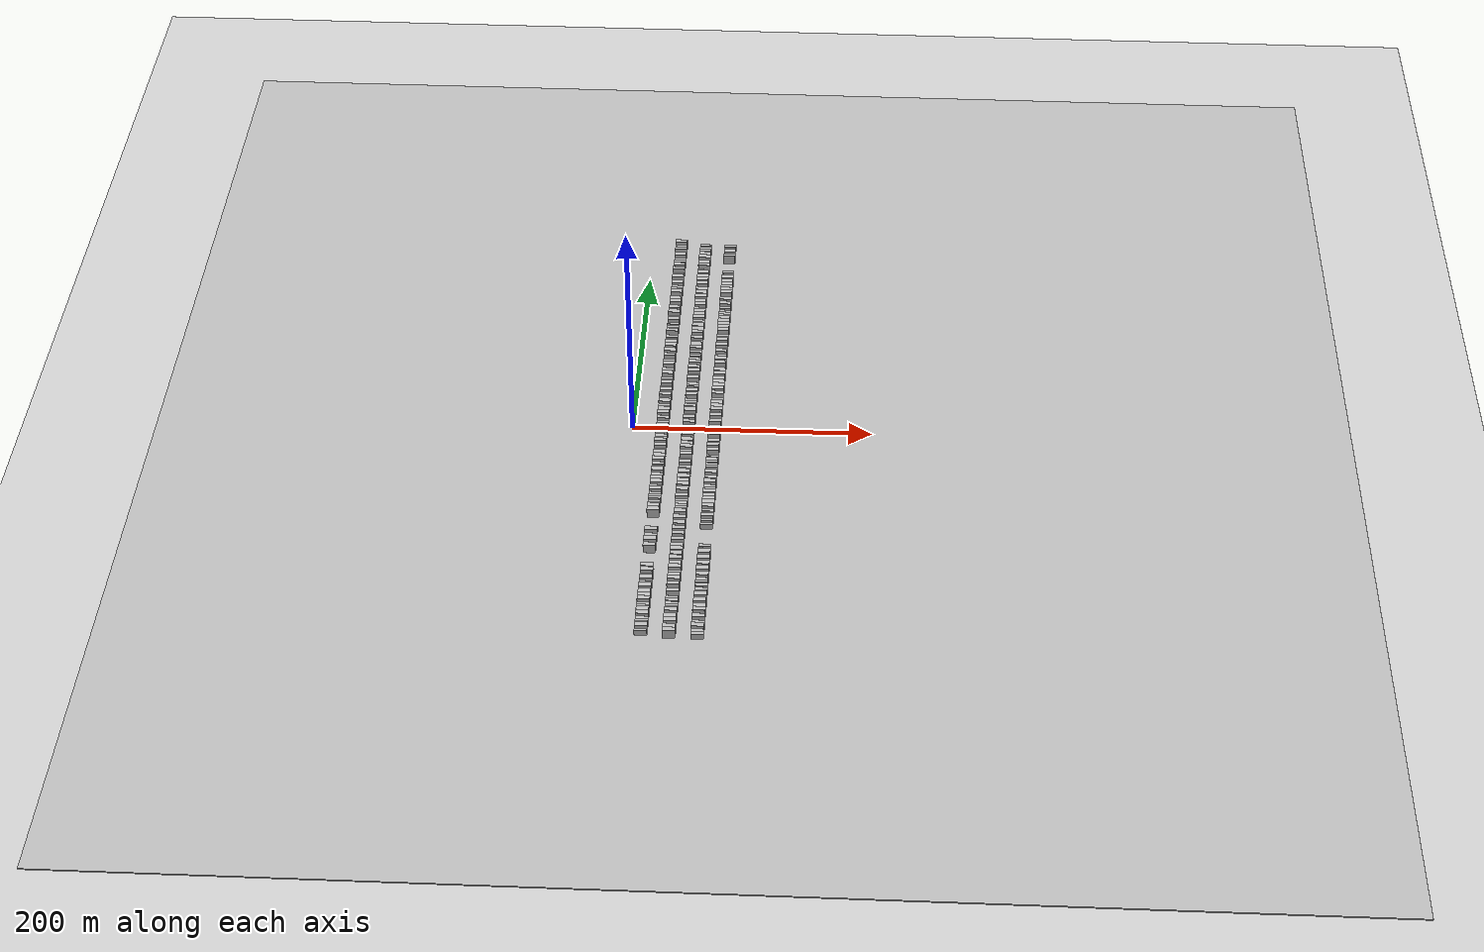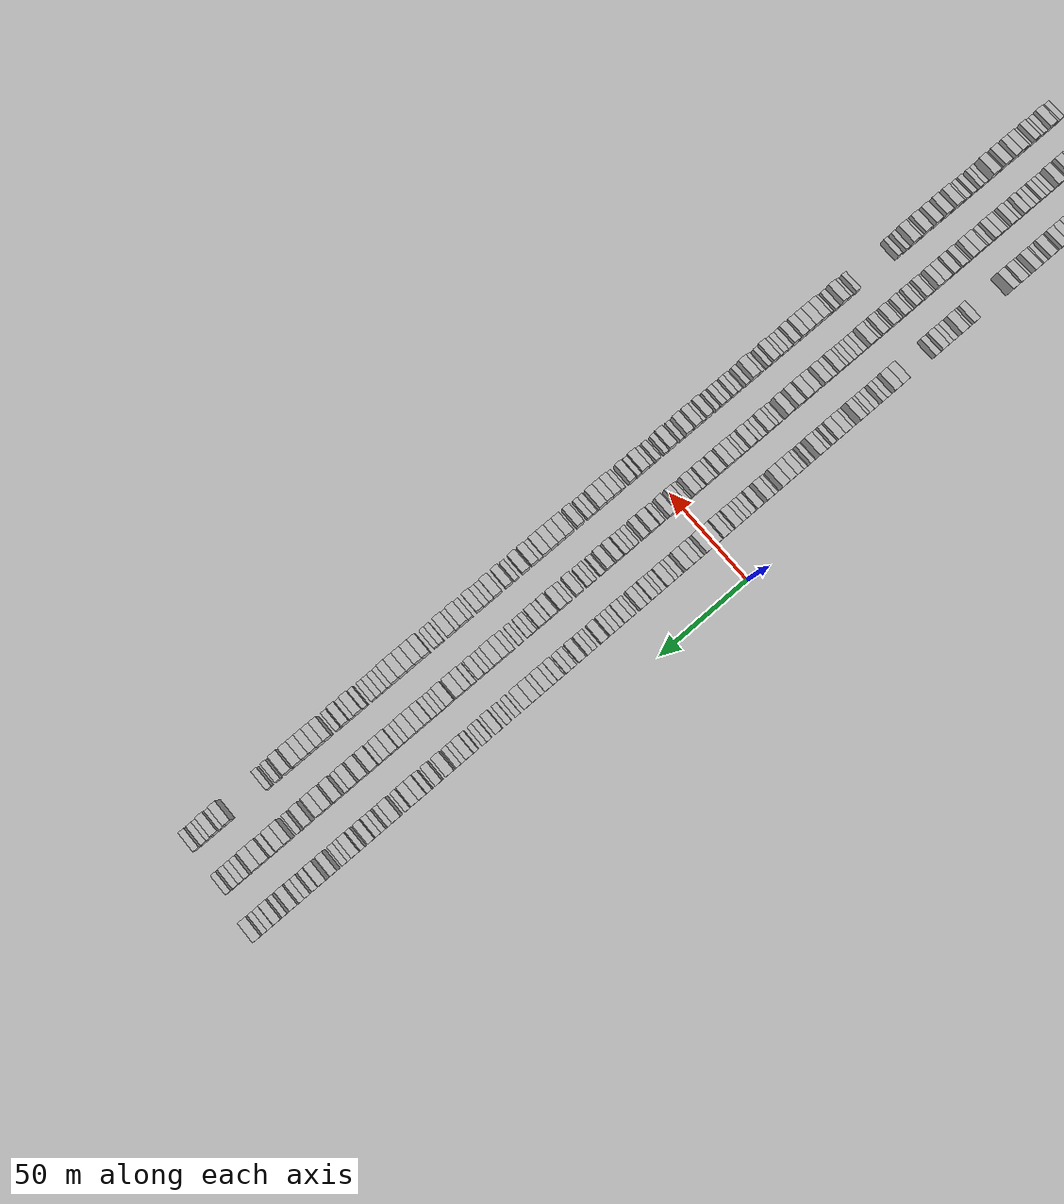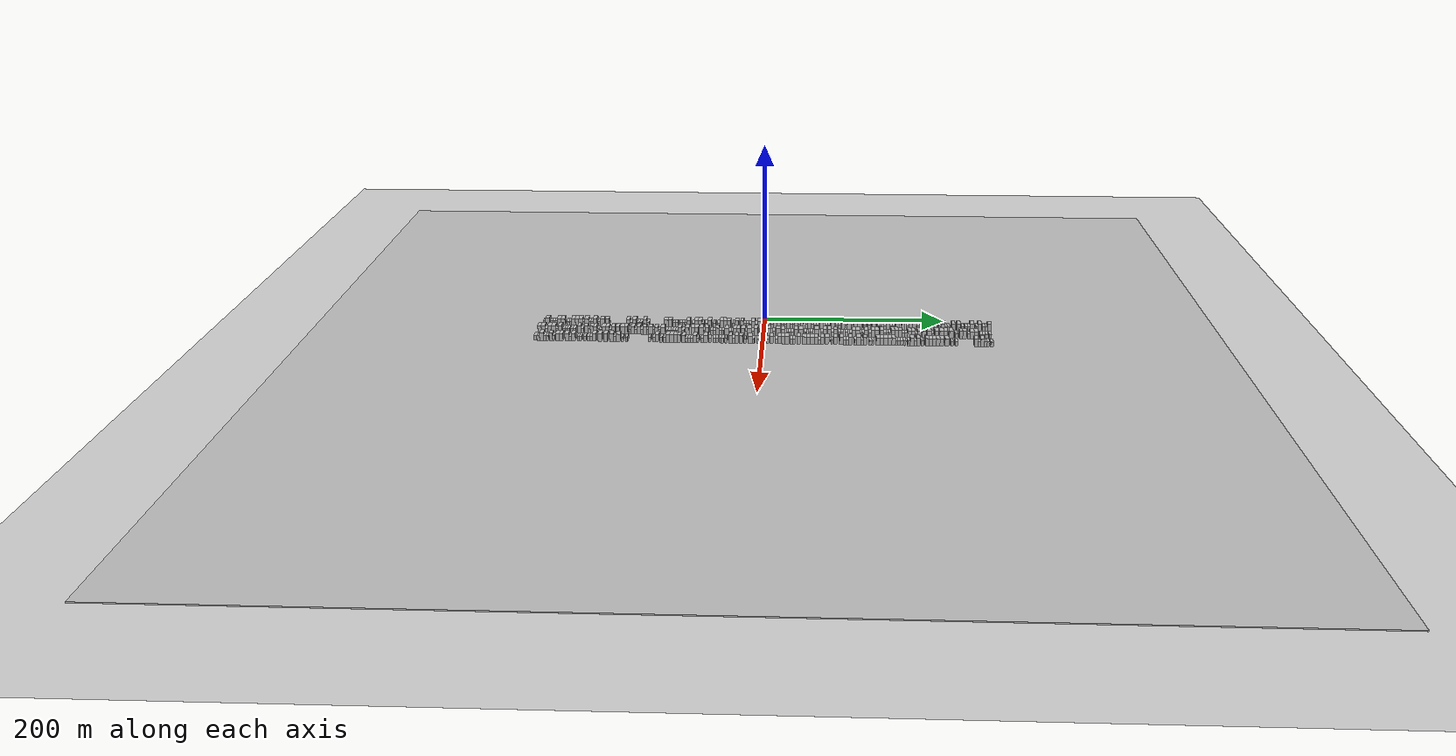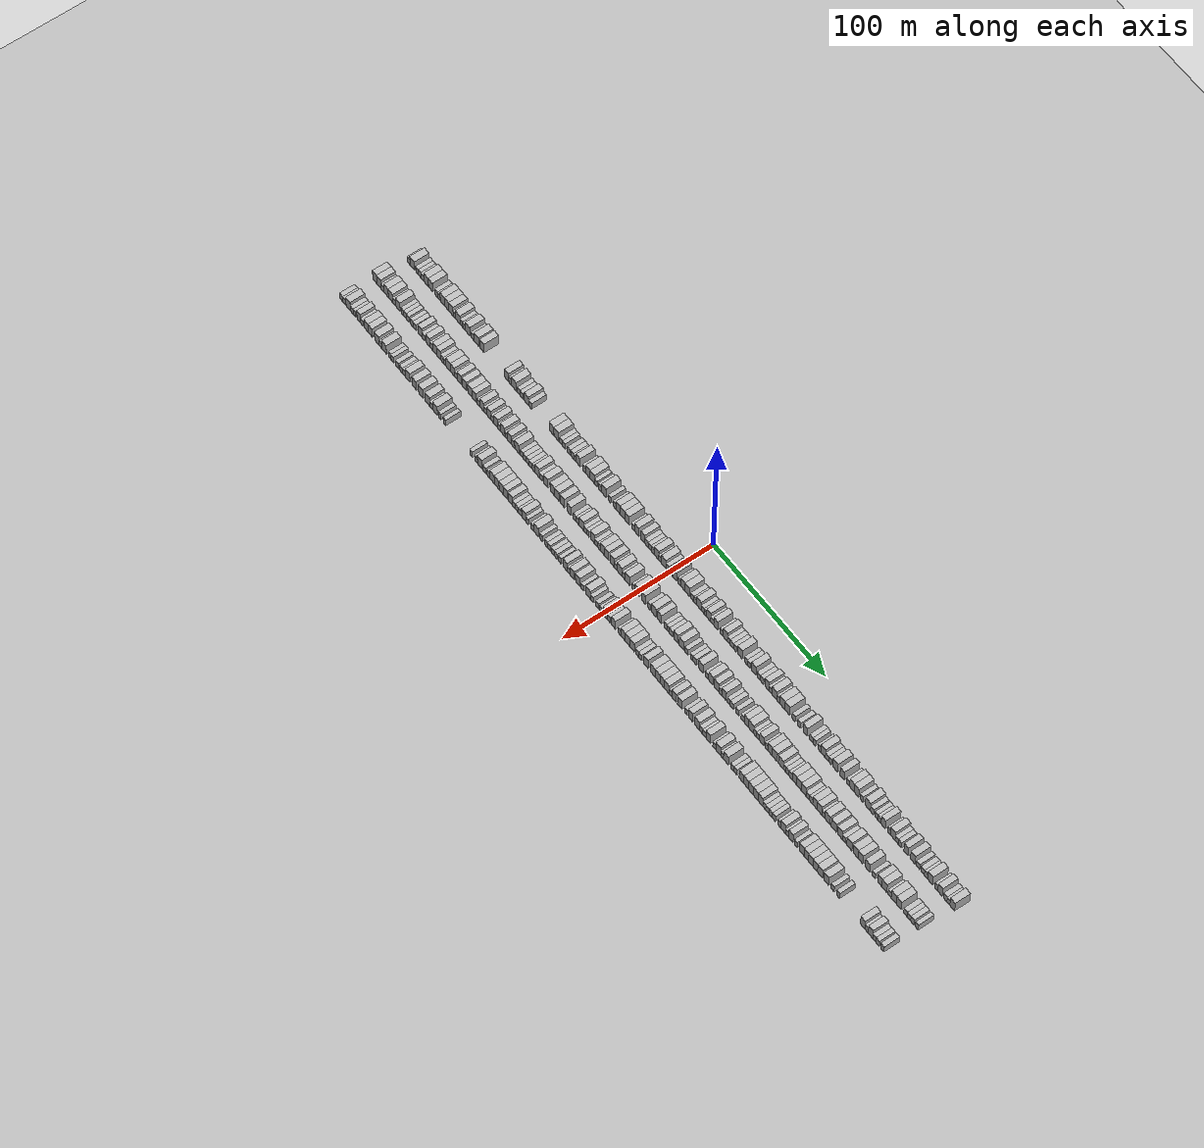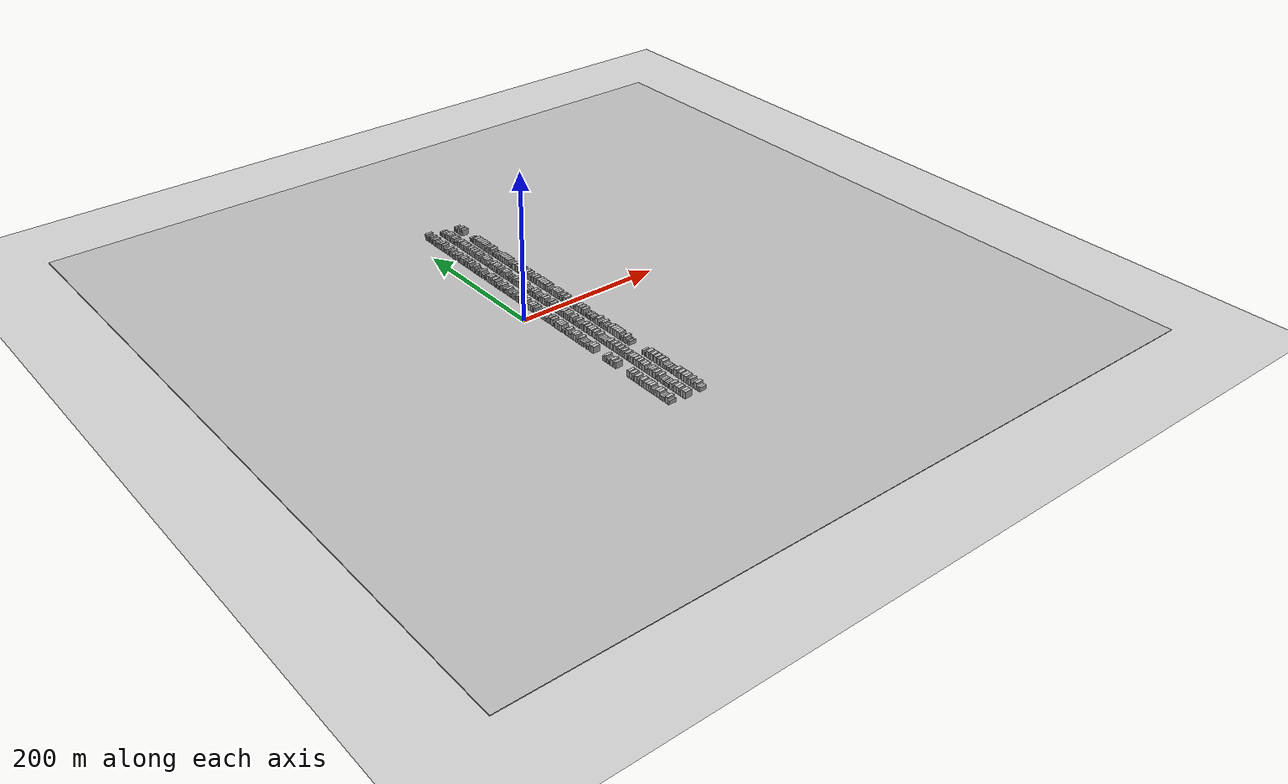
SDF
<?xml version="1.0" encoding="utf-8"?>

<sdf version="1.6">

   <world name="default">

      <gui fullscreen="0">

         <camera name="user_camera">

            <pose>-15 0 4.57585 0 0 0</pose>

            <view_controller>orbit</view_controller>

         </camera>

      </gui>

      <scene>

         <sky>

           <clouds>

             <speed>12</speed>

           </clouds>

         </sky>

         <ambient>0.4 0.4 0.4 1</ambient>

         <background>0.7 0.7 0.7 1</background>

         <shadows>1</shadows>

      </scene>

      <gravity>0 0 -9.8066</gravity>

      <magnetic_field>6e-06 2.3e-05 -4.2e-05</magnetic_field>

      <physics default="0" name="default_physics" type="ode">

         <ode>

            <solver>

               <type>quick</type>

               <iters>10</iters>

               <sor>1.0</sor>

               <use_dynamic_moi_rescaling>0</use_dynamic_moi_rescaling>

            </solver>

            <constraints>

               <cfm>0</cfm>

               <erp>0.2</erp>

               <contact_max_correcting_vel>100</contact_max_correcting_vel>

               <contact_surface_layer>0.001</contact_surface_layer>

            </constraints>

         </ode>

         <max_step_size>0.004</max_step_size>

         <real_time_factor>1</real_time_factor>

         <real_time_update_rate>250</real_time_update_rate>

      </physics>

      <light name="sun" type="directional">

         <cast_shadows>1</cast_shadows>

         <pose>0 0 10 0 0 0</pose>

         <diffuse>0.8 0.8 0.8 1</diffuse>

         <specular>0.2 0.2 0.2 1</specular>

         <attenuation>

            <range>1000</range>

            <constant>0.9</constant>

            <linear>0.01</linear>

            <quadratic>0.001</quadratic>

         </attenuation>

         <direction>-0.5 0.1 -0.9</direction>

      </light>

      <include>

         <name>ground_plane_1</name>

         <uri>model://HANNAS_ground_plane</uri>

         <pose>0 0 0  0 0 0</pose>

      </include>

      <include>

         <name>ground_plane_2</name>

         <uri>model://HANNAS_ground_plane</uri>

         <pose>100 0 0  0 0 0</pose>

      </include>

      <model name="building_1">

         <static>1</static>

         <pose frame="">25.0000 -244.7598 0 0.000000 0.000000 0.000000</pose>

         <link name="link">

            <pose frame="">0 0 3.00 0 0 0</pose>

            <collision name="collision">

               <geometry>

                  <box>

                     <size>10.0000 2.4804 6.0000</size>

                  </box>

               </geometry>

               <max_contacts>10</max_contacts>

               <surface>

                  <contact>

                     <ode/>

                  </contact>

                  <bounce/>

                  <friction>

                     <torsional>

                        <ode/>

                     </torsional>

                     <ode/>

                  </friction>

               </surface>

            </collision>

            <visual name="visual">

               <cast_shadows>0</cast_shadows>

               <geometry>

                  <box>

                     <size>10.0000 2.4804 6.0000</size>

                  </box>

               </geometry>

               <material>

                  <script>

                     <uri>model://HANNAS_wall/materials/scripts</uri>

                     <uri>model://HANNAS_wall/materials/textures</uri>

                     <name>vrc/HANNAS_wall</name>

                  </script>

               </material>

            </visual>

            <self_collide>0</self_collide>

            <enable_wind>0</enable_wind>

            <kinematic>0</kinematic>

         </link>

      </model>

      <model name="building_2">

         <static>1</static>

         <pose frame="">25.0000 -241.2748 0 0.000000 0.000000 0.000000</pose>

         <link name="link">

            <pose frame="">0 0 4.50 0 0 0</pose>

            <collision name="collision">

               <geometry>

                  <box>

                     <size>10.0000 4.4895 9.0000</size>

                  </box>

               </geometry>

               <max_contacts>10</max_contacts>

               <surface>

                  <contact>

                     <ode/>

                  </contact>

                  <bounce/>

                  <friction>

                     <torsional>

                        <ode/>

                     </torsional>

                     <ode/>

                  </friction>

               </surface>

            </collision>

            <visual name="visual">

               <cast_shadows>0</cast_shadows>

               <geometry>

                  <box>

                     <size>10.0000 4.4895 9.0000</size>

                  </box>

               </geometry>

               <material>

                  <script>

                     <uri>model://HANNAS_wall/materials/scripts</uri>

                     <uri>model://HANNAS_wall/materials/textures</uri>

                     <name>vrc/HANNAS_wall</name>

                  </script>

               </material>

            </visual>

            <self_collide>0</self_collide>

            <enable_wind>0</enable_wind>

            <kinematic>0</kinematic>

         </link>

      </model>

      <model name="building_3">

         <static>1</static>

         <pose frame="">25.0000 -236.6963 0 0.000000 0.000000 0.000000</pose>

         <link name="link">

            <pose frame="">0 0 3.00 0 0 0</pose>

            <collision name="collision">

               <geometry>

                  <box>

                     <size>10.0000 2.6676 6.0000</size>

                  </box>

               </geometry>

               <max_contacts>10</max_contacts>

               <surface>

                  <contact>

                     <ode/>

                  </contact>

                  <bounce/>

                  <friction>

                     <torsional>

                        <ode/>

                     </torsional>

                     <ode/>

                  </friction>

               </surface>

            </collision>

            <visual name="visual">

               <cast_shadows>0</cast_shadows>

               <geometry>

                  <box>

                     <size>10.0000 2.6676 6.0000</size>

                  </box>

               </geometry>

               <material>

                  <script>

                     <uri>model://HANNAS_wall/materials/scripts</uri>

                     <uri>model://HANNAS_wall/materials/textures</uri>

                     <name>vrc/HANNAS_wall</name>

                  </script>

               </material>

            </visual>

            <self_collide>0</self_collide>

            <enable_wind>0</enable_wind>

            <kinematic>0</kinematic>

         </link>

      </model>

      <model name="building_4">

         <static>1</static>

         <pose frame="">25.0000 -234.1223 0 0.000000 0.000000 0.000000</pose>

         <link name="link">

            <pose frame="">0 0 3.00 0 0 0</pose>

            <collision name="collision">

               <geometry>

                  <box>

                     <size>10.0000 2.4802 6.0000</size>

                  </box>

               </geometry>

               <max_contacts>10</max_contacts>

               <surface>

                  <contact>

                     <ode/>

                  </contact>

                  <bounce/>

                  <friction>

                     <torsional>

                        <ode/>

                     </torsional>

                     <ode/>

                  </friction>

               </surface>

            </collision>

            <visual name="visual">

               <cast_shadows>0</cast_shadows>

               <geometry>

                  <box>

                     <size>10.0000 2.4802 6.0000</size>

                  </box>

               </geometry>

               <material>

                  <script>

                     <uri>model://HANNAS_wall/materials/scripts</uri>

                     <uri>model://HANNAS_wall/materials/textures</uri>

                     <name>vrc/HANNAS_wall</name>

                  </script>

               </material>

            </visual>

            <self_collide>0</self_collide>

            <enable_wind>0</enable_wind>

            <kinematic>0</kinematic>

         </link>

      </model>

      <model name="building_5">

         <static>1</static>

         <pose frame="">25.0000 -231.4768 0 0.000000 0.000000 0.000000</pose>

         <link name="link">

            <pose frame="">0 0 3.00 0 0 0</pose>

            <collision name="collision">

               <geometry>

                  <box>

                     <size>10.0000 2.8108 6.0000</size>

                  </box>

               </geometry>

               <max_contacts>10</max_contacts>

               <surface>

                  <contact>

                     <ode/>

                  </contact>

                  <bounce/>

                  <friction>

                     <torsional>

                        <ode/>

                     </torsional>

                     <ode/>

                  </friction>

               </surface>

            </collision>

            <visual name="visual">

               <cast_shadows>0</cast_shadows>

               <geometry>

                  <box>

                     <size>10.0000 2.8108 6.0000</size>

                  </box>

               </geometry>

               <material>

                  <script>

                     <uri>model://HANNAS_wall/materials/scripts</uri>

                     <uri>model://HANNAS_wall/materials/textures</uri>

                     <name>vrc/HANNAS_wall</name>

                  </script>

               </material>

            </visual>

            <self_collide>0</self_collide>

            <enable_wind>0</enable_wind>

            <kinematic>0</kinematic>

         </link>

      </model>

      <model name="building_6">

         <static>1</static>

         <pose frame="">25.0000 -227.9044 0 0.000000 0.000000 0.000000</pose>

         <link name="link">

            <pose frame="">0 0 4.50 0 0 0</pose>

            <collision name="collision">

               <geometry>

                  <box>

                     <size>10.0000 4.3340 9.0000</size>

                  </box>

               </geometry>

               <max_contacts>10</max_contacts>

               <surface>

                  <contact>

                     <ode/>

                  </contact>

                  <bounce/>

                  <friction>

                     <torsional>

                        <ode/>

                     </torsional>

                     <ode/>

                  </friction>

               </surface>

            </collision>

            <visual name="visual">

               <cast_shadows>0</cast_shadows>

               <geometry>

                  <box>

                     <size>10.0000 4.3340 9.0000</size>

                  </box>

               </geometry>

               <material>

                  <script>

                     <uri>model://HANNAS_wall/materials/scripts</uri>

                     <uri>model://HANNAS_wall/materials/textures</uri>

                     <name>vrc/HANNAS_wall</name>

                  </script>

               </material>

            </visual>

            <self_collide>0</self_collide>

            <enable_wind>0</enable_wind>

            <kinematic>0</kinematic>

         </link>

      </model>

      <model name="building_7">

         <static>1</static>

         <pose frame="">25.0000 -223.6876 0 0.000000 0.000000 0.000000</pose>

         <link name="link">

            <pose frame="">0 0 4.50 0 0 0</pose>

            <collision name="collision">

               <geometry>

                  <box>

                     <size>10.0000 4.0997 9.0000</size>

                  </box>

               </geometry>

               <max_contacts>10</max_contacts>

               <surface>

                  <contact>

                     <ode/>

                  </contact>

                  <bounce/>

                  <friction>

                     <torsional>

                        <ode/>

                     </torsional>

                     <ode/>

                  </friction>

               </surface>

            </collision>

            <visual name="visual">

               <cast_shadows>0</cast_shadows>

               <geometry>

                  <box>

                     <size>10.0000 4.0997 9.0000</size>

                  </box>

               </geometry>

               <material>

                  <script>

                     <uri>model://HANNAS_wall/materials/scripts</uri>

                     <uri>model://HANNAS_wall/materials/textures</uri>

                     <name>vrc/HANNAS_wall</name>

                  </script>

               </material>

            </visual>

            <self_collide>0</self_collide>

            <enable_wind>0</enable_wind>

            <kinematic>0</kinematic>

         </link>

      </model>

      <model name="building_8">

         <static>1</static>

         <pose frame="">25.0000 -218.2530 0 0.000000 0.000000 0.000000</pose>

         <link name="link">

            <pose frame="">0 0 3.00 0 0 0</pose>

            <collision name="collision">

               <geometry>

                  <box>

                     <size>10.0000 2.7694 6.0000</size>

                  </box>

               </geometry>

               <max_contacts>10</max_contacts>

               <surface>

                  <contact>

                     <ode/>

                  </contact>

                  <bounce/>

                  <friction>

                     <torsional>

                        <ode/>

                     </torsional>

                     <ode/>

                  </friction>

               </surface>

            </collision>

            <visual name="visual">

               <cast_shadows>0</cast_shadows>

               <geometry>

                  <box>

                     <size>10.0000 2.7694 6.0000</size>

                  </box>

               </geometry>

               <material>

                  <script>

                     <uri>model://HANNAS_wall/materials/scripts</uri>

                     <uri>model://HANNAS_wall/materials/textures</uri>

                     <name>vrc/HANNAS_wall</name>

                  </script>

               </material>

            </visual>

            <self_collide>0</self_collide>

            <enable_wind>0</enable_wind>

            <kinematic>0</kinematic>

         </link>

      </model>

      <model name="building_9">

         <static>1</static>

         <pose frame="">25.0000 -215.5793 0 0.000000 0.000000 0.000000</pose>

         <link name="link">

            <pose frame="">0 0 3.00 0 0 0</pose>

            <collision name="collision">

               <geometry>

                  <box>

                     <size>10.0000 2.5779 6.0000</size>

                  </box>

               </geometry>

               <max_contacts>10</max_contacts>

               <surface>

                  <contact>

                     <ode/>

                  </contact>

                  <bounce/>

                  <friction>

                     <torsional>

                        <ode/>

                     </torsional>

                     <ode/>

                  </friction>

               </surface>

            </collision>

            <visual name="visual">

               <cast_shadows>0</cast_shadows>

               <geometry>

                  <box>

                     <size>10.0000 2.5779 6.0000</size>

                  </box>

               </geometry>

               <material>

                  <script>

                     <uri>model://HANNAS_wall/materials/scripts</uri>

                     <uri>model://HANNAS_wall/materials/textures</uri>

                     <name>vrc/HANNAS_wall</name>

                  </script>

               </material>

            </visual>

            <self_collide>0</self_collide>

            <enable_wind>0</enable_wind>

            <kinematic>0</kinematic>

         </link>

      </model>

      <model name="building_10">

         <static>1</static>

         <pose frame="">25.0000 -212.1673 0 0.000000 0.000000 0.000000</pose>

         <link name="link">

            <pose frame="">0 0 4.50 0 0 0</pose>

            <collision name="collision">

               <geometry>

                  <box>

                     <size>10.0000 4.2461 9.0000</size>

                  </box>

               </geometry>

               <max_contacts>10</max_contacts>

               <surface>

                  <contact>

                     <ode/>

                  </contact>

                  <bounce/>

                  <friction>

                     <torsional>

                        <ode/>

                     </torsional>

                     <ode/>

                  </friction>

               </surface>

            </collision>

            <visual name="visual">

               <cast_shadows>0</cast_shadows>

               <geometry>

                  <box>

                     <size>10.0000 4.2461 9.0000</size>

                  </box>

               </geometry>

               <material>

                  <script>

                     <uri>model://HANNAS_wall/materials/scripts</uri>

                     <uri>model://HANNAS_wall/materials/textures</uri>

                     <name>vrc/HANNAS_wall</name>

                  </script>

               </material>

            </visual>

            <self_collide>0</self_collide>

            <enable_wind>0</enable_wind>

            <kinematic>0</kinematic>

         </link>

      </model>

      <model name="building_11">

         <static>1</static>

         <pose frame="">25.0000 -208.0674 0 0.000000 0.000000 0.000000</pose>

         <link name="link">

            <pose frame="">0 0 4.50 0 0 0</pose>

            <collision name="collision">

               <geometry>

                  <box>

                     <size>10.0000 3.9538 9.0000</size>

                  </box>

               </geometry>

               <max_contacts>10</max_contacts>

               <surface>

                  <contact>

                     <ode/>

                  </contact>

                  <bounce/>

                  <friction>

                     <torsional>

                        <ode/>

                     </torsional>

                     <ode/>

                  </friction>

               </surface>

            </collision>

            <visual name="visual">

               <cast_shadows>0</cast_shadows>

               <geometry>

                  <box>

                     <size>10.0000 3.9538 9.0000</size>

                  </box>

               </geometry>

               <material>

                  <script>

                     <uri>model://HANNAS_wall/materials/scripts</uri>

                     <uri>model://HANNAS_wall/materials/textures</uri>

                     <name>vrc/HANNAS_wall</name>

                  </script>

               </material>

            </visual>

            <self_collide>0</self_collide>

            <enable_wind>0</enable_wind>

            <kinematic>0</kinematic>

         </link>

      </model>

      <model name="building_12">

         <static>1</static>

         <pose frame="">25.0000 -204.0445 0 0.000000 0.000000 0.000000</pose>

         <link name="link">

            <pose frame="">0 0 4.50 0 0 0</pose>

            <collision name="collision">

               <geometry>

                  <box>

                     <size>10.0000 4.0920 9.0000</size>

                  </box>

               </geometry>

               <max_contacts>10</max_contacts>

               <surface>

                  <contact>

                     <ode/>

                  </contact>

                  <bounce/>

                  <friction>

                     <torsional>

                        <ode/>

                     </torsional>

                     <ode/>

                  </friction>

               </surface>

            </collision>

            <visual name="visual">

               <cast_shadows>0</cast_shadows>

               <geometry>

                  <box>

                     <size>10.0000 4.0920 9.0000</size>

                  </box>

               </geometry>

               <material>

                  <script>

                     <uri>model://HANNAS_wall/materials/scripts</uri>

                     <uri>model://HANNAS_wall/materials/textures</uri>

                     <name>vrc/HANNAS_wall</name>

                  </script>

               </material>

            </visual>

            <self_collide>0</self_collide>

            <enable_wind>0</enable_wind>

            <kinematic>0</kinematic>

         </link>

      </model>

      <model name="building_13">

         <static>1</static>

         <pose frame="">25.0000 -200.7965 0 0.000000 0.000000 0.000000</pose>

         <link name="link">

            <pose frame="">0 0 3.00 0 0 0</pose>

            <collision name="collision">

               <geometry>

                  <box>

                     <size>10.0000 2.4040 6.0000</size>

                  </box>

               </geometry>

               <max_contacts>10</max_contacts>

               <surface>

                  <contact>

                     <ode/>

                  </contact>

                  <bounce/>

                  <friction>

                     <torsional>

                        <ode/>

                     </torsional>

                     <ode/>

                  </friction>

               </surface>

            </collision>

            <visual name="visual">

               <cast_shadows>0</cast_shadows>

               <geometry>

                  <box>

                     <size>10.0000 2.4040 6.0000</size>

                  </box>

               </geometry>

               <material>

                  <script>

                     <uri>model://HANNAS_wall/materials/scripts</uri>

                     <uri>model://HANNAS_wall/materials/textures</uri>

                     <name>vrc/HANNAS_wall</name>

                  </script>

               </material>

            </visual>

            <self_collide>0</self_collide>

            <enable_wind>0</enable_wind>

            <kinematic>0</kinematic>

         </link>

      </model>

      <model name="building_14">

         <static>1</static>

         <pose frame="">25.0000 -197.3850 0 0.000000 0.000000 0.000000</pose>

         <link name="link">

            <pose frame="">0 0 4.50 0 0 0</pose>

            <collision name="collision">

               <geometry>

                  <box>

                     <size>10.0000 4.4190 9.0000</size>

                  </box>

               </geometry>

               <max_contacts>10</max_contacts>

               <surface>

                  <contact>

                     <ode/>

                  </contact>

                  <bounce/>

                  <friction>

                     <torsional>

                        <ode/>

                     </torsional>

                     <ode/>

                  </friction>

               </surface>

            </collision>

            <visual name="visual">

               <cast_shadows>0</cast_shadows>

               <geometry>

                  <box>

                     <size>10.0000 4.4190 9.0000</size>

                  </box>

               </geometry>

               <material>

                  <script>

                     <uri>model://HANNAS_wall/materials/scripts</uri>

                     <uri>model://HANNAS_wall/materials/textures</uri>

                     <name>vrc/HANNAS_wall</name>

                  </script>

               </material>

            </visual>

            <self_collide>0</self_collide>

            <enable_wind>0</enable_wind>

            <kinematic>0</kinematic>

         </link>

      </model>

      <model name="building_15">

         <static>1</static>

         <pose frame="">25.0000 -193.9602 0 0.000000 0.000000 0.000000</pose>

         <link name="link">

            <pose frame="">0 0 3.00 0 0 0</pose>

            <collision name="collision">

               <geometry>

                  <box>

                     <size>10.0000 2.4307 6.0000</size>

                  </box>

               </geometry>

               <max_contacts>10</max_contacts>

               <surface>

                  <contact>

                     <ode/>

                  </contact>

                  <bounce/>

                  <friction>

                     <torsional>

                        <ode/>

                     </torsional>

                     <ode/>

                  </friction>

               </surface>

            </collision>

            <visual name="visual">

               <cast_shadows>0</cast_shadows>

               <geometry>

                  <box>

                     <size>10.0000 2.4307 6.0000</size>

                  </box>

               </geometry>

               <material>

                  <script>

                     <uri>model://HANNAS_wall/materials/scripts</uri>

                     <uri>model://HANNAS_wall/materials/textures</uri>

                     <name>vrc/HANNAS_wall</name>

                  </script>

               </material>

            </visual>

            <self_collide>0</self_collide>

            <enable_wind>0</enable_wind>

            <kinematic>0</kinematic>

         </link>

      </model>

      <model name="building_16">

         <static>1</static>

         <pose frame="">25.0000 -191.4670 0 0.000000 0.000000 0.000000</pose>

         <link name="link">

            <pose frame="">0 0 3.00 0 0 0</pose>

            <collision name="collision">

               <geometry>

                  <box>

                     <size>10.0000 2.5557 6.0000</size>

                  </box>

               </geometry>

               <max_contacts>10</max_contacts>

               <surface>

                  <contact>

                     <ode/>

                  </contact>

                  <bounce/>

                  <friction>

                     <torsional>

                        <ode/>

                     </torsional>

                     <ode/>

                  </friction>

               </surface>

            </collision>

            <visual name="visual">

               <cast_shadows>0</cast_shadows>

               <geometry>

                  <box>

                     <size>10.0000 2.5557 6.0000</size>

                  </box>

               </geometry>

               <material>

                  <script>

                     <uri>model://HANNAS_wall/materials/scripts</uri>

                     <uri>model://HANNAS_wall/materials/textures</uri>

                     <name>vrc/HANNAS_wall</name>

                  </script>

               </material>

            </visual>

            <self_collide>0</self_collide>

            <enable_wind>0</enable_wind>

            <kinematic>0</kinematic>

         </link>

      </model>

      <model name="building_17">

         <static>1</static>

         <pose frame="">25.0000 -187.9979 0 0.000000 0.000000 0.000000</pose>

         <link name="link">

            <pose frame="">0 0 4.50 0 0 0</pose>

            <collision name="collision">

               <geometry>

                  <box>

                     <size>10.0000 4.3826 9.0000</size>

                  </box>

               </geometry>

               <max_contacts>10</max_contacts>

               <surface>

                  <contact>

                     <ode/>

                  </contact>

                  <bounce/>

                  <friction>

                     <torsional>

                        <ode/>

                     </torsional>

                     <ode/>

                  </friction>

               </surface>

            </collision>

            <visual name="visual">

               <cast_shadows>0</cast_shadows>

               <geometry>

                  <box>

                     <size>10.0000 4.3826 9.0000</size>

                  </box>

               </geometry>

               <material>

                  <script>

                     <uri>model://HANNAS_wall/materials/scripts</uri>

                     <uri>model://HANNAS_wall/materials/textures</uri>

                     <name>vrc/HANNAS_wall</name>

                  </script>

               </material>

            </visual>

            <self_collide>0</self_collide>

            <enable_wind>0</enable_wind>

            <kinematic>0</kinematic>

         </link>

      </model>

      <model name="building_18">

         <static>1</static>

         <pose frame="">25.0000 -183.3274 0 0.000000 0.000000 0.000000</pose>

         <link name="link">

            <pose frame="">0 0 3.00 0 0 0</pose>

            <collision name="collision">

               <geometry>

                  <box>

                     <size>10.0000 2.9584 6.0000</size>

                  </box>

               </geometry>

               <max_contacts>10</max_contacts>

               <surface>

                  <contact>

                     <ode/>

                  </contact>

                  <bounce/>

                  <friction>

                     <torsional>

                        <ode/>

                     </torsional>

                     <ode/>

                  </friction>

               </surface>

            </collision>

            <visual name="visual">

               <cast_shadows>0</cast_shadows>

               <geometry>

                  <box>

                     <size>10.0000 2.9584 6.0000</size>

                  </box>

               </geometry>

               <material>

                  <script>

                     <uri>model://HANNAS_wall/materials/scripts</uri>

                     <uri>model://HANNAS_wall/materials/textures</uri>

                     <name>vrc/HANNAS_wall</name>

                  </script>

               </material>

            </visual>

            <self_collide>0</self_collide>

            <enable_wind>0</enable_wind>

            <kinematic>0</kinematic>

         </link>

      </model>

      <model name="building_19">

         <static>1</static>

         <pose frame="">25.0000 -179.6410 0 0.000000 0.000000 0.000000</pose>

         <link name="link">

            <pose frame="">0 0 4.50 0 0 0</pose>

            <collision name="collision">

               <geometry>

                  <box>

                     <size>10.0000 4.4143 9.0000</size>

                  </box>

               </geometry>

               <max_contacts>10</max_contacts>

               <surface>

                  <contact>

                     <ode/>

                  </contact>

                  <bounce/>

                  <friction>

                     <torsional>

                        <ode/>

                     </torsional>

                     <ode/>

                  </friction>

               </surface>

            </collision>

            <visual name="visual">

               <cast_shadows>0</cast_shadows>

               <geometry>

                  <box>

                     <size>10.0000 4.4143 9.0000</size>

                  </box>

               </geometry>

               <material>

                  <script>

                     <uri>model://HANNAS_wall/materials/scripts</uri>

                     <uri>model://HANNAS_wall/materials/textures</uri>

                     <name>vrc/HANNAS_wall</name>

                  </script>

               </material>

            </visual>

            <self_collide>0</self_collide>

            <enable_wind>0</enable_wind>

            <kinematic>0</kinematic>

         </link>

      </model>

      <model name="building_20">

         <static>1</static>

         <pose frame="">25.0000 -174.3784 0 0.000000 0.000000 0.000000</pose>

         <link name="link">

            <pose frame="">0 0 4.50 0 0 0</pose>

            <collision name="collision">

               <geometry>

                  <box>

                     <size>10.0000 4.1110 9.0000</size>

                  </box>

               </geometry>

               <max_contacts>10</max_contacts>

               <surface>

                  <contact>

                     <ode/>

                  </contact>

                  <bounce/>

                  <friction>

                     <torsional>

                        <ode/>

                     </torsional>

                     <ode/>

                  </friction>

               </surface>

            </collision>

            <visual name="visual">

               <cast_shadows>0</cast_shadows>

               <geometry>

                  <box>

                     <size>10.0000 4.1110 9.0000</size>

                  </box>

               </geometry>

               <material>

                  <script>

                     <uri>model://HANNAS_wall/materials/scripts</uri>

                     <uri>model://HANNAS_wall/materials/textures</uri>

                     <name>vrc/HANNAS_wall</name>

                  </script>

               </material>

            </visual>

            <self_collide>0</self_collide>

            <enable_wind>0</enable_wind>

            <kinematic>0</kinematic>

         </link>

      </model>

      <model name="building_21">

         <static>1</static>

         <pose frame="">25.0000 -150.7308 0 0.000000 0.000000 0.000000</pose>

         <link name="link">

            <pose frame="">0 0 4.50 0 0 0</pose>

            <collision name="collision">

               <geometry>

                  <box>

                     <size>10.0000 3.7281 9.0000</size>

                  </box>

               </geometry>

               <max_contacts>10</max_contacts>

               <surface>

                  <contact>

                     <ode/>

                  </contact>

                  <bounce/>

                  <friction>

                     <torsional>

                        <ode/>

                     </torsional>

                     <ode/>

                  </friction>

               </surface>

            </collision>

            <visual name="visual">

               <cast_shadows>0</cast_shadows>

               <geometry>

                  <box>

                     <size>10.0000 3.7281 9.0000</size>

                  </box>

               </geometry>

               <material>

                  <script>

                     <uri>model://HANNAS_wall/materials/scripts</uri>

                     <uri>model://HANNAS_wall/materials/textures</uri>

                     <name>vrc/HANNAS_wall</name>

                  </script>

               </material>

            </visual>

            <self_collide>0</self_collide>

            <enable_wind>0</enable_wind>

            <kinematic>0</kinematic>

         </link>

      </model>

      <model name="building_22">

         <static>1</static>

         <pose frame="">25.0000 -147.4935 0 0.000000 0.000000 0.000000</pose>

         <link name="link">

            <pose frame="">0 0 3.00 0 0 0</pose>

            <collision name="collision">

               <geometry>

                  <box>

                     <size>10.0000 2.7465 6.0000</size>

                  </box>

               </geometry>

               <max_contacts>10</max_contacts>

               <surface>

                  <contact>

                     <ode/>

                  </contact>

                  <bounce/>

                  <friction>

                     <torsional>

                        <ode/>

                     </torsional>

                     <ode/>

                  </friction>

               </surface>

            </collision>

            <visual name="visual">

               <cast_shadows>0</cast_shadows>

               <geometry>

                  <box>

                     <size>10.0000 2.7465 6.0000</size>

                  </box>

               </geometry>

               <material>

                  <script>

                     <uri>model://HANNAS_wall/materials/scripts</uri>

                     <uri>model://HANNAS_wall/materials/textures</uri>

                     <name>vrc/HANNAS_wall</name>

                  </script>

               </material>

            </visual>

            <self_collide>0</self_collide>

            <enable_wind>0</enable_wind>

            <kinematic>0</kinematic>

         </link>

      </model>

      <model name="building_23">

         <static>1</static>

         <pose frame="">25.0000 -143.8835 0 0.000000 0.000000 0.000000</pose>

         <link name="link">

            <pose frame="">0 0 4.50 0 0 0</pose>

            <collision name="collision">

               <geometry>

                  <box>

                     <size>10.0000 4.4735 9.0000</size>

                  </box>

               </geometry>

               <max_contacts>10</max_contacts>

               <surface>

                  <contact>

                     <ode/>

                  </contact>

                  <bounce/>

                  <friction>

                     <torsional>

                        <ode/>

                     </torsional>

                     <ode/>

                  </friction>

               </surface>

            </collision>

            <visual name="visual">

               <cast_shadows>0</cast_shadows>

               <geometry>

                  <box>

                     <size>10.0000 4.4735 9.0000</size>

                  </box>

               </geometry>

               <material>

                  <script>

                     <uri>model://HANNAS_wall/materials/scripts</uri>

                     <uri>model://HANNAS_wall/materials/textures</uri>

                     <name>vrc/HANNAS_wall</name>

                  </script>

               </material>

            </visual>

            <self_collide>0</self_collide>

            <enable_wind>0</enable_wind>

            <kinematic>0</kinematic>

         </link>

      </model>

      <model name="building_24">

         <static>1</static>

         <pose frame="">25.0000 -139.3091 0 0.000000 0.000000 0.000000</pose>

         <link name="link">

            <pose frame="">0 0 3.00 0 0 0</pose>

            <collision name="collision">

               <geometry>

                  <box>

                     <size>10.0000 2.6754 6.0000</size>

                  </box>

               </geometry>

               <max_contacts>10</max_contacts>

               <surface>

                  <contact>

                     <ode/>

                  </contact>

                  <bounce/>

                  <friction>

                     <torsional>

                        <ode/>

                     </torsional>

                     <ode/>

                  </friction>

               </surface>

            </collision>

            <visual name="visual">

               <cast_shadows>0</cast_shadows>

               <geometry>

                  <box>

                     <size>10.0000 2.6754 6.0000</size>

                  </box>

               </geometry>

               <material>

                  <script>

                     <uri>model://HANNAS_wall/materials/scripts</uri>

                     <uri>model://HANNAS_wall/materials/textures</uri>

                     <name>vrc/HANNAS_wall</name>

                  </script>

               </material>

            </visual>

            <self_collide>0</self_collide>

            <enable_wind>0</enable_wind>

            <kinematic>0</kinematic>

         </link>

      </model>

      <model name="building_25">

         <static>1</static>

         <pose frame="">25.0000 -136.5263 0 0.000000 0.000000 0.000000</pose>

         <link name="link">

            <pose frame="">0 0 3.00 0 0 0</pose>

            <collision name="collision">

               <geometry>

                  <box>

                     <size>10.0000 2.8900 6.0000</size>

                  </box>

               </geometry>

               <max_contacts>10</max_contacts>

               <surface>

                  <contact>

                     <ode/>

                  </contact>

                  <bounce/>

                  <friction>

                     <torsional>

                        <ode/>

                     </torsional>

                     <ode/>

                  </friction>

               </surface>

            </collision>

            <visual name="visual">

               <cast_shadows>0</cast_shadows>

               <geometry>

                  <box>

                     <size>10.0000 2.8900 6.0000</size>

                  </box>

               </geometry>

               <material>

                  <script>

                     <uri>model://HANNAS_wall/materials/scripts</uri>

                     <uri>model://HANNAS_wall/materials/textures</uri>

                     <name>vrc/HANNAS_wall</name>

                  </script>

               </material>

            </visual>

            <self_collide>0</self_collide>

            <enable_wind>0</enable_wind>

            <kinematic>0</kinematic>

         </link>

      </model>

      <model name="building_26">

         <static>1</static>

         <pose frame="">25.0000 -132.1540 0 0.000000 0.000000 0.000000</pose>

         <link name="link">

            <pose frame="">0 0 4.50 0 0 0</pose>

            <collision name="collision">

               <geometry>

                  <box>

                     <size>10.0000 3.8547 9.0000</size>

                  </box>

               </geometry>

               <max_contacts>10</max_contacts>

               <surface>

                  <contact>

                     <ode/>

                  </contact>

                  <bounce/>

                  <friction>

                     <torsional>

                        <ode/>

                     </torsional>

                     <ode/>

                  </friction>

               </surface>

            </collision>

            <visual name="visual">

               <cast_shadows>0</cast_shadows>

               <geometry>

                  <box>

                     <size>10.0000 3.8547 9.0000</size>

                  </box>

               </geometry>

               <material>

                  <script>

                     <uri>model://HANNAS_wall/materials/scripts</uri>

                     <uri>model://HANNAS_wall/materials/textures</uri>

                     <name>vrc/HANNAS_wall</name>

                  </script>

               </material>

            </visual>

            <self_collide>0</self_collide>

            <enable_wind>0</enable_wind>

            <kinematic>0</kinematic>

         </link>

      </model>

      <model name="building_27">

         <static>1</static>

         <pose frame="">25.0000 -128.7550 0 0.000000 0.000000 0.000000</pose>

         <link name="link">

            <pose frame="">0 0 3.00 0 0 0</pose>

            <collision name="collision">

               <geometry>

                  <box>

                     <size>10.0000 2.9433 6.0000</size>

                  </box>

               </geometry>

               <max_contacts>10</max_contacts>

               <surface>

                  <contact>

                     <ode/>

                  </contact>

                  <bounce/>

                  <friction>

                     <torsional>

                        <ode/>

                     </torsional>

                     <ode/>

                  </friction>

               </surface>

            </collision>

            <visual name="visual">

               <cast_shadows>0</cast_shadows>

               <geometry>

                  <box>

                     <size>10.0000 2.9433 6.0000</size>

                  </box>

               </geometry>

               <material>

                  <script>

                     <uri>model://HANNAS_wall/materials/scripts</uri>

                     <uri>model://HANNAS_wall/materials/textures</uri>

                     <name>vrc/HANNAS_wall</name>

                  </script>

               </material>

            </visual>

            <self_collide>0</self_collide>

            <enable_wind>0</enable_wind>

            <kinematic>0</kinematic>

         </link>

      </model>

      <model name="building_28">

         <static>1</static>

         <pose frame="">25.0000 -108.6183 0 0.000000 0.000000 0.000000</pose>

         <link name="link">

            <pose frame="">0 0 4.50 0 0 0</pose>

            <collision name="collision">

               <geometry>

                  <box>

                     <size>10.0000 4.4434 9.0000</size>

                  </box>

               </geometry>

               <max_contacts>10</max_contacts>

               <surface>

                  <contact>

                     <ode/>

                  </contact>

                  <bounce/>

                  <friction>

                     <torsional>

                        <ode/>

                     </torsional>

                     <ode/>

                  </friction>

               </surface>

            </collision>

            <visual name="visual">

               <cast_shadows>0</cast_shadows>

               <geometry>

                  <box>

                     <size>10.0000 4.4434 9.0000</size>

                  </box>

               </geometry>

               <material>

                  <script>

                     <uri>model://HANNAS_wall/materials/scripts</uri>

                     <uri>model://HANNAS_wall/materials/textures</uri>

                     <name>vrc/HANNAS_wall</name>

                  </script>

               </material>

            </visual>

            <self_collide>0</self_collide>

            <enable_wind>0</enable_wind>

            <kinematic>0</kinematic>

         </link>

      </model>

      <model name="building_29">

         <static>1</static>

         <pose frame="">25.0000 -104.1713 0 0.000000 0.000000 0.000000</pose>

         <link name="link">

            <pose frame="">0 0 4.50 0 0 0</pose>

            <collision name="collision">

               <geometry>

                  <box>

                     <size>10.0000 4.4506 9.0000</size>

                  </box>

               </geometry>

               <max_contacts>10</max_contacts>

               <surface>

                  <contact>

                     <ode/>

                  </contact>

                  <bounce/>

                  <friction>

                     <torsional>

                        <ode/>

                     </torsional>

                     <ode/>

                  </friction>

               </surface>

            </collision>

            <visual name="visual">

               <cast_shadows>0</cast_shadows>

               <geometry>

                  <box>

                     <size>10.0000 4.4506 9.0000</size>

                  </box>

               </geometry>

               <material>

                  <script>

                     <uri>model://HANNAS_wall/materials/scripts</uri>

                     <uri>model://HANNAS_wall/materials/textures</uri>

                     <name>vrc/HANNAS_wall</name>

                  </script>

               </material>

            </visual>

            <self_collide>0</self_collide>

            <enable_wind>0</enable_wind>

            <kinematic>0</kinematic>

         </link>

      </model>

      <model name="building_30">

         <static>1</static>

         <pose frame="">25.0000 -99.5733 0 0.000000 0.000000 0.000000</pose>

         <link name="link">

            <pose frame="">0 0 3.00 0 0 0</pose>

            <collision name="collision">

               <geometry>

                  <box>

                     <size>10.0000 2.7454 6.0000</size>

                  </box>

               </geometry>

               <max_contacts>10</max_contacts>

               <surface>

                  <contact>

                     <ode/>

                  </contact>

                  <bounce/>

                  <friction>

                     <torsional>

                        <ode/>

                     </torsional>

                     <ode/>

                  </friction>

               </surface>

            </collision>

            <visual name="visual">

               <cast_shadows>0</cast_shadows>

               <geometry>

                  <box>

                     <size>10.0000 2.7454 6.0000</size>

                  </box>

               </geometry>

               <material>

                  <script>

                     <uri>model://HANNAS_wall/materials/scripts</uri>

                     <uri>model://HANNAS_wall/materials/textures</uri>

                     <name>vrc/HANNAS_wall</name>

                  </script>

               </material>

            </visual>

            <self_collide>0</self_collide>

            <enable_wind>0</enable_wind>

            <kinematic>0</kinematic>

         </link>

      </model>

      <model name="building_31">

         <static>1</static>

         <pose frame="">25.0000 -96.9051 0 0.000000 0.000000 0.000000</pose>

         <link name="link">

            <pose frame="">0 0 3.00 0 0 0</pose>

            <collision name="collision">

               <geometry>

                  <box>

                     <size>10.0000 2.5909 6.0000</size>

                  </box>

               </geometry>

               <max_contacts>10</max_contacts>

               <surface>

                  <contact>

                     <ode/>

                  </contact>

                  <bounce/>

                  <friction>

                     <torsional>

                        <ode/>

                     </torsional>

                     <ode/>

                  </friction>

               </surface>

            </collision>

            <visual name="visual">

               <cast_shadows>0</cast_shadows>

               <geometry>

                  <box>

                     <size>10.0000 2.5909 6.0000</size>

                  </box>

               </geometry>

               <material>

                  <script>

                     <uri>model://HANNAS_wall/materials/scripts</uri>

                     <uri>model://HANNAS_wall/materials/textures</uri>

                     <name>vrc/HANNAS_wall</name>

                  </script>

               </material>

            </visual>

            <self_collide>0</self_collide>

            <enable_wind>0</enable_wind>

            <kinematic>0</kinematic>

         </link>

      </model>

      <model name="building_32">

         <static>1</static>

         <pose frame="">25.0000 -92.2121 0 0.000000 0.000000 0.000000</pose>

         <link name="link">

            <pose frame="">0 0 3.00 0 0 0</pose>

            <collision name="collision">

               <geometry>

                  <box>

                     <size>10.0000 2.7951 6.0000</size>

                  </box>

               </geometry>

               <max_contacts>10</max_contacts>

               <surface>

                  <contact>

                     <ode/>

                  </contact>

                  <bounce/>

                  <friction>

                     <torsional>

                        <ode/>

                     </torsional>

                     <ode/>

                  </friction>

               </surface>

            </collision>

            <visual name="visual">

               <cast_shadows>0</cast_shadows>

               <geometry>

                  <box>

                     <size>10.0000 2.7951 6.0000</size>

                  </box>

               </geometry>

               <material>

                  <script>

                     <uri>model://HANNAS_wall/materials/scripts</uri>

                     <uri>model://HANNAS_wall/materials/textures</uri>

                     <name>vrc/HANNAS_wall</name>

                  </script>

               </material>

            </visual>

            <self_collide>0</self_collide>

            <enable_wind>0</enable_wind>

            <kinematic>0</kinematic>

         </link>

      </model>

      <model name="building_33">

         <static>1</static>

         <pose frame="">25.0000 -89.3908 0 0.000000 0.000000 0.000000</pose>

         <link name="link">

            <pose frame="">0 0 3.00 0 0 0</pose>

            <collision name="collision">

               <geometry>

                  <box>

                     <size>10.0000 2.8476 6.0000</size>

                  </box>

               </geometry>

               <max_contacts>10</max_contacts>

               <surface>

                  <contact>

                     <ode/>

                  </contact>

                  <bounce/>

                  <friction>

                     <torsional>

                        <ode/>

                     </torsional>

                     <ode/>

                  </friction>

               </surface>

            </collision>

            <visual name="visual">

               <cast_shadows>0</cast_shadows>

               <geometry>

                  <box>

                     <size>10.0000 2.8476 6.0000</size>

                  </box>

               </geometry>

               <material>

                  <script>

                     <uri>model://HANNAS_wall/materials/scripts</uri>

                     <uri>model://HANNAS_wall/materials/textures</uri>

                     <name>vrc/HANNAS_wall</name>

                  </script>

               </material>

            </visual>

            <self_collide>0</self_collide>

            <enable_wind>0</enable_wind>

            <kinematic>0</kinematic>

         </link>

      </model>

      <model name="building_34">

         <static>1</static>

         <pose frame="">25.0000 -86.7148 0 0.000000 0.000000 0.000000</pose>

         <link name="link">

            <pose frame="">0 0 3.00 0 0 0</pose>

            <collision name="collision">

               <geometry>

                  <box>

                     <size>10.0000 2.5044 6.0000</size>

                  </box>

               </geometry>

               <max_contacts>10</max_contacts>

               <surface>

                  <contact>

                     <ode/>

                  </contact>

                  <bounce/>

                  <friction>

                     <torsional>

                        <ode/>

                     </torsional>

                     <ode/>

                  </friction>

               </surface>

            </collision>

            <visual name="visual">

               <cast_shadows>0</cast_shadows>

               <geometry>

                  <box>

                     <size>10.0000 2.5044 6.0000</size>

                  </box>

               </geometry>

               <material>

                  <script>

                     <uri>model://HANNAS_wall/materials/scripts</uri>

                     <uri>model://HANNAS_wall/materials/textures</uri>

                     <name>vrc/HANNAS_wall</name>

                  </script>

               </material>

            </visual>

            <self_collide>0</self_collide>

            <enable_wind>0</enable_wind>

            <kinematic>0</kinematic>

         </link>

      </model>

      <model name="building_35">

         <static>1</static>

         <pose frame="">25.0000 -83.5880 0 0.000000 0.000000 0.000000</pose>

         <link name="link">

            <pose frame="">0 0 4.50 0 0 0</pose>

            <collision name="collision">

               <geometry>

                  <box>

                     <size>10.0000 3.7492 9.0000</size>

                  </box>

               </geometry>

               <max_contacts>10</max_contacts>

               <surface>

                  <contact>

                     <ode/>

                  </contact>

                  <bounce/>

                  <friction>

                     <torsional>

                        <ode/>

                     </torsional>

                     <ode/>

                  </friction>

               </surface>

            </collision>

            <visual name="visual">

               <cast_shadows>0</cast_shadows>

               <geometry>

                  <box>

                     <size>10.0000 3.7492 9.0000</size>

                  </box>

               </geometry>

               <material>

                  <script>

                     <uri>model://HANNAS_wall/materials/scripts</uri>

                     <uri>model://HANNAS_wall/materials/textures</uri>

                     <name>vrc/HANNAS_wall</name>

                  </script>

               </material>

            </visual>

            <self_collide>0</self_collide>

            <enable_wind>0</enable_wind>

            <kinematic>0</kinematic>

         </link>

      </model>

      <model name="building_36">

         <static>1</static>

         <pose frame="">25.0000 -78.2521 0 0.000000 0.000000 0.000000</pose>

         <link name="link">

            <pose frame="">0 0 3.00 0 0 0</pose>

            <collision name="collision">

               <geometry>

                  <box>

                     <size>10.0000 2.9226 6.0000</size>

                  </box>

               </geometry>

               <max_contacts>10</max_contacts>

               <surface>

                  <contact>

                     <ode/>

                  </contact>

                  <bounce/>

                  <friction>

                     <torsional>

                        <ode/>

                     </torsional>

                     <ode/>

                  </friction>

               </surface>

            </collision>

            <visual name="visual">

               <cast_shadows>0</cast_shadows>

               <geometry>

                  <box>

                     <size>10.0000 2.9226 6.0000</size>

                  </box>

               </geometry>

               <material>

                  <script>

                     <uri>model://HANNAS_wall/materials/scripts</uri>

                     <uri>model://HANNAS_wall/materials/textures</uri>

                     <name>vrc/HANNAS_wall</name>

                  </script>

               </material>

            </visual>

            <self_collide>0</self_collide>

            <enable_wind>0</enable_wind>

            <kinematic>0</kinematic>

         </link>

      </model>

      <model name="building_37">

         <static>1</static>

         <pose frame="">25.0000 -74.7760 0 0.000000 0.000000 0.000000</pose>

         <link name="link">

            <pose frame="">0 0 4.50 0 0 0</pose>

            <collision name="collision">

               <geometry>

                  <box>

                     <size>10.0000 4.0296 9.0000</size>

                  </box>

               </geometry>

               <max_contacts>10</max_contacts>

               <surface>

                  <contact>

                     <ode/>

                  </contact>

                  <bounce/>

                  <friction>

                     <torsional>

                        <ode/>

                     </torsional>

                     <ode/>

                  </friction>

               </surface>

            </collision>

            <visual name="visual">

               <cast_shadows>0</cast_shadows>

               <geometry>

                  <box>

                     <size>10.0000 4.0296 9.0000</size>

                  </box>

               </geometry>

               <material>

                  <script>

                     <uri>model://HANNAS_wall/materials/scripts</uri>

                     <uri>model://HANNAS_wall/materials/textures</uri>

                     <name>vrc/HANNAS_wall</name>

                  </script>

               </material>

            </visual>

            <self_collide>0</self_collide>

            <enable_wind>0</enable_wind>

            <kinematic>0</kinematic>

         </link>

      </model>

      <model name="building_38">

         <static>1</static>

         <pose frame="">25.0000 -70.6818 0 0.000000 0.000000 0.000000</pose>

         <link name="link">

            <pose frame="">0 0 4.50 0 0 0</pose>

            <collision name="collision">

               <geometry>

                  <box>

                     <size>10.0000 4.1587 9.0000</size>

                  </box>

               </geometry>

               <max_contacts>10</max_contacts>

               <surface>

                  <contact>

                     <ode/>

                  </contact>

                  <bounce/>

                  <friction>

                     <torsional>

                        <ode/>

                     </torsional>

                     <ode/>

                  </friction>

               </surface>

            </collision>

            <visual name="visual">

               <cast_shadows>0</cast_shadows>

               <geometry>

                  <box>

                     <size>10.0000 4.1587 9.0000</size>

                  </box>

               </geometry>

               <material>

                  <script>

                     <uri>model://HANNAS_wall/materials/scripts</uri>

                     <uri>model://HANNAS_wall/materials/textures</uri>

                     <name>vrc/HANNAS_wall</name>

                  </script>

               </material>

            </visual>

            <self_collide>0</self_collide>

            <enable_wind>0</enable_wind>

            <kinematic>0</kinematic>

         </link>

      </model>

      <model name="building_39">

         <static>1</static>

         <pose frame="">25.0000 -67.3608 0 0.000000 0.000000 0.000000</pose>

         <link name="link">

            <pose frame="">0 0 3.00 0 0 0</pose>

            <collision name="collision">

               <geometry>

                  <box>

                     <size>10.0000 2.4834 6.0000</size>

                  </box>

               </geometry>

               <max_contacts>10</max_contacts>

               <surface>

                  <contact>

                     <ode/>

                  </contact>

                  <bounce/>

                  <friction>

                     <torsional>

                        <ode/>

                     </torsional>

                     <ode/>

                  </friction>

               </surface>

            </collision>

            <visual name="visual">

               <cast_shadows>0</cast_shadows>

               <geometry>

                  <box>

                     <size>10.0000 2.4834 6.0000</size>

                  </box>

               </geometry>

               <material>

                  <script>

                     <uri>model://HANNAS_wall/materials/scripts</uri>

                     <uri>model://HANNAS_wall/materials/textures</uri>

                     <name>vrc/HANNAS_wall</name>

                  </script>

               </material>

            </visual>

            <self_collide>0</self_collide>

            <enable_wind>0</enable_wind>

            <kinematic>0</kinematic>

         </link>

      </model>

      <model name="building_40">

         <static>1</static>

         <pose frame="">25.0000 -63.6210 0 0.000000 0.000000 0.000000</pose>

         <link name="link">

            <pose frame="">0 0 3.00 0 0 0</pose>

            <collision name="collision">

               <geometry>

                  <box>

                     <size>10.0000 2.9961 6.0000</size>

                  </box>

               </geometry>

               <max_contacts>10</max_contacts>

               <surface>

                  <contact>

                     <ode/>

                  </contact>

                  <bounce/>

                  <friction>

                     <torsional>

                        <ode/>

                     </torsional>

                     <ode/>

                  </friction>

               </surface>

            </collision>

            <visual name="visual">

               <cast_shadows>0</cast_shadows>

               <geometry>

                  <box>

                     <size>10.0000 2.9961 6.0000</size>

                  </box>

               </geometry>

               <material>

                  <script>

                     <uri>model://HANNAS_wall/materials/scripts</uri>

                     <uri>model://HANNAS_wall/materials/textures</uri>

                     <name>vrc/HANNAS_wall</name>

                  </script>

               </material>

            </visual>

            <self_collide>0</self_collide>

            <enable_wind>0</enable_wind>

            <kinematic>0</kinematic>

         </link>

      </model>

      <model name="building_41">

         <static>1</static>

         <pose frame="">25.0000 -60.0378 0 0.000000 0.000000 0.000000</pose>

         <link name="link">

            <pose frame="">0 0 4.50 0 0 0</pose>

            <collision name="collision">

               <geometry>

                  <box>

                     <size>10.0000 4.1705 9.0000</size>

                  </box>

               </geometry>

               <max_contacts>10</max_contacts>

               <surface>

                  <contact>

                     <ode/>

                  </contact>

                  <bounce/>

                  <friction>

                     <torsional>

                        <ode/>

                     </torsional>

                     <ode/>

                  </friction>

               </surface>

            </collision>

            <visual name="visual">

               <cast_shadows>0</cast_shadows>

               <geometry>

                  <box>

                     <size>10.0000 4.1705 9.0000</size>

                  </box>

               </geometry>

               <material>

                  <script>

                     <uri>model://HANNAS_wall/materials/scripts</uri>

                     <uri>model://HANNAS_wall/materials/textures</uri>

                     <name>vrc/HANNAS_wall</name>

                  </script>

               </material>

            </visual>

            <self_collide>0</self_collide>

            <enable_wind>0</enable_wind>

            <kinematic>0</kinematic>

         </link>

      </model>

      <model name="building_42">

         <static>1</static>

         <pose frame="">25.0000 -54.7068 0 0.000000 0.000000 0.000000</pose>

         <link name="link">

            <pose frame="">0 0 3.00 0 0 0</pose>

            <collision name="collision">

               <geometry>

                  <box>

                     <size>10.0000 2.4916 6.0000</size>

                  </box>

               </geometry>

               <max_contacts>10</max_contacts>

               <surface>

                  <contact>

                     <ode/>

                  </contact>

                  <bounce/>

                  <friction>

                     <torsional>

                        <ode/>

                     </torsional>

                     <ode/>

                  </friction>

               </surface>

            </collision>

            <visual name="visual">

               <cast_shadows>0</cast_shadows>

               <geometry>

                  <box>

                     <size>10.0000 2.4916 6.0000</size>

                  </box>

               </geometry>

               <material>

                  <script>

                     <uri>model://HANNAS_wall/materials/scripts</uri>

                     <uri>model://HANNAS_wall/materials/textures</uri>

                     <name>vrc/HANNAS_wall</name>

                  </script>

               </material>

            </visual>

            <self_collide>0</self_collide>

            <enable_wind>0</enable_wind>

            <kinematic>0</kinematic>

         </link>

      </model>

      <model name="building_43">

         <static>1</static>

         <pose frame="">25.0000 -50.0507 0 0.000000 0.000000 0.000000</pose>

         <link name="link">

            <pose frame="">0 0 3.00 0 0 0</pose>

            <collision name="collision">

               <geometry>

                  <box>

                     <size>10.0000 2.8205 6.0000</size>

                  </box>

               </geometry>

               <max_contacts>10</max_contacts>

               <surface>

                  <contact>

                     <ode/>

                  </contact>

                  <bounce/>

                  <friction>

                     <torsional>

                        <ode/>

                     </torsional>

                     <ode/>

                  </friction>

               </surface>

            </collision>

            <visual name="visual">

               <cast_shadows>0</cast_shadows>

               <geometry>

                  <box>

                     <size>10.0000 2.8205 6.0000</size>

                  </box>

               </geometry>

               <material>

                  <script>

                     <uri>model://HANNAS_wall/materials/scripts</uri>

                     <uri>model://HANNAS_wall/materials/textures</uri>

                     <name>vrc/HANNAS_wall</name>

                  </script>

               </material>

            </visual>

            <self_collide>0</self_collide>

            <enable_wind>0</enable_wind>

            <kinematic>0</kinematic>

         </link>

      </model>

      <model name="building_44">

         <static>1</static>

         <pose frame="">25.0000 -46.7469 0 0.000000 0.000000 0.000000</pose>

         <link name="link">

            <pose frame="">0 0 4.50 0 0 0</pose>

            <collision name="collision">

               <geometry>

                  <box>

                     <size>10.0000 3.7871 9.0000</size>

                  </box>

               </geometry>

               <max_contacts>10</max_contacts>

               <surface>

                  <contact>

                     <ode/>

                  </contact>

                  <bounce/>

                  <friction>

                     <torsional>

                        <ode/>

                     </torsional>

                     <ode/>

                  </friction>

               </surface>

            </collision>

            <visual name="visual">

               <cast_shadows>0</cast_shadows>

               <geometry>

                  <box>

                     <size>10.0000 3.7871 9.0000</size>

                  </box>

               </geometry>

               <material>

                  <script>

                     <uri>model://HANNAS_wall/materials/scripts</uri>

                     <uri>model://HANNAS_wall/materials/textures</uri>

                     <name>vrc/HANNAS_wall</name>

                  </script>

               </material>

            </visual>

            <self_collide>0</self_collide>

            <enable_wind>0</enable_wind>

            <kinematic>0</kinematic>

         </link>

      </model>

      <model name="building_45">

         <static>1</static>

         <pose frame="">25.0000 -42.8635 0 0.000000 0.000000 0.000000</pose>

         <link name="link">

            <pose frame="">0 0 4.50 0 0 0</pose>

            <collision name="collision">

               <geometry>

                  <box>

                     <size>10.0000 3.9798 9.0000</size>

                  </box>

               </geometry>

               <max_contacts>10</max_contacts>

               <surface>

                  <contact>

                     <ode/>

                  </contact>

                  <bounce/>

                  <friction>

                     <torsional>

                        <ode/>

                     </torsional>

                     <ode/>

                  </friction>

               </surface>

            </collision>

            <visual name="visual">

               <cast_shadows>0</cast_shadows>

               <geometry>

                  <box>

                     <size>10.0000 3.9798 9.0000</size>

                  </box>

               </geometry>

               <material>

                  <script>

                     <uri>model://HANNAS_wall/materials/scripts</uri>

                     <uri>model://HANNAS_wall/materials/textures</uri>

                     <name>vrc/HANNAS_wall</name>

                  </script>

               </material>

            </visual>

            <self_collide>0</self_collide>

            <enable_wind>0</enable_wind>

            <kinematic>0</kinematic>

         </link>

      </model>

      <model name="building_46">

         <static>1</static>

         <pose frame="">25.0000 -38.6857 0 0.000000 0.000000 0.000000</pose>

         <link name="link">

            <pose frame="">0 0 4.50 0 0 0</pose>

            <collision name="collision">

               <geometry>

                  <box>

                     <size>10.0000 4.3758 9.0000</size>

                  </box>

               </geometry>

               <max_contacts>10</max_contacts>

               <surface>

                  <contact>

                     <ode/>

                  </contact>

                  <bounce/>

                  <friction>

                     <torsional>

                        <ode/>

                     </torsional>

                     <ode/>

                  </friction>

               </surface>

            </collision>

            <visual name="visual">

               <cast_shadows>0</cast_shadows>

               <geometry>

                  <box>

                     <size>10.0000 4.3758 9.0000</size>

                  </box>

               </geometry>

               <material>

                  <script>

                     <uri>model://HANNAS_wall/materials/scripts</uri>

                     <uri>model://HANNAS_wall/materials/textures</uri>

                     <name>vrc/HANNAS_wall</name>

                  </script>

               </material>

            </visual>

            <self_collide>0</self_collide>

            <enable_wind>0</enable_wind>

            <kinematic>0</kinematic>

         </link>

      </model>

      <model name="building_47">

         <static>1</static>

         <pose frame="">25.0000 -33.1156 0 0.000000 0.000000 0.000000</pose>

         <link name="link">

            <pose frame="">0 0 3.00 0 0 0</pose>

            <collision name="collision">

               <geometry>

                  <box>

                     <size>10.0000 2.7645 6.0000</size>

                  </box>

               </geometry>

               <max_contacts>10</max_contacts>

               <surface>

                  <contact>

                     <ode/>

                  </contact>

                  <bounce/>

                  <friction>

                     <torsional>

                        <ode/>

                     </torsional>

                     <ode/>

                  </friction>

               </surface>

            </collision>

            <visual name="visual">

               <cast_shadows>0</cast_shadows>

               <geometry>

                  <box>

                     <size>10.0000 2.7645 6.0000</size>

                  </box>

               </geometry>

               <material>

                  <script>

                     <uri>model://HANNAS_wall/materials/scripts</uri>

                     <uri>model://HANNAS_wall/materials/textures</uri>

                     <name>vrc/HANNAS_wall</name>

                  </script>

               </material>

            </visual>

            <self_collide>0</self_collide>

            <enable_wind>0</enable_wind>

            <kinematic>0</kinematic>

         </link>

      </model>

      <model name="building_48">

         <static>1</static>

         <pose frame="">25.0000 -29.7334 0 0.000000 0.000000 0.000000</pose>

         <link name="link">

            <pose frame="">0 0 4.50 0 0 0</pose>

            <collision name="collision">

               <geometry>

                  <box>

                     <size>10.0000 3.9999 9.0000</size>

                  </box>

               </geometry>

               <max_contacts>10</max_contacts>

               <surface>

                  <contact>

                     <ode/>

                  </contact>

                  <bounce/>

                  <friction>

                     <torsional>

                        <ode/>

                     </torsional>

                     <ode/>

                  </friction>

               </surface>

            </collision>

            <visual name="visual">

               <cast_shadows>0</cast_shadows>

               <geometry>

                  <box>

                     <size>10.0000 3.9999 9.0000</size>

                  </box>

               </geometry>

               <material>

                  <script>

                     <uri>model://HANNAS_wall/materials/scripts</uri>

                     <uri>model://HANNAS_wall/materials/textures</uri>

                     <name>vrc/HANNAS_wall</name>

                  </script>

               </material>

            </visual>

            <self_collide>0</self_collide>

            <enable_wind>0</enable_wind>

            <kinematic>0</kinematic>

         </link>

      </model>

      <model name="building_49">

         <static>1</static>

         <pose frame="">25.0000 -23.9194 0 0.000000 0.000000 0.000000</pose>

         <link name="link">

            <pose frame="">0 0 4.50 0 0 0</pose>

            <collision name="collision">

               <geometry>

                  <box>

                     <size>10.0000 3.6281 9.0000</size>

                  </box>

               </geometry>

               <max_contacts>10</max_contacts>

               <surface>

                  <contact>

                     <ode/>

                  </contact>

                  <bounce/>

                  <friction>

                     <torsional>

                        <ode/>

                     </torsional>

                     <ode/>

                  </friction>

               </surface>

            </collision>

            <visual name="visual">

               <cast_shadows>0</cast_shadows>

               <geometry>

                  <box>

                     <size>10.0000 3.6281 9.0000</size>

                  </box>

               </geometry>

               <material>

                  <script>

                     <uri>model://HANNAS_wall/materials/scripts</uri>

                     <uri>model://HANNAS_wall/materials/textures</uri>

                     <name>vrc/HANNAS_wall</name>

                  </script>

               </material>

            </visual>

            <self_collide>0</self_collide>

            <enable_wind>0</enable_wind>

            <kinematic>0</kinematic>

         </link>

      </model>

      <model name="building_50">

         <static>1</static>

         <pose frame="">25.0000 -20.6621 0 0.000000 0.000000 0.000000</pose>

         <link name="link">

            <pose frame="">0 0 3.00 0 0 0</pose>

            <collision name="collision">

               <geometry>

                  <box>

                     <size>10.0000 2.8865 6.0000</size>

                  </box>

               </geometry>

               <max_contacts>10</max_contacts>

               <surface>

                  <contact>

                     <ode/>

                  </contact>

                  <bounce/>

                  <friction>

                     <torsional>

                        <ode/>

                     </torsional>

                     <ode/>

                  </friction>

               </surface>

            </collision>

            <visual name="visual">

               <cast_shadows>0</cast_shadows>

               <geometry>

                  <box>

                     <size>10.0000 2.8865 6.0000</size>

                  </box>

               </geometry>

               <material>

                  <script>

                     <uri>model://HANNAS_wall/materials/scripts</uri>

                     <uri>model://HANNAS_wall/materials/textures</uri>

                     <name>vrc/HANNAS_wall</name>

                  </script>

               </material>

            </visual>

            <self_collide>0</self_collide>

            <enable_wind>0</enable_wind>

            <kinematic>0</kinematic>

         </link>

      </model>

      <model name="building_51">

         <static>1</static>

         <pose frame="">25.0000 -17.8971 0 0.000000 0.000000 0.000000</pose>

         <link name="link">

            <pose frame="">0 0 3.00 0 0 0</pose>

            <collision name="collision">

               <geometry>

                  <box>

                     <size>10.0000 2.6434 6.0000</size>

                  </box>

               </geometry>

               <max_contacts>10</max_contacts>

               <surface>

                  <contact>

                     <ode/>

                  </contact>

                  <bounce/>

                  <friction>

                     <torsional>

                        <ode/>

                     </torsional>

                     <ode/>

                  </friction>

               </surface>

            </collision>

            <visual name="visual">

               <cast_shadows>0</cast_shadows>

               <geometry>

                  <box>

                     <size>10.0000 2.6434 6.0000</size>

                  </box>

               </geometry>

               <material>

                  <script>

                     <uri>model://HANNAS_wall/materials/scripts</uri>

                     <uri>model://HANNAS_wall/materials/textures</uri>

                     <name>vrc/HANNAS_wall</name>

                  </script>

               </material>

            </visual>

            <self_collide>0</self_collide>

            <enable_wind>0</enable_wind>

            <kinematic>0</kinematic>

         </link>

      </model>

      <model name="building_52">

         <static>1</static>

         <pose frame="">25.0000 -15.0894 0 0.000000 0.000000 0.000000</pose>

         <link name="link">

            <pose frame="">0 0 3.00 0 0 0</pose>

            <collision name="collision">

               <geometry>

                  <box>

                     <size>10.0000 2.9720 6.0000</size>

                  </box>

               </geometry>

               <max_contacts>10</max_contacts>

               <surface>

                  <contact>

                     <ode/>

                  </contact>

                  <bounce/>

                  <friction>

                     <torsional>

                        <ode/>

                     </torsional>

                     <ode/>

                  </friction>

               </surface>

            </collision>

            <visual name="visual">

               <cast_shadows>0</cast_shadows>

               <geometry>

                  <box>

                     <size>10.0000 2.9720 6.0000</size>

                  </box>

               </geometry>

               <material>

                  <script>

                     <uri>model://HANNAS_wall/materials/scripts</uri>

                     <uri>model://HANNAS_wall/materials/textures</uri>

                     <name>vrc/HANNAS_wall</name>

                  </script>

               </material>

            </visual>

            <self_collide>0</self_collide>

            <enable_wind>0</enable_wind>

            <kinematic>0</kinematic>

         </link>

      </model>

      <model name="building_53">

         <static>1</static>

         <pose frame="">25.0000 -11.5580 0 0.000000 0.000000 0.000000</pose>

         <link name="link">

            <pose frame="">0 0 4.50 0 0 0</pose>

            <collision name="collision">

               <geometry>

                  <box>

                     <size>10.0000 4.0909 9.0000</size>

                  </box>

               </geometry>

               <max_contacts>10</max_contacts>

               <surface>

                  <contact>

                     <ode/>

                  </contact>

                  <bounce/>

                  <friction>

                     <torsional>

                        <ode/>

                     </torsional>

                     <ode/>

                  </friction>

               </surface>

            </collision>

            <visual name="visual">

               <cast_shadows>0</cast_shadows>

               <geometry>

                  <box>

                     <size>10.0000 4.0909 9.0000</size>

                  </box>

               </geometry>

               <material>

                  <script>

                     <uri>model://HANNAS_wall/materials/scripts</uri>

                     <uri>model://HANNAS_wall/materials/textures</uri>

                     <name>vrc/HANNAS_wall</name>

                  </script>

               </material>

            </visual>

            <self_collide>0</self_collide>

            <enable_wind>0</enable_wind>

            <kinematic>0</kinematic>

         </link>

      </model>

      <model name="building_54">

         <static>1</static>

         <pose frame="">25.0000 -8.2901 0 0.000000 0.000000 0.000000</pose>

         <link name="link">

            <pose frame="">0 0 3.00 0 0 0</pose>

            <collision name="collision">

               <geometry>

                  <box>

                     <size>10.0000 2.4448 6.0000</size>

                  </box>

               </geometry>

               <max_contacts>10</max_contacts>

               <surface>

                  <contact>

                     <ode/>

                  </contact>

                  <bounce/>

                  <friction>

                     <torsional>

                        <ode/>

                     </torsional>

                     <ode/>

                  </friction>

               </surface>

            </collision>

            <visual name="visual">

               <cast_shadows>0</cast_shadows>

               <geometry>

                  <box>

                     <size>10.0000 2.4448 6.0000</size>

                  </box>

               </geometry>

               <material>

                  <script>

                     <uri>model://HANNAS_wall/materials/scripts</uri>

                     <uri>model://HANNAS_wall/materials/textures</uri>

                     <name>vrc/HANNAS_wall</name>

                  </script>

               </material>

            </visual>

            <self_collide>0</self_collide>

            <enable_wind>0</enable_wind>

            <kinematic>0</kinematic>

         </link>

      </model>

      <model name="building_55">

         <static>1</static>

         <pose frame="">25.0000 -4.9707 0 0.000000 0.000000 0.000000</pose>

         <link name="link">

            <pose frame="">0 0 4.50 0 0 0</pose>

            <collision name="collision">

               <geometry>

                  <box>

                     <size>10.0000 4.1941 9.0000</size>

                  </box>

               </geometry>

               <max_contacts>10</max_contacts>

               <surface>

                  <contact>

                     <ode/>

                  </contact>

                  <bounce/>

                  <friction>

                     <torsional>

                        <ode/>

                     </torsional>

                     <ode/>

                  </friction>

               </surface>

            </collision>

            <visual name="visual">

               <cast_shadows>0</cast_shadows>

               <geometry>

                  <box>

                     <size>10.0000 4.1941 9.0000</size>

                  </box>

               </geometry>

               <material>

                  <script>

                     <uri>model://HANNAS_wall/materials/scripts</uri>

                     <uri>model://HANNAS_wall/materials/textures</uri>

                     <name>vrc/HANNAS_wall</name>

                  </script>

               </material>

            </visual>

            <self_collide>0</self_collide>

            <enable_wind>0</enable_wind>

            <kinematic>0</kinematic>

         </link>

      </model>

      <model name="building_56">

         <static>1</static>

         <pose frame="">25.0000 -1.5361 0 0.000000 0.000000 0.000000</pose>

         <link name="link">

            <pose frame="">0 0 3.00 0 0 0</pose>

            <collision name="collision">

               <geometry>

                  <box>

                     <size>10.0000 2.6751 6.0000</size>

                  </box>

               </geometry>

               <max_contacts>10</max_contacts>

               <surface>

                  <contact>

                     <ode/>

                  </contact>

                  <bounce/>

                  <friction>

                     <torsional>

                        <ode/>

                     </torsional>

                     <ode/>

                  </friction>

               </surface>

            </collision>

            <visual name="visual">

               <cast_shadows>0</cast_shadows>

               <geometry>

                  <box>

                     <size>10.0000 2.6751 6.0000</size>

                  </box>

               </geometry>

               <material>

                  <script>

                     <uri>model://HANNAS_wall/materials/scripts</uri>

                     <uri>model://HANNAS_wall/materials/textures</uri>

                     <name>vrc/HANNAS_wall</name>

                  </script>

               </material>

            </visual>

            <self_collide>0</self_collide>

            <enable_wind>0</enable_wind>

            <kinematic>0</kinematic>

         </link>

      </model>

      <model name="building_57">

         <static>1</static>

         <pose frame="">25.0000 2.0091 0 0.000000 0.000000 0.000000</pose>

         <link name="link">

            <pose frame="">0 0 3.00 0 0 0</pose>

            <collision name="collision">

               <geometry>

                  <box>

                     <size>10.0000 2.4154 6.0000</size>

                  </box>

               </geometry>

               <max_contacts>10</max_contacts>

               <surface>

                  <contact>

                     <ode/>

                  </contact>

                  <bounce/>

                  <friction>

                     <torsional>

                        <ode/>

                     </torsional>

                     <ode/>

                  </friction>

               </surface>

            </collision>

            <visual name="visual">

               <cast_shadows>0</cast_shadows>

               <geometry>

                  <box>

                     <size>10.0000 2.4154 6.0000</size>

                  </box>

               </geometry>

               <material>

                  <script>

                     <uri>model://HANNAS_wall/materials/scripts</uri>

                     <uri>model://HANNAS_wall/materials/textures</uri>

                     <name>vrc/HANNAS_wall</name>

                  </script>

               </material>

            </visual>

            <self_collide>0</self_collide>

            <enable_wind>0</enable_wind>

            <kinematic>0</kinematic>

         </link>

      </model>

      <model name="building_58">

         <static>1</static>

         <pose frame="">25.0000 5.0301 0 0.000000 0.000000 0.000000</pose>

         <link name="link">

            <pose frame="">0 0 4.50 0 0 0</pose>

            <collision name="collision">

               <geometry>

                  <box>

                     <size>10.0000 3.6266 9.0000</size>

                  </box>

               </geometry>

               <max_contacts>10</max_contacts>

               <surface>

                  <contact>

                     <ode/>

                  </contact>

                  <bounce/>

                  <friction>

                     <torsional>

                        <ode/>

                     </torsional>

                     <ode/>

                  </friction>

               </surface>

            </collision>

            <visual name="visual">

               <cast_shadows>0</cast_shadows>

               <geometry>

                  <box>

                     <size>10.0000 3.6266 9.0000</size>

                  </box>

               </geometry>

               <material>

                  <script>

                     <uri>model://HANNAS_wall/materials/scripts</uri>

                     <uri>model://HANNAS_wall/materials/textures</uri>

                     <name>vrc/HANNAS_wall</name>

                  </script>

               </material>

            </visual>

            <self_collide>0</self_collide>

            <enable_wind>0</enable_wind>

            <kinematic>0</kinematic>

         </link>

      </model>

      <model name="building_59">

         <static>1</static>

         <pose frame="">25.0000 9.1142 0 0.000000 0.000000 0.000000</pose>

         <link name="link">

            <pose frame="">0 0 3.00 0 0 0</pose>

            <collision name="collision">

               <geometry>

                  <box>

                     <size>10.0000 2.5416 6.0000</size>

                  </box>

               </geometry>

               <max_contacts>10</max_contacts>

               <surface>

                  <contact>

                     <ode/>

                  </contact>

                  <bounce/>

                  <friction>

                     <torsional>

                        <ode/>

                     </torsional>

                     <ode/>

                  </friction>

               </surface>

            </collision>

            <visual name="visual">

               <cast_shadows>0</cast_shadows>

               <geometry>

                  <box>

                     <size>10.0000 2.5416 6.0000</size>

                  </box>

               </geometry>

               <material>

                  <script>

                     <uri>model://HANNAS_wall/materials/scripts</uri>

                     <uri>model://HANNAS_wall/materials/textures</uri>

                     <name>vrc/HANNAS_wall</name>

                  </script>

               </material>

            </visual>

            <self_collide>0</self_collide>

            <enable_wind>0</enable_wind>

            <kinematic>0</kinematic>

         </link>

      </model>

      <model name="building_60">

         <static>1</static>

         <pose frame="">25.0000 12.3199 0 0.000000 0.000000 0.000000</pose>

         <link name="link">

            <pose frame="">0 0 4.50 0 0 0</pose>

            <collision name="collision">

               <geometry>

                  <box>

                     <size>10.0000 3.8697 9.0000</size>

                  </box>

               </geometry>

               <max_contacts>10</max_contacts>

               <surface>

                  <contact>

                     <ode/>

                  </contact>

                  <bounce/>

                  <friction>

                     <torsional>

                        <ode/>

                     </torsional>

                     <ode/>

                  </friction>

               </surface>

            </collision>

            <visual name="visual">

               <cast_shadows>0</cast_shadows>

               <geometry>

                  <box>

                     <size>10.0000 3.8697 9.0000</size>

                  </box>

               </geometry>

               <material>

                  <script>

                     <uri>model://HANNAS_wall/materials/scripts</uri>

                     <uri>model://HANNAS_wall/materials/textures</uri>

                     <name>vrc/HANNAS_wall</name>

                  </script>

               </material>

            </visual>

            <self_collide>0</self_collide>

            <enable_wind>0</enable_wind>

            <kinematic>0</kinematic>

         </link>

      </model>

      <model name="building_61">

         <static>1</static>

         <pose frame="">25.0000 16.3835 0 0.000000 0.000000 0.000000</pose>

         <link name="link">

            <pose frame="">0 0 4.50 0 0 0</pose>

            <collision name="collision">

               <geometry>

                  <box>

                     <size>10.0000 4.2576 9.0000</size>

                  </box>

               </geometry>

               <max_contacts>10</max_contacts>

               <surface>

                  <contact>

                     <ode/>

                  </contact>

                  <bounce/>

                  <friction>

                     <torsional>

                        <ode/>

                     </torsional>

                     <ode/>

                  </friction>

               </surface>

            </collision>

            <visual name="visual">

               <cast_shadows>0</cast_shadows>

               <geometry>

                  <box>

                     <size>10.0000 4.2576 9.0000</size>

                  </box>

               </geometry>

               <material>

                  <script>

                     <uri>model://HANNAS_wall/materials/scripts</uri>

                     <uri>model://HANNAS_wall/materials/textures</uri>

                     <name>vrc/HANNAS_wall</name>

                  </script>

               </material>

            </visual>

            <self_collide>0</self_collide>

            <enable_wind>0</enable_wind>

            <kinematic>0</kinematic>

         </link>

      </model>

      <model name="building_62">

         <static>1</static>

         <pose frame="">25.0000 20.9505 0 0.000000 0.000000 0.000000</pose>

         <link name="link">

            <pose frame="">0 0 3.00 0 0 0</pose>

            <collision name="collision">

               <geometry>

                  <box>

                     <size>10.0000 2.8764 6.0000</size>

                  </box>

               </geometry>

               <max_contacts>10</max_contacts>

               <surface>

                  <contact>

                     <ode/>

                  </contact>

                  <bounce/>

                  <friction>

                     <torsional>

                        <ode/>

                     </torsional>

                     <ode/>

                  </friction>

               </surface>

            </collision>

            <visual name="visual">

               <cast_shadows>0</cast_shadows>

               <geometry>

                  <box>

                     <size>10.0000 2.8764 6.0000</size>

                  </box>

               </geometry>

               <material>

                  <script>

                     <uri>model://HANNAS_wall/materials/scripts</uri>

                     <uri>model://HANNAS_wall/materials/textures</uri>

                     <name>vrc/HANNAS_wall</name>

                  </script>

               </material>

            </visual>

            <self_collide>0</self_collide>

            <enable_wind>0</enable_wind>

            <kinematic>0</kinematic>

         </link>

      </model>

      <model name="building_63">

         <static>1</static>

         <pose frame="">25.0000 23.6272 0 0.000000 0.000000 0.000000</pose>

         <link name="link">

            <pose frame="">0 0 3.00 0 0 0</pose>

            <collision name="collision">

               <geometry>

                  <box>

                     <size>10.0000 2.4770 6.0000</size>

                  </box>

               </geometry>

               <max_contacts>10</max_contacts>

               <surface>

                  <contact>

                     <ode/>

                  </contact>

                  <bounce/>

                  <friction>

                     <torsional>

                        <ode/>

                     </torsional>

                     <ode/>

                  </friction>

               </surface>

            </collision>

            <visual name="visual">

               <cast_shadows>0</cast_shadows>

               <geometry>

                  <box>

                     <size>10.0000 2.4770 6.0000</size>

                  </box>

               </geometry>

               <material>

                  <script>

                     <uri>model://HANNAS_wall/materials/scripts</uri>

                     <uri>model://HANNAS_wall/materials/textures</uri>

                     <name>vrc/HANNAS_wall</name>

                  </script>

               </material>

            </visual>

            <self_collide>0</self_collide>

            <enable_wind>0</enable_wind>

            <kinematic>0</kinematic>

         </link>

      </model>

      <model name="building_64">

         <static>1</static>

         <pose frame="">25.0000 26.9529 0 0.000000 0.000000 0.000000</pose>

         <link name="link">

            <pose frame="">0 0 4.50 0 0 0</pose>

            <collision name="collision">

               <geometry>

                  <box>

                     <size>10.0000 4.1743 9.0000</size>

                  </box>

               </geometry>

               <max_contacts>10</max_contacts>

               <surface>

                  <contact>

                     <ode/>

                  </contact>

                  <bounce/>

                  <friction>

                     <torsional>

                        <ode/>

                     </torsional>

                     <ode/>

                  </friction>

               </surface>

            </collision>

            <visual name="visual">

               <cast_shadows>0</cast_shadows>

               <geometry>

                  <box>

                     <size>10.0000 4.1743 9.0000</size>

                  </box>

               </geometry>

               <material>

                  <script>

                     <uri>model://HANNAS_wall/materials/scripts</uri>

                     <uri>model://HANNAS_wall/materials/textures</uri>

                     <name>vrc/HANNAS_wall</name>

                  </script>

               </material>

            </visual>

            <self_collide>0</self_collide>

            <enable_wind>0</enable_wind>

            <kinematic>0</kinematic>

         </link>

      </model>

      <model name="building_65">

         <static>1</static>

         <pose frame="">25.0000 30.2963 0 0.000000 0.000000 0.000000</pose>

         <link name="link">

            <pose frame="">0 0 3.00 0 0 0</pose>

            <collision name="collision">

               <geometry>

                  <box>

                     <size>10.0000 2.5124 6.0000</size>

                  </box>

               </geometry>

               <max_contacts>10</max_contacts>

               <surface>

                  <contact>

                     <ode/>

                  </contact>

                  <bounce/>

                  <friction>

                     <torsional>

                        <ode/>

                     </torsional>

                     <ode/>

                  </friction>

               </surface>

            </collision>

            <visual name="visual">

               <cast_shadows>0</cast_shadows>

               <geometry>

                  <box>

                     <size>10.0000 2.5124 6.0000</size>

                  </box>

               </geometry>

               <material>

                  <script>

                     <uri>model://HANNAS_wall/materials/scripts</uri>

                     <uri>model://HANNAS_wall/materials/textures</uri>

                     <name>vrc/HANNAS_wall</name>

                  </script>

               </material>

            </visual>

            <self_collide>0</self_collide>

            <enable_wind>0</enable_wind>

            <kinematic>0</kinematic>

         </link>

      </model>

      <model name="building_66">

         <static>1</static>

         <pose frame="">25.0000 32.7571 0 0.000000 0.000000 0.000000</pose>

         <link name="link">

            <pose frame="">0 0 3.00 0 0 0</pose>

            <collision name="collision">

               <geometry>

                  <box>

                     <size>10.0000 2.4093 6.0000</size>

                  </box>

               </geometry>

               <max_contacts>10</max_contacts>

               <surface>

                  <contact>

                     <ode/>

                  </contact>

                  <bounce/>

                  <friction>

                     <torsional>

                        <ode/>

                     </torsional>

                     <ode/>

                  </friction>

               </surface>

            </collision>

            <visual name="visual">

               <cast_shadows>0</cast_shadows>

               <geometry>

                  <box>

                     <size>10.0000 2.4093 6.0000</size>

                  </box>

               </geometry>

               <material>

                  <script>

                     <uri>model://HANNAS_wall/materials/scripts</uri>

                     <uri>model://HANNAS_wall/materials/textures</uri>

                     <name>vrc/HANNAS_wall</name>

                  </script>

               </material>

            </visual>

            <self_collide>0</self_collide>

            <enable_wind>0</enable_wind>

            <kinematic>0</kinematic>

         </link>

      </model>

      <model name="building_67">

         <static>1</static>

         <pose frame="">25.0000 35.7654 0 0.000000 0.000000 0.000000</pose>

         <link name="link">

            <pose frame="">0 0 4.50 0 0 0</pose>

            <collision name="collision">

               <geometry>

                  <box>

                     <size>10.0000 3.6071 9.0000</size>

                  </box>

               </geometry>

               <max_contacts>10</max_contacts>

               <surface>

                  <contact>

                     <ode/>

                  </contact>

                  <bounce/>

                  <friction>

                     <torsional>

                        <ode/>

                     </torsional>

                     <ode/>

                  </friction>

               </surface>

            </collision>

            <visual name="visual">

               <cast_shadows>0</cast_shadows>

               <geometry>

                  <box>

                     <size>10.0000 3.6071 9.0000</size>

                  </box>

               </geometry>

               <material>

                  <script>

                     <uri>model://HANNAS_wall/materials/scripts</uri>

                     <uri>model://HANNAS_wall/materials/textures</uri>

                     <name>vrc/HANNAS_wall</name>

                  </script>

               </material>

            </visual>

            <self_collide>0</self_collide>

            <enable_wind>0</enable_wind>

            <kinematic>0</kinematic>

         </link>

      </model>

      <model name="building_68">

         <static>1</static>

         <pose frame="">25.0000 38.9312 0 0.000000 0.000000 0.000000</pose>

         <link name="link">

            <pose frame="">0 0 3.00 0 0 0</pose>

            <collision name="collision">

               <geometry>

                  <box>

                     <size>10.0000 2.7245 6.0000</size>

                  </box>

               </geometry>

               <max_contacts>10</max_contacts>

               <surface>

                  <contact>

                     <ode/>

                  </contact>

                  <bounce/>

                  <friction>

                     <torsional>

                        <ode/>

                     </torsional>

                     <ode/>

                  </friction>

               </surface>

            </collision>

            <visual name="visual">

               <cast_shadows>0</cast_shadows>

               <geometry>

                  <box>

                     <size>10.0000 2.7245 6.0000</size>

                  </box>

               </geometry>

               <material>

                  <script>

                     <uri>model://HANNAS_wall/materials/scripts</uri>

                     <uri>model://HANNAS_wall/materials/textures</uri>

                     <name>vrc/HANNAS_wall</name>

                  </script>

               </material>

            </visual>

            <self_collide>0</self_collide>

            <enable_wind>0</enable_wind>

            <kinematic>0</kinematic>

         </link>

      </model>

      <model name="building_69">

         <static>1</static>

         <pose frame="">25.0000 42.1606 0 0.000000 0.000000 0.000000</pose>

         <link name="link">

            <pose frame="">0 0 4.50 0 0 0</pose>

            <collision name="collision">

               <geometry>

                  <box>

                     <size>10.0000 3.7345 9.0000</size>

                  </box>

               </geometry>

               <max_contacts>10</max_contacts>

               <surface>

                  <contact>

                     <ode/>

                  </contact>

                  <bounce/>

                  <friction>

                     <torsional>

                        <ode/>

                     </torsional>

                     <ode/>

                  </friction>

               </surface>

            </collision>

            <visual name="visual">

               <cast_shadows>0</cast_shadows>

               <geometry>

                  <box>

                     <size>10.0000 3.7345 9.0000</size>

                  </box>

               </geometry>

               <material>

                  <script>

                     <uri>model://HANNAS_wall/materials/scripts</uri>

                     <uri>model://HANNAS_wall/materials/textures</uri>

                     <name>vrc/HANNAS_wall</name>

                  </script>

               </material>

            </visual>

            <self_collide>0</self_collide>

            <enable_wind>0</enable_wind>

            <kinematic>0</kinematic>

         </link>

      </model>

      <model name="building_70">

         <static>1</static>

         <pose frame="">25.0000 47.4446 0 0.000000 0.000000 0.000000</pose>

         <link name="link">

            <pose frame="">0 0 3.00 0 0 0</pose>

            <collision name="collision">

               <geometry>

                  <box>

                     <size>10.0000 2.8334 6.0000</size>

                  </box>

               </geometry>

               <max_contacts>10</max_contacts>

               <surface>

                  <contact>

                     <ode/>

                  </contact>

                  <bounce/>

                  <friction>

                     <torsional>

                        <ode/>

                     </torsional>

                     <ode/>

                  </friction>

               </surface>

            </collision>

            <visual name="visual">

               <cast_shadows>0</cast_shadows>

               <geometry>

                  <box>

                     <size>10.0000 2.8334 6.0000</size>

                  </box>

               </geometry>

               <material>

                  <script>

                     <uri>model://HANNAS_wall/materials/scripts</uri>

                     <uri>model://HANNAS_wall/materials/textures</uri>

                     <name>vrc/HANNAS_wall</name>

                  </script>

               </material>

            </visual>

            <self_collide>0</self_collide>

            <enable_wind>0</enable_wind>

            <kinematic>0</kinematic>

         </link>

      </model>

      <model name="building_71">

         <static>1</static>

         <pose frame="">25.0000 50.7296 0 0.000000 0.000000 0.000000</pose>

         <link name="link">

            <pose frame="">0 0 4.50 0 0 0</pose>

            <collision name="collision">

               <geometry>

                  <box>

                     <size>10.0000 3.7367 9.0000</size>

                  </box>

               </geometry>

               <max_contacts>10</max_contacts>

               <surface>

                  <contact>

                     <ode/>

                  </contact>

                  <bounce/>

                  <friction>

                     <torsional>

                        <ode/>

                     </torsional>

                     <ode/>

                  </friction>

               </surface>

            </collision>

            <visual name="visual">

               <cast_shadows>0</cast_shadows>

               <geometry>

                  <box>

                     <size>10.0000 3.7367 9.0000</size>

                  </box>

               </geometry>

               <material>

                  <script>

                     <uri>model://HANNAS_wall/materials/scripts</uri>

                     <uri>model://HANNAS_wall/materials/textures</uri>

                     <name>vrc/HANNAS_wall</name>

                  </script>

               </material>

            </visual>

            <self_collide>0</self_collide>

            <enable_wind>0</enable_wind>

            <kinematic>0</kinematic>

         </link>

      </model>

      <model name="building_72">

         <static>1</static>

         <pose frame="">25.0000 53.8771 0 0.000000 0.000000 0.000000</pose>

         <link name="link">

            <pose frame="">0 0 3.00 0 0 0</pose>

            <collision name="collision">

               <geometry>

                  <box>

                     <size>10.0000 2.5582 6.0000</size>

                  </box>

               </geometry>

               <max_contacts>10</max_contacts>

               <surface>

                  <contact>

                     <ode/>

                  </contact>

                  <bounce/>

                  <friction>

                     <torsional>

                        <ode/>

                     </torsional>

                     <ode/>

                  </friction>

               </surface>

            </collision>

            <visual name="visual">

               <cast_shadows>0</cast_shadows>

               <geometry>

                  <box>

                     <size>10.0000 2.5582 6.0000</size>

                  </box>

               </geometry>

               <material>

                  <script>

                     <uri>model://HANNAS_wall/materials/scripts</uri>

                     <uri>model://HANNAS_wall/materials/textures</uri>

                     <name>vrc/HANNAS_wall</name>

                  </script>

               </material>

            </visual>

            <self_collide>0</self_collide>

            <enable_wind>0</enable_wind>

            <kinematic>0</kinematic>

         </link>

      </model>

      <model name="building_73">

         <static>1</static>

         <pose frame="">25.0000 56.5805 0 0.000000 0.000000 0.000000</pose>

         <link name="link">

            <pose frame="">0 0 3.00 0 0 0</pose>

            <collision name="collision">

               <geometry>

                  <box>

                     <size>10.0000 2.8487 6.0000</size>

                  </box>

               </geometry>

               <max_contacts>10</max_contacts>

               <surface>

                  <contact>

                     <ode/>

                  </contact>

                  <bounce/>

                  <friction>

                     <torsional>

                        <ode/>

                     </torsional>

                     <ode/>

                  </friction>

               </surface>

            </collision>

            <visual name="visual">

               <cast_shadows>0</cast_shadows>

               <geometry>

                  <box>

                     <size>10.0000 2.8487 6.0000</size>

                  </box>

               </geometry>

               <material>

                  <script>

                     <uri>model://HANNAS_wall/materials/scripts</uri>

                     <uri>model://HANNAS_wall/materials/textures</uri>

                     <name>vrc/HANNAS_wall</name>

                  </script>

               </material>

            </visual>

            <self_collide>0</self_collide>

            <enable_wind>0</enable_wind>

            <kinematic>0</kinematic>

         </link>

      </model>

      <model name="building_74">

         <static>1</static>

         <pose frame="">25.0000 59.3472 0 0.000000 0.000000 0.000000</pose>

         <link name="link">

            <pose frame="">0 0 3.00 0 0 0</pose>

            <collision name="collision">

               <geometry>

                  <box>

                     <size>10.0000 2.6847 6.0000</size>

                  </box>

               </geometry>

               <max_contacts>10</max_contacts>

               <surface>

                  <contact>

                     <ode/>

                  </contact>

                  <bounce/>

                  <friction>

                     <torsional>

                        <ode/>

                     </torsional>

                     <ode/>

                  </friction>

               </surface>

            </collision>

            <visual name="visual">

               <cast_shadows>0</cast_shadows>

               <geometry>

                  <box>

                     <size>10.0000 2.6847 6.0000</size>

                  </box>

               </geometry>

               <material>

                  <script>

                     <uri>model://HANNAS_wall/materials/scripts</uri>

                     <uri>model://HANNAS_wall/materials/textures</uri>

                     <name>vrc/HANNAS_wall</name>

                  </script>

               </material>

            </visual>

            <self_collide>0</self_collide>

            <enable_wind>0</enable_wind>

            <kinematic>0</kinematic>

         </link>

      </model>

      <model name="building_75">

         <static>1</static>

         <pose frame="">25.0000 63.7441 0 0.000000 0.000000 0.000000</pose>

         <link name="link">

            <pose frame="">0 0 4.50 0 0 0</pose>

            <collision name="collision">

               <geometry>

                  <box>

                     <size>10.0000 4.1091 9.0000</size>

                  </box>

               </geometry>

               <max_contacts>10</max_contacts>

               <surface>

                  <contact>

                     <ode/>

                  </contact>

                  <bounce/>

                  <friction>

                     <torsional>

                        <ode/>

                     </torsional>

                     <ode/>

                  </friction>

               </surface>

            </collision>

            <visual name="visual">

               <cast_shadows>0</cast_shadows>

               <geometry>

                  <box>

                     <size>10.0000 4.1091 9.0000</size>

                  </box>

               </geometry>

               <material>

                  <script>

                     <uri>model://HANNAS_wall/materials/scripts</uri>

                     <uri>model://HANNAS_wall/materials/textures</uri>

                     <name>vrc/HANNAS_wall</name>

                  </script>

               </material>

            </visual>

            <self_collide>0</self_collide>

            <enable_wind>0</enable_wind>

            <kinematic>0</kinematic>

         </link>

      </model>

      <model name="building_76">

         <static>1</static>

         <pose frame="">25.0000 69.0583 0 0.000000 0.000000 0.000000</pose>

         <link name="link">

            <pose frame="">0 0 3.00 0 0 0</pose>

            <collision name="collision">

               <geometry>

                  <box>

                     <size>10.0000 2.5192 6.0000</size>

                  </box>

               </geometry>

               <max_contacts>10</max_contacts>

               <surface>

                  <contact>

                     <ode/>

                  </contact>

                  <bounce/>

                  <friction>

                     <torsional>

                        <ode/>

                     </torsional>

                     <ode/>

                  </friction>

               </surface>

            </collision>

            <visual name="visual">

               <cast_shadows>0</cast_shadows>

               <geometry>

                  <box>

                     <size>10.0000 2.5192 6.0000</size>

                  </box>

               </geometry>

               <material>

                  <script>

                     <uri>model://HANNAS_wall/materials/scripts</uri>

                     <uri>model://HANNAS_wall/materials/textures</uri>

                     <name>vrc/HANNAS_wall</name>

                  </script>

               </material>

            </visual>

            <self_collide>0</self_collide>

            <enable_wind>0</enable_wind>

            <kinematic>0</kinematic>

         </link>

      </model>

      <model name="building_77">

         <static>1</static>

         <pose frame="">25.0000 71.7327 0 0.000000 0.000000 0.000000</pose>

         <link name="link">

            <pose frame="">0 0 3.00 0 0 0</pose>

            <collision name="collision">

               <geometry>

                  <box>

                     <size>10.0000 2.8297 6.0000</size>

                  </box>

               </geometry>

               <max_contacts>10</max_contacts>

               <surface>

                  <contact>

                     <ode/>

                  </contact>

                  <bounce/>

                  <friction>

                     <torsional>

                        <ode/>

                     </torsional>

                     <ode/>

                  </friction>

               </surface>

            </collision>

            <visual name="visual">

               <cast_shadows>0</cast_shadows>

               <geometry>

                  <box>

                     <size>10.0000 2.8297 6.0000</size>

                  </box>

               </geometry>

               <material>

                  <script>

                     <uri>model://HANNAS_wall/materials/scripts</uri>

                     <uri>model://HANNAS_wall/materials/textures</uri>

                     <name>vrc/HANNAS_wall</name>

                  </script>

               </material>

            </visual>

            <self_collide>0</self_collide>

            <enable_wind>0</enable_wind>

            <kinematic>0</kinematic>

         </link>

      </model>

      <model name="building_78">

         <static>1</static>

         <pose frame="">25.0000 76.1281 0 0.000000 0.000000 0.000000</pose>

         <link name="link">

            <pose frame="">0 0 4.50 0 0 0</pose>

            <collision name="collision">

               <geometry>

                  <box>

                     <size>10.0000 3.9611 9.0000</size>

                  </box>

               </geometry>

               <max_contacts>10</max_contacts>

               <surface>

                  <contact>

                     <ode/>

                  </contact>

                  <bounce/>

                  <friction>

                     <torsional>

                        <ode/>

                     </torsional>

                     <ode/>

                  </friction>

               </surface>

            </collision>

            <visual name="visual">

               <cast_shadows>0</cast_shadows>

               <geometry>

                  <box>

                     <size>10.0000 3.9611 9.0000</size>

                  </box>

               </geometry>

               <material>

                  <script>

                     <uri>model://HANNAS_wall/materials/scripts</uri>

                     <uri>model://HANNAS_wall/materials/textures</uri>

                     <name>vrc/HANNAS_wall</name>

                  </script>

               </material>

            </visual>

            <self_collide>0</self_collide>

            <enable_wind>0</enable_wind>

            <kinematic>0</kinematic>

         </link>

      </model>

      <model name="building_79">

         <static>1</static>

         <pose frame="">25.0000 80.5866 0 0.000000 0.000000 0.000000</pose>

         <link name="link">

            <pose frame="">0 0 3.00 0 0 0</pose>

            <collision name="collision">

               <geometry>

                  <box>

                     <size>10.0000 2.9560 6.0000</size>

                  </box>

               </geometry>

               <max_contacts>10</max_contacts>

               <surface>

                  <contact>

                     <ode/>

                  </contact>

                  <bounce/>

                  <friction>

                     <torsional>

                        <ode/>

                     </torsional>

                     <ode/>

                  </friction>

               </surface>

            </collision>

            <visual name="visual">

               <cast_shadows>0</cast_shadows>

               <geometry>

                  <box>

                     <size>10.0000 2.9560 6.0000</size>

                  </box>

               </geometry>

               <material>

                  <script>

                     <uri>model://HANNAS_wall/materials/scripts</uri>

                     <uri>model://HANNAS_wall/materials/textures</uri>

                     <name>vrc/HANNAS_wall</name>

                  </script>

               </material>

            </visual>

            <self_collide>0</self_collide>

            <enable_wind>0</enable_wind>

            <kinematic>0</kinematic>

         </link>

      </model>

      <model name="building_80">

         <static>1</static>

         <pose frame="">25.0000 83.5359 0 0.000000 0.000000 0.000000</pose>

         <link name="link">

            <pose frame="">0 0 3.00 0 0 0</pose>

            <collision name="collision">

               <geometry>

                  <box>

                     <size>10.0000 2.9427 6.0000</size>

                  </box>

               </geometry>

               <max_contacts>10</max_contacts>

               <surface>

                  <contact>

                     <ode/>

                  </contact>

                  <bounce/>

                  <friction>

                     <torsional>

                        <ode/>

                     </torsional>

                     <ode/>

                  </friction>

               </surface>

            </collision>

            <visual name="visual">

               <cast_shadows>0</cast_shadows>

               <geometry>

                  <box>

                     <size>10.0000 2.9427 6.0000</size>

                  </box>

               </geometry>

               <material>

                  <script>

                     <uri>model://HANNAS_wall/materials/scripts</uri>

                     <uri>model://HANNAS_wall/materials/textures</uri>

                     <name>vrc/HANNAS_wall</name>

                  </script>

               </material>

            </visual>

            <self_collide>0</self_collide>

            <enable_wind>0</enable_wind>

            <kinematic>0</kinematic>

         </link>

      </model>

      <model name="building_81">

         <static>1</static>

         <pose frame="">25.0000 87.8137 0 0.000000 0.000000 0.000000</pose>

         <link name="link">

            <pose frame="">0 0 4.50 0 0 0</pose>

            <collision name="collision">

               <geometry>

                  <box>

                     <size>10.0000 3.6128 9.0000</size>

                  </box>

               </geometry>

               <max_contacts>10</max_contacts>

               <surface>

                  <contact>

                     <ode/>

                  </contact>

                  <bounce/>

                  <friction>

                     <torsional>

                        <ode/>

                     </torsional>

                     <ode/>

                  </friction>

               </surface>

            </collision>

            <visual name="visual">

               <cast_shadows>0</cast_shadows>

               <geometry>

                  <box>

                     <size>10.0000 3.6128 9.0000</size>

                  </box>

               </geometry>

               <material>

                  <script>

                     <uri>model://HANNAS_wall/materials/scripts</uri>

                     <uri>model://HANNAS_wall/materials/textures</uri>

                     <name>vrc/HANNAS_wall</name>

                  </script>

               </material>

            </visual>

            <self_collide>0</self_collide>

            <enable_wind>0</enable_wind>

            <kinematic>0</kinematic>

         </link>

      </model>

      <model name="building_82">

         <static>1</static>

         <pose frame="">25.0000 91.0223 0 0.000000 0.000000 0.000000</pose>

         <link name="link">

            <pose frame="">0 0 3.00 0 0 0</pose>

            <collision name="collision">

               <geometry>

                  <box>

                     <size>10.0000 2.8044 6.0000</size>

                  </box>

               </geometry>

               <max_contacts>10</max_contacts>

               <surface>

                  <contact>

                     <ode/>

                  </contact>

                  <bounce/>

                  <friction>

                     <torsional>

                        <ode/>

                     </torsional>

                     <ode/>

                  </friction>

               </surface>

            </collision>

            <visual name="visual">

               <cast_shadows>0</cast_shadows>

               <geometry>

                  <box>

                     <size>10.0000 2.8044 6.0000</size>

                  </box>

               </geometry>

               <material>

                  <script>

                     <uri>model://HANNAS_wall/materials/scripts</uri>

                     <uri>model://HANNAS_wall/materials/textures</uri>

                     <name>vrc/HANNAS_wall</name>

                  </script>

               </material>

            </visual>

            <self_collide>0</self_collide>

            <enable_wind>0</enable_wind>

            <kinematic>0</kinematic>

         </link>

      </model>

      <model name="building_83">

         <static>1</static>

         <pose frame="">25.0000 94.5426 0 0.000000 0.000000 0.000000</pose>

         <link name="link">

            <pose frame="">0 0 4.50 0 0 0</pose>

            <collision name="collision">

               <geometry>

                  <box>

                     <size>10.0000 4.2363 9.0000</size>

                  </box>

               </geometry>

               <max_contacts>10</max_contacts>

               <surface>

                  <contact>

                     <ode/>

                  </contact>

                  <bounce/>

                  <friction>

                     <torsional>

                        <ode/>

                     </torsional>

                     <ode/>

                  </friction>

               </surface>

            </collision>

            <visual name="visual">

               <cast_shadows>0</cast_shadows>

               <geometry>

                  <box>

                     <size>10.0000 4.2363 9.0000</size>

                  </box>

               </geometry>

               <material>

                  <script>

                     <uri>model://HANNAS_wall/materials/scripts</uri>

                     <uri>model://HANNAS_wall/materials/textures</uri>

                     <name>vrc/HANNAS_wall</name>

                  </script>

               </material>

            </visual>

            <self_collide>0</self_collide>

            <enable_wind>0</enable_wind>

            <kinematic>0</kinematic>

         </link>

      </model>

      <model name="building_84">

         <static>1</static>

         <pose frame="">25.0000 97.9643 0 0.000000 0.000000 0.000000</pose>

         <link name="link">

            <pose frame="">0 0 3.00 0 0 0</pose>

            <collision name="collision">

               <geometry>

                  <box>

                     <size>10.0000 2.6070 6.0000</size>

                  </box>

               </geometry>

               <max_contacts>10</max_contacts>

               <surface>

                  <contact>

                     <ode/>

                  </contact>

                  <bounce/>

                  <friction>

                     <torsional>

                        <ode/>

                     </torsional>

                     <ode/>

                  </friction>

               </surface>

            </collision>

            <visual name="visual">

               <cast_shadows>0</cast_shadows>

               <geometry>

                  <box>

                     <size>10.0000 2.6070 6.0000</size>

                  </box>

               </geometry>

               <material>

                  <script>

                     <uri>model://HANNAS_wall/materials/scripts</uri>

                     <uri>model://HANNAS_wall/materials/textures</uri>

                     <name>vrc/HANNAS_wall</name>

                  </script>

               </material>

            </visual>

            <self_collide>0</self_collide>

            <enable_wind>0</enable_wind>

            <kinematic>0</kinematic>

         </link>

      </model>

      <model name="building_85">

         <static>1</static>

         <pose frame="">25.0000 101.4619 0 0.000000 0.000000 0.000000</pose>

         <link name="link">

            <pose frame="">0 0 4.50 0 0 0</pose>

            <collision name="collision">

               <geometry>

                  <box>

                     <size>10.0000 4.3883 9.0000</size>

                  </box>

               </geometry>

               <max_contacts>10</max_contacts>

               <surface>

                  <contact>

                     <ode/>

                  </contact>

                  <bounce/>

                  <friction>

                     <torsional>

                        <ode/>

                     </torsional>

                     <ode/>

                  </friction>

               </surface>

            </collision>

            <visual name="visual">

               <cast_shadows>0</cast_shadows>

               <geometry>

                  <box>

                     <size>10.0000 4.3883 9.0000</size>

                  </box>

               </geometry>

               <material>

                  <script>

                     <uri>model://HANNAS_wall/materials/scripts</uri>

                     <uri>model://HANNAS_wall/materials/textures</uri>

                     <name>vrc/HANNAS_wall</name>

                  </script>

               </material>

            </visual>

            <self_collide>0</self_collide>

            <enable_wind>0</enable_wind>

            <kinematic>0</kinematic>

         </link>

      </model>

      <model name="building_86">

         <static>1</static>

         <pose frame="">25.0000 105.8879 0 0.000000 0.000000 0.000000</pose>

         <link name="link">

            <pose frame="">0 0 4.50 0 0 0</pose>

            <collision name="collision">

               <geometry>

                  <box>

                     <size>10.0000 4.4636 9.0000</size>

                  </box>

               </geometry>

               <max_contacts>10</max_contacts>

               <surface>

                  <contact>

                     <ode/>

                  </contact>

                  <bounce/>

                  <friction>

                     <torsional>

                        <ode/>

                     </torsional>

                     <ode/>

                  </friction>

               </surface>

            </collision>

            <visual name="visual">

               <cast_shadows>0</cast_shadows>

               <geometry>

                  <box>

                     <size>10.0000 4.4636 9.0000</size>

                  </box>

               </geometry>

               <material>

                  <script>

                     <uri>model://HANNAS_wall/materials/scripts</uri>

                     <uri>model://HANNAS_wall/materials/textures</uri>

                     <name>vrc/HANNAS_wall</name>

                  </script>

               </material>

            </visual>

            <self_collide>0</self_collide>

            <enable_wind>0</enable_wind>

            <kinematic>0</kinematic>

         </link>

      </model>

      <model name="building_87">

         <static>1</static>

         <pose frame="">25.0000 111.5137 0 0.000000 0.000000 0.000000</pose>

         <link name="link">

            <pose frame="">0 0 3.00 0 0 0</pose>

            <collision name="collision">

               <geometry>

                  <box>

                     <size>10.0000 2.7881 6.0000</size>

                  </box>

               </geometry>

               <max_contacts>10</max_contacts>

               <surface>

                  <contact>

                     <ode/>

                  </contact>

                  <bounce/>

                  <friction>

                     <torsional>

                        <ode/>

                     </torsional>

                     <ode/>

                  </friction>

               </surface>

            </collision>

            <visual name="visual">

               <cast_shadows>0</cast_shadows>

               <geometry>

                  <box>

                     <size>10.0000 2.7881 6.0000</size>

                  </box>

               </geometry>

               <material>

                  <script>

                     <uri>model://HANNAS_wall/materials/scripts</uri>

                     <uri>model://HANNAS_wall/materials/textures</uri>

                     <name>vrc/HANNAS_wall</name>

                  </script>

               </material>

            </visual>

            <self_collide>0</self_collide>

            <enable_wind>0</enable_wind>

            <kinematic>0</kinematic>

         </link>

      </model>

      <model name="building_88">

         <static>1</static>

         <pose frame="">25.0000 116.3378 0 0.000000 0.000000 0.000000</pose>

         <link name="link">

            <pose frame="">0 0 3.00 0 0 0</pose>

            <collision name="collision">

               <geometry>

                  <box>

                     <size>10.0000 2.8600 6.0000</size>

                  </box>

               </geometry>

               <max_contacts>10</max_contacts>

               <surface>

                  <contact>

                     <ode/>

                  </contact>

                  <bounce/>

                  <friction>

                     <torsional>

                        <ode/>

                     </torsional>

                     <ode/>

                  </friction>

               </surface>

            </collision>

            <visual name="visual">

               <cast_shadows>0</cast_shadows>

               <geometry>

                  <box>

                     <size>10.0000 2.8600 6.0000</size>

                  </box>

               </geometry>

               <material>

                  <script>

                     <uri>model://HANNAS_wall/materials/scripts</uri>

                     <uri>model://HANNAS_wall/materials/textures</uri>

                     <name>vrc/HANNAS_wall</name>

                  </script>

               </material>

            </visual>

            <self_collide>0</self_collide>

            <enable_wind>0</enable_wind>

            <kinematic>0</kinematic>

         </link>

      </model>

      <model name="building_89">

         <static>1</static>

         <pose frame="">25.0000 121.7057 0 0.000000 0.000000 0.000000</pose>

         <link name="link">

            <pose frame="">0 0 4.50 0 0 0</pose>

            <collision name="collision">

               <geometry>

                  <box>

                     <size>10.0000 3.8758 9.0000</size>

                  </box>

               </geometry>

               <max_contacts>10</max_contacts>

               <surface>

                  <contact>

                     <ode/>

                  </contact>

                  <bounce/>

                  <friction>

                     <torsional>

                        <ode/>

                     </torsional>

                     <ode/>

                  </friction>

               </surface>

            </collision>

            <visual name="visual">

               <cast_shadows>0</cast_shadows>

               <geometry>

                  <box>

                     <size>10.0000 3.8758 9.0000</size>

                  </box>

               </geometry>

               <material>

                  <script>

                     <uri>model://HANNAS_wall/materials/scripts</uri>

                     <uri>model://HANNAS_wall/materials/textures</uri>

                     <name>vrc/HANNAS_wall</name>

                  </script>

               </material>

            </visual>

            <self_collide>0</self_collide>

            <enable_wind>0</enable_wind>

            <kinematic>0</kinematic>

         </link>

      </model>

      <model name="building_90">

         <static>1</static>

         <pose frame="">25.0000 127.0319 0 0.000000 0.000000 0.000000</pose>

         <link name="link">

            <pose frame="">0 0 3.00 0 0 0</pose>

            <collision name="collision">

               <geometry>

                  <box>

                     <size>10.0000 2.7766 6.0000</size>

                  </box>

               </geometry>

               <max_contacts>10</max_contacts>

               <surface>

                  <contact>

                     <ode/>

                  </contact>

                  <bounce/>

                  <friction>

                     <torsional>

                        <ode/>

                     </torsional>

                     <ode/>

                  </friction>

               </surface>

            </collision>

            <visual name="visual">

               <cast_shadows>0</cast_shadows>

               <geometry>

                  <box>

                     <size>10.0000 2.7766 6.0000</size>

                  </box>

               </geometry>

               <material>

                  <script>

                     <uri>model://HANNAS_wall/materials/scripts</uri>

                     <uri>model://HANNAS_wall/materials/textures</uri>

                     <name>vrc/HANNAS_wall</name>

                  </script>

               </material>

            </visual>

            <self_collide>0</self_collide>

            <enable_wind>0</enable_wind>

            <kinematic>0</kinematic>

         </link>

      </model>

      <model name="building_91">

         <static>1</static>

         <pose frame="">25.0000 129.6608 0 0.000000 0.000000 0.000000</pose>

         <link name="link">

            <pose frame="">0 0 3.00 0 0 0</pose>

            <collision name="collision">

               <geometry>

                  <box>

                     <size>10.0000 2.4812 6.0000</size>

                  </box>

               </geometry>

               <max_contacts>10</max_contacts>

               <surface>

                  <contact>

                     <ode/>

                  </contact>

                  <bounce/>

                  <friction>

                     <torsional>

                        <ode/>

                     </torsional>

                     <ode/>

                  </friction>

               </surface>

            </collision>

            <visual name="visual">

               <cast_shadows>0</cast_shadows>

               <geometry>

                  <box>

                     <size>10.0000 2.4812 6.0000</size>

                  </box>

               </geometry>

               <material>

                  <script>

                     <uri>model://HANNAS_wall/materials/scripts</uri>

                     <uri>model://HANNAS_wall/materials/textures</uri>

                     <name>vrc/HANNAS_wall</name>

                  </script>

               </material>

            </visual>

            <self_collide>0</self_collide>

            <enable_wind>0</enable_wind>

            <kinematic>0</kinematic>

         </link>

      </model>

      <model name="building_92">

         <static>1</static>

         <pose frame="">25.0000 134.1614 0 0.000000 0.000000 0.000000</pose>

         <link name="link">

            <pose frame="">0 0 3.00 0 0 0</pose>

            <collision name="collision">

               <geometry>

                  <box>

                     <size>10.0000 2.5200 6.0000</size>

                  </box>

               </geometry>

               <max_contacts>10</max_contacts>

               <surface>

                  <contact>

                     <ode/>

                  </contact>

                  <bounce/>

                  <friction>

                     <torsional>

                        <ode/>

                     </torsional>

                     <ode/>

                  </friction>

               </surface>

            </collision>

            <visual name="visual">

               <cast_shadows>0</cast_shadows>

               <geometry>

                  <box>

                     <size>10.0000 2.5200 6.0000</size>

                  </box>

               </geometry>

               <material>

                  <script>

                     <uri>model://HANNAS_wall/materials/scripts</uri>

                     <uri>model://HANNAS_wall/materials/textures</uri>

                     <name>vrc/HANNAS_wall</name>

                  </script>

               </material>

            </visual>

            <self_collide>0</self_collide>

            <enable_wind>0</enable_wind>

            <kinematic>0</kinematic>

         </link>

      </model>

      <model name="building_93">

         <static>1</static>

         <pose frame="">25.0000 137.4407 0 0.000000 0.000000 0.000000</pose>

         <link name="link">

            <pose frame="">0 0 4.50 0 0 0</pose>

            <collision name="collision">

               <geometry>

                  <box>

                     <size>10.0000 4.0385 9.0000</size>

                  </box>

               </geometry>

               <max_contacts>10</max_contacts>

               <surface>

                  <contact>

                     <ode/>

                  </contact>

                  <bounce/>

                  <friction>

                     <torsional>

                        <ode/>

                     </torsional>

                     <ode/>

                  </friction>

               </surface>

            </collision>

            <visual name="visual">

               <cast_shadows>0</cast_shadows>

               <geometry>

                  <box>

                     <size>10.0000 4.0385 9.0000</size>

                  </box>

               </geometry>

               <material>

                  <script>

                     <uri>model://HANNAS_wall/materials/scripts</uri>

                     <uri>model://HANNAS_wall/materials/textures</uri>

                     <name>vrc/HANNAS_wall</name>

                  </script>

               </material>

            </visual>

            <self_collide>0</self_collide>

            <enable_wind>0</enable_wind>

            <kinematic>0</kinematic>

         </link>

      </model>

      <model name="building_94">

         <static>1</static>

         <pose frame="">25.0000 140.8231 0 0.000000 0.000000 0.000000</pose>

         <link name="link">

            <pose frame="">0 0 3.00 0 0 0</pose>

            <collision name="collision">

               <geometry>

                  <box>

                     <size>10.0000 2.7263 6.0000</size>

                  </box>

               </geometry>

               <max_contacts>10</max_contacts>

               <surface>

                  <contact>

                     <ode/>

                  </contact>

                  <bounce/>

                  <friction>

                     <torsional>

                        <ode/>

                     </torsional>

                     <ode/>

                  </friction>

               </surface>

            </collision>

            <visual name="visual">

               <cast_shadows>0</cast_shadows>

               <geometry>

                  <box>

                     <size>10.0000 2.7263 6.0000</size>

                  </box>

               </geometry>

               <material>

                  <script>

                     <uri>model://HANNAS_wall/materials/scripts</uri>

                     <uri>model://HANNAS_wall/materials/textures</uri>

                     <name>vrc/HANNAS_wall</name>

                  </script>

               </material>

            </visual>

            <self_collide>0</self_collide>

            <enable_wind>0</enable_wind>

            <kinematic>0</kinematic>

         </link>

      </model>

      <model name="building_95">

         <static>1</static>

         <pose frame="">25.0000 143.5193 0 0.000000 0.000000 0.000000</pose>

         <link name="link">

            <pose frame="">0 0 3.00 0 0 0</pose>

            <collision name="collision">

               <geometry>

                  <box>

                     <size>10.0000 2.6661 6.0000</size>

                  </box>

               </geometry>

               <max_contacts>10</max_contacts>

               <surface>

                  <contact>

                     <ode/>

                  </contact>

                  <bounce/>

                  <friction>

                     <torsional>

                        <ode/>

                     </torsional>

                     <ode/>

                  </friction>

               </surface>

            </collision>

            <visual name="visual">

               <cast_shadows>0</cast_shadows>

               <geometry>

                  <box>

                     <size>10.0000 2.6661 6.0000</size>

                  </box>

               </geometry>

               <material>

                  <script>

                     <uri>model://HANNAS_wall/materials/scripts</uri>

                     <uri>model://HANNAS_wall/materials/textures</uri>

                     <name>vrc/HANNAS_wall</name>

                  </script>

               </material>

            </visual>

            <self_collide>0</self_collide>

            <enable_wind>0</enable_wind>

            <kinematic>0</kinematic>

         </link>

      </model>

      <model name="building_96">

         <static>1</static>

         <pose frame="">25.0000 148.0382 0 0.000000 0.000000 0.000000</pose>

         <link name="link">

            <pose frame="">0 0 4.50 0 0 0</pose>

            <collision name="collision">

               <geometry>

                  <box>

                     <size>10.0000 4.3716 9.0000</size>

                  </box>

               </geometry>

               <max_contacts>10</max_contacts>

               <surface>

                  <contact>

                     <ode/>

                  </contact>

                  <bounce/>

                  <friction>

                     <torsional>

                        <ode/>

                     </torsional>

                     <ode/>

                  </friction>

               </surface>

            </collision>

            <visual name="visual">

               <cast_shadows>0</cast_shadows>

               <geometry>

                  <box>

                     <size>10.0000 4.3716 9.0000</size>

                  </box>

               </geometry>

               <material>

                  <script>

                     <uri>model://HANNAS_wall/materials/scripts</uri>

                     <uri>model://HANNAS_wall/materials/textures</uri>

                     <name>vrc/HANNAS_wall</name>

                  </script>

               </material>

            </visual>

            <self_collide>0</self_collide>

            <enable_wind>0</enable_wind>

            <kinematic>0</kinematic>

         </link>

      </model>

      <model name="building_97">

         <static>1</static>

         <pose frame="">25.0000 154.0324 0 0.000000 0.000000 0.000000</pose>

         <link name="link">

            <pose frame="">0 0 4.50 0 0 0</pose>

            <collision name="collision">

               <geometry>

                  <box>

                     <size>10.0000 3.6167 9.0000</size>

                  </box>

               </geometry>

               <max_contacts>10</max_contacts>

               <surface>

                  <contact>

                     <ode/>

                  </contact>

                  <bounce/>

                  <friction>

                     <torsional>

                        <ode/>

                     </torsional>

                     <ode/>

                  </friction>

               </surface>

            </collision>

            <visual name="visual">

               <cast_shadows>0</cast_shadows>

               <geometry>

                  <box>

                     <size>10.0000 3.6167 9.0000</size>

                  </box>

               </geometry>

               <material>

                  <script>

                     <uri>model://HANNAS_wall/materials/scripts</uri>

                     <uri>model://HANNAS_wall/materials/textures</uri>

                     <name>vrc/HANNAS_wall</name>

                  </script>

               </material>

            </visual>

            <self_collide>0</self_collide>

            <enable_wind>0</enable_wind>

            <kinematic>0</kinematic>

         </link>

      </model>

      <model name="building_98">

         <static>1</static>

         <pose frame="">25.0000 159.2454 0 0.000000 0.000000 0.000000</pose>

         <link name="link">

            <pose frame="">0 0 3.00 0 0 0</pose>

            <collision name="collision">

               <geometry>

                  <box>

                     <size>10.0000 2.8093 6.0000</size>

                  </box>

               </geometry>

               <max_contacts>10</max_contacts>

               <surface>

                  <contact>

                     <ode/>

                  </contact>

                  <bounce/>

                  <friction>

                     <torsional>

                        <ode/>

                     </torsional>

                     <ode/>

                  </friction>

               </surface>

            </collision>

            <visual name="visual">

               <cast_shadows>0</cast_shadows>

               <geometry>

                  <box>

                     <size>10.0000 2.8093 6.0000</size>

                  </box>

               </geometry>

               <material>

                  <script>

                     <uri>model://HANNAS_wall/materials/scripts</uri>

                     <uri>model://HANNAS_wall/materials/textures</uri>

                     <name>vrc/HANNAS_wall</name>

                  </script>

               </material>

            </visual>

            <self_collide>0</self_collide>

            <enable_wind>0</enable_wind>

            <kinematic>0</kinematic>

         </link>

      </model>

      <model name="building_99">

         <static>1</static>

         <pose frame="">25.0000 162.6068 0 0.000000 0.000000 0.000000</pose>

         <link name="link">

            <pose frame="">0 0 4.50 0 0 0</pose>

            <collision name="collision">

               <geometry>

                  <box>

                     <size>10.0000 3.9135 9.0000</size>

                  </box>

               </geometry>

               <max_contacts>10</max_contacts>

               <surface>

                  <contact>

                     <ode/>

                  </contact>

                  <bounce/>

                  <friction>

                     <torsional>

                        <ode/>

                     </torsional>

                     <ode/>

                  </friction>

               </surface>

            </collision>

            <visual name="visual">

               <cast_shadows>0</cast_shadows>

               <geometry>

                  <box>

                     <size>10.0000 3.9135 9.0000</size>

                  </box>

               </geometry>

               <material>

                  <script>

                     <uri>model://HANNAS_wall/materials/scripts</uri>

                     <uri>model://HANNAS_wall/materials/textures</uri>

                     <name>vrc/HANNAS_wall</name>

                  </script>

               </material>

            </visual>

            <self_collide>0</self_collide>

            <enable_wind>0</enable_wind>

            <kinematic>0</kinematic>

         </link>

      </model>

      <model name="building_100">

         <static>1</static>

         <pose frame="">25.0000 166.5709 0 0.000000 0.000000 0.000000</pose>

         <link name="link">

            <pose frame="">0 0 4.50 0 0 0</pose>

            <collision name="collision">

               <geometry>

                  <box>

                     <size>10.0000 4.0148 9.0000</size>

                  </box>

               </geometry>

               <max_contacts>10</max_contacts>

               <surface>

                  <contact>

                     <ode/>

                  </contact>

                  <bounce/>

                  <friction>

                     <torsional>

                        <ode/>

                     </torsional>

                     <ode/>

                  </friction>

               </surface>

            </collision>

            <visual name="visual">

               <cast_shadows>0</cast_shadows>

               <geometry>

                  <box>

                     <size>10.0000 4.0148 9.0000</size>

                  </box>

               </geometry>

               <material>

                  <script>

                     <uri>model://HANNAS_wall/materials/scripts</uri>

                     <uri>model://HANNAS_wall/materials/textures</uri>

                     <name>vrc/HANNAS_wall</name>

                  </script>

               </material>

            </visual>

            <self_collide>0</self_collide>

            <enable_wind>0</enable_wind>

            <kinematic>0</kinematic>

         </link>

      </model>

      <model name="building_101">

         <static>1</static>

         <pose frame="">25.0000 170.9117 0 0.000000 0.000000 0.000000</pose>

         <link name="link">

            <pose frame="">0 0 3.00 0 0 0</pose>

            <collision name="collision">

               <geometry>

                  <box>

                     <size>10.0000 2.6668 6.0000</size>

                  </box>

               </geometry>

               <max_contacts>10</max_contacts>

               <surface>

                  <contact>

                     <ode/>

                  </contact>

                  <bounce/>

                  <friction>

                     <torsional>

                        <ode/>

                     </torsional>

                     <ode/>

                  </friction>

               </surface>

            </collision>

            <visual name="visual">

               <cast_shadows>0</cast_shadows>

               <geometry>

                  <box>

                     <size>10.0000 2.6668 6.0000</size>

                  </box>

               </geometry>

               <material>

                  <script>

                     <uri>model://HANNAS_wall/materials/scripts</uri>

                     <uri>model://HANNAS_wall/materials/textures</uri>

                     <name>vrc/HANNAS_wall</name>

                  </script>

               </material>

            </visual>

            <self_collide>0</self_collide>

            <enable_wind>0</enable_wind>

            <kinematic>0</kinematic>

         </link>

      </model>

      <model name="building_102">

         <static>1</static>

         <pose frame="">25.0000 176.4565 0 0.000000 0.000000 0.000000</pose>

         <link name="link">

            <pose frame="">0 0 4.50 0 0 0</pose>

            <collision name="collision">

               <geometry>

                  <box>

                     <size>10.0000 4.4227 9.0000</size>

                  </box>

               </geometry>

               <max_contacts>10</max_contacts>

               <surface>

                  <contact>

                     <ode/>

                  </contact>

                  <bounce/>

                  <friction>

                     <torsional>

                        <ode/>

                     </torsional>

                     <ode/>

                  </friction>

               </surface>

            </collision>

            <visual name="visual">

               <cast_shadows>0</cast_shadows>

               <geometry>

                  <box>

                     <size>10.0000 4.4227 9.0000</size>

                  </box>

               </geometry>

               <material>

                  <script>

                     <uri>model://HANNAS_wall/materials/scripts</uri>

                     <uri>model://HANNAS_wall/materials/textures</uri>

                     <name>vrc/HANNAS_wall</name>

                  </script>

               </material>

            </visual>

            <self_collide>0</self_collide>

            <enable_wind>0</enable_wind>

            <kinematic>0</kinematic>

         </link>

      </model>

      <model name="building_103">

         <static>1</static>

         <pose frame="">25.0000 180.1034 0 0.000000 0.000000 0.000000</pose>

         <link name="link">

            <pose frame="">0 0 3.00 0 0 0</pose>

            <collision name="collision">

               <geometry>

                  <box>

                     <size>10.0000 2.8712 6.0000</size>

                  </box>

               </geometry>

               <max_contacts>10</max_contacts>

               <surface>

                  <contact>

                     <ode/>

                  </contact>

                  <bounce/>

                  <friction>

                     <torsional>

                        <ode/>

                     </torsional>

                     <ode/>

                  </friction>

               </surface>

            </collision>

            <visual name="visual">

               <cast_shadows>0</cast_shadows>

               <geometry>

                  <box>

                     <size>10.0000 2.8712 6.0000</size>

                  </box>

               </geometry>

               <material>

                  <script>

                     <uri>model://HANNAS_wall/materials/scripts</uri>

                     <uri>model://HANNAS_wall/materials/textures</uri>

                     <name>vrc/HANNAS_wall</name>

                  </script>

               </material>

            </visual>

            <self_collide>0</self_collide>

            <enable_wind>0</enable_wind>

            <kinematic>0</kinematic>

         </link>

      </model>

      <model name="building_104">

         <static>1</static>

         <pose frame="">25.0000 183.7790 0 0.000000 0.000000 0.000000</pose>

         <link name="link">

            <pose frame="">0 0 3.00 0 0 0</pose>

            <collision name="collision">

               <geometry>

                  <box>

                     <size>10.0000 2.4799 6.0000</size>

                  </box>

               </geometry>

               <max_contacts>10</max_contacts>

               <surface>

                  <contact>

                     <ode/>

                  </contact>

                  <bounce/>

                  <friction>

                     <torsional>

                        <ode/>

                     </torsional>

                     <ode/>

                  </friction>

               </surface>

            </collision>

            <visual name="visual">

               <cast_shadows>0</cast_shadows>

               <geometry>

                  <box>

                     <size>10.0000 2.4799 6.0000</size>

                  </box>

               </geometry>

               <material>

                  <script>

                     <uri>model://HANNAS_wall/materials/scripts</uri>

                     <uri>model://HANNAS_wall/materials/textures</uri>

                     <name>vrc/HANNAS_wall</name>

                  </script>

               </material>

            </visual>

            <self_collide>0</self_collide>

            <enable_wind>0</enable_wind>

            <kinematic>0</kinematic>

         </link>

      </model>

      <model name="building_105">

         <static>1</static>

         <pose frame="">25.0000 186.4686 0 0.000000 0.000000 0.000000</pose>

         <link name="link">

            <pose frame="">0 0 3.00 0 0 0</pose>

            <collision name="collision">

               <geometry>

                  <box>

                     <size>10.0000 2.8993 6.0000</size>

                  </box>

               </geometry>

               <max_contacts>10</max_contacts>

               <surface>

                  <contact>

                     <ode/>

                  </contact>

                  <bounce/>

                  <friction>

                     <torsional>

                        <ode/>

                     </torsional>

                     <ode/>

                  </friction>

               </surface>

            </collision>

            <visual name="visual">

               <cast_shadows>0</cast_shadows>

               <geometry>

                  <box>

                     <size>10.0000 2.8993 6.0000</size>

                  </box>

               </geometry>

               <material>

                  <script>

                     <uri>model://HANNAS_wall/materials/scripts</uri>

                     <uri>model://HANNAS_wall/materials/textures</uri>

                     <name>vrc/HANNAS_wall</name>

                  </script>

               </material>

            </visual>

            <self_collide>0</self_collide>

            <enable_wind>0</enable_wind>

            <kinematic>0</kinematic>

         </link>

      </model>

      <model name="building_106">

         <static>1</static>

         <pose frame="">25.0000 189.7358 0 0.000000 0.000000 0.000000</pose>

         <link name="link">

            <pose frame="">0 0 4.50 0 0 0</pose>

            <collision name="collision">

               <geometry>

                  <box>

                     <size>10.0000 3.6351 9.0000</size>

                  </box>

               </geometry>

               <max_contacts>10</max_contacts>

               <surface>

                  <contact>

                     <ode/>

                  </contact>

                  <bounce/>

                  <friction>

                     <torsional>

                        <ode/>

                     </torsional>

                     <ode/>

                  </friction>

               </surface>

            </collision>

            <visual name="visual">

               <cast_shadows>0</cast_shadows>

               <geometry>

                  <box>

                     <size>10.0000 3.6351 9.0000</size>

                  </box>

               </geometry>

               <material>

                  <script>

                     <uri>model://HANNAS_wall/materials/scripts</uri>

                     <uri>model://HANNAS_wall/materials/textures</uri>

                     <name>vrc/HANNAS_wall</name>

                  </script>

               </material>

            </visual>

            <self_collide>0</self_collide>

            <enable_wind>0</enable_wind>

            <kinematic>0</kinematic>

         </link>

      </model>

      <model name="building_107">

         <static>1</static>

         <pose frame="">25.0000 194.7543 0 0.000000 0.000000 0.000000</pose>

         <link name="link">

            <pose frame="">0 0 3.00 0 0 0</pose>

            <collision name="collision">

               <geometry>

                  <box>

                     <size>10.0000 2.4020 6.0000</size>

                  </box>

               </geometry>

               <max_contacts>10</max_contacts>

               <surface>

                  <contact>

                     <ode/>

                  </contact>

                  <bounce/>

                  <friction>

                     <torsional>

                        <ode/>

                     </torsional>

                     <ode/>

                  </friction>

               </surface>

            </collision>

            <visual name="visual">

               <cast_shadows>0</cast_shadows>

               <geometry>

                  <box>

                     <size>10.0000 2.4020 6.0000</size>

                  </box>

               </geometry>

               <material>

                  <script>

                     <uri>model://HANNAS_wall/materials/scripts</uri>

                     <uri>model://HANNAS_wall/materials/textures</uri>

                     <name>vrc/HANNAS_wall</name>

                  </script>

               </material>

            </visual>

            <self_collide>0</self_collide>

            <enable_wind>0</enable_wind>

            <kinematic>0</kinematic>

         </link>

      </model>

      <model name="building_108">

         <static>1</static>

         <pose frame="">25.0000 197.9903 0 0.000000 0.000000 0.000000</pose>

         <link name="link">

            <pose frame="">0 0 4.50 0 0 0</pose>

            <collision name="collision">

               <geometry>

                  <box>

                     <size>10.0000 4.0700 9.0000</size>

                  </box>

               </geometry>

               <max_contacts>10</max_contacts>

               <surface>

                  <contact>

                     <ode/>

                  </contact>

                  <bounce/>

                  <friction>

                     <torsional>

                        <ode/>

                     </torsional>

                     <ode/>

                  </friction>

               </surface>

            </collision>

            <visual name="visual">

               <cast_shadows>0</cast_shadows>

               <geometry>

                  <box>

                     <size>10.0000 4.0700 9.0000</size>

                  </box>

               </geometry>

               <material>

                  <script>

                     <uri>model://HANNAS_wall/materials/scripts</uri>

                     <uri>model://HANNAS_wall/materials/textures</uri>

                     <name>vrc/HANNAS_wall</name>

                  </script>

               </material>

            </visual>

            <self_collide>0</self_collide>

            <enable_wind>0</enable_wind>

            <kinematic>0</kinematic>

         </link>

      </model>

      <model name="building_109">

         <static>1</static>

         <pose frame="">25.0000 201.3496 0 0.000000 0.000000 0.000000</pose>

         <link name="link">

            <pose frame="">0 0 3.00 0 0 0</pose>

            <collision name="collision">

               <geometry>

                  <box>

                     <size>10.0000 2.6486 6.0000</size>

                  </box>

               </geometry>

               <max_contacts>10</max_contacts>

               <surface>

                  <contact>

                     <ode/>

                  </contact>

                  <bounce/>

                  <friction>

                     <torsional>

                        <ode/>

                     </torsional>

                     <ode/>

                  </friction>

               </surface>

            </collision>

            <visual name="visual">

               <cast_shadows>0</cast_shadows>

               <geometry>

                  <box>

                     <size>10.0000 2.6486 6.0000</size>

                  </box>

               </geometry>

               <material>

                  <script>

                     <uri>model://HANNAS_wall/materials/scripts</uri>

                     <uri>model://HANNAS_wall/materials/textures</uri>

                     <name>vrc/HANNAS_wall</name>

                  </script>

               </material>

            </visual>

            <self_collide>0</self_collide>

            <enable_wind>0</enable_wind>

            <kinematic>0</kinematic>

         </link>

      </model>

      <model name="building_110">

         <static>1</static>

         <pose frame="">25.0000 204.1113 0 0.000000 0.000000 0.000000</pose>

         <link name="link">

            <pose frame="">0 0 3.00 0 0 0</pose>

            <collision name="collision">

               <geometry>

                  <box>

                     <size>10.0000 2.8748 6.0000</size>

                  </box>

               </geometry>

               <max_contacts>10</max_contacts>

               <surface>

                  <contact>

                     <ode/>

                  </contact>

                  <bounce/>

                  <friction>

                     <torsional>

                        <ode/>

                     </torsional>

                     <ode/>

                  </friction>

               </surface>

            </collision>

            <visual name="visual">

               <cast_shadows>0</cast_shadows>

               <geometry>

                  <box>

                     <size>10.0000 2.8748 6.0000</size>

                  </box>

               </geometry>

               <material>

                  <script>

                     <uri>model://HANNAS_wall/materials/scripts</uri>

                     <uri>model://HANNAS_wall/materials/textures</uri>

                     <name>vrc/HANNAS_wall</name>

                  </script>

               </material>

            </visual>

            <self_collide>0</self_collide>

            <enable_wind>0</enable_wind>

            <kinematic>0</kinematic>

         </link>

      </model>

      <model name="building_111">

         <static>1</static>

         <pose frame="">25.0000 209.3906 0 0.000000 0.000000 0.000000</pose>

         <link name="link">

            <pose frame="">0 0 4.50 0 0 0</pose>

            <collision name="collision">

               <geometry>

                  <box>

                     <size>10.0000 3.6838 9.0000</size>

                  </box>

               </geometry>

               <max_contacts>10</max_contacts>

               <surface>

                  <contact>

                     <ode/>

                  </contact>

                  <bounce/>

                  <friction>

                     <torsional>

                        <ode/>

                     </torsional>

                     <ode/>

                  </friction>

               </surface>

            </collision>

            <visual name="visual">

               <cast_shadows>0</cast_shadows>

               <geometry>

                  <box>

                     <size>10.0000 3.6838 9.0000</size>

                  </box>

               </geometry>

               <material>

                  <script>

                     <uri>model://HANNAS_wall/materials/scripts</uri>

                     <uri>model://HANNAS_wall/materials/textures</uri>

                     <name>vrc/HANNAS_wall</name>

                  </script>

               </material>

            </visual>

            <self_collide>0</self_collide>

            <enable_wind>0</enable_wind>

            <kinematic>0</kinematic>

         </link>

      </model>

      <model name="building_112">

         <static>1</static>

         <pose frame="">25.0000 215.2458 0 0.000000 0.000000 0.000000</pose>

         <link name="link">

            <pose frame="">0 0 4.50 0 0 0</pose>

            <collision name="collision">

               <geometry>

                  <box>

                     <size>10.0000 4.0266 9.0000</size>

                  </box>

               </geometry>

               <max_contacts>10</max_contacts>

               <surface>

                  <contact>

                     <ode/>

                  </contact>

                  <bounce/>

                  <friction>

                     <torsional>

                        <ode/>

                     </torsional>

                     <ode/>

                  </friction>

               </surface>

            </collision>

            <visual name="visual">

               <cast_shadows>0</cast_shadows>

               <geometry>

                  <box>

                     <size>10.0000 4.0266 9.0000</size>

                  </box>

               </geometry>

               <material>

                  <script>

                     <uri>model://HANNAS_wall/materials/scripts</uri>

                     <uri>model://HANNAS_wall/materials/textures</uri>

                     <name>vrc/HANNAS_wall</name>

                  </script>

               </material>

            </visual>

            <self_collide>0</self_collide>

            <enable_wind>0</enable_wind>

            <kinematic>0</kinematic>

         </link>

      </model>

      <model name="building_113">

         <static>1</static>

         <pose frame="">25.0000 219.7096 0 0.000000 0.000000 0.000000</pose>

         <link name="link">

            <pose frame="">0 0 3.00 0 0 0</pose>

            <collision name="collision">

               <geometry>

                  <box>

                     <size>10.0000 2.9010 6.0000</size>

                  </box>

               </geometry>

               <max_contacts>10</max_contacts>

               <surface>

                  <contact>

                     <ode/>

                  </contact>

                  <bounce/>

                  <friction>

                     <torsional>

                        <ode/>

                     </torsional>

                     <ode/>

                  </friction>

               </surface>

            </collision>

            <visual name="visual">

               <cast_shadows>0</cast_shadows>

               <geometry>

                  <box>

                     <size>10.0000 2.9010 6.0000</size>

                  </box>

               </geometry>

               <material>

                  <script>

                     <uri>model://HANNAS_wall/materials/scripts</uri>

                     <uri>model://HANNAS_wall/materials/textures</uri>

                     <name>vrc/HANNAS_wall</name>

                  </script>

               </material>

            </visual>

            <self_collide>0</self_collide>

            <enable_wind>0</enable_wind>

            <kinematic>0</kinematic>

         </link>

      </model>

      <model name="building_114">

         <static>1</static>

         <pose frame="">25.0000 223.6456 0 0.000000 0.000000 0.000000</pose>

         <link name="link">

            <pose frame="">0 0 3.00 0 0 0</pose>

            <collision name="collision">

               <geometry>

                  <box>

                     <size>10.0000 2.9711 6.0000</size>

                  </box>

               </geometry>

               <max_contacts>10</max_contacts>

               <surface>

                  <contact>

                     <ode/>

                  </contact>

                  <bounce/>

                  <friction>

                     <torsional>

                        <ode/>

                     </torsional>

                     <ode/>

                  </friction>

               </surface>

            </collision>

            <visual name="visual">

               <cast_shadows>0</cast_shadows>

               <geometry>

                  <box>

                     <size>10.0000 2.9711 6.0000</size>

                  </box>

               </geometry>

               <material>

                  <script>

                     <uri>model://HANNAS_wall/materials/scripts</uri>

                     <uri>model://HANNAS_wall/materials/textures</uri>

                     <name>vrc/HANNAS_wall</name>

                  </script>

               </material>

            </visual>

            <self_collide>0</self_collide>

            <enable_wind>0</enable_wind>

            <kinematic>0</kinematic>

         </link>

      </model>

      <model name="building_115">

         <static>1</static>

         <pose frame="">25.0000 226.5681 0 0.000000 0.000000 0.000000</pose>

         <link name="link">

            <pose frame="">0 0 3.00 0 0 0</pose>

            <collision name="collision">

               <geometry>

                  <box>

                     <size>10.0000 2.8739 6.0000</size>

                  </box>

               </geometry>

               <max_contacts>10</max_contacts>

               <surface>

                  <contact>

                     <ode/>

                  </contact>

                  <bounce/>

                  <friction>

                     <torsional>

                        <ode/>

                     </torsional>

                     <ode/>

                  </friction>

               </surface>

            </collision>

            <visual name="visual">

               <cast_shadows>0</cast_shadows>

               <geometry>

                  <box>

                     <size>10.0000 2.8739 6.0000</size>

                  </box>

               </geometry>

               <material>

                  <script>

                     <uri>model://HANNAS_wall/materials/scripts</uri>

                     <uri>model://HANNAS_wall/materials/textures</uri>

                     <name>vrc/HANNAS_wall</name>

                  </script>

               </material>

            </visual>

            <self_collide>0</self_collide>

            <enable_wind>0</enable_wind>

            <kinematic>0</kinematic>

         </link>

      </model>

      <model name="building_116">

         <static>1</static>

         <pose frame="">25.0000 230.0582 0 0.000000 0.000000 0.000000</pose>

         <link name="link">

            <pose frame="">0 0 4.50 0 0 0</pose>

            <collision name="collision">

               <geometry>

                  <box>

                     <size>10.0000 4.1064 9.0000</size>

                  </box>

               </geometry>

               <max_contacts>10</max_contacts>

               <surface>

                  <contact>

                     <ode/>

                  </contact>

                  <bounce/>

                  <friction>

                     <torsional>

                        <ode/>

                     </torsional>

                     <ode/>

                  </friction>

               </surface>

            </collision>

            <visual name="visual">

               <cast_shadows>0</cast_shadows>

               <geometry>

                  <box>

                     <size>10.0000 4.1064 9.0000</size>

                  </box>

               </geometry>

               <material>

                  <script>

                     <uri>model://HANNAS_wall/materials/scripts</uri>

                     <uri>model://HANNAS_wall/materials/textures</uri>

                     <name>vrc/HANNAS_wall</name>

                  </script>

               </material>

            </visual>

            <self_collide>0</self_collide>

            <enable_wind>0</enable_wind>

            <kinematic>0</kinematic>

         </link>

      </model>

      <model name="building_117">

         <static>1</static>

         <pose frame="">25.0000 235.3865 0 0.000000 0.000000 0.000000</pose>

         <link name="link">

            <pose frame="">0 0 3.00 0 0 0</pose>

            <collision name="collision">

               <geometry>

                  <box>

                     <size>10.0000 2.5502 6.0000</size>

                  </box>

               </geometry>

               <max_contacts>10</max_contacts>

               <surface>

                  <contact>

                     <ode/>

                  </contact>

                  <bounce/>

                  <friction>

                     <torsional>

                        <ode/>

                     </torsional>

                     <ode/>

                  </friction>

               </surface>

            </collision>

            <visual name="visual">

               <cast_shadows>0</cast_shadows>

               <geometry>

                  <box>

                     <size>10.0000 2.5502 6.0000</size>

                  </box>

               </geometry>

               <material>

                  <script>

                     <uri>model://HANNAS_wall/materials/scripts</uri>

                     <uri>model://HANNAS_wall/materials/textures</uri>

                     <name>vrc/HANNAS_wall</name>

                  </script>

               </material>

            </visual>

            <self_collide>0</self_collide>

            <enable_wind>0</enable_wind>

            <kinematic>0</kinematic>

         </link>

      </model>

      <model name="building_118">

         <static>1</static>

         <pose frame="">25.0000 238.5631 0 0.000000 0.000000 0.000000</pose>

         <link name="link">

            <pose frame="">0 0 4.50 0 0 0</pose>

            <collision name="collision">

               <geometry>

                  <box>

                     <size>10.0000 3.8030 9.0000</size>

                  </box>

               </geometry>

               <max_contacts>10</max_contacts>

               <surface>

                  <contact>

                     <ode/>

                  </contact>

                  <bounce/>

                  <friction>

                     <torsional>

                        <ode/>

                     </torsional>

                     <ode/>

                  </friction>

               </surface>

            </collision>

            <visual name="visual">

               <cast_shadows>0</cast_shadows>

               <geometry>

                  <box>

                     <size>10.0000 3.8030 9.0000</size>

                  </box>

               </geometry>

               <material>

                  <script>

                     <uri>model://HANNAS_wall/materials/scripts</uri>

                     <uri>model://HANNAS_wall/materials/textures</uri>

                     <name>vrc/HANNAS_wall</name>

                  </script>

               </material>

            </visual>

            <self_collide>0</self_collide>

            <enable_wind>0</enable_wind>

            <kinematic>0</kinematic>

         </link>

      </model>

      <model name="building_119">

         <static>1</static>

         <pose frame="">25.0000 242.9510 0 0.000000 0.000000 0.000000</pose>

         <link name="link">

            <pose frame="">0 0 3.00 0 0 0</pose>

            <collision name="collision">

               <geometry>

                  <box>

                     <size>10.0000 2.9728 6.0000</size>

                  </box>

               </geometry>

               <max_contacts>10</max_contacts>

               <surface>

                  <contact>

                     <ode/>

                  </contact>

                  <bounce/>

                  <friction>

                     <torsional>

                        <ode/>

                     </torsional>

                     <ode/>

                  </friction>

               </surface>

            </collision>

            <visual name="visual">

               <cast_shadows>0</cast_shadows>

               <geometry>

                  <box>

                     <size>10.0000 2.9728 6.0000</size>

                  </box>

               </geometry>

               <material>

                  <script>

                     <uri>model://HANNAS_wall/materials/scripts</uri>

                     <uri>model://HANNAS_wall/materials/textures</uri>

                     <name>vrc/HANNAS_wall</name>

                  </script>

               </material>

            </visual>

            <self_collide>0</self_collide>

            <enable_wind>0</enable_wind>

            <kinematic>0</kinematic>

         </link>

      </model>

      <model name="building_120">

         <static>1</static>

         <pose frame="">25.0000 245.6618 0 0.000000 0.000000 0.000000</pose>

         <link name="link">

            <pose frame="">0 0 3.00 0 0 0</pose>

            <collision name="collision">

               <geometry>

                  <box>

                     <size>10.0000 2.4488 6.0000</size>

                  </box>

               </geometry>

               <max_contacts>10</max_contacts>

               <surface>

                  <contact>

                     <ode/>

                  </contact>

                  <bounce/>

                  <friction>

                     <torsional>

                        <ode/>

                     </torsional>

                     <ode/>

                  </friction>

               </surface>

            </collision>

            <visual name="visual">

               <cast_shadows>0</cast_shadows>

               <geometry>

                  <box>

                     <size>10.0000 2.4488 6.0000</size>

                  </box>

               </geometry>

               <material>

                  <script>

                     <uri>model://HANNAS_wall/materials/scripts</uri>

                     <uri>model://HANNAS_wall/materials/textures</uri>

                     <name>vrc/HANNAS_wall</name>

                  </script>

               </material>

            </visual>

            <self_collide>0</self_collide>

            <enable_wind>0</enable_wind>

            <kinematic>0</kinematic>

         </link>

      </model>

      <model name="building_121">

         <static>1</static>

         <pose frame="">25.0000 248.9289 0 0.000000 0.000000 0.000000</pose>

         <link name="link">

            <pose frame="">0 0 4.50 0 0 0</pose>

            <collision name="collision">

               <geometry>

                  <box>

                     <size>10.0000 4.0854 9.0000</size>

                  </box>

               </geometry>

               <max_contacts>10</max_contacts>

               <surface>

                  <contact>

                     <ode/>

                  </contact>

                  <bounce/>

                  <friction>

                     <torsional>

                        <ode/>

                     </torsional>

                     <ode/>

                  </friction>

               </surface>

            </collision>

            <visual name="visual">

               <cast_shadows>0</cast_shadows>

               <geometry>

                  <box>

                     <size>10.0000 4.0854 9.0000</size>

                  </box>

               </geometry>

               <material>

                  <script>

                     <uri>model://HANNAS_wall/materials/scripts</uri>

                     <uri>model://HANNAS_wall/materials/textures</uri>

                     <name>vrc/HANNAS_wall</name>

                  </script>

               </material>

            </visual>

            <self_collide>0</self_collide>

            <enable_wind>0</enable_wind>

            <kinematic>0</kinematic>

         </link>

      </model>

      <model name="building_122">

         <static>1</static>

         <pose frame="">47.0000 -246.0280 0 0.000000 0.000000 0.000000</pose>

         <link name="link">

            <pose frame="">0 0 4.50 0 0 0</pose>

            <collision name="collision">

               <geometry>

                  <box>

                     <size>10.0000 3.9440 9.0000</size>

                  </box>

               </geometry>

               <max_contacts>10</max_contacts>

               <surface>

                  <contact>

                     <ode/>

                  </contact>

                  <bounce/>

                  <friction>

                     <torsional>

                        <ode/>

                     </torsional>

                     <ode/>

                  </friction>

               </surface>

            </collision>

            <visual name="visual">

               <cast_shadows>0</cast_shadows>

               <geometry>

                  <box>

                     <size>10.0000 3.9440 9.0000</size>

                  </box>

               </geometry>

               <material>

                  <script>

                     <uri>model://HANNAS_wall/materials/scripts</uri>

                     <uri>model://HANNAS_wall/materials/textures</uri>

                     <name>vrc/HANNAS_wall</name>

                  </script>

               </material>

            </visual>

            <self_collide>0</self_collide>

            <enable_wind>0</enable_wind>

            <kinematic>0</kinematic>

         </link>

      </model>

      <model name="building_123">

         <static>1</static>

         <pose frame="">47.0000 -241.9896 0 0.000000 0.000000 0.000000</pose>

         <link name="link">

            <pose frame="">0 0 4.50 0 0 0</pose>

            <collision name="collision">

               <geometry>

                  <box>

                     <size>10.0000 4.1327 9.0000</size>

                  </box>

               </geometry>

               <max_contacts>10</max_contacts>

               <surface>

                  <contact>

                     <ode/>

                  </contact>

                  <bounce/>

                  <friction>

                     <torsional>

                        <ode/>

                     </torsional>

                     <ode/>

                  </friction>

               </surface>

            </collision>

            <visual name="visual">

               <cast_shadows>0</cast_shadows>

               <geometry>

                  <box>

                     <size>10.0000 4.1327 9.0000</size>

                  </box>

               </geometry>

               <material>

                  <script>

                     <uri>model://HANNAS_wall/materials/scripts</uri>

                     <uri>model://HANNAS_wall/materials/textures</uri>

                     <name>vrc/HANNAS_wall</name>

                  </script>

               </material>

            </visual>

            <self_collide>0</self_collide>

            <enable_wind>0</enable_wind>

            <kinematic>0</kinematic>

         </link>

      </model>

      <model name="building_124">

         <static>1</static>

         <pose frame="">47.0000 -238.4842 0 0.000000 0.000000 0.000000</pose>

         <link name="link">

            <pose frame="">0 0 3.00 0 0 0</pose>

            <collision name="collision">

               <geometry>

                  <box>

                     <size>10.0000 2.8782 6.0000</size>

                  </box>

               </geometry>

               <max_contacts>10</max_contacts>

               <surface>

                  <contact>

                     <ode/>

                  </contact>

                  <bounce/>

                  <friction>

                     <torsional>

                        <ode/>

                     </torsional>

                     <ode/>

                  </friction>

               </surface>

            </collision>

            <visual name="visual">

               <cast_shadows>0</cast_shadows>

               <geometry>

                  <box>

                     <size>10.0000 2.8782 6.0000</size>

                  </box>

               </geometry>

               <material>

                  <script>

                     <uri>model://HANNAS_wall/materials/scripts</uri>

                     <uri>model://HANNAS_wall/materials/textures</uri>

                     <name>vrc/HANNAS_wall</name>

                  </script>

               </material>

            </visual>

            <self_collide>0</self_collide>

            <enable_wind>0</enable_wind>

            <kinematic>0</kinematic>

         </link>

      </model>

      <model name="building_125">

         <static>1</static>

         <pose frame="">47.0000 -234.9460 0 0.000000 0.000000 0.000000</pose>

         <link name="link">

            <pose frame="">0 0 4.50 0 0 0</pose>

            <collision name="collision">

               <geometry>

                  <box>

                     <size>10.0000 4.1982 9.0000</size>

                  </box>

               </geometry>

               <max_contacts>10</max_contacts>

               <surface>

                  <contact>

                     <ode/>

                  </contact>

                  <bounce/>

                  <friction>

                     <torsional>

                        <ode/>

                     </torsional>

                     <ode/>

                  </friction>

               </surface>

            </collision>

            <visual name="visual">

               <cast_shadows>0</cast_shadows>

               <geometry>

                  <box>

                     <size>10.0000 4.1982 9.0000</size>

                  </box>

               </geometry>

               <material>

                  <script>

                     <uri>model://HANNAS_wall/materials/scripts</uri>

                     <uri>model://HANNAS_wall/materials/textures</uri>

                     <name>vrc/HANNAS_wall</name>

                  </script>

               </material>

            </visual>

            <self_collide>0</self_collide>

            <enable_wind>0</enable_wind>

            <kinematic>0</kinematic>

         </link>

      </model>

      <model name="building_126">

         <static>1</static>

         <pose frame="">47.0000 -230.6180 0 0.000000 0.000000 0.000000</pose>

         <link name="link">

            <pose frame="">0 0 4.50 0 0 0</pose>

            <collision name="collision">

               <geometry>

                  <box>

                     <size>10.0000 4.4579 9.0000</size>

                  </box>

               </geometry>

               <max_contacts>10</max_contacts>

               <surface>

                  <contact>

                     <ode/>

                  </contact>

                  <bounce/>

                  <friction>

                     <torsional>

                        <ode/>

                     </torsional>

                     <ode/>

                  </friction>

               </surface>

            </collision>

            <visual name="visual">

               <cast_shadows>0</cast_shadows>

               <geometry>

                  <box>

                     <size>10.0000 4.4579 9.0000</size>

                  </box>

               </geometry>

               <material>

                  <script>

                     <uri>model://HANNAS_wall/materials/scripts</uri>

                     <uri>model://HANNAS_wall/materials/textures</uri>

                     <name>vrc/HANNAS_wall</name>

                  </script>

               </material>

            </visual>

            <self_collide>0</self_collide>

            <enable_wind>0</enable_wind>

            <kinematic>0</kinematic>

         </link>

      </model>

      <model name="building_127">

         <static>1</static>

         <pose frame="">47.0000 -227.0142 0 0.000000 0.000000 0.000000</pose>

         <link name="link">

            <pose frame="">0 0 3.00 0 0 0</pose>

            <collision name="collision">

               <geometry>

                  <box>

                     <size>10.0000 2.7498 6.0000</size>

                  </box>

               </geometry>

               <max_contacts>10</max_contacts>

               <surface>

                  <contact>

                     <ode/>

                  </contact>

                  <bounce/>

                  <friction>

                     <torsional>

                        <ode/>

                     </torsional>

                     <ode/>

                  </friction>

               </surface>

            </collision>

            <visual name="visual">

               <cast_shadows>0</cast_shadows>

               <geometry>

                  <box>

                     <size>10.0000 2.7498 6.0000</size>

                  </box>

               </geometry>

               <material>

                  <script>

                     <uri>model://HANNAS_wall/materials/scripts</uri>

                     <uri>model://HANNAS_wall/materials/textures</uri>

                     <name>vrc/HANNAS_wall</name>

                  </script>

               </material>

            </visual>

            <self_collide>0</self_collide>

            <enable_wind>0</enable_wind>

            <kinematic>0</kinematic>

         </link>

      </model>

      <model name="building_128">

         <static>1</static>

         <pose frame="">47.0000 -223.5583 0 0.000000 0.000000 0.000000</pose>

         <link name="link">

            <pose frame="">0 0 4.50 0 0 0</pose>

            <collision name="collision">

               <geometry>

                  <box>

                     <size>10.0000 4.1621 9.0000</size>

                  </box>

               </geometry>

               <max_contacts>10</max_contacts>

               <surface>

                  <contact>

                     <ode/>

                  </contact>

                  <bounce/>

                  <friction>

                     <torsional>

                        <ode/>

                     </torsional>

                     <ode/>

                  </friction>

               </surface>

            </collision>

            <visual name="visual">

               <cast_shadows>0</cast_shadows>

               <geometry>

                  <box>

                     <size>10.0000 4.1621 9.0000</size>

                  </box>

               </geometry>

               <material>

                  <script>

                     <uri>model://HANNAS_wall/materials/scripts</uri>

                     <uri>model://HANNAS_wall/materials/textures</uri>

                     <name>vrc/HANNAS_wall</name>

                  </script>

               </material>

            </visual>

            <self_collide>0</self_collide>

            <enable_wind>0</enable_wind>

            <kinematic>0</kinematic>

         </link>

      </model>

      <model name="building_129">

         <static>1</static>

         <pose frame="">47.0000 -219.1891 0 0.000000 0.000000 0.000000</pose>

         <link name="link">

            <pose frame="">0 0 3.00 0 0 0</pose>

            <collision name="collision">

               <geometry>

                  <box>

                     <size>10.0000 2.5762 6.0000</size>

                  </box>

               </geometry>

               <max_contacts>10</max_contacts>

               <surface>

                  <contact>

                     <ode/>

                  </contact>

                  <bounce/>

                  <friction>

                     <torsional>

                        <ode/>

                     </torsional>

                     <ode/>

                  </friction>

               </surface>

            </collision>

            <visual name="visual">

               <cast_shadows>0</cast_shadows>

               <geometry>

                  <box>

                     <size>10.0000 2.5762 6.0000</size>

                  </box>

               </geometry>

               <material>

                  <script>

                     <uri>model://HANNAS_wall/materials/scripts</uri>

                     <uri>model://HANNAS_wall/materials/textures</uri>

                     <name>vrc/HANNAS_wall</name>

                  </script>

               </material>

            </visual>

            <self_collide>0</self_collide>

            <enable_wind>0</enable_wind>

            <kinematic>0</kinematic>

         </link>

      </model>

      <model name="building_130">

         <static>1</static>

         <pose frame="">47.0000 -216.6537 0 0.000000 0.000000 0.000000</pose>

         <link name="link">

            <pose frame="">0 0 3.00 0 0 0</pose>

            <collision name="collision">

               <geometry>

                  <box>

                     <size>10.0000 2.4947 6.0000</size>

                  </box>

               </geometry>

               <max_contacts>10</max_contacts>

               <surface>

                  <contact>

                     <ode/>

                  </contact>

                  <bounce/>

                  <friction>

                     <torsional>

                        <ode/>

                     </torsional>

                     <ode/>

                  </friction>

               </surface>

            </collision>

            <visual name="visual">

               <cast_shadows>0</cast_shadows>

               <geometry>

                  <box>

                     <size>10.0000 2.4947 6.0000</size>

                  </box>

               </geometry>

               <material>

                  <script>

                     <uri>model://HANNAS_wall/materials/scripts</uri>

                     <uri>model://HANNAS_wall/materials/textures</uri>

                     <name>vrc/HANNAS_wall</name>

                  </script>

               </material>

            </visual>

            <self_collide>0</self_collide>

            <enable_wind>0</enable_wind>

            <kinematic>0</kinematic>

         </link>

      </model>

      <model name="building_131">

         <static>1</static>

         <pose frame="">47.0000 -214.0157 0 0.000000 0.000000 0.000000</pose>

         <link name="link">

            <pose frame="">0 0 3.00 0 0 0</pose>

            <collision name="collision">

               <geometry>

                  <box>

                     <size>10.0000 2.7813 6.0000</size>

                  </box>

               </geometry>

               <max_contacts>10</max_contacts>

               <surface>

                  <contact>

                     <ode/>

                  </contact>

                  <bounce/>

                  <friction>

                     <torsional>

                        <ode/>

                     </torsional>

                     <ode/>

                  </friction>

               </surface>

            </collision>

            <visual name="visual">

               <cast_shadows>0</cast_shadows>

               <geometry>

                  <box>

                     <size>10.0000 2.7813 6.0000</size>

                  </box>

               </geometry>

               <material>

                  <script>

                     <uri>model://HANNAS_wall/materials/scripts</uri>

                     <uri>model://HANNAS_wall/materials/textures</uri>

                     <name>vrc/HANNAS_wall</name>

                  </script>

               </material>

            </visual>

            <self_collide>0</self_collide>

            <enable_wind>0</enable_wind>

            <kinematic>0</kinematic>

         </link>

      </model>

      <model name="building_132">

         <static>1</static>

         <pose frame="">47.0000 -210.3306 0 0.000000 0.000000 0.000000</pose>

         <link name="link">

            <pose frame="">0 0 3.00 0 0 0</pose>

            <collision name="collision">

               <geometry>

                  <box>

                     <size>10.0000 2.5888 6.0000</size>

                  </box>

               </geometry>

               <max_contacts>10</max_contacts>

               <surface>

                  <contact>

                     <ode/>

                  </contact>

                  <bounce/>

                  <friction>

                     <torsional>

                        <ode/>

                     </torsional>

                     <ode/>

                  </friction>

               </surface>

            </collision>

            <visual name="visual">

               <cast_shadows>0</cast_shadows>

               <geometry>

                  <box>

                     <size>10.0000 2.5888 6.0000</size>

                  </box>

               </geometry>

               <material>

                  <script>

                     <uri>model://HANNAS_wall/materials/scripts</uri>

                     <uri>model://HANNAS_wall/materials/textures</uri>

                     <name>vrc/HANNAS_wall</name>

                  </script>

               </material>

            </visual>

            <self_collide>0</self_collide>

            <enable_wind>0</enable_wind>

            <kinematic>0</kinematic>

         </link>

      </model>

      <model name="building_133">

         <static>1</static>

         <pose frame="">47.0000 -207.5567 0 0.000000 0.000000 0.000000</pose>

         <link name="link">

            <pose frame="">0 0 3.00 0 0 0</pose>

            <collision name="collision">

               <geometry>

                  <box>

                     <size>10.0000 2.9591 6.0000</size>

                  </box>

               </geometry>

               <max_contacts>10</max_contacts>

               <surface>

                  <contact>

                     <ode/>

                  </contact>

                  <bounce/>

                  <friction>

                     <torsional>

                        <ode/>

                     </torsional>

                     <ode/>

                  </friction>

               </surface>

            </collision>

            <visual name="visual">

               <cast_shadows>0</cast_shadows>

               <geometry>

                  <box>

                     <size>10.0000 2.9591 6.0000</size>

                  </box>

               </geometry>

               <material>

                  <script>

                     <uri>model://HANNAS_wall/materials/scripts</uri>

                     <uri>model://HANNAS_wall/materials/textures</uri>

                     <name>vrc/HANNAS_wall</name>

                  </script>

               </material>

            </visual>

            <self_collide>0</self_collide>

            <enable_wind>0</enable_wind>

            <kinematic>0</kinematic>

         </link>

      </model>

      <model name="building_134">

         <static>1</static>

         <pose frame="">47.0000 -202.2463 0 0.000000 0.000000 0.000000</pose>

         <link name="link">

            <pose frame="">0 0 4.50 0 0 0</pose>

            <collision name="collision">

               <geometry>

                  <box>

                     <size>10.0000 3.6617 9.0000</size>

                  </box>

               </geometry>

               <max_contacts>10</max_contacts>

               <surface>

                  <contact>

                     <ode/>

                  </contact>

                  <bounce/>

                  <friction>

                     <torsional>

                        <ode/>

                     </torsional>

                     <ode/>

                  </friction>

               </surface>

            </collision>

            <visual name="visual">

               <cast_shadows>0</cast_shadows>

               <geometry>

                  <box>

                     <size>10.0000 3.6617 9.0000</size>

                  </box>

               </geometry>

               <material>

                  <script>

                     <uri>model://HANNAS_wall/materials/scripts</uri>

                     <uri>model://HANNAS_wall/materials/textures</uri>

                     <name>vrc/HANNAS_wall</name>

                  </script>

               </material>

            </visual>

            <self_collide>0</self_collide>

            <enable_wind>0</enable_wind>

            <kinematic>0</kinematic>

         </link>

      </model>

      <model name="building_135">

         <static>1</static>

         <pose frame="">47.0000 -198.9625 0 0.000000 0.000000 0.000000</pose>

         <link name="link">

            <pose frame="">0 0 3.00 0 0 0</pose>

            <collision name="collision">

               <geometry>

                  <box>

                     <size>10.0000 2.9061 6.0000</size>

                  </box>

               </geometry>

               <max_contacts>10</max_contacts>

               <surface>

                  <contact>

                     <ode/>

                  </contact>

                  <bounce/>

                  <friction>

                     <torsional>

                        <ode/>

                     </torsional>

                     <ode/>

                  </friction>

               </surface>

            </collision>

            <visual name="visual">

               <cast_shadows>0</cast_shadows>

               <geometry>

                  <box>

                     <size>10.0000 2.9061 6.0000</size>

                  </box>

               </geometry>

               <material>

                  <script>

                     <uri>model://HANNAS_wall/materials/scripts</uri>

                     <uri>model://HANNAS_wall/materials/textures</uri>

                     <name>vrc/HANNAS_wall</name>

                  </script>

               </material>

            </visual>

            <self_collide>0</self_collide>

            <enable_wind>0</enable_wind>

            <kinematic>0</kinematic>

         </link>

      </model>

      <model name="building_136">

         <static>1</static>

         <pose frame="">47.0000 -194.6261 0 0.000000 0.000000 0.000000</pose>

         <link name="link">

            <pose frame="">0 0 4.50 0 0 0</pose>

            <collision name="collision">

               <geometry>

                  <box>

                     <size>10.0000 3.7666 9.0000</size>

                  </box>

               </geometry>

               <max_contacts>10</max_contacts>

               <surface>

                  <contact>

                     <ode/>

                  </contact>

                  <bounce/>

                  <friction>

                     <torsional>

                        <ode/>

                     </torsional>

                     <ode/>

                  </friction>

               </surface>

            </collision>

            <visual name="visual">

               <cast_shadows>0</cast_shadows>

               <geometry>

                  <box>

                     <size>10.0000 3.7666 9.0000</size>

                  </box>

               </geometry>

               <material>

                  <script>

                     <uri>model://HANNAS_wall/materials/scripts</uri>

                     <uri>model://HANNAS_wall/materials/textures</uri>

                     <name>vrc/HANNAS_wall</name>

                  </script>

               </material>

            </visual>

            <self_collide>0</self_collide>

            <enable_wind>0</enable_wind>

            <kinematic>0</kinematic>

         </link>

      </model>

      <model name="building_137">

         <static>1</static>

         <pose frame="">47.0000 -191.3755 0 0.000000 0.000000 0.000000</pose>

         <link name="link">

            <pose frame="">0 0 3.00 0 0 0</pose>

            <collision name="collision">

               <geometry>

                  <box>

                     <size>10.0000 2.7347 6.0000</size>

                  </box>

               </geometry>

               <max_contacts>10</max_contacts>

               <surface>

                  <contact>

                     <ode/>

                  </contact>

                  <bounce/>

                  <friction>

                     <torsional>

                        <ode/>

                     </torsional>

                     <ode/>

                  </friction>

               </surface>

            </collision>

            <visual name="visual">

               <cast_shadows>0</cast_shadows>

               <geometry>

                  <box>

                     <size>10.0000 2.7347 6.0000</size>

                  </box>

               </geometry>

               <material>

                  <script>

                     <uri>model://HANNAS_wall/materials/scripts</uri>

                     <uri>model://HANNAS_wall/materials/textures</uri>

                     <name>vrc/HANNAS_wall</name>

                  </script>

               </material>

            </visual>

            <self_collide>0</self_collide>

            <enable_wind>0</enable_wind>

            <kinematic>0</kinematic>

         </link>

      </model>

      <model name="building_138">

         <static>1</static>

         <pose frame="">47.0000 -188.1319 0 0.000000 0.000000 0.000000</pose>

         <link name="link">

            <pose frame="">0 0 4.50 0 0 0</pose>

            <collision name="collision">

               <geometry>

                  <box>

                     <size>10.0000 3.7524 9.0000</size>

                  </box>

               </geometry>

               <max_contacts>10</max_contacts>

               <surface>

                  <contact>

                     <ode/>

                  </contact>

                  <bounce/>

                  <friction>

                     <torsional>

                        <ode/>

                     </torsional>

                     <ode/>

                  </friction>

               </surface>

            </collision>

            <visual name="visual">

               <cast_shadows>0</cast_shadows>

               <geometry>

                  <box>

                     <size>10.0000 3.7524 9.0000</size>

                  </box>

               </geometry>

               <material>

                  <script>

                     <uri>model://HANNAS_wall/materials/scripts</uri>

                     <uri>model://HANNAS_wall/materials/textures</uri>

                     <name>vrc/HANNAS_wall</name>

                  </script>

               </material>

            </visual>

            <self_collide>0</self_collide>

            <enable_wind>0</enable_wind>

            <kinematic>0</kinematic>

         </link>

      </model>

      <model name="building_139">

         <static>1</static>

         <pose frame="">47.0000 -184.4304 0 0.000000 0.000000 0.000000</pose>

         <link name="link">

            <pose frame="">0 0 4.50 0 0 0</pose>

            <collision name="collision">

               <geometry>

                  <box>

                     <size>10.0000 3.6506 9.0000</size>

                  </box>

               </geometry>

               <max_contacts>10</max_contacts>

               <surface>

                  <contact>

                     <ode/>

                  </contact>

                  <bounce/>

                  <friction>

                     <torsional>

                        <ode/>

                     </torsional>

                     <ode/>

                  </friction>

               </surface>

            </collision>

            <visual name="visual">

               <cast_shadows>0</cast_shadows>

               <geometry>

                  <box>

                     <size>10.0000 3.6506 9.0000</size>

                  </box>

               </geometry>

               <material>

                  <script>

                     <uri>model://HANNAS_wall/materials/scripts</uri>

                     <uri>model://HANNAS_wall/materials/textures</uri>

                     <name>vrc/HANNAS_wall</name>

                  </script>

               </material>

            </visual>

            <self_collide>0</self_collide>

            <enable_wind>0</enable_wind>

            <kinematic>0</kinematic>

         </link>

      </model>

      <model name="building_140">

         <static>1</static>

         <pose frame="">47.0000 -181.3074 0 0.000000 0.000000 0.000000</pose>

         <link name="link">

            <pose frame="">0 0 3.00 0 0 0</pose>

            <collision name="collision">

               <geometry>

                  <box>

                     <size>10.0000 2.5953 6.0000</size>

                  </box>

               </geometry>

               <max_contacts>10</max_contacts>

               <surface>

                  <contact>

                     <ode/>

                  </contact>

                  <bounce/>

                  <friction>

                     <torsional>

                        <ode/>

                     </torsional>

                     <ode/>

                  </friction>

               </surface>

            </collision>

            <visual name="visual">

               <cast_shadows>0</cast_shadows>

               <geometry>

                  <box>

                     <size>10.0000 2.5953 6.0000</size>

                  </box>

               </geometry>

               <material>

                  <script>

                     <uri>model://HANNAS_wall/materials/scripts</uri>

                     <uri>model://HANNAS_wall/materials/textures</uri>

                     <name>vrc/HANNAS_wall</name>

                  </script>

               </material>

            </visual>

            <self_collide>0</self_collide>

            <enable_wind>0</enable_wind>

            <kinematic>0</kinematic>

         </link>

      </model>

      <model name="building_141">

         <static>1</static>

         <pose frame="">47.0000 -178.7051 0 0.000000 0.000000 0.000000</pose>

         <link name="link">

            <pose frame="">0 0 3.00 0 0 0</pose>

            <collision name="collision">

               <geometry>

                  <box>

                     <size>10.0000 2.6094 6.0000</size>

                  </box>

               </geometry>

               <max_contacts>10</max_contacts>

               <surface>

                  <contact>

                     <ode/>

                  </contact>

                  <bounce/>

                  <friction>

                     <torsional>

                        <ode/>

                     </torsional>

                     <ode/>

                  </friction>

               </surface>

            </collision>

            <visual name="visual">

               <cast_shadows>0</cast_shadows>

               <geometry>

                  <box>

                     <size>10.0000 2.6094 6.0000</size>

                  </box>

               </geometry>

               <material>

                  <script>

                     <uri>model://HANNAS_wall/materials/scripts</uri>

                     <uri>model://HANNAS_wall/materials/textures</uri>

                     <name>vrc/HANNAS_wall</name>

                  </script>

               </material>

            </visual>

            <self_collide>0</self_collide>

            <enable_wind>0</enable_wind>

            <kinematic>0</kinematic>

         </link>

      </model>

      <model name="building_142">

         <static>1</static>

         <pose frame="">47.0000 -175.1754 0 0.000000 0.000000 0.000000</pose>

         <link name="link">

            <pose frame="">0 0 4.50 0 0 0</pose>

            <collision name="collision">

               <geometry>

                  <box>

                     <size>10.0000 4.4499 9.0000</size>

                  </box>

               </geometry>

               <max_contacts>10</max_contacts>

               <surface>

                  <contact>

                     <ode/>

                  </contact>

                  <bounce/>

                  <friction>

                     <torsional>

                        <ode/>

                     </torsional>

                     <ode/>

                  </friction>

               </surface>

            </collision>

            <visual name="visual">

               <cast_shadows>0</cast_shadows>

               <geometry>

                  <box>

                     <size>10.0000 4.4499 9.0000</size>

                  </box>

               </geometry>

               <material>

                  <script>

                     <uri>model://HANNAS_wall/materials/scripts</uri>

                     <uri>model://HANNAS_wall/materials/textures</uri>

                     <name>vrc/HANNAS_wall</name>

                  </script>

               </material>

            </visual>

            <self_collide>0</self_collide>

            <enable_wind>0</enable_wind>

            <kinematic>0</kinematic>

         </link>

      </model>

      <model name="building_143">

         <static>1</static>

         <pose frame="">47.0000 -171.0205 0 0.000000 0.000000 0.000000</pose>

         <link name="link">

            <pose frame="">0 0 4.50 0 0 0</pose>

            <collision name="collision">

               <geometry>

                  <box>

                     <size>10.0000 3.8598 9.0000</size>

                  </box>

               </geometry>

               <max_contacts>10</max_contacts>

               <surface>

                  <contact>

                     <ode/>

                  </contact>

                  <bounce/>

                  <friction>

                     <torsional>

                        <ode/>

                     </torsional>

                     <ode/>

                  </friction>

               </surface>

            </collision>

            <visual name="visual">

               <cast_shadows>0</cast_shadows>

               <geometry>

                  <box>

                     <size>10.0000 3.8598 9.0000</size>

                  </box>

               </geometry>

               <material>

                  <script>

                     <uri>model://HANNAS_wall/materials/scripts</uri>

                     <uri>model://HANNAS_wall/materials/textures</uri>

                     <name>vrc/HANNAS_wall</name>

                  </script>

               </material>

            </visual>

            <self_collide>0</self_collide>

            <enable_wind>0</enable_wind>

            <kinematic>0</kinematic>

         </link>

      </model>

      <model name="building_144">

         <static>1</static>

         <pose frame="">47.0000 -167.8133 0 0.000000 0.000000 0.000000</pose>

         <link name="link">

            <pose frame="">0 0 3.00 0 0 0</pose>

            <collision name="collision">

               <geometry>

                  <box>

                     <size>10.0000 2.5546 6.0000</size>

                  </box>

               </geometry>

               <max_contacts>10</max_contacts>

               <surface>

                  <contact>

                     <ode/>

                  </contact>

                  <bounce/>

                  <friction>

                     <torsional>

                        <ode/>

                     </torsional>

                     <ode/>

                  </friction>

               </surface>

            </collision>

            <visual name="visual">

               <cast_shadows>0</cast_shadows>

               <geometry>

                  <box>

                     <size>10.0000 2.5546 6.0000</size>

                  </box>

               </geometry>

               <material>

                  <script>

                     <uri>model://HANNAS_wall/materials/scripts</uri>

                     <uri>model://HANNAS_wall/materials/textures</uri>

                     <name>vrc/HANNAS_wall</name>

                  </script>

               </material>

            </visual>

            <self_collide>0</self_collide>

            <enable_wind>0</enable_wind>

            <kinematic>0</kinematic>

         </link>

      </model>

      <model name="building_145">

         <static>1</static>

         <pose frame="">47.0000 -164.6378 0 0.000000 0.000000 0.000000</pose>

         <link name="link">

            <pose frame="">0 0 4.50 0 0 0</pose>

            <collision name="collision">

               <geometry>

                  <box>

                     <size>10.0000 3.7964 9.0000</size>

                  </box>

               </geometry>

               <max_contacts>10</max_contacts>

               <surface>

                  <contact>

                     <ode/>

                  </contact>

                  <bounce/>

                  <friction>

                     <torsional>

                        <ode/>

                     </torsional>

                     <ode/>

                  </friction>

               </surface>

            </collision>

            <visual name="visual">

               <cast_shadows>0</cast_shadows>

               <geometry>

                  <box>

                     <size>10.0000 3.7964 9.0000</size>

                  </box>

               </geometry>

               <material>

                  <script>

                     <uri>model://HANNAS_wall/materials/scripts</uri>

                     <uri>model://HANNAS_wall/materials/textures</uri>

                     <name>vrc/HANNAS_wall</name>

                  </script>

               </material>

            </visual>

            <self_collide>0</self_collide>

            <enable_wind>0</enable_wind>

            <kinematic>0</kinematic>

         </link>

      </model>

      <model name="building_146">

         <static>1</static>

         <pose frame="">47.0000 -159.7033 0 0.000000 0.000000 0.000000</pose>

         <link name="link">

            <pose frame="">0 0 4.50 0 0 0</pose>

            <collision name="collision">

               <geometry>

                  <box>

                     <size>10.0000 4.0727 9.0000</size>

                  </box>

               </geometry>

               <max_contacts>10</max_contacts>

               <surface>

                  <contact>

                     <ode/>

                  </contact>

                  <bounce/>

                  <friction>

                     <torsional>

                        <ode/>

                     </torsional>

                     <ode/>

                  </friction>

               </surface>

            </collision>

            <visual name="visual">

               <cast_shadows>0</cast_shadows>

               <geometry>

                  <box>

                     <size>10.0000 4.0727 9.0000</size>

                  </box>

               </geometry>

               <material>

                  <script>

                     <uri>model://HANNAS_wall/materials/scripts</uri>

                     <uri>model://HANNAS_wall/materials/textures</uri>

                     <name>vrc/HANNAS_wall</name>

                  </script>

               </material>

            </visual>

            <self_collide>0</self_collide>

            <enable_wind>0</enable_wind>

            <kinematic>0</kinematic>

         </link>

      </model>

      <model name="building_147">

         <static>1</static>

         <pose frame="">47.0000 -154.4664 0 0.000000 0.000000 0.000000</pose>

         <link name="link">

            <pose frame="">0 0 4.50 0 0 0</pose>

            <collision name="collision">

               <geometry>

                  <box>

                     <size>10.0000 4.4010 9.0000</size>

                  </box>

               </geometry>

               <max_contacts>10</max_contacts>

               <surface>

                  <contact>

                     <ode/>

                  </contact>

                  <bounce/>

                  <friction>

                     <torsional>

                        <ode/>

                     </torsional>

                     <ode/>

                  </friction>

               </surface>

            </collision>

            <visual name="visual">

               <cast_shadows>0</cast_shadows>

               <geometry>

                  <box>

                     <size>10.0000 4.4010 9.0000</size>

                  </box>

               </geometry>

               <material>

                  <script>

                     <uri>model://HANNAS_wall/materials/scripts</uri>

                     <uri>model://HANNAS_wall/materials/textures</uri>

                     <name>vrc/HANNAS_wall</name>

                  </script>

               </material>

            </visual>

            <self_collide>0</self_collide>

            <enable_wind>0</enable_wind>

            <kinematic>0</kinematic>

         </link>

      </model>

      <model name="building_148">

         <static>1</static>

         <pose frame="">47.0000 -150.4477 0 0.000000 0.000000 0.000000</pose>

         <link name="link">

            <pose frame="">0 0 4.50 0 0 0</pose>

            <collision name="collision">

               <geometry>

                  <box>

                     <size>10.0000 3.6363 9.0000</size>

                  </box>

               </geometry>

               <max_contacts>10</max_contacts>

               <surface>

                  <contact>

                     <ode/>

                  </contact>

                  <bounce/>

                  <friction>

                     <torsional>

                        <ode/>

                     </torsional>

                     <ode/>

                  </friction>

               </surface>

            </collision>

            <visual name="visual">

               <cast_shadows>0</cast_shadows>

               <geometry>

                  <box>

                     <size>10.0000 3.6363 9.0000</size>

                  </box>

               </geometry>

               <material>

                  <script>

                     <uri>model://HANNAS_wall/materials/scripts</uri>

                     <uri>model://HANNAS_wall/materials/textures</uri>

                     <name>vrc/HANNAS_wall</name>

                  </script>

               </material>

            </visual>

            <self_collide>0</self_collide>

            <enable_wind>0</enable_wind>

            <kinematic>0</kinematic>

         </link>

      </model>

      <model name="building_149">

         <static>1</static>

         <pose frame="">47.0000 -146.3420 0 0.000000 0.000000 0.000000</pose>

         <link name="link">

            <pose frame="">0 0 3.00 0 0 0</pose>

            <collision name="collision">

               <geometry>

                  <box>

                     <size>10.0000 2.5752 6.0000</size>

                  </box>

               </geometry>

               <max_contacts>10</max_contacts>

               <surface>

                  <contact>

                     <ode/>

                  </contact>

                  <bounce/>

                  <friction>

                     <torsional>

                        <ode/>

                     </torsional>

                     <ode/>

                  </friction>

               </surface>

            </collision>

            <visual name="visual">

               <cast_shadows>0</cast_shadows>

               <geometry>

                  <box>

                     <size>10.0000 2.5752 6.0000</size>

                  </box>

               </geometry>

               <material>

                  <script>

                     <uri>model://HANNAS_wall/materials/scripts</uri>

                     <uri>model://HANNAS_wall/materials/textures</uri>

                     <name>vrc/HANNAS_wall</name>

                  </script>

               </material>

            </visual>

            <self_collide>0</self_collide>

            <enable_wind>0</enable_wind>

            <kinematic>0</kinematic>

         </link>

      </model>

      <model name="building_150">

         <static>1</static>

         <pose frame="">47.0000 -143.1336 0 0.000000 0.000000 0.000000</pose>

         <link name="link">

            <pose frame="">0 0 4.50 0 0 0</pose>

            <collision name="collision">

               <geometry>

                  <box>

                     <size>10.0000 3.8415 9.0000</size>

                  </box>

               </geometry>

               <max_contacts>10</max_contacts>

               <surface>

                  <contact>

                     <ode/>

                  </contact>

                  <bounce/>

                  <friction>

                     <torsional>

                        <ode/>

                     </torsional>

                     <ode/>

                  </friction>

               </surface>

            </collision>

            <visual name="visual">

               <cast_shadows>0</cast_shadows>

               <geometry>

                  <box>

                     <size>10.0000 3.8415 9.0000</size>

                  </box>

               </geometry>

               <material>

                  <script>

                     <uri>model://HANNAS_wall/materials/scripts</uri>

                     <uri>model://HANNAS_wall/materials/textures</uri>

                     <name>vrc/HANNAS_wall</name>

                  </script>

               </material>

            </visual>

            <self_collide>0</self_collide>

            <enable_wind>0</enable_wind>

            <kinematic>0</kinematic>

         </link>

      </model>

      <model name="building_151">

         <static>1</static>

         <pose frame="">47.0000 -139.7941 0 0.000000 0.000000 0.000000</pose>

         <link name="link">

            <pose frame="">0 0 3.00 0 0 0</pose>

            <collision name="collision">

               <geometry>

                  <box>

                     <size>10.0000 2.8375 6.0000</size>

                  </box>

               </geometry>

               <max_contacts>10</max_contacts>

               <surface>

                  <contact>

                     <ode/>

                  </contact>

                  <bounce/>

                  <friction>

                     <torsional>

                        <ode/>

                     </torsional>

                     <ode/>

                  </friction>

               </surface>

            </collision>

            <visual name="visual">

               <cast_shadows>0</cast_shadows>

               <geometry>

                  <box>

                     <size>10.0000 2.8375 6.0000</size>

                  </box>

               </geometry>

               <material>

                  <script>

                     <uri>model://HANNAS_wall/materials/scripts</uri>

                     <uri>model://HANNAS_wall/materials/textures</uri>

                     <name>vrc/HANNAS_wall</name>

                  </script>

               </material>

            </visual>

            <self_collide>0</self_collide>

            <enable_wind>0</enable_wind>

            <kinematic>0</kinematic>

         </link>

      </model>

      <model name="building_152">

         <static>1</static>

         <pose frame="">47.0000 -136.5319 0 0.000000 0.000000 0.000000</pose>

         <link name="link">

            <pose frame="">0 0 4.50 0 0 0</pose>

            <collision name="collision">

               <geometry>

                  <box>

                     <size>10.0000 3.6868 9.0000</size>

                  </box>

               </geometry>

               <max_contacts>10</max_contacts>

               <surface>

                  <contact>

                     <ode/>

                  </contact>

                  <bounce/>

                  <friction>

                     <torsional>

                        <ode/>

                     </torsional>

                     <ode/>

                  </friction>

               </surface>

            </collision>

            <visual name="visual">

               <cast_shadows>0</cast_shadows>

               <geometry>

                  <box>

                     <size>10.0000 3.6868 9.0000</size>

                  </box>

               </geometry>

               <material>

                  <script>

                     <uri>model://HANNAS_wall/materials/scripts</uri>

                     <uri>model://HANNAS_wall/materials/textures</uri>

                     <name>vrc/HANNAS_wall</name>

                  </script>

               </material>

            </visual>

            <self_collide>0</self_collide>

            <enable_wind>0</enable_wind>

            <kinematic>0</kinematic>

         </link>

      </model>

      <model name="building_153">

         <static>1</static>

         <pose frame="">47.0000 -133.3145 0 0.000000 0.000000 0.000000</pose>

         <link name="link">

            <pose frame="">0 0 3.00 0 0 0</pose>

            <collision name="collision">

               <geometry>

                  <box>

                     <size>10.0000 2.7479 6.0000</size>

                  </box>

               </geometry>

               <max_contacts>10</max_contacts>

               <surface>

                  <contact>

                     <ode/>

                  </contact>

                  <bounce/>

                  <friction>

                     <torsional>

                        <ode/>

                     </torsional>

                     <ode/>

                  </friction>

               </surface>

            </collision>

            <visual name="visual">

               <cast_shadows>0</cast_shadows>

               <geometry>

                  <box>

                     <size>10.0000 2.7479 6.0000</size>

                  </box>

               </geometry>

               <material>

                  <script>

                     <uri>model://HANNAS_wall/materials/scripts</uri>

                     <uri>model://HANNAS_wall/materials/textures</uri>

                     <name>vrc/HANNAS_wall</name>

                  </script>

               </material>

            </visual>

            <self_collide>0</self_collide>

            <enable_wind>0</enable_wind>

            <kinematic>0</kinematic>

         </link>

      </model>

      <model name="building_154">

         <static>1</static>

         <pose frame="">47.0000 -130.0484 0 0.000000 0.000000 0.000000</pose>

         <link name="link">

            <pose frame="">0 0 4.50 0 0 0</pose>

            <collision name="collision">

               <geometry>

                  <box>

                     <size>10.0000 3.7845 9.0000</size>

                  </box>

               </geometry>

               <max_contacts>10</max_contacts>

               <surface>

                  <contact>

                     <ode/>

                  </contact>

                  <bounce/>

                  <friction>

                     <torsional>

                        <ode/>

                     </torsional>

                     <ode/>

                  </friction>

               </surface>

            </collision>

            <visual name="visual">

               <cast_shadows>0</cast_shadows>

               <geometry>

                  <box>

                     <size>10.0000 3.7845 9.0000</size>

                  </box>

               </geometry>

               <material>

                  <script>

                     <uri>model://HANNAS_wall/materials/scripts</uri>

                     <uri>model://HANNAS_wall/materials/textures</uri>

                     <name>vrc/HANNAS_wall</name>

                  </script>

               </material>

            </visual>

            <self_collide>0</self_collide>

            <enable_wind>0</enable_wind>

            <kinematic>0</kinematic>

         </link>

      </model>

      <model name="building_155">

         <static>1</static>

         <pose frame="">47.0000 -126.9506 0 0.000000 0.000000 0.000000</pose>

         <link name="link">

            <pose frame="">0 0 3.00 0 0 0</pose>

            <collision name="collision">

               <geometry>

                  <box>

                     <size>10.0000 2.4111 6.0000</size>

                  </box>

               </geometry>

               <max_contacts>10</max_contacts>

               <surface>

                  <contact>

                     <ode/>

                  </contact>

                  <bounce/>

                  <friction>

                     <torsional>

                        <ode/>

                     </torsional>

                     <ode/>

                  </friction>

               </surface>

            </collision>

            <visual name="visual">

               <cast_shadows>0</cast_shadows>

               <geometry>

                  <box>

                     <size>10.0000 2.4111 6.0000</size>

                  </box>

               </geometry>

               <material>

                  <script>

                     <uri>model://HANNAS_wall/materials/scripts</uri>

                     <uri>model://HANNAS_wall/materials/textures</uri>

                     <name>vrc/HANNAS_wall</name>

                  </script>

               </material>

            </visual>

            <self_collide>0</self_collide>

            <enable_wind>0</enable_wind>

            <kinematic>0</kinematic>

         </link>

      </model>

      <model name="building_156">

         <static>1</static>

         <pose frame="">47.0000 -123.6045 0 0.000000 0.000000 0.000000</pose>

         <link name="link">

            <pose frame="">0 0 4.50 0 0 0</pose>

            <collision name="collision">

               <geometry>

                  <box>

                     <size>10.0000 4.2811 9.0000</size>

                  </box>

               </geometry>

               <max_contacts>10</max_contacts>

               <surface>

                  <contact>

                     <ode/>

                  </contact>

                  <bounce/>

                  <friction>

                     <torsional>

                        <ode/>

                     </torsional>

                     <ode/>

                  </friction>

               </surface>

            </collision>

            <visual name="visual">

               <cast_shadows>0</cast_shadows>

               <geometry>

                  <box>

                     <size>10.0000 4.2811 9.0000</size>

                  </box>

               </geometry>

               <material>

                  <script>

                     <uri>model://HANNAS_wall/materials/scripts</uri>

                     <uri>model://HANNAS_wall/materials/textures</uri>

                     <name>vrc/HANNAS_wall</name>

                  </script>

               </material>

            </visual>

            <self_collide>0</self_collide>

            <enable_wind>0</enable_wind>

            <kinematic>0</kinematic>

         </link>

      </model>

      <model name="building_157">

         <static>1</static>

         <pose frame="">47.0000 -120.1781 0 0.000000 0.000000 0.000000</pose>

         <link name="link">

            <pose frame="">0 0 3.00 0 0 0</pose>

            <collision name="collision">

               <geometry>

                  <box>

                     <size>10.0000 2.5718 6.0000</size>

                  </box>

               </geometry>

               <max_contacts>10</max_contacts>

               <surface>

                  <contact>

                     <ode/>

                  </contact>

                  <bounce/>

                  <friction>

                     <torsional>

                        <ode/>

                     </torsional>

                     <ode/>

                  </friction>

               </surface>

            </collision>

            <visual name="visual">

               <cast_shadows>0</cast_shadows>

               <geometry>

                  <box>

                     <size>10.0000 2.5718 6.0000</size>

                  </box>

               </geometry>

               <material>

                  <script>

                     <uri>model://HANNAS_wall/materials/scripts</uri>

                     <uri>model://HANNAS_wall/materials/textures</uri>

                     <name>vrc/HANNAS_wall</name>

                  </script>

               </material>

            </visual>

            <self_collide>0</self_collide>

            <enable_wind>0</enable_wind>

            <kinematic>0</kinematic>

         </link>

      </model>

      <model name="building_158">

         <static>1</static>

         <pose frame="">47.0000 -116.9999 0 0.000000 0.000000 0.000000</pose>

         <link name="link">

            <pose frame="">0 0 4.50 0 0 0</pose>

            <collision name="collision">

               <geometry>

                  <box>

                     <size>10.0000 3.7845 9.0000</size>

                  </box>

               </geometry>

               <max_contacts>10</max_contacts>

               <surface>

                  <contact>

                     <ode/>

                  </contact>

                  <bounce/>

                  <friction>

                     <torsional>

                        <ode/>

                     </torsional>

                     <ode/>

                  </friction>

               </surface>

            </collision>

            <visual name="visual">

               <cast_shadows>0</cast_shadows>

               <geometry>

                  <box>

                     <size>10.0000 3.7845 9.0000</size>

                  </box>

               </geometry>

               <material>

                  <script>

                     <uri>model://HANNAS_wall/materials/scripts</uri>

                     <uri>model://HANNAS_wall/materials/textures</uri>

                     <name>vrc/HANNAS_wall</name>

                  </script>

               </material>

            </visual>

            <self_collide>0</self_collide>

            <enable_wind>0</enable_wind>

            <kinematic>0</kinematic>

         </link>

      </model>

      <model name="building_159">

         <static>1</static>

         <pose frame="">47.0000 -113.6696 0 0.000000 0.000000 0.000000</pose>

         <link name="link">

            <pose frame="">0 0 3.00 0 0 0</pose>

            <collision name="collision">

               <geometry>

                  <box>

                     <size>10.0000 2.8761 6.0000</size>

                  </box>

               </geometry>

               <max_contacts>10</max_contacts>

               <surface>

                  <contact>

                     <ode/>

                  </contact>

                  <bounce/>

                  <friction>

                     <torsional>

                        <ode/>

                     </torsional>

                     <ode/>

                  </friction>

               </surface>

            </collision>

            <visual name="visual">

               <cast_shadows>0</cast_shadows>

               <geometry>

                  <box>

                     <size>10.0000 2.8761 6.0000</size>

                  </box>

               </geometry>

               <material>

                  <script>

                     <uri>model://HANNAS_wall/materials/scripts</uri>

                     <uri>model://HANNAS_wall/materials/textures</uri>

                     <name>vrc/HANNAS_wall</name>

                  </script>

               </material>

            </visual>

            <self_collide>0</self_collide>

            <enable_wind>0</enable_wind>

            <kinematic>0</kinematic>

         </link>

      </model>

      <model name="building_160">

         <static>1</static>

         <pose frame="">47.0000 -110.0635 0 0.000000 0.000000 0.000000</pose>

         <link name="link">

            <pose frame="">0 0 4.50 0 0 0</pose>

            <collision name="collision">

               <geometry>

                  <box>

                     <size>10.0000 4.3361 9.0000</size>

                  </box>

               </geometry>

               <max_contacts>10</max_contacts>

               <surface>

                  <contact>

                     <ode/>

                  </contact>

                  <bounce/>

                  <friction>

                     <torsional>

                        <ode/>

                     </torsional>

                     <ode/>

                  </friction>

               </surface>

            </collision>

            <visual name="visual">

               <cast_shadows>0</cast_shadows>

               <geometry>

                  <box>

                     <size>10.0000 4.3361 9.0000</size>

                  </box>

               </geometry>

               <material>

                  <script>

                     <uri>model://HANNAS_wall/materials/scripts</uri>

                     <uri>model://HANNAS_wall/materials/textures</uri>

                     <name>vrc/HANNAS_wall</name>

                  </script>

               </material>

            </visual>

            <self_collide>0</self_collide>

            <enable_wind>0</enable_wind>

            <kinematic>0</kinematic>

         </link>

      </model>

      <model name="building_161">

         <static>1</static>

         <pose frame="">47.0000 -105.6255 0 0.000000 0.000000 0.000000</pose>

         <link name="link">

            <pose frame="">0 0 3.00 0 0 0</pose>

            <collision name="collision">

               <geometry>

                  <box>

                     <size>10.0000 2.5400 6.0000</size>

                  </box>

               </geometry>

               <max_contacts>10</max_contacts>

               <surface>

                  <contact>

                     <ode/>

                  </contact>

                  <bounce/>

                  <friction>

                     <torsional>

                        <ode/>

                     </torsional>

                     <ode/>

                  </friction>

               </surface>

            </collision>

            <visual name="visual">

               <cast_shadows>0</cast_shadows>

               <geometry>

                  <box>

                     <size>10.0000 2.5400 6.0000</size>

                  </box>

               </geometry>

               <material>

                  <script>

                     <uri>model://HANNAS_wall/materials/scripts</uri>

                     <uri>model://HANNAS_wall/materials/textures</uri>

                     <name>vrc/HANNAS_wall</name>

                  </script>

               </material>

            </visual>

            <self_collide>0</self_collide>

            <enable_wind>0</enable_wind>

            <kinematic>0</kinematic>

         </link>

      </model>

      <model name="building_162">

         <static>1</static>

         <pose frame="">47.0000 -102.8700 0 0.000000 0.000000 0.000000</pose>

         <link name="link">

            <pose frame="">0 0 3.00 0 0 0</pose>

            <collision name="collision">

               <geometry>

                  <box>

                     <size>10.0000 2.9710 6.0000</size>

                  </box>

               </geometry>

               <max_contacts>10</max_contacts>

               <surface>

                  <contact>

                     <ode/>

                  </contact>

                  <bounce/>

                  <friction>

                     <torsional>

                        <ode/>

                     </torsional>

                     <ode/>

                  </friction>

               </surface>

            </collision>

            <visual name="visual">

               <cast_shadows>0</cast_shadows>

               <geometry>

                  <box>

                     <size>10.0000 2.9710 6.0000</size>

                  </box>

               </geometry>

               <material>

                  <script>

                     <uri>model://HANNAS_wall/materials/scripts</uri>

                     <uri>model://HANNAS_wall/materials/textures</uri>

                     <name>vrc/HANNAS_wall</name>

                  </script>

               </material>

            </visual>

            <self_collide>0</self_collide>

            <enable_wind>0</enable_wind>

            <kinematic>0</kinematic>

         </link>

      </model>

      <model name="building_163">

         <static>1</static>

         <pose frame="">47.0000 -100.0938 0 0.000000 0.000000 0.000000</pose>

         <link name="link">

            <pose frame="">0 0 3.00 0 0 0</pose>

            <collision name="collision">

               <geometry>

                  <box>

                     <size>10.0000 2.5813 6.0000</size>

                  </box>

               </geometry>

               <max_contacts>10</max_contacts>

               <surface>

                  <contact>

                     <ode/>

                  </contact>

                  <bounce/>

                  <friction>

                     <torsional>

                        <ode/>

                     </torsional>

                     <ode/>

                  </friction>

               </surface>

            </collision>

            <visual name="visual">

               <cast_shadows>0</cast_shadows>

               <geometry>

                  <box>

                     <size>10.0000 2.5813 6.0000</size>

                  </box>

               </geometry>

               <material>

                  <script>

                     <uri>model://HANNAS_wall/materials/scripts</uri>

                     <uri>model://HANNAS_wall/materials/textures</uri>

                     <name>vrc/HANNAS_wall</name>

                  </script>

               </material>

            </visual>

            <self_collide>0</self_collide>

            <enable_wind>0</enable_wind>

            <kinematic>0</kinematic>

         </link>

      </model>

      <model name="building_164">

         <static>1</static>

         <pose frame="">47.0000 -97.4180 0 0.000000 0.000000 0.000000</pose>

         <link name="link">

            <pose frame="">0 0 3.00 0 0 0</pose>

            <collision name="collision">

               <geometry>

                  <box>

                     <size>10.0000 2.7703 6.0000</size>

                  </box>

               </geometry>

               <max_contacts>10</max_contacts>

               <surface>

                  <contact>

                     <ode/>

                  </contact>

                  <bounce/>

                  <friction>

                     <torsional>

                        <ode/>

                     </torsional>

                     <ode/>

                  </friction>

               </surface>

            </collision>

            <visual name="visual">

               <cast_shadows>0</cast_shadows>

               <geometry>

                  <box>

                     <size>10.0000 2.7703 6.0000</size>

                  </box>

               </geometry>

               <material>

                  <script>

                     <uri>model://HANNAS_wall/materials/scripts</uri>

                     <uri>model://HANNAS_wall/materials/textures</uri>

                     <name>vrc/HANNAS_wall</name>

                  </script>

               </material>

            </visual>

            <self_collide>0</self_collide>

            <enable_wind>0</enable_wind>

            <kinematic>0</kinematic>

         </link>

      </model>

      <model name="building_165">

         <static>1</static>

         <pose frame="">47.0000 -94.5727 0 0.000000 0.000000 0.000000</pose>

         <link name="link">

            <pose frame="">0 0 3.00 0 0 0</pose>

            <collision name="collision">

               <geometry>

                  <box>

                     <size>10.0000 2.9203 6.0000</size>

                  </box>

               </geometry>

               <max_contacts>10</max_contacts>

               <surface>

                  <contact>

                     <ode/>

                  </contact>

                  <bounce/>

                  <friction>

                     <torsional>

                        <ode/>

                     </torsional>

                     <ode/>

                  </friction>

               </surface>

            </collision>

            <visual name="visual">

               <cast_shadows>0</cast_shadows>

               <geometry>

                  <box>

                     <size>10.0000 2.9203 6.0000</size>

                  </box>

               </geometry>

               <material>

                  <script>

                     <uri>model://HANNAS_wall/materials/scripts</uri>

                     <uri>model://HANNAS_wall/materials/textures</uri>

                     <name>vrc/HANNAS_wall</name>

                  </script>

               </material>

            </visual>

            <self_collide>0</self_collide>

            <enable_wind>0</enable_wind>

            <kinematic>0</kinematic>

         </link>

      </model>

      <model name="building_166">

         <static>1</static>

         <pose frame="">47.0000 -91.1858 0 0.000000 0.000000 0.000000</pose>

         <link name="link">

            <pose frame="">0 0 4.50 0 0 0</pose>

            <collision name="collision">

               <geometry>

                  <box>

                     <size>10.0000 3.8535 9.0000</size>

                  </box>

               </geometry>

               <max_contacts>10</max_contacts>

               <surface>

                  <contact>

                     <ode/>

                  </contact>

                  <bounce/>

                  <friction>

                     <torsional>

                        <ode/>

                     </torsional>

                     <ode/>

                  </friction>

               </surface>

            </collision>

            <visual name="visual">

               <cast_shadows>0</cast_shadows>

               <geometry>

                  <box>

                     <size>10.0000 3.8535 9.0000</size>

                  </box>

               </geometry>

               <material>

                  <script>

                     <uri>model://HANNAS_wall/materials/scripts</uri>

                     <uri>model://HANNAS_wall/materials/textures</uri>

                     <name>vrc/HANNAS_wall</name>

                  </script>

               </material>

            </visual>

            <self_collide>0</self_collide>

            <enable_wind>0</enable_wind>

            <kinematic>0</kinematic>

         </link>

      </model>

      <model name="building_167">

         <static>1</static>

         <pose frame="">47.0000 -87.7710 0 0.000000 0.000000 0.000000</pose>

         <link name="link">

            <pose frame="">0 0 3.00 0 0 0</pose>

            <collision name="collision">

               <geometry>

                  <box>

                     <size>10.0000 2.9760 6.0000</size>

                  </box>

               </geometry>

               <max_contacts>10</max_contacts>

               <surface>

                  <contact>

                     <ode/>

                  </contact>

                  <bounce/>

                  <friction>

                     <torsional>

                        <ode/>

                     </torsional>

                     <ode/>

                  </friction>

               </surface>

            </collision>

            <visual name="visual">

               <cast_shadows>0</cast_shadows>

               <geometry>

                  <box>

                     <size>10.0000 2.9760 6.0000</size>

                  </box>

               </geometry>

               <material>

                  <script>

                     <uri>model://HANNAS_wall/materials/scripts</uri>

                     <uri>model://HANNAS_wall/materials/textures</uri>

                     <name>vrc/HANNAS_wall</name>

                  </script>

               </material>

            </visual>

            <self_collide>0</self_collide>

            <enable_wind>0</enable_wind>

            <kinematic>0</kinematic>

         </link>

      </model>

      <model name="building_168">

         <static>1</static>

         <pose frame="">47.0000 -83.2324 0 0.000000 0.000000 0.000000</pose>

         <link name="link">

            <pose frame="">0 0 4.50 0 0 0</pose>

            <collision name="collision">

               <geometry>

                  <box>

                     <size>10.0000 4.1013 9.0000</size>

                  </box>

               </geometry>

               <max_contacts>10</max_contacts>

               <surface>

                  <contact>

                     <ode/>

                  </contact>

                  <bounce/>

                  <friction>

                     <torsional>

                        <ode/>

                     </torsional>

                     <ode/>

                  </friction>

               </surface>

            </collision>

            <visual name="visual">

               <cast_shadows>0</cast_shadows>

               <geometry>

                  <box>

                     <size>10.0000 4.1013 9.0000</size>

                  </box>

               </geometry>

               <material>

                  <script>

                     <uri>model://HANNAS_wall/materials/scripts</uri>

                     <uri>model://HANNAS_wall/materials/textures</uri>

                     <name>vrc/HANNAS_wall</name>

                  </script>

               </material>

            </visual>

            <self_collide>0</self_collide>

            <enable_wind>0</enable_wind>

            <kinematic>0</kinematic>

         </link>

      </model>

      <model name="building_169">

         <static>1</static>

         <pose frame="">47.0000 -77.1241 0 0.000000 0.000000 0.000000</pose>

         <link name="link">

            <pose frame="">0 0 4.50 0 0 0</pose>

            <collision name="collision">

               <geometry>

                  <box>

                     <size>10.0000 4.1151 9.0000</size>

                  </box>

               </geometry>

               <max_contacts>10</max_contacts>

               <surface>

                  <contact>

                     <ode/>

                  </contact>

                  <bounce/>

                  <friction>

                     <torsional>

                        <ode/>

                     </torsional>

                     <ode/>

                  </friction>

               </surface>

            </collision>

            <visual name="visual">

               <cast_shadows>0</cast_shadows>

               <geometry>

                  <box>

                     <size>10.0000 4.1151 9.0000</size>

                  </box>

               </geometry>

               <material>

                  <script>

                     <uri>model://HANNAS_wall/materials/scripts</uri>

                     <uri>model://HANNAS_wall/materials/textures</uri>

                     <name>vrc/HANNAS_wall</name>

                  </script>

               </material>

            </visual>

            <self_collide>0</self_collide>

            <enable_wind>0</enable_wind>

            <kinematic>0</kinematic>

         </link>

      </model>

      <model name="building_170">

         <static>1</static>

         <pose frame="">47.0000 -72.9277 0 0.000000 0.000000 0.000000</pose>

         <link name="link">

            <pose frame="">0 0 4.50 0 0 0</pose>

            <collision name="collision">

               <geometry>

                  <box>

                     <size>10.0000 4.2779 9.0000</size>

                  </box>

               </geometry>

               <max_contacts>10</max_contacts>

               <surface>

                  <contact>

                     <ode/>

                  </contact>

                  <bounce/>

                  <friction>

                     <torsional>

                        <ode/>

                     </torsional>

                     <ode/>

                  </friction>

               </surface>

            </collision>

            <visual name="visual">

               <cast_shadows>0</cast_shadows>

               <geometry>

                  <box>

                     <size>10.0000 4.2779 9.0000</size>

                  </box>

               </geometry>

               <material>

                  <script>

                     <uri>model://HANNAS_wall/materials/scripts</uri>

                     <uri>model://HANNAS_wall/materials/textures</uri>

                     <name>vrc/HANNAS_wall</name>

                  </script>

               </material>

            </visual>

            <self_collide>0</self_collide>

            <enable_wind>0</enable_wind>

            <kinematic>0</kinematic>

         </link>

      </model>

      <model name="building_171">

         <static>1</static>

         <pose frame="">47.0000 -67.7334 0 0.000000 0.000000 0.000000</pose>

         <link name="link">

            <pose frame="">0 0 4.50 0 0 0</pose>

            <collision name="collision">

               <geometry>

                  <box>

                     <size>10.0000 4.1106 9.0000</size>

                  </box>

               </geometry>

               <max_contacts>10</max_contacts>

               <surface>

                  <contact>

                     <ode/>

                  </contact>

                  <bounce/>

                  <friction>

                     <torsional>

                        <ode/>

                     </torsional>

                     <ode/>

                  </friction>

               </surface>

            </collision>

            <visual name="visual">

               <cast_shadows>0</cast_shadows>

               <geometry>

                  <box>

                     <size>10.0000 4.1106 9.0000</size>

                  </box>

               </geometry>

               <material>

                  <script>

                     <uri>model://HANNAS_wall/materials/scripts</uri>

                     <uri>model://HANNAS_wall/materials/textures</uri>

                     <name>vrc/HANNAS_wall</name>

                  </script>

               </material>

            </visual>

            <self_collide>0</self_collide>

            <enable_wind>0</enable_wind>

            <kinematic>0</kinematic>

         </link>

      </model>

      <model name="building_172">

         <static>1</static>

         <pose frame="">47.0000 -61.6347 0 0.000000 0.000000 0.000000</pose>

         <link name="link">

            <pose frame="">0 0 4.50 0 0 0</pose>

            <collision name="collision">

               <geometry>

                  <box>

                     <size>10.0000 4.0869 9.0000</size>

                  </box>

               </geometry>

               <max_contacts>10</max_contacts>

               <surface>

                  <contact>

                     <ode/>

                  </contact>

                  <bounce/>

                  <friction>

                     <torsional>

                        <ode/>

                     </torsional>

                     <ode/>

                  </friction>

               </surface>

            </collision>

            <visual name="visual">

               <cast_shadows>0</cast_shadows>

               <geometry>

                  <box>

                     <size>10.0000 4.0869 9.0000</size>

                  </box>

               </geometry>

               <material>

                  <script>

                     <uri>model://HANNAS_wall/materials/scripts</uri>

                     <uri>model://HANNAS_wall/materials/textures</uri>

                     <name>vrc/HANNAS_wall</name>

                  </script>

               </material>

            </visual>

            <self_collide>0</self_collide>

            <enable_wind>0</enable_wind>

            <kinematic>0</kinematic>

         </link>

      </model>

      <model name="building_173">

         <static>1</static>

         <pose frame="">47.0000 -56.3010 0 0.000000 0.000000 0.000000</pose>

         <link name="link">

            <pose frame="">0 0 3.00 0 0 0</pose>

            <collision name="collision">

               <geometry>

                  <box>

                     <size>10.0000 2.5804 6.0000</size>

                  </box>

               </geometry>

               <max_contacts>10</max_contacts>

               <surface>

                  <contact>

                     <ode/>

                  </contact>

                  <bounce/>

                  <friction>

                     <torsional>

                        <ode/>

                     </torsional>

                     <ode/>

                  </friction>

               </surface>

            </collision>

            <visual name="visual">

               <cast_shadows>0</cast_shadows>

               <geometry>

                  <box>

                     <size>10.0000 2.5804 6.0000</size>

                  </box>

               </geometry>

               <material>

                  <script>

                     <uri>model://HANNAS_wall/materials/scripts</uri>

                     <uri>model://HANNAS_wall/materials/textures</uri>

                     <name>vrc/HANNAS_wall</name>

                  </script>

               </material>

            </visual>

            <self_collide>0</self_collide>

            <enable_wind>0</enable_wind>

            <kinematic>0</kinematic>

         </link>

      </model>

      <model name="building_174">

         <static>1</static>

         <pose frame="">47.0000 -53.5266 0 0.000000 0.000000 0.000000</pose>

         <link name="link">

            <pose frame="">0 0 3.00 0 0 0</pose>

            <collision name="collision">

               <geometry>

                  <box>

                     <size>10.0000 2.9685 6.0000</size>

                  </box>

               </geometry>

               <max_contacts>10</max_contacts>

               <surface>

                  <contact>

                     <ode/>

                  </contact>

                  <bounce/>

                  <friction>

                     <torsional>

                        <ode/>

                     </torsional>

                     <ode/>

                  </friction>

               </surface>

            </collision>

            <visual name="visual">

               <cast_shadows>0</cast_shadows>

               <geometry>

                  <box>

                     <size>10.0000 2.9685 6.0000</size>

                  </box>

               </geometry>

               <material>

                  <script>

                     <uri>model://HANNAS_wall/materials/scripts</uri>

                     <uri>model://HANNAS_wall/materials/textures</uri>

                     <name>vrc/HANNAS_wall</name>

                  </script>

               </material>

            </visual>

            <self_collide>0</self_collide>

            <enable_wind>0</enable_wind>

            <kinematic>0</kinematic>

         </link>

      </model>

      <model name="building_175">

         <static>1</static>

         <pose frame="">47.0000 -50.0805 0 0.000000 0.000000 0.000000</pose>

         <link name="link">

            <pose frame="">0 0 4.50 0 0 0</pose>

            <collision name="collision">

               <geometry>

                  <box>

                     <size>10.0000 3.9237 9.0000</size>

                  </box>

               </geometry>

               <max_contacts>10</max_contacts>

               <surface>

                  <contact>

                     <ode/>

                  </contact>

                  <bounce/>

                  <friction>

                     <torsional>

                        <ode/>

                     </torsional>

                     <ode/>

                  </friction>

               </surface>

            </collision>

            <visual name="visual">

               <cast_shadows>0</cast_shadows>

               <geometry>

                  <box>

                     <size>10.0000 3.9237 9.0000</size>

                  </box>

               </geometry>

               <material>

                  <script>

                     <uri>model://HANNAS_wall/materials/scripts</uri>

                     <uri>model://HANNAS_wall/materials/textures</uri>

                     <name>vrc/HANNAS_wall</name>

                  </script>

               </material>

            </visual>

            <self_collide>0</self_collide>

            <enable_wind>0</enable_wind>

            <kinematic>0</kinematic>

         </link>

      </model>

      <model name="building_176">

         <static>1</static>

         <pose frame="">47.0000 -46.7707 0 0.000000 0.000000 0.000000</pose>

         <link name="link">

            <pose frame="">0 0 3.00 0 0 0</pose>

            <collision name="collision">

               <geometry>

                  <box>

                     <size>10.0000 2.6958 6.0000</size>

                  </box>

               </geometry>

               <max_contacts>10</max_contacts>

               <surface>

                  <contact>

                     <ode/>

                  </contact>

                  <bounce/>

                  <friction>

                     <torsional>

                        <ode/>

                     </torsional>

                     <ode/>

                  </friction>

               </surface>

            </collision>

            <visual name="visual">

               <cast_shadows>0</cast_shadows>

               <geometry>

                  <box>

                     <size>10.0000 2.6958 6.0000</size>

                  </box>

               </geometry>

               <material>

                  <script>

                     <uri>model://HANNAS_wall/materials/scripts</uri>

                     <uri>model://HANNAS_wall/materials/textures</uri>

                     <name>vrc/HANNAS_wall</name>

                  </script>

               </material>

            </visual>

            <self_collide>0</self_collide>

            <enable_wind>0</enable_wind>

            <kinematic>0</kinematic>

         </link>

      </model>

      <model name="building_177">

         <static>1</static>

         <pose frame="">47.0000 -44.1756 0 0.000000 0.000000 0.000000</pose>

         <link name="link">

            <pose frame="">0 0 3.00 0 0 0</pose>

            <collision name="collision">

               <geometry>

                  <box>

                     <size>10.0000 2.4944 6.0000</size>

                  </box>

               </geometry>

               <max_contacts>10</max_contacts>

               <surface>

                  <contact>

                     <ode/>

                  </contact>

                  <bounce/>

                  <friction>

                     <torsional>

                        <ode/>

                     </torsional>

                     <ode/>

                  </friction>

               </surface>

            </collision>

            <visual name="visual">

               <cast_shadows>0</cast_shadows>

               <geometry>

                  <box>

                     <size>10.0000 2.4944 6.0000</size>

                  </box>

               </geometry>

               <material>

                  <script>

                     <uri>model://HANNAS_wall/materials/scripts</uri>

                     <uri>model://HANNAS_wall/materials/textures</uri>

                     <name>vrc/HANNAS_wall</name>

                  </script>

               </material>

            </visual>

            <self_collide>0</self_collide>

            <enable_wind>0</enable_wind>

            <kinematic>0</kinematic>

         </link>

      </model>

      <model name="building_178">

         <static>1</static>

         <pose frame="">47.0000 -39.8430 0 0.000000 0.000000 0.000000</pose>

         <link name="link">

            <pose frame="">0 0 4.50 0 0 0</pose>

            <collision name="collision">

               <geometry>

                  <box>

                     <size>10.0000 4.1708 9.0000</size>

                  </box>

               </geometry>

               <max_contacts>10</max_contacts>

               <surface>

                  <contact>

                     <ode/>

                  </contact>

                  <bounce/>

                  <friction>

                     <torsional>

                        <ode/>

                     </torsional>

                     <ode/>

                  </friction>

               </surface>

            </collision>

            <visual name="visual">

               <cast_shadows>0</cast_shadows>

               <geometry>

                  <box>

                     <size>10.0000 4.1708 9.0000</size>

                  </box>

               </geometry>

               <material>

                  <script>

                     <uri>model://HANNAS_wall/materials/scripts</uri>

                     <uri>model://HANNAS_wall/materials/textures</uri>

                     <name>vrc/HANNAS_wall</name>

                  </script>

               </material>

            </visual>

            <self_collide>0</self_collide>

            <enable_wind>0</enable_wind>

            <kinematic>0</kinematic>

         </link>

      </model>

      <model name="building_179">

         <static>1</static>

         <pose frame="">47.0000 -36.4113 0 0.000000 0.000000 0.000000</pose>

         <link name="link">

            <pose frame="">0 0 3.00 0 0 0</pose>

            <collision name="collision">

               <geometry>

                  <box>

                     <size>10.0000 2.6926 6.0000</size>

                  </box>

               </geometry>

               <max_contacts>10</max_contacts>

               <surface>

                  <contact>

                     <ode/>

                  </contact>

                  <bounce/>

                  <friction>

                     <torsional>

                        <ode/>

                     </torsional>

                     <ode/>

                  </friction>

               </surface>

            </collision>

            <visual name="visual">

               <cast_shadows>0</cast_shadows>

               <geometry>

                  <box>

                     <size>10.0000 2.6926 6.0000</size>

                  </box>

               </geometry>

               <material>

                  <script>

                     <uri>model://HANNAS_wall/materials/scripts</uri>

                     <uri>model://HANNAS_wall/materials/textures</uri>

                     <name>vrc/HANNAS_wall</name>

                  </script>

               </material>

            </visual>

            <self_collide>0</self_collide>

            <enable_wind>0</enable_wind>

            <kinematic>0</kinematic>

         </link>

      </model>

      <model name="building_180">

         <static>1</static>

         <pose frame="">47.0000 -33.7956 0 0.000000 0.000000 0.000000</pose>

         <link name="link">

            <pose frame="">0 0 3.00 0 0 0</pose>

            <collision name="collision">

               <geometry>

                  <box>

                     <size>10.0000 2.5389 6.0000</size>

                  </box>

               </geometry>

               <max_contacts>10</max_contacts>

               <surface>

                  <contact>

                     <ode/>

                  </contact>

                  <bounce/>

                  <friction>

                     <torsional>

                        <ode/>

                     </torsional>

                     <ode/>

                  </friction>

               </surface>

            </collision>

            <visual name="visual">

               <cast_shadows>0</cast_shadows>

               <geometry>

                  <box>

                     <size>10.0000 2.5389 6.0000</size>

                  </box>

               </geometry>

               <material>

                  <script>

                     <uri>model://HANNAS_wall/materials/scripts</uri>

                     <uri>model://HANNAS_wall/materials/textures</uri>

                     <name>vrc/HANNAS_wall</name>

                  </script>

               </material>

            </visual>

            <self_collide>0</self_collide>

            <enable_wind>0</enable_wind>

            <kinematic>0</kinematic>

         </link>

      </model>

      <model name="building_181">

         <static>1</static>

         <pose frame="">47.0000 -30.5617 0 0.000000 0.000000 0.000000</pose>

         <link name="link">

            <pose frame="">0 0 4.50 0 0 0</pose>

            <collision name="collision">

               <geometry>

                  <box>

                     <size>10.0000 3.9287 9.0000</size>

                  </box>

               </geometry>

               <max_contacts>10</max_contacts>

               <surface>

                  <contact>

                     <ode/>

                  </contact>

                  <bounce/>

                  <friction>

                     <torsional>

                        <ode/>

                     </torsional>

                     <ode/>

                  </friction>

               </surface>

            </collision>

            <visual name="visual">

               <cast_shadows>0</cast_shadows>

               <geometry>

                  <box>

                     <size>10.0000 3.9287 9.0000</size>

                  </box>

               </geometry>

               <material>

                  <script>

                     <uri>model://HANNAS_wall/materials/scripts</uri>

                     <uri>model://HANNAS_wall/materials/textures</uri>

                     <name>vrc/HANNAS_wall</name>

                  </script>

               </material>

            </visual>

            <self_collide>0</self_collide>

            <enable_wind>0</enable_wind>

            <kinematic>0</kinematic>

         </link>

      </model>

      <model name="building_182">

         <static>1</static>

         <pose frame="">47.0000 -26.7581 0 0.000000 0.000000 0.000000</pose>

         <link name="link">

            <pose frame="">0 0 4.50 0 0 0</pose>

            <collision name="collision">

               <geometry>

                  <box>

                     <size>10.0000 3.6786 9.0000</size>

                  </box>

               </geometry>

               <max_contacts>10</max_contacts>

               <surface>

                  <contact>

                     <ode/>

                  </contact>

                  <bounce/>

                  <friction>

                     <torsional>

                        <ode/>

                     </torsional>

                     <ode/>

                  </friction>

               </surface>

            </collision>

            <visual name="visual">

               <cast_shadows>0</cast_shadows>

               <geometry>

                  <box>

                     <size>10.0000 3.6786 9.0000</size>

                  </box>

               </geometry>

               <material>

                  <script>

                     <uri>model://HANNAS_wall/materials/scripts</uri>

                     <uri>model://HANNAS_wall/materials/textures</uri>

                     <name>vrc/HANNAS_wall</name>

                  </script>

               </material>

            </visual>

            <self_collide>0</self_collide>

            <enable_wind>0</enable_wind>

            <kinematic>0</kinematic>

         </link>

      </model>

      <model name="building_183">

         <static>1</static>

         <pose frame="">47.0000 -21.8673 0 0.000000 0.000000 0.000000</pose>

         <link name="link">

            <pose frame="">0 0 4.50 0 0 0</pose>

            <collision name="collision">

               <geometry>

                  <box>

                     <size>10.0000 4.1030 9.0000</size>

                  </box>

               </geometry>

               <max_contacts>10</max_contacts>

               <surface>

                  <contact>

                     <ode/>

                  </contact>

                  <bounce/>

                  <friction>

                     <torsional>

                        <ode/>

                     </torsional>

                     <ode/>

                  </friction>

               </surface>

            </collision>

            <visual name="visual">

               <cast_shadows>0</cast_shadows>

               <geometry>

                  <box>

                     <size>10.0000 4.1030 9.0000</size>

                  </box>

               </geometry>

               <material>

                  <script>

                     <uri>model://HANNAS_wall/materials/scripts</uri>

                     <uri>model://HANNAS_wall/materials/textures</uri>

                     <name>vrc/HANNAS_wall</name>

                  </script>

               </material>

            </visual>

            <self_collide>0</self_collide>

            <enable_wind>0</enable_wind>

            <kinematic>0</kinematic>

         </link>

      </model>

      <model name="building_184">

         <static>1</static>

         <pose frame="">47.0000 -18.5190 0 0.000000 0.000000 0.000000</pose>

         <link name="link">

            <pose frame="">0 0 3.00 0 0 0</pose>

            <collision name="collision">

               <geometry>

                  <box>

                     <size>10.0000 2.5936 6.0000</size>

                  </box>

               </geometry>

               <max_contacts>10</max_contacts>

               <surface>

                  <contact>

                     <ode/>

                  </contact>

                  <bounce/>

                  <friction>

                     <torsional>

                        <ode/>

                     </torsional>

                     <ode/>

                  </friction>

               </surface>

            </collision>

            <visual name="visual">

               <cast_shadows>0</cast_shadows>

               <geometry>

                  <box>

                     <size>10.0000 2.5936 6.0000</size>

                  </box>

               </geometry>

               <material>

                  <script>

                     <uri>model://HANNAS_wall/materials/scripts</uri>

                     <uri>model://HANNAS_wall/materials/textures</uri>

                     <name>vrc/HANNAS_wall</name>

                  </script>

               </material>

            </visual>

            <self_collide>0</self_collide>

            <enable_wind>0</enable_wind>

            <kinematic>0</kinematic>

         </link>

      </model>

      <model name="building_185">

         <static>1</static>

         <pose frame="">47.0000 -14.9754 0 0.000000 0.000000 0.000000</pose>

         <link name="link">

            <pose frame="">0 0 4.50 0 0 0</pose>

            <collision name="collision">

               <geometry>

                  <box>

                     <size>10.0000 4.4936 9.0000</size>

                  </box>

               </geometry>

               <max_contacts>10</max_contacts>

               <surface>

                  <contact>

                     <ode/>

                  </contact>

                  <bounce/>

                  <friction>

                     <torsional>

                        <ode/>

                     </torsional>

                     <ode/>

                  </friction>

               </surface>

            </collision>

            <visual name="visual">

               <cast_shadows>0</cast_shadows>

               <geometry>

                  <box>

                     <size>10.0000 4.4936 9.0000</size>

                  </box>

               </geometry>

               <material>

                  <script>

                     <uri>model://HANNAS_wall/materials/scripts</uri>

                     <uri>model://HANNAS_wall/materials/textures</uri>

                     <name>vrc/HANNAS_wall</name>

                  </script>

               </material>

            </visual>

            <self_collide>0</self_collide>

            <enable_wind>0</enable_wind>

            <kinematic>0</kinematic>

         </link>

      </model>

      <model name="building_186">

         <static>1</static>

         <pose frame="">47.0000 -11.3066 0 0.000000 0.000000 0.000000</pose>

         <link name="link">

            <pose frame="">0 0 3.00 0 0 0</pose>

            <collision name="collision">

               <geometry>

                  <box>

                     <size>10.0000 2.8439 6.0000</size>

                  </box>

               </geometry>

               <max_contacts>10</max_contacts>

               <surface>

                  <contact>

                     <ode/>

                  </contact>

                  <bounce/>

                  <friction>

                     <torsional>

                        <ode/>

                     </torsional>

                     <ode/>

                  </friction>

               </surface>

            </collision>

            <visual name="visual">

               <cast_shadows>0</cast_shadows>

               <geometry>

                  <box>

                     <size>10.0000 2.8439 6.0000</size>

                  </box>

               </geometry>

               <material>

                  <script>

                     <uri>model://HANNAS_wall/materials/scripts</uri>

                     <uri>model://HANNAS_wall/materials/textures</uri>

                     <name>vrc/HANNAS_wall</name>

                  </script>

               </material>

            </visual>

            <self_collide>0</self_collide>

            <enable_wind>0</enable_wind>

            <kinematic>0</kinematic>

         </link>

      </model>

      <model name="building_187">

         <static>1</static>

         <pose frame="">47.0000 -7.7901 0 0.000000 0.000000 0.000000</pose>

         <link name="link">

            <pose frame="">0 0 4.50 0 0 0</pose>

            <collision name="collision">

               <geometry>

                  <box>

                     <size>10.0000 4.1893 9.0000</size>

                  </box>

               </geometry>

               <max_contacts>10</max_contacts>

               <surface>

                  <contact>

                     <ode/>

                  </contact>

                  <bounce/>

                  <friction>

                     <torsional>

                        <ode/>

                     </torsional>

                     <ode/>

                  </friction>

               </surface>

            </collision>

            <visual name="visual">

               <cast_shadows>0</cast_shadows>

               <geometry>

                  <box>

                     <size>10.0000 4.1893 9.0000</size>

                  </box>

               </geometry>

               <material>

                  <script>

                     <uri>model://HANNAS_wall/materials/scripts</uri>

                     <uri>model://HANNAS_wall/materials/textures</uri>

                     <name>vrc/HANNAS_wall</name>

                  </script>

               </material>

            </visual>

            <self_collide>0</self_collide>

            <enable_wind>0</enable_wind>

            <kinematic>0</kinematic>

         </link>

      </model>

      <model name="building_188">

         <static>1</static>

         <pose frame="">47.0000 -2.3059 0 0.000000 0.000000 0.000000</pose>

         <link name="link">

            <pose frame="">0 0 3.00 0 0 0</pose>

            <collision name="collision">

               <geometry>

                  <box>

                     <size>10.0000 2.7791 6.0000</size>

                  </box>

               </geometry>

               <max_contacts>10</max_contacts>

               <surface>

                  <contact>

                     <ode/>

                  </contact>

                  <bounce/>

                  <friction>

                     <torsional>

                        <ode/>

                     </torsional>

                     <ode/>

                  </friction>

               </surface>

            </collision>

            <visual name="visual">

               <cast_shadows>0</cast_shadows>

               <geometry>

                  <box>

                     <size>10.0000 2.7791 6.0000</size>

                  </box>

               </geometry>

               <material>

                  <script>

                     <uri>model://HANNAS_wall/materials/scripts</uri>

                     <uri>model://HANNAS_wall/materials/textures</uri>

                     <name>vrc/HANNAS_wall</name>

                  </script>

               </material>

            </visual>

            <self_collide>0</self_collide>

            <enable_wind>0</enable_wind>

            <kinematic>0</kinematic>

         </link>

      </model>

      <model name="building_189">

         <static>1</static>

         <pose frame="">47.0000 0.9768 0 0.000000 0.000000 0.000000</pose>

         <link name="link">

            <pose frame="">0 0 4.50 0 0 0</pose>

            <collision name="collision">

               <geometry>

                  <box>

                     <size>10.0000 3.7861 9.0000</size>

                  </box>

               </geometry>

               <max_contacts>10</max_contacts>

               <surface>

                  <contact>

                     <ode/>

                  </contact>

                  <bounce/>

                  <friction>

                     <torsional>

                        <ode/>

                     </torsional>

                     <ode/>

                  </friction>

               </surface>

            </collision>

            <visual name="visual">

               <cast_shadows>0</cast_shadows>

               <geometry>

                  <box>

                     <size>10.0000 3.7861 9.0000</size>

                  </box>

               </geometry>

               <material>

                  <script>

                     <uri>model://HANNAS_wall/materials/scripts</uri>

                     <uri>model://HANNAS_wall/materials/textures</uri>

                     <name>vrc/HANNAS_wall</name>

                  </script>

               </material>

            </visual>

            <self_collide>0</self_collide>

            <enable_wind>0</enable_wind>

            <kinematic>0</kinematic>

         </link>

      </model>

      <model name="building_190">

         <static>1</static>

         <pose frame="">47.0000 6.6824 0 0.000000 0.000000 0.000000</pose>

         <link name="link">

            <pose frame="">0 0 4.50 0 0 0</pose>

            <collision name="collision">

               <geometry>

                  <box>

                     <size>10.0000 3.6252 9.0000</size>

                  </box>

               </geometry>

               <max_contacts>10</max_contacts>

               <surface>

                  <contact>

                     <ode/>

                  </contact>

                  <bounce/>

                  <friction>

                     <torsional>

                        <ode/>

                     </torsional>

                     <ode/>

                  </friction>

               </surface>

            </collision>

            <visual name="visual">

               <cast_shadows>0</cast_shadows>

               <geometry>

                  <box>

                     <size>10.0000 3.6252 9.0000</size>

                  </box>

               </geometry>

               <material>

                  <script>

                     <uri>model://HANNAS_wall/materials/scripts</uri>

                     <uri>model://HANNAS_wall/materials/textures</uri>

                     <name>vrc/HANNAS_wall</name>

                  </script>

               </material>

            </visual>

            <self_collide>0</self_collide>

            <enable_wind>0</enable_wind>

            <kinematic>0</kinematic>

         </link>

      </model>

      <model name="building_191">

         <static>1</static>

         <pose frame="">47.0000 11.8528 0 0.000000 0.000000 0.000000</pose>

         <link name="link">

            <pose frame="">0 0 3.00 0 0 0</pose>

            <collision name="collision">

               <geometry>

                  <box>

                     <size>10.0000 2.7157 6.0000</size>

                  </box>

               </geometry>

               <max_contacts>10</max_contacts>

               <surface>

                  <contact>

                     <ode/>

                  </contact>

                  <bounce/>

                  <friction>

                     <torsional>

                        <ode/>

                     </torsional>

                     <ode/>

                  </friction>

               </surface>

            </collision>

            <visual name="visual">

               <cast_shadows>0</cast_shadows>

               <geometry>

                  <box>

                     <size>10.0000 2.7157 6.0000</size>

                  </box>

               </geometry>

               <material>

                  <script>

                     <uri>model://HANNAS_wall/materials/scripts</uri>

                     <uri>model://HANNAS_wall/materials/textures</uri>

                     <name>vrc/HANNAS_wall</name>

                  </script>

               </material>

            </visual>

            <self_collide>0</self_collide>

            <enable_wind>0</enable_wind>

            <kinematic>0</kinematic>

         </link>

      </model>

      <model name="building_192">

         <static>1</static>

         <pose frame="">47.0000 16.4301 0 0.000000 0.000000 0.000000</pose>

         <link name="link">

            <pose frame="">0 0 4.50 0 0 0</pose>

            <collision name="collision">

               <geometry>

                  <box>

                     <size>10.0000 4.4388 9.0000</size>

                  </box>

               </geometry>

               <max_contacts>10</max_contacts>

               <surface>

                  <contact>

                     <ode/>

                  </contact>

                  <bounce/>

                  <friction>

                     <torsional>

                        <ode/>

                     </torsional>

                     <ode/>

                  </friction>

               </surface>

            </collision>

            <visual name="visual">

               <cast_shadows>0</cast_shadows>

               <geometry>

                  <box>

                     <size>10.0000 4.4388 9.0000</size>

                  </box>

               </geometry>

               <material>

                  <script>

                     <uri>model://HANNAS_wall/materials/scripts</uri>

                     <uri>model://HANNAS_wall/materials/textures</uri>

                     <name>vrc/HANNAS_wall</name>

                  </script>

               </material>

            </visual>

            <self_collide>0</self_collide>

            <enable_wind>0</enable_wind>

            <kinematic>0</kinematic>

         </link>

      </model>

      <model name="building_193">

         <static>1</static>

         <pose frame="">47.0000 21.4659 0 0.000000 0.000000 0.000000</pose>

         <link name="link">

            <pose frame="">0 0 4.50 0 0 0</pose>

            <collision name="collision">

               <geometry>

                  <box>

                     <size>10.0000 3.6328 9.0000</size>

                  </box>

               </geometry>

               <max_contacts>10</max_contacts>

               <surface>

                  <contact>

                     <ode/>

                  </contact>

                  <bounce/>

                  <friction>

                     <torsional>

                        <ode/>

                     </torsional>

                     <ode/>

                  </friction>

               </surface>

            </collision>

            <visual name="visual">

               <cast_shadows>0</cast_shadows>

               <geometry>

                  <box>

                     <size>10.0000 3.6328 9.0000</size>

                  </box>

               </geometry>

               <material>

                  <script>

                     <uri>model://HANNAS_wall/materials/scripts</uri>

                     <uri>model://HANNAS_wall/materials/textures</uri>

                     <name>vrc/HANNAS_wall</name>

                  </script>

               </material>

            </visual>

            <self_collide>0</self_collide>

            <enable_wind>0</enable_wind>

            <kinematic>0</kinematic>

         </link>

      </model>

      <model name="building_194">

         <static>1</static>

         <pose frame="">47.0000 26.5936 0 0.000000 0.000000 0.000000</pose>

         <link name="link">

            <pose frame="">0 0 3.00 0 0 0</pose>

            <collision name="collision">

               <geometry>

                  <box>

                     <size>10.0000 2.6227 6.0000</size>

                  </box>

               </geometry>

               <max_contacts>10</max_contacts>

               <surface>

                  <contact>

                     <ode/>

                  </contact>

                  <bounce/>

                  <friction>

                     <torsional>

                        <ode/>

                     </torsional>

                     <ode/>

                  </friction>

               </surface>

            </collision>

            <visual name="visual">

               <cast_shadows>0</cast_shadows>

               <geometry>

                  <box>

                     <size>10.0000 2.6227 6.0000</size>

                  </box>

               </geometry>

               <material>

                  <script>

                     <uri>model://HANNAS_wall/materials/scripts</uri>

                     <uri>model://HANNAS_wall/materials/textures</uri>

                     <name>vrc/HANNAS_wall</name>

                  </script>

               </material>

            </visual>

            <self_collide>0</self_collide>

            <enable_wind>0</enable_wind>

            <kinematic>0</kinematic>

         </link>

      </model>

      <model name="building_195">

         <static>1</static>

         <pose frame="">47.0000 29.1236 0 0.000000 0.000000 0.000000</pose>

         <link name="link">

            <pose frame="">0 0 3.00 0 0 0</pose>

            <collision name="collision">

               <geometry>

                  <box>

                     <size>10.0000 2.4373 6.0000</size>

                  </box>

               </geometry>

               <max_contacts>10</max_contacts>

               <surface>

                  <contact>

                     <ode/>

                  </contact>

                  <bounce/>

                  <friction>

                     <torsional>

                        <ode/>

                     </torsional>

                     <ode/>

                  </friction>

               </surface>

            </collision>

            <visual name="visual">

               <cast_shadows>0</cast_shadows>

               <geometry>

                  <box>

                     <size>10.0000 2.4373 6.0000</size>

                  </box>

               </geometry>

               <material>

                  <script>

                     <uri>model://HANNAS_wall/materials/scripts</uri>

                     <uri>model://HANNAS_wall/materials/textures</uri>

                     <name>vrc/HANNAS_wall</name>

                  </script>

               </material>

            </visual>

            <self_collide>0</self_collide>

            <enable_wind>0</enable_wind>

            <kinematic>0</kinematic>

         </link>

      </model>

      <model name="building_196">

         <static>1</static>

         <pose frame="">47.0000 31.8031 0 0.000000 0.000000 0.000000</pose>

         <link name="link">

            <pose frame="">0 0 3.00 0 0 0</pose>

            <collision name="collision">

               <geometry>

                  <box>

                     <size>10.0000 2.9217 6.0000</size>

                  </box>

               </geometry>

               <max_contacts>10</max_contacts>

               <surface>

                  <contact>

                     <ode/>

                  </contact>

                  <bounce/>

                  <friction>

                     <torsional>

                        <ode/>

                     </torsional>

                     <ode/>

                  </friction>

               </surface>

            </collision>

            <visual name="visual">

               <cast_shadows>0</cast_shadows>

               <geometry>

                  <box>

                     <size>10.0000 2.9217 6.0000</size>

                  </box>

               </geometry>

               <material>

                  <script>

                     <uri>model://HANNAS_wall/materials/scripts</uri>

                     <uri>model://HANNAS_wall/materials/textures</uri>

                     <name>vrc/HANNAS_wall</name>

                  </script>

               </material>

            </visual>

            <self_collide>0</self_collide>

            <enable_wind>0</enable_wind>

            <kinematic>0</kinematic>

         </link>

      </model>

      <model name="building_197">

         <static>1</static>

         <pose frame="">47.0000 36.2678 0 0.000000 0.000000 0.000000</pose>

         <link name="link">

            <pose frame="">0 0 4.50 0 0 0</pose>

            <collision name="collision">

               <geometry>

                  <box>

                     <size>10.0000 4.0077 9.0000</size>

                  </box>

               </geometry>

               <max_contacts>10</max_contacts>

               <surface>

                  <contact>

                     <ode/>

                  </contact>

                  <bounce/>

                  <friction>

                     <torsional>

                        <ode/>

                     </torsional>

                     <ode/>

                  </friction>

               </surface>

            </collision>

            <visual name="visual">

               <cast_shadows>0</cast_shadows>

               <geometry>

                  <box>

                     <size>10.0000 4.0077 9.0000</size>

                  </box>

               </geometry>

               <material>

                  <script>

                     <uri>model://HANNAS_wall/materials/scripts</uri>

                     <uri>model://HANNAS_wall/materials/textures</uri>

                     <name>vrc/HANNAS_wall</name>

                  </script>

               </material>

            </visual>

            <self_collide>0</self_collide>

            <enable_wind>0</enable_wind>

            <kinematic>0</kinematic>

         </link>

      </model>

      <model name="building_198">

         <static>1</static>

         <pose frame="">47.0000 41.3485 0 0.000000 0.000000 0.000000</pose>

         <link name="link">

            <pose frame="">0 0 4.50 0 0 0</pose>

            <collision name="collision">

               <geometry>

                  <box>

                     <size>10.0000 4.1537 9.0000</size>

                  </box>

               </geometry>

               <max_contacts>10</max_contacts>

               <surface>

                  <contact>

                     <ode/>

                  </contact>

                  <bounce/>

                  <friction>

                     <torsional>

                        <ode/>

                     </torsional>

                     <ode/>

                  </friction>

               </surface>

            </collision>

            <visual name="visual">

               <cast_shadows>0</cast_shadows>

               <geometry>

                  <box>

                     <size>10.0000 4.1537 9.0000</size>

                  </box>

               </geometry>

               <material>

                  <script>

                     <uri>model://HANNAS_wall/materials/scripts</uri>

                     <uri>model://HANNAS_wall/materials/textures</uri>

                     <name>vrc/HANNAS_wall</name>

                  </script>

               </material>

            </visual>

            <self_collide>0</self_collide>

            <enable_wind>0</enable_wind>

            <kinematic>0</kinematic>

         </link>

      </model>

      <model name="building_199">

         <static>1</static>

         <pose frame="">47.0000 45.7966 0 0.000000 0.000000 0.000000</pose>

         <link name="link">

            <pose frame="">0 0 3.00 0 0 0</pose>

            <collision name="collision">

               <geometry>

                  <box>

                     <size>10.0000 2.7426 6.0000</size>

                  </box>

               </geometry>

               <max_contacts>10</max_contacts>

               <surface>

                  <contact>

                     <ode/>

                  </contact>

                  <bounce/>

                  <friction>

                     <torsional>

                        <ode/>

                     </torsional>

                     <ode/>

                  </friction>

               </surface>

            </collision>

            <visual name="visual">

               <cast_shadows>0</cast_shadows>

               <geometry>

                  <box>

                     <size>10.0000 2.7426 6.0000</size>

                  </box>

               </geometry>

               <material>

                  <script>

                     <uri>model://HANNAS_wall/materials/scripts</uri>

                     <uri>model://HANNAS_wall/materials/textures</uri>

                     <name>vrc/HANNAS_wall</name>

                  </script>

               </material>

            </visual>

            <self_collide>0</self_collide>

            <enable_wind>0</enable_wind>

            <kinematic>0</kinematic>

         </link>

      </model>

      <model name="building_200">

         <static>1</static>

         <pose frame="">47.0000 50.3851 0 0.000000 0.000000 0.000000</pose>

         <link name="link">

            <pose frame="">0 0 3.00 0 0 0</pose>

            <collision name="collision">

               <geometry>

                  <box>

                     <size>10.0000 2.4344 6.0000</size>

                  </box>

               </geometry>

               <max_contacts>10</max_contacts>

               <surface>

                  <contact>

                     <ode/>

                  </contact>

                  <bounce/>

                  <friction>

                     <torsional>

                        <ode/>

                     </torsional>

                     <ode/>

                  </friction>

               </surface>

            </collision>

            <visual name="visual">

               <cast_shadows>0</cast_shadows>

               <geometry>

                  <box>

                     <size>10.0000 2.4344 6.0000</size>

                  </box>

               </geometry>

               <material>

                  <script>

                     <uri>model://HANNAS_wall/materials/scripts</uri>

                     <uri>model://HANNAS_wall/materials/textures</uri>

                     <name>vrc/HANNAS_wall</name>

                  </script>

               </material>

            </visual>

            <self_collide>0</self_collide>

            <enable_wind>0</enable_wind>

            <kinematic>0</kinematic>

         </link>

      </model>

      <model name="building_201">

         <static>1</static>

         <pose frame="">47.0000 53.0761 0 0.000000 0.000000 0.000000</pose>

         <link name="link">

            <pose frame="">0 0 3.00 0 0 0</pose>

            <collision name="collision">

               <geometry>

                  <box>

                     <size>10.0000 2.9476 6.0000</size>

                  </box>

               </geometry>

               <max_contacts>10</max_contacts>

               <surface>

                  <contact>

                     <ode/>

                  </contact>

                  <bounce/>

                  <friction>

                     <torsional>

                        <ode/>

                     </torsional>

                     <ode/>

                  </friction>

               </surface>

            </collision>

            <visual name="visual">

               <cast_shadows>0</cast_shadows>

               <geometry>

                  <box>

                     <size>10.0000 2.9476 6.0000</size>

                  </box>

               </geometry>

               <material>

                  <script>

                     <uri>model://HANNAS_wall/materials/scripts</uri>

                     <uri>model://HANNAS_wall/materials/textures</uri>

                     <name>vrc/HANNAS_wall</name>

                  </script>

               </material>

            </visual>

            <self_collide>0</self_collide>

            <enable_wind>0</enable_wind>

            <kinematic>0</kinematic>

         </link>

      </model>

      <model name="building_202">

         <static>1</static>

         <pose frame="">47.0000 58.6102 0 0.000000 0.000000 0.000000</pose>

         <link name="link">

            <pose frame="">0 0 4.50 0 0 0</pose>

            <collision name="collision">

               <geometry>

                  <box>

                     <size>10.0000 4.1204 9.0000</size>

                  </box>

               </geometry>

               <max_contacts>10</max_contacts>

               <surface>

                  <contact>

                     <ode/>

                  </contact>

                  <bounce/>

                  <friction>

                     <torsional>

                        <ode/>

                     </torsional>

                     <ode/>

                  </friction>

               </surface>

            </collision>

            <visual name="visual">

               <cast_shadows>0</cast_shadows>

               <geometry>

                  <box>

                     <size>10.0000 4.1204 9.0000</size>

                  </box>

               </geometry>

               <material>

                  <script>

                     <uri>model://HANNAS_wall/materials/scripts</uri>

                     <uri>model://HANNAS_wall/materials/textures</uri>

                     <name>vrc/HANNAS_wall</name>

                  </script>

               </material>

            </visual>

            <self_collide>0</self_collide>

            <enable_wind>0</enable_wind>

            <kinematic>0</kinematic>

         </link>

      </model>

      <model name="building_203">

         <static>1</static>

         <pose frame="">47.0000 64.1570 0 0.000000 0.000000 0.000000</pose>

         <link name="link">

            <pose frame="">0 0 3.00 0 0 0</pose>

            <collision name="collision">

               <geometry>

                  <box>

                     <size>10.0000 2.9733 6.0000</size>

                  </box>

               </geometry>

               <max_contacts>10</max_contacts>

               <surface>

                  <contact>

                     <ode/>

                  </contact>

                  <bounce/>

                  <friction>

                     <torsional>

                        <ode/>

                     </torsional>

                     <ode/>

                  </friction>

               </surface>

            </collision>

            <visual name="visual">

               <cast_shadows>0</cast_shadows>

               <geometry>

                  <box>

                     <size>10.0000 2.9733 6.0000</size>

                  </box>

               </geometry>

               <material>

                  <script>

                     <uri>model://HANNAS_wall/materials/scripts</uri>

                     <uri>model://HANNAS_wall/materials/textures</uri>

                     <name>vrc/HANNAS_wall</name>

                  </script>

               </material>

            </visual>

            <self_collide>0</self_collide>

            <enable_wind>0</enable_wind>

            <kinematic>0</kinematic>

         </link>

      </model>

      <model name="building_204">

         <static>1</static>

         <pose frame="">47.0000 67.7203 0 0.000000 0.000000 0.000000</pose>

         <link name="link">

            <pose frame="">0 0 4.50 0 0 0</pose>

            <collision name="collision">

               <geometry>

                  <box>

                     <size>10.0000 4.1532 9.0000</size>

                  </box>

               </geometry>

               <max_contacts>10</max_contacts>

               <surface>

                  <contact>

                     <ode/>

                  </contact>

                  <bounce/>

                  <friction>

                     <torsional>

                        <ode/>

                     </torsional>

                     <ode/>

                  </friction>

               </surface>

            </collision>

            <visual name="visual">

               <cast_shadows>0</cast_shadows>

               <geometry>

                  <box>

                     <size>10.0000 4.1532 9.0000</size>

                  </box>

               </geometry>

               <material>

                  <script>

                     <uri>model://HANNAS_wall/materials/scripts</uri>

                     <uri>model://HANNAS_wall/materials/textures</uri>

                     <name>vrc/HANNAS_wall</name>

                  </script>

               </material>

            </visual>

            <self_collide>0</self_collide>

            <enable_wind>0</enable_wind>

            <kinematic>0</kinematic>

         </link>

      </model>

      <model name="building_205">

         <static>1</static>

         <pose frame="">47.0000 72.7662 0 0.000000 0.000000 0.000000</pose>

         <link name="link">

            <pose frame="">0 0 4.50 0 0 0</pose>

            <collision name="collision">

               <geometry>

                  <box>

                     <size>10.0000 3.9386 9.0000</size>

                  </box>

               </geometry>

               <max_contacts>10</max_contacts>

               <surface>

                  <contact>

                     <ode/>

                  </contact>

                  <bounce/>

                  <friction>

                     <torsional>

                        <ode/>

                     </torsional>

                     <ode/>

                  </friction>

               </surface>

            </collision>

            <visual name="visual">

               <cast_shadows>0</cast_shadows>

               <geometry>

                  <box>

                     <size>10.0000 3.9386 9.0000</size>

                  </box>

               </geometry>

               <material>

                  <script>

                     <uri>model://HANNAS_wall/materials/scripts</uri>

                     <uri>model://HANNAS_wall/materials/textures</uri>

                     <name>vrc/HANNAS_wall</name>

                  </script>

               </material>

            </visual>

            <self_collide>0</self_collide>

            <enable_wind>0</enable_wind>

            <kinematic>0</kinematic>

         </link>

      </model>

      <model name="building_206">

         <static>1</static>

         <pose frame="">47.0000 76.1237 0 0.000000 0.000000 0.000000</pose>

         <link name="link">

            <pose frame="">0 0 3.00 0 0 0</pose>

            <collision name="collision">

               <geometry>

                  <box>

                     <size>10.0000 2.7765 6.0000</size>

                  </box>

               </geometry>

               <max_contacts>10</max_contacts>

               <surface>

                  <contact>

                     <ode/>

                  </contact>

                  <bounce/>

                  <friction>

                     <torsional>

                        <ode/>

                     </torsional>

                     <ode/>

                  </friction>

               </surface>

            </collision>

            <visual name="visual">

               <cast_shadows>0</cast_shadows>

               <geometry>

                  <box>

                     <size>10.0000 2.7765 6.0000</size>

                  </box>

               </geometry>

               <material>

                  <script>

                     <uri>model://HANNAS_wall/materials/scripts</uri>

                     <uri>model://HANNAS_wall/materials/textures</uri>

                     <name>vrc/HANNAS_wall</name>

                  </script>

               </material>

            </visual>

            <self_collide>0</self_collide>

            <enable_wind>0</enable_wind>

            <kinematic>0</kinematic>

         </link>

      </model>

      <model name="building_207">

         <static>1</static>

         <pose frame="">47.0000 79.4471 0 0.000000 0.000000 0.000000</pose>

         <link name="link">

            <pose frame="">0 0 4.50 0 0 0</pose>

            <collision name="collision">

               <geometry>

                  <box>

                     <size>10.0000 3.8703 9.0000</size>

                  </box>

               </geometry>

               <max_contacts>10</max_contacts>

               <surface>

                  <contact>

                     <ode/>

                  </contact>

                  <bounce/>

                  <friction>

                     <torsional>

                        <ode/>

                     </torsional>

                     <ode/>

                  </friction>

               </surface>

            </collision>

            <visual name="visual">

               <cast_shadows>0</cast_shadows>

               <geometry>

                  <box>

                     <size>10.0000 3.8703 9.0000</size>

                  </box>

               </geometry>

               <material>

                  <script>

                     <uri>model://HANNAS_wall/materials/scripts</uri>

                     <uri>model://HANNAS_wall/materials/textures</uri>

                     <name>vrc/HANNAS_wall</name>

                  </script>

               </material>

            </visual>

            <self_collide>0</self_collide>

            <enable_wind>0</enable_wind>

            <kinematic>0</kinematic>

         </link>

      </model>

      <model name="building_208">

         <static>1</static>

         <pose frame="">47.0000 83.6517 0 0.000000 0.000000 0.000000</pose>

         <link name="link">

            <pose frame="">0 0 3.00 0 0 0</pose>

            <collision name="collision">

               <geometry>

                  <box>

                     <size>10.0000 2.5388 6.0000</size>

                  </box>

               </geometry>

               <max_contacts>10</max_contacts>

               <surface>

                  <contact>

                     <ode/>

                  </contact>

                  <bounce/>

                  <friction>

                     <torsional>

                        <ode/>

                     </torsional>

                     <ode/>

                  </friction>

               </surface>

            </collision>

            <visual name="visual">

               <cast_shadows>0</cast_shadows>

               <geometry>

                  <box>

                     <size>10.0000 2.5388 6.0000</size>

                  </box>

               </geometry>

               <material>

                  <script>

                     <uri>model://HANNAS_wall/materials/scripts</uri>

                     <uri>model://HANNAS_wall/materials/textures</uri>

                     <name>vrc/HANNAS_wall</name>

                  </script>

               </material>

            </visual>

            <self_collide>0</self_collide>

            <enable_wind>0</enable_wind>

            <kinematic>0</kinematic>

         </link>

      </model>

      <model name="building_209">

         <static>1</static>

         <pose frame="">47.0000 86.3728 0 0.000000 0.000000 0.000000</pose>

         <link name="link">

            <pose frame="">0 0 3.00 0 0 0</pose>

            <collision name="collision">

               <geometry>

                  <box>

                     <size>10.0000 2.9034 6.0000</size>

                  </box>

               </geometry>

               <max_contacts>10</max_contacts>

               <surface>

                  <contact>

                     <ode/>

                  </contact>

                  <bounce/>

                  <friction>

                     <torsional>

                        <ode/>

                     </torsional>

                     <ode/>

                  </friction>

               </surface>

            </collision>

            <visual name="visual">

               <cast_shadows>0</cast_shadows>

               <geometry>

                  <box>

                     <size>10.0000 2.9034 6.0000</size>

                  </box>

               </geometry>

               <material>

                  <script>

                     <uri>model://HANNAS_wall/materials/scripts</uri>

                     <uri>model://HANNAS_wall/materials/textures</uri>

                     <name>vrc/HANNAS_wall</name>

                  </script>

               </material>

            </visual>

            <self_collide>0</self_collide>

            <enable_wind>0</enable_wind>

            <kinematic>0</kinematic>

         </link>

      </model>

      <model name="building_210">

         <static>1</static>

         <pose frame="">47.0000 91.2044 0 0.000000 0.000000 0.000000</pose>

         <link name="link">

            <pose frame="">0 0 3.00 0 0 0</pose>

            <collision name="collision">

               <geometry>

                  <box>

                     <size>10.0000 2.7597 6.0000</size>

                  </box>

               </geometry>

               <max_contacts>10</max_contacts>

               <surface>

                  <contact>

                     <ode/>

                  </contact>

                  <bounce/>

                  <friction>

                     <torsional>

                        <ode/>

                     </torsional>

                     <ode/>

                  </friction>

               </surface>

            </collision>

            <visual name="visual">

               <cast_shadows>0</cast_shadows>

               <geometry>

                  <box>

                     <size>10.0000 2.7597 6.0000</size>

                  </box>

               </geometry>

               <material>

                  <script>

                     <uri>model://HANNAS_wall/materials/scripts</uri>

                     <uri>model://HANNAS_wall/materials/textures</uri>

                     <name>vrc/HANNAS_wall</name>

                  </script>

               </material>

            </visual>

            <self_collide>0</self_collide>

            <enable_wind>0</enable_wind>

            <kinematic>0</kinematic>

         </link>

      </model>

      <model name="building_211">

         <static>1</static>

         <pose frame="">47.0000 96.0433 0 0.000000 0.000000 0.000000</pose>

         <link name="link">

            <pose frame="">0 0 3.00 0 0 0</pose>

            <collision name="collision">

               <geometry>

                  <box>

                     <size>10.0000 2.9183 6.0000</size>

                  </box>

               </geometry>

               <max_contacts>10</max_contacts>

               <surface>

                  <contact>

                     <ode/>

                  </contact>

                  <bounce/>

                  <friction>

                     <torsional>

                        <ode/>

                     </torsional>

                     <ode/>

                  </friction>

               </surface>

            </collision>

            <visual name="visual">

               <cast_shadows>0</cast_shadows>

               <geometry>

                  <box>

                     <size>10.0000 2.9183 6.0000</size>

                  </box>

               </geometry>

               <material>

                  <script>

                     <uri>model://HANNAS_wall/materials/scripts</uri>

                     <uri>model://HANNAS_wall/materials/textures</uri>

                     <name>vrc/HANNAS_wall</name>

                  </script>

               </material>

            </visual>

            <self_collide>0</self_collide>

            <enable_wind>0</enable_wind>

            <kinematic>0</kinematic>

         </link>

      </model>

      <model name="building_212">

         <static>1</static>

         <pose frame="">47.0000 99.4123 0 0.000000 0.000000 0.000000</pose>

         <link name="link">

            <pose frame="">0 0 4.50 0 0 0</pose>

            <collision name="collision">

               <geometry>

                  <box>

                     <size>10.0000 3.8197 9.0000</size>

                  </box>

               </geometry>

               <max_contacts>10</max_contacts>

               <surface>

                  <contact>

                     <ode/>

                  </contact>

                  <bounce/>

                  <friction>

                     <torsional>

                        <ode/>

                     </torsional>

                     <ode/>

                  </friction>

               </surface>

            </collision>

            <visual name="visual">

               <cast_shadows>0</cast_shadows>

               <geometry>

                  <box>

                     <size>10.0000 3.8197 9.0000</size>

                  </box>

               </geometry>

               <material>

                  <script>

                     <uri>model://HANNAS_wall/materials/scripts</uri>

                     <uri>model://HANNAS_wall/materials/textures</uri>

                     <name>vrc/HANNAS_wall</name>

                  </script>

               </material>

            </visual>

            <self_collide>0</self_collide>

            <enable_wind>0</enable_wind>

            <kinematic>0</kinematic>

         </link>

      </model>

      <model name="building_213">

         <static>1</static>

         <pose frame="">47.0000 103.5693 0 0.000000 0.000000 0.000000</pose>

         <link name="link">

            <pose frame="">0 0 4.50 0 0 0</pose>

            <collision name="collision">

               <geometry>

                  <box>

                     <size>10.0000 4.4943 9.0000</size>

                  </box>

               </geometry>

               <max_contacts>10</max_contacts>

               <surface>

                  <contact>

                     <ode/>

                  </contact>

                  <bounce/>

                  <friction>

                     <torsional>

                        <ode/>

                     </torsional>

                     <ode/>

                  </friction>

               </surface>

            </collision>

            <visual name="visual">

               <cast_shadows>0</cast_shadows>

               <geometry>

                  <box>

                     <size>10.0000 4.4943 9.0000</size>

                  </box>

               </geometry>

               <material>

                  <script>

                     <uri>model://HANNAS_wall/materials/scripts</uri>

                     <uri>model://HANNAS_wall/materials/textures</uri>

                     <name>vrc/HANNAS_wall</name>

                  </script>

               </material>

            </visual>

            <self_collide>0</self_collide>

            <enable_wind>0</enable_wind>

            <kinematic>0</kinematic>

         </link>

      </model>

      <model name="building_214">

         <static>1</static>

         <pose frame="">47.0000 107.0297 0 0.000000 0.000000 0.000000</pose>

         <link name="link">

            <pose frame="">0 0 3.00 0 0 0</pose>

            <collision name="collision">

               <geometry>

                  <box>

                     <size>10.0000 2.4264 6.0000</size>

                  </box>

               </geometry>

               <max_contacts>10</max_contacts>

               <surface>

                  <contact>

                     <ode/>

                  </contact>

                  <bounce/>

                  <friction>

                     <torsional>

                        <ode/>

                     </torsional>

                     <ode/>

                  </friction>

               </surface>

            </collision>

            <visual name="visual">

               <cast_shadows>0</cast_shadows>

               <geometry>

                  <box>

                     <size>10.0000 2.4264 6.0000</size>

                  </box>

               </geometry>

               <material>

                  <script>

                     <uri>model://HANNAS_wall/materials/scripts</uri>

                     <uri>model://HANNAS_wall/materials/textures</uri>

                     <name>vrc/HANNAS_wall</name>

                  </script>

               </material>

            </visual>

            <self_collide>0</self_collide>

            <enable_wind>0</enable_wind>

            <kinematic>0</kinematic>

         </link>

      </model>

      <model name="building_215">

         <static>1</static>

         <pose frame="">47.0000 109.5999 0 0.000000 0.000000 0.000000</pose>

         <link name="link">

            <pose frame="">0 0 3.00 0 0 0</pose>

            <collision name="collision">

               <geometry>

                  <box>

                     <size>10.0000 2.7139 6.0000</size>

                  </box>

               </geometry>

               <max_contacts>10</max_contacts>

               <surface>

                  <contact>

                     <ode/>

                  </contact>

                  <bounce/>

                  <friction>

                     <torsional>

                        <ode/>

                     </torsional>

                     <ode/>

                  </friction>

               </surface>

            </collision>

            <visual name="visual">

               <cast_shadows>0</cast_shadows>

               <geometry>

                  <box>

                     <size>10.0000 2.7139 6.0000</size>

                  </box>

               </geometry>

               <material>

                  <script>

                     <uri>model://HANNAS_wall/materials/scripts</uri>

                     <uri>model://HANNAS_wall/materials/textures</uri>

                     <name>vrc/HANNAS_wall</name>

                  </script>

               </material>

            </visual>

            <self_collide>0</self_collide>

            <enable_wind>0</enable_wind>

            <kinematic>0</kinematic>

         </link>

      </model>

      <model name="building_216">

         <static>1</static>

         <pose frame="">47.0000 112.7995 0 0.000000 0.000000 0.000000</pose>

         <link name="link">

            <pose frame="">0 0 4.50 0 0 0</pose>

            <collision name="collision">

               <geometry>

                  <box>

                     <size>10.0000 3.6853 9.0000</size>

                  </box>

               </geometry>

               <max_contacts>10</max_contacts>

               <surface>

                  <contact>

                     <ode/>

                  </contact>

                  <bounce/>

                  <friction>

                     <torsional>

                        <ode/>

                     </torsional>

                     <ode/>

                  </friction>

               </surface>

            </collision>

            <visual name="visual">

               <cast_shadows>0</cast_shadows>

               <geometry>

                  <box>

                     <size>10.0000 3.6853 9.0000</size>

                  </box>

               </geometry>

               <material>

                  <script>

                     <uri>model://HANNAS_wall/materials/scripts</uri>

                     <uri>model://HANNAS_wall/materials/textures</uri>

                     <name>vrc/HANNAS_wall</name>

                  </script>

               </material>

            </visual>

            <self_collide>0</self_collide>

            <enable_wind>0</enable_wind>

            <kinematic>0</kinematic>

         </link>

      </model>

      <model name="building_217">

         <static>1</static>

         <pose frame="">47.0000 116.9558 0 0.000000 0.000000 0.000000</pose>

         <link name="link">

            <pose frame="">0 0 3.00 0 0 0</pose>

            <collision name="collision">

               <geometry>

                  <box>

                     <size>10.0000 2.6274 6.0000</size>

                  </box>

               </geometry>

               <max_contacts>10</max_contacts>

               <surface>

                  <contact>

                     <ode/>

                  </contact>

                  <bounce/>

                  <friction>

                     <torsional>

                        <ode/>

                     </torsional>

                     <ode/>

                  </friction>

               </surface>

            </collision>

            <visual name="visual">

               <cast_shadows>0</cast_shadows>

               <geometry>

                  <box>

                     <size>10.0000 2.6274 6.0000</size>

                  </box>

               </geometry>

               <material>

                  <script>

                     <uri>model://HANNAS_wall/materials/scripts</uri>

                     <uri>model://HANNAS_wall/materials/textures</uri>

                     <name>vrc/HANNAS_wall</name>

                  </script>

               </material>

            </visual>

            <self_collide>0</self_collide>

            <enable_wind>0</enable_wind>

            <kinematic>0</kinematic>

         </link>

      </model>

      <model name="building_218">

         <static>1</static>

         <pose frame="">47.0000 120.1634 0 0.000000 0.000000 0.000000</pose>

         <link name="link">

            <pose frame="">0 0 4.50 0 0 0</pose>

            <collision name="collision">

               <geometry>

                  <box>

                     <size>10.0000 3.7877 9.0000</size>

                  </box>

               </geometry>

               <max_contacts>10</max_contacts>

               <surface>

                  <contact>

                     <ode/>

                  </contact>

                  <bounce/>

                  <friction>

                     <torsional>

                        <ode/>

                     </torsional>

                     <ode/>

                  </friction>

               </surface>

            </collision>

            <visual name="visual">

               <cast_shadows>0</cast_shadows>

               <geometry>

                  <box>

                     <size>10.0000 3.7877 9.0000</size>

                  </box>

               </geometry>

               <material>

                  <script>

                     <uri>model://HANNAS_wall/materials/scripts</uri>

                     <uri>model://HANNAS_wall/materials/textures</uri>

                     <name>vrc/HANNAS_wall</name>

                  </script>

               </material>

            </visual>

            <self_collide>0</self_collide>

            <enable_wind>0</enable_wind>

            <kinematic>0</kinematic>

         </link>

      </model>

      <model name="building_219">

         <static>1</static>

         <pose frame="">47.0000 124.2937 0 0.000000 0.000000 0.000000</pose>

         <link name="link">

            <pose frame="">0 0 4.50 0 0 0</pose>

            <collision name="collision">

               <geometry>

                  <box>

                     <size>10.0000 4.4730 9.0000</size>

                  </box>

               </geometry>

               <max_contacts>10</max_contacts>

               <surface>

                  <contact>

                     <ode/>

                  </contact>

                  <bounce/>

                  <friction>

                     <torsional>

                        <ode/>

                     </torsional>

                     <ode/>

                  </friction>

               </surface>

            </collision>

            <visual name="visual">

               <cast_shadows>0</cast_shadows>

               <geometry>

                  <box>

                     <size>10.0000 4.4730 9.0000</size>

                  </box>

               </geometry>

               <material>

                  <script>

                     <uri>model://HANNAS_wall/materials/scripts</uri>

                     <uri>model://HANNAS_wall/materials/textures</uri>

                     <name>vrc/HANNAS_wall</name>

                  </script>

               </material>

            </visual>

            <self_collide>0</self_collide>

            <enable_wind>0</enable_wind>

            <kinematic>0</kinematic>

         </link>

      </model>

      <model name="building_220">

         <static>1</static>

         <pose frame="">47.0000 129.7181 0 0.000000 0.000000 0.000000</pose>

         <link name="link">

            <pose frame="">0 0 4.50 0 0 0</pose>

            <collision name="collision">

               <geometry>

                  <box>

                     <size>10.0000 4.3758 9.0000</size>

                  </box>

               </geometry>

               <max_contacts>10</max_contacts>

               <surface>

                  <contact>

                     <ode/>

                  </contact>

                  <bounce/>

                  <friction>

                     <torsional>

                        <ode/>

                     </torsional>

                     <ode/>

                  </friction>

               </surface>

            </collision>

            <visual name="visual">

               <cast_shadows>0</cast_shadows>

               <geometry>

                  <box>

                     <size>10.0000 4.3758 9.0000</size>

                  </box>

               </geometry>

               <material>

                  <script>

                     <uri>model://HANNAS_wall/materials/scripts</uri>

                     <uri>model://HANNAS_wall/materials/textures</uri>

                     <name>vrc/HANNAS_wall</name>

                  </script>

               </material>

            </visual>

            <self_collide>0</self_collide>

            <enable_wind>0</enable_wind>

            <kinematic>0</kinematic>

         </link>

      </model>

      <model name="building_221">

         <static>1</static>

         <pose frame="">47.0000 133.1215 0 0.000000 0.000000 0.000000</pose>

         <link name="link">

            <pose frame="">0 0 3.00 0 0 0</pose>

            <collision name="collision">

               <geometry>

                  <box>

                     <size>10.0000 2.4311 6.0000</size>

                  </box>

               </geometry>

               <max_contacts>10</max_contacts>

               <surface>

                  <contact>

                     <ode/>

                  </contact>

                  <bounce/>

                  <friction>

                     <torsional>

                        <ode/>

                     </torsional>

                     <ode/>

                  </friction>

               </surface>

            </collision>

            <visual name="visual">

               <cast_shadows>0</cast_shadows>

               <geometry>

                  <box>

                     <size>10.0000 2.4311 6.0000</size>

                  </box>

               </geometry>

               <material>

                  <script>

                     <uri>model://HANNAS_wall/materials/scripts</uri>

                     <uri>model://HANNAS_wall/materials/textures</uri>

                     <name>vrc/HANNAS_wall</name>

                  </script>

               </material>

            </visual>

            <self_collide>0</self_collide>

            <enable_wind>0</enable_wind>

            <kinematic>0</kinematic>

         </link>

      </model>

      <model name="building_222">

         <static>1</static>

         <pose frame="">47.0000 135.6371 0 0.000000 0.000000 0.000000</pose>

         <link name="link">

            <pose frame="">0 0 3.00 0 0 0</pose>

            <collision name="collision">

               <geometry>

                  <box>

                     <size>10.0000 2.6001 6.0000</size>

                  </box>

               </geometry>

               <max_contacts>10</max_contacts>

               <surface>

                  <contact>

                     <ode/>

                  </contact>

                  <bounce/>

                  <friction>

                     <torsional>

                        <ode/>

                     </torsional>

                     <ode/>

                  </friction>

               </surface>

            </collision>

            <visual name="visual">

               <cast_shadows>0</cast_shadows>

               <geometry>

                  <box>

                     <size>10.0000 2.6001 6.0000</size>

                  </box>

               </geometry>

               <material>

                  <script>

                     <uri>model://HANNAS_wall/materials/scripts</uri>

                     <uri>model://HANNAS_wall/materials/textures</uri>

                     <name>vrc/HANNAS_wall</name>

                  </script>

               </material>

            </visual>

            <self_collide>0</self_collide>

            <enable_wind>0</enable_wind>

            <kinematic>0</kinematic>

         </link>

      </model>

      <model name="building_223">

         <static>1</static>

         <pose frame="">47.0000 138.3552 0 0.000000 0.000000 0.000000</pose>

         <link name="link">

            <pose frame="">0 0 3.00 0 0 0</pose>

            <collision name="collision">

               <geometry>

                  <box>

                     <size>10.0000 2.8360 6.0000</size>

                  </box>

               </geometry>

               <max_contacts>10</max_contacts>

               <surface>

                  <contact>

                     <ode/>

                  </contact>

                  <bounce/>

                  <friction>

                     <torsional>

                        <ode/>

                     </torsional>

                     <ode/>

                  </friction>

               </surface>

            </collision>

            <visual name="visual">

               <cast_shadows>0</cast_shadows>

               <geometry>

                  <box>

                     <size>10.0000 2.8360 6.0000</size>

                  </box>

               </geometry>

               <material>

                  <script>

                     <uri>model://HANNAS_wall/materials/scripts</uri>

                     <uri>model://HANNAS_wall/materials/textures</uri>

                     <name>vrc/HANNAS_wall</name>

                  </script>

               </material>

            </visual>

            <self_collide>0</self_collide>

            <enable_wind>0</enable_wind>

            <kinematic>0</kinematic>

         </link>

      </model>

      <model name="building_224">

         <static>1</static>

         <pose frame="">47.0000 141.6776 0 0.000000 0.000000 0.000000</pose>

         <link name="link">

            <pose frame="">0 0 4.50 0 0 0</pose>

            <collision name="collision">

               <geometry>

                  <box>

                     <size>10.0000 3.8087 9.0000</size>

                  </box>

               </geometry>

               <max_contacts>10</max_contacts>

               <surface>

                  <contact>

                     <ode/>

                  </contact>

                  <bounce/>

                  <friction>

                     <torsional>

                        <ode/>

                     </torsional>

                     <ode/>

                  </friction>

               </surface>

            </collision>

            <visual name="visual">

               <cast_shadows>0</cast_shadows>

               <geometry>

                  <box>

                     <size>10.0000 3.8087 9.0000</size>

                  </box>

               </geometry>

               <material>

                  <script>

                     <uri>model://HANNAS_wall/materials/scripts</uri>

                     <uri>model://HANNAS_wall/materials/textures</uri>

                     <name>vrc/HANNAS_wall</name>

                  </script>

               </material>

            </visual>

            <self_collide>0</self_collide>

            <enable_wind>0</enable_wind>

            <kinematic>0</kinematic>

         </link>

      </model>

      <model name="building_225">

         <static>1</static>

         <pose frame="">47.0000 145.6564 0 0.000000 0.000000 0.000000</pose>

         <link name="link">

            <pose frame="">0 0 4.50 0 0 0</pose>

            <collision name="collision">

               <geometry>

                  <box>

                     <size>10.0000 4.1490 9.0000</size>

                  </box>

               </geometry>

               <max_contacts>10</max_contacts>

               <surface>

                  <contact>

                     <ode/>

                  </contact>

                  <bounce/>

                  <friction>

                     <torsional>

                        <ode/>

                     </torsional>

                     <ode/>

                  </friction>

               </surface>

            </collision>

            <visual name="visual">

               <cast_shadows>0</cast_shadows>

               <geometry>

                  <box>

                     <size>10.0000 4.1490 9.0000</size>

                  </box>

               </geometry>

               <material>

                  <script>

                     <uri>model://HANNAS_wall/materials/scripts</uri>

                     <uri>model://HANNAS_wall/materials/textures</uri>

                     <name>vrc/HANNAS_wall</name>

                  </script>

               </material>

            </visual>

            <self_collide>0</self_collide>

            <enable_wind>0</enable_wind>

            <kinematic>0</kinematic>

         </link>

      </model>

      <model name="building_226">

         <static>1</static>

         <pose frame="">47.0000 149.8025 0 0.000000 0.000000 0.000000</pose>

         <link name="link">

            <pose frame="">0 0 4.50 0 0 0</pose>

            <collision name="collision">

               <geometry>

                  <box>

                     <size>10.0000 4.1432 9.0000</size>

                  </box>

               </geometry>

               <max_contacts>10</max_contacts>

               <surface>

                  <contact>

                     <ode/>

                  </contact>

                  <bounce/>

                  <friction>

                     <torsional>

                        <ode/>

                     </torsional>

                     <ode/>

                  </friction>

               </surface>

            </collision>

            <visual name="visual">

               <cast_shadows>0</cast_shadows>

               <geometry>

                  <box>

                     <size>10.0000 4.1432 9.0000</size>

                  </box>

               </geometry>

               <material>

                  <script>

                     <uri>model://HANNAS_wall/materials/scripts</uri>

                     <uri>model://HANNAS_wall/materials/textures</uri>

                     <name>vrc/HANNAS_wall</name>

                  </script>

               </material>

            </visual>

            <self_collide>0</self_collide>

            <enable_wind>0</enable_wind>

            <kinematic>0</kinematic>

         </link>

      </model>

      <model name="building_227">

         <static>1</static>

         <pose frame="">47.0000 153.3498 0 0.000000 0.000000 0.000000</pose>

         <link name="link">

            <pose frame="">0 0 3.00 0 0 0</pose>

            <collision name="collision">

               <geometry>

                  <box>

                     <size>10.0000 2.9514 6.0000</size>

                  </box>

               </geometry>

               <max_contacts>10</max_contacts>

               <surface>

                  <contact>

                     <ode/>

                  </contact>

                  <bounce/>

                  <friction>

                     <torsional>

                        <ode/>

                     </torsional>

                     <ode/>

                  </friction>

               </surface>

            </collision>

            <visual name="visual">

               <cast_shadows>0</cast_shadows>

               <geometry>

                  <box>

                     <size>10.0000 2.9514 6.0000</size>

                  </box>

               </geometry>

               <material>

                  <script>

                     <uri>model://HANNAS_wall/materials/scripts</uri>

                     <uri>model://HANNAS_wall/materials/textures</uri>

                     <name>vrc/HANNAS_wall</name>

                  </script>

               </material>

            </visual>

            <self_collide>0</self_collide>

            <enable_wind>0</enable_wind>

            <kinematic>0</kinematic>

         </link>

      </model>

      <model name="building_228">

         <static>1</static>

         <pose frame="">47.0000 156.2701 0 0.000000 0.000000 0.000000</pose>

         <link name="link">

            <pose frame="">0 0 3.00 0 0 0</pose>

            <collision name="collision">

               <geometry>

                  <box>

                     <size>10.0000 2.8891 6.0000</size>

                  </box>

               </geometry>

               <max_contacts>10</max_contacts>

               <surface>

                  <contact>

                     <ode/>

                  </contact>

                  <bounce/>

                  <friction>

                     <torsional>

                        <ode/>

                     </torsional>

                     <ode/>

                  </friction>

               </surface>

            </collision>

            <visual name="visual">

               <cast_shadows>0</cast_shadows>

               <geometry>

                  <box>

                     <size>10.0000 2.8891 6.0000</size>

                  </box>

               </geometry>

               <material>

                  <script>

                     <uri>model://HANNAS_wall/materials/scripts</uri>

                     <uri>model://HANNAS_wall/materials/textures</uri>

                     <name>vrc/HANNAS_wall</name>

                  </script>

               </material>

            </visual>

            <self_collide>0</self_collide>

            <enable_wind>0</enable_wind>

            <kinematic>0</kinematic>

         </link>

      </model>

      <model name="building_229">

         <static>1</static>

         <pose frame="">47.0000 159.6970 0 0.000000 0.000000 0.000000</pose>

         <link name="link">

            <pose frame="">0 0 4.50 0 0 0</pose>

            <collision name="collision">

               <geometry>

                  <box>

                     <size>10.0000 3.9647 9.0000</size>

                  </box>

               </geometry>

               <max_contacts>10</max_contacts>

               <surface>

                  <contact>

                     <ode/>

                  </contact>

                  <bounce/>

                  <friction>

                     <torsional>

                        <ode/>

                     </torsional>

                     <ode/>

                  </friction>

               </surface>

            </collision>

            <visual name="visual">

               <cast_shadows>0</cast_shadows>

               <geometry>

                  <box>

                     <size>10.0000 3.9647 9.0000</size>

                  </box>

               </geometry>

               <material>

                  <script>

                     <uri>model://HANNAS_wall/materials/scripts</uri>

                     <uri>model://HANNAS_wall/materials/textures</uri>

                     <name>vrc/HANNAS_wall</name>

                  </script>

               </material>

            </visual>

            <self_collide>0</self_collide>

            <enable_wind>0</enable_wind>

            <kinematic>0</kinematic>

         </link>

      </model>

      <model name="building_230">

         <static>1</static>

         <pose frame="">47.0000 163.6345 0 0.000000 0.000000 0.000000</pose>

         <link name="link">

            <pose frame="">0 0 4.50 0 0 0</pose>

            <collision name="collision">

               <geometry>

                  <box>

                     <size>10.0000 3.9104 9.0000</size>

                  </box>

               </geometry>

               <max_contacts>10</max_contacts>

               <surface>

                  <contact>

                     <ode/>

                  </contact>

                  <bounce/>

                  <friction>

                     <torsional>

                        <ode/>

                     </torsional>

                     <ode/>

                  </friction>

               </surface>

            </collision>

            <visual name="visual">

               <cast_shadows>0</cast_shadows>

               <geometry>

                  <box>

                     <size>10.0000 3.9104 9.0000</size>

                  </box>

               </geometry>

               <material>

                  <script>

                     <uri>model://HANNAS_wall/materials/scripts</uri>

                     <uri>model://HANNAS_wall/materials/textures</uri>

                     <name>vrc/HANNAS_wall</name>

                  </script>

               </material>

            </visual>

            <self_collide>0</self_collide>

            <enable_wind>0</enable_wind>

            <kinematic>0</kinematic>

         </link>

      </model>

      <model name="building_231">

         <static>1</static>

         <pose frame="">47.0000 166.9583 0 0.000000 0.000000 0.000000</pose>

         <link name="link">

            <pose frame="">0 0 3.00 0 0 0</pose>

            <collision name="collision">

               <geometry>

                  <box>

                     <size>10.0000 2.7372 6.0000</size>

                  </box>

               </geometry>

               <max_contacts>10</max_contacts>

               <surface>

                  <contact>

                     <ode/>

                  </contact>

                  <bounce/>

                  <friction>

                     <torsional>

                        <ode/>

                     </torsional>

                     <ode/>

                  </friction>

               </surface>

            </collision>

            <visual name="visual">

               <cast_shadows>0</cast_shadows>

               <geometry>

                  <box>

                     <size>10.0000 2.7372 6.0000</size>

                  </box>

               </geometry>

               <material>

                  <script>

                     <uri>model://HANNAS_wall/materials/scripts</uri>

                     <uri>model://HANNAS_wall/materials/textures</uri>

                     <name>vrc/HANNAS_wall</name>

                  </script>

               </material>

            </visual>

            <self_collide>0</self_collide>

            <enable_wind>0</enable_wind>

            <kinematic>0</kinematic>

         </link>

      </model>

      <model name="building_232">

         <static>1</static>

         <pose frame="">47.0000 170.5443 0 0.000000 0.000000 0.000000</pose>

         <link name="link">

            <pose frame="">0 0 4.50 0 0 0</pose>

            <collision name="collision">

               <geometry>

                  <box>

                     <size>10.0000 4.4347 9.0000</size>

                  </box>

               </geometry>

               <max_contacts>10</max_contacts>

               <surface>

                  <contact>

                     <ode/>

                  </contact>

                  <bounce/>

                  <friction>

                     <torsional>

                        <ode/>

                     </torsional>

                     <ode/>

                  </friction>

               </surface>

            </collision>

            <visual name="visual">

               <cast_shadows>0</cast_shadows>

               <geometry>

                  <box>

                     <size>10.0000 4.4347 9.0000</size>

                  </box>

               </geometry>

               <material>

                  <script>

                     <uri>model://HANNAS_wall/materials/scripts</uri>

                     <uri>model://HANNAS_wall/materials/textures</uri>

                     <name>vrc/HANNAS_wall</name>

                  </script>

               </material>

            </visual>

            <self_collide>0</self_collide>

            <enable_wind>0</enable_wind>

            <kinematic>0</kinematic>

         </link>

      </model>

      <model name="building_233">

         <static>1</static>

         <pose frame="">47.0000 175.9785 0 0.000000 0.000000 0.000000</pose>

         <link name="link">

            <pose frame="">0 0 4.50 0 0 0</pose>

            <collision name="collision">

               <geometry>

                  <box>

                     <size>10.0000 4.4336 9.0000</size>

                  </box>

               </geometry>

               <max_contacts>10</max_contacts>

               <surface>

                  <contact>

                     <ode/>

                  </contact>

                  <bounce/>

                  <friction>

                     <torsional>

                        <ode/>

                     </torsional>

                     <ode/>

                  </friction>

               </surface>

            </collision>

            <visual name="visual">

               <cast_shadows>0</cast_shadows>

               <geometry>

                  <box>

                     <size>10.0000 4.4336 9.0000</size>

                  </box>

               </geometry>

               <material>

                  <script>

                     <uri>model://HANNAS_wall/materials/scripts</uri>

                     <uri>model://HANNAS_wall/materials/textures</uri>

                     <name>vrc/HANNAS_wall</name>

                  </script>

               </material>

            </visual>

            <self_collide>0</self_collide>

            <enable_wind>0</enable_wind>

            <kinematic>0</kinematic>

         </link>

      </model>

      <model name="building_234">

         <static>1</static>

         <pose frame="">47.0000 181.3270 0 0.000000 0.000000 0.000000</pose>

         <link name="link">

            <pose frame="">0 0 4.50 0 0 0</pose>

            <collision name="collision">

               <geometry>

                  <box>

                     <size>10.0000 4.2635 9.0000</size>

                  </box>

               </geometry>

               <max_contacts>10</max_contacts>

               <surface>

                  <contact>

                     <ode/>

                  </contact>

                  <bounce/>

                  <friction>

                     <torsional>

                        <ode/>

                     </torsional>

                     <ode/>

                  </friction>

               </surface>

            </collision>

            <visual name="visual">

               <cast_shadows>0</cast_shadows>

               <geometry>

                  <box>

                     <size>10.0000 4.2635 9.0000</size>

                  </box>

               </geometry>

               <material>

                  <script>

                     <uri>model://HANNAS_wall/materials/scripts</uri>

                     <uri>model://HANNAS_wall/materials/textures</uri>

                     <name>vrc/HANNAS_wall</name>

                  </script>

               </material>

            </visual>

            <self_collide>0</self_collide>

            <enable_wind>0</enable_wind>

            <kinematic>0</kinematic>

         </link>

      </model>

      <model name="building_235">

         <static>1</static>

         <pose frame="">47.0000 184.8928 0 0.000000 0.000000 0.000000</pose>

         <link name="link">

            <pose frame="">0 0 3.00 0 0 0</pose>

            <collision name="collision">

               <geometry>

                  <box>

                     <size>10.0000 2.8681 6.0000</size>

                  </box>

               </geometry>

               <max_contacts>10</max_contacts>

               <surface>

                  <contact>

                     <ode/>

                  </contact>

                  <bounce/>

                  <friction>

                     <torsional>

                        <ode/>

                     </torsional>

                     <ode/>

                  </friction>

               </surface>

            </collision>

            <visual name="visual">

               <cast_shadows>0</cast_shadows>

               <geometry>

                  <box>

                     <size>10.0000 2.8681 6.0000</size>

                  </box>

               </geometry>

               <material>

                  <script>

                     <uri>model://HANNAS_wall/materials/scripts</uri>

                     <uri>model://HANNAS_wall/materials/textures</uri>

                     <name>vrc/HANNAS_wall</name>

                  </script>

               </material>

            </visual>

            <self_collide>0</self_collide>

            <enable_wind>0</enable_wind>

            <kinematic>0</kinematic>

         </link>

      </model>

      <model name="building_236">

         <static>1</static>

         <pose frame="">47.0000 189.5288 0 0.000000 0.000000 0.000000</pose>

         <link name="link">

            <pose frame="">0 0 4.50 0 0 0</pose>

            <collision name="collision">

               <geometry>

                  <box>

                     <size>10.0000 4.4038 9.0000</size>

                  </box>

               </geometry>

               <max_contacts>10</max_contacts>

               <surface>

                  <contact>

                     <ode/>

                  </contact>

                  <bounce/>

                  <friction>

                     <torsional>

                        <ode/>

                     </torsional>

                     <ode/>

                  </friction>

               </surface>

            </collision>

            <visual name="visual">

               <cast_shadows>0</cast_shadows>

               <geometry>

                  <box>

                     <size>10.0000 4.4038 9.0000</size>

                  </box>

               </geometry>

               <material>

                  <script>

                     <uri>model://HANNAS_wall/materials/scripts</uri>

                     <uri>model://HANNAS_wall/materials/textures</uri>

                     <name>vrc/HANNAS_wall</name>

                  </script>

               </material>

            </visual>

            <self_collide>0</self_collide>

            <enable_wind>0</enable_wind>

            <kinematic>0</kinematic>

         </link>

      </model>

      <model name="building_237">

         <static>1</static>

         <pose frame="">47.0000 194.9325 0 0.000000 0.000000 0.000000</pose>

         <link name="link">

            <pose frame="">0 0 4.50 0 0 0</pose>

            <collision name="collision">

               <geometry>

                  <box>

                     <size>10.0000 4.4037 9.0000</size>

                  </box>

               </geometry>

               <max_contacts>10</max_contacts>

               <surface>

                  <contact>

                     <ode/>

                  </contact>

                  <bounce/>

                  <friction>

                     <torsional>

                        <ode/>

                     </torsional>

                     <ode/>

                  </friction>

               </surface>

            </collision>

            <visual name="visual">

               <cast_shadows>0</cast_shadows>

               <geometry>

                  <box>

                     <size>10.0000 4.4037 9.0000</size>

                  </box>

               </geometry>

               <material>

                  <script>

                     <uri>model://HANNAS_wall/materials/scripts</uri>

                     <uri>model://HANNAS_wall/materials/textures</uri>

                     <name>vrc/HANNAS_wall</name>

                  </script>

               </material>

            </visual>

            <self_collide>0</self_collide>

            <enable_wind>0</enable_wind>

            <kinematic>0</kinematic>

         </link>

      </model>

      <model name="building_238">

         <static>1</static>

         <pose frame="">47.0000 199.1703 0 0.000000 0.000000 0.000000</pose>

         <link name="link">

            <pose frame="">0 0 4.50 0 0 0</pose>

            <collision name="collision">

               <geometry>

                  <box>

                     <size>10.0000 4.0720 9.0000</size>

                  </box>

               </geometry>

               <max_contacts>10</max_contacts>

               <surface>

                  <contact>

                     <ode/>

                  </contact>

                  <bounce/>

                  <friction>

                     <torsional>

                        <ode/>

                     </torsional>

                     <ode/>

                  </friction>

               </surface>

            </collision>

            <visual name="visual">

               <cast_shadows>0</cast_shadows>

               <geometry>

                  <box>

                     <size>10.0000 4.0720 9.0000</size>

                  </box>

               </geometry>

               <material>

                  <script>

                     <uri>model://HANNAS_wall/materials/scripts</uri>

                     <uri>model://HANNAS_wall/materials/textures</uri>

                     <name>vrc/HANNAS_wall</name>

                  </script>

               </material>

            </visual>

            <self_collide>0</self_collide>

            <enable_wind>0</enable_wind>

            <kinematic>0</kinematic>

         </link>

      </model>

      <model name="building_239">

         <static>1</static>

         <pose frame="">47.0000 205.2847 0 0.000000 0.000000 0.000000</pose>

         <link name="link">

            <pose frame="">0 0 4.50 0 0 0</pose>

            <collision name="collision">

               <geometry>

                  <box>

                     <size>10.0000 4.1568 9.0000</size>

                  </box>

               </geometry>

               <max_contacts>10</max_contacts>

               <surface>

                  <contact>

                     <ode/>

                  </contact>

                  <bounce/>

                  <friction>

                     <torsional>

                        <ode/>

                     </torsional>

                     <ode/>

                  </friction>

               </surface>

            </collision>

            <visual name="visual">

               <cast_shadows>0</cast_shadows>

               <geometry>

                  <box>

                     <size>10.0000 4.1568 9.0000</size>

                  </box>

               </geometry>

               <material>

                  <script>

                     <uri>model://HANNAS_wall/materials/scripts</uri>

                     <uri>model://HANNAS_wall/materials/textures</uri>

                     <name>vrc/HANNAS_wall</name>

                  </script>

               </material>

            </visual>

            <self_collide>0</self_collide>

            <enable_wind>0</enable_wind>

            <kinematic>0</kinematic>

         </link>

      </model>

      <model name="building_240">

         <static>1</static>

         <pose frame="">47.0000 210.6713 0 0.000000 0.000000 0.000000</pose>

         <link name="link">

            <pose frame="">0 0 3.00 0 0 0</pose>

            <collision name="collision">

               <geometry>

                  <box>

                     <size>10.0000 2.6163 6.0000</size>

                  </box>

               </geometry>

               <max_contacts>10</max_contacts>

               <surface>

                  <contact>

                     <ode/>

                  </contact>

                  <bounce/>

                  <friction>

                     <torsional>

                        <ode/>

                     </torsional>

                     <ode/>

                  </friction>

               </surface>

            </collision>

            <visual name="visual">

               <cast_shadows>0</cast_shadows>

               <geometry>

                  <box>

                     <size>10.0000 2.6163 6.0000</size>

                  </box>

               </geometry>

               <material>

                  <script>

                     <uri>model://HANNAS_wall/materials/scripts</uri>

                     <uri>model://HANNAS_wall/materials/textures</uri>

                     <name>vrc/HANNAS_wall</name>

                  </script>

               </material>

            </visual>

            <self_collide>0</self_collide>

            <enable_wind>0</enable_wind>

            <kinematic>0</kinematic>

         </link>

      </model>

      <model name="building_241">

         <static>1</static>

         <pose frame="">47.0000 215.7871 0 0.000000 0.000000 0.000000</pose>

         <link name="link">

            <pose frame="">0 0 4.50 0 0 0</pose>

            <collision name="collision">

               <geometry>

                  <box>

                     <size>10.0000 3.6153 9.0000</size>

                  </box>

               </geometry>

               <max_contacts>10</max_contacts>

               <surface>

                  <contact>

                     <ode/>

                  </contact>

                  <bounce/>

                  <friction>

                     <torsional>

                        <ode/>

                     </torsional>

                     <ode/>

                  </friction>

               </surface>

            </collision>

            <visual name="visual">

               <cast_shadows>0</cast_shadows>

               <geometry>

                  <box>

                     <size>10.0000 3.6153 9.0000</size>

                  </box>

               </geometry>

               <material>

                  <script>

                     <uri>model://HANNAS_wall/materials/scripts</uri>

                     <uri>model://HANNAS_wall/materials/textures</uri>

                     <name>vrc/HANNAS_wall</name>

                  </script>

               </material>

            </visual>

            <self_collide>0</self_collide>

            <enable_wind>0</enable_wind>

            <kinematic>0</kinematic>

         </link>

      </model>

      <model name="building_242">

         <static>1</static>

         <pose frame="">47.0000 219.7341 0 0.000000 0.000000 0.000000</pose>

         <link name="link">

            <pose frame="">0 0 4.50 0 0 0</pose>

            <collision name="collision">

               <geometry>

                  <box>

                     <size>10.0000 4.2787 9.0000</size>

                  </box>

               </geometry>

               <max_contacts>10</max_contacts>

               <surface>

                  <contact>

                     <ode/>

                  </contact>

                  <bounce/>

                  <friction>

                     <torsional>

                        <ode/>

                     </torsional>

                     <ode/>

                  </friction>

               </surface>

            </collision>

            <visual name="visual">

               <cast_shadows>0</cast_shadows>

               <geometry>

                  <box>

                     <size>10.0000 4.2787 9.0000</size>

                  </box>

               </geometry>

               <material>

                  <script>

                     <uri>model://HANNAS_wall/materials/scripts</uri>

                     <uri>model://HANNAS_wall/materials/textures</uri>

                     <name>vrc/HANNAS_wall</name>

                  </script>

               </material>

            </visual>

            <self_collide>0</self_collide>

            <enable_wind>0</enable_wind>

            <kinematic>0</kinematic>

         </link>

      </model>

      <model name="building_243">

         <static>1</static>

         <pose frame="">47.0000 224.2245 0 0.000000 0.000000 0.000000</pose>

         <link name="link">

            <pose frame="">0 0 3.00 0 0 0</pose>

            <collision name="collision">

               <geometry>

                  <box>

                     <size>10.0000 2.7021 6.0000</size>

                  </box>

               </geometry>

               <max_contacts>10</max_contacts>

               <surface>

                  <contact>

                     <ode/>

                  </contact>

                  <bounce/>

                  <friction>

                     <torsional>

                        <ode/>

                     </torsional>

                     <ode/>

                  </friction>

               </surface>

            </collision>

            <visual name="visual">

               <cast_shadows>0</cast_shadows>

               <geometry>

                  <box>

                     <size>10.0000 2.7021 6.0000</size>

                  </box>

               </geometry>

               <material>

                  <script>

                     <uri>model://HANNAS_wall/materials/scripts</uri>

                     <uri>model://HANNAS_wall/materials/textures</uri>

                     <name>vrc/HANNAS_wall</name>

                  </script>

               </material>

            </visual>

            <self_collide>0</self_collide>

            <enable_wind>0</enable_wind>

            <kinematic>0</kinematic>

         </link>

      </model>

      <model name="building_244">

         <static>1</static>

         <pose frame="">47.0000 227.7769 0 0.000000 0.000000 0.000000</pose>

         <link name="link">

            <pose frame="">0 0 4.50 0 0 0</pose>

            <collision name="collision">

               <geometry>

                  <box>

                     <size>10.0000 4.4028 9.0000</size>

                  </box>

               </geometry>

               <max_contacts>10</max_contacts>

               <surface>

                  <contact>

                     <ode/>

                  </contact>

                  <bounce/>

                  <friction>

                     <torsional>

                        <ode/>

                     </torsional>

                     <ode/>

                  </friction>

               </surface>

            </collision>

            <visual name="visual">

               <cast_shadows>0</cast_shadows>

               <geometry>

                  <box>

                     <size>10.0000 4.4028 9.0000</size>

                  </box>

               </geometry>

               <material>

                  <script>

                     <uri>model://HANNAS_wall/materials/scripts</uri>

                     <uri>model://HANNAS_wall/materials/textures</uri>

                     <name>vrc/HANNAS_wall</name>

                  </script>

               </material>

            </visual>

            <self_collide>0</self_collide>

            <enable_wind>0</enable_wind>

            <kinematic>0</kinematic>

         </link>

      </model>

      <model name="building_245">

         <static>1</static>

         <pose frame="">47.0000 232.1383 0 0.000000 0.000000 0.000000</pose>

         <link name="link">

            <pose frame="">0 0 4.50 0 0 0</pose>

            <collision name="collision">

               <geometry>

                  <box>

                     <size>10.0000 4.3198 9.0000</size>

                  </box>

               </geometry>

               <max_contacts>10</max_contacts>

               <surface>

                  <contact>

                     <ode/>

                  </contact>

                  <bounce/>

                  <friction>

                     <torsional>

                        <ode/>

                     </torsional>

                     <ode/>

                  </friction>

               </surface>

            </collision>

            <visual name="visual">

               <cast_shadows>0</cast_shadows>

               <geometry>

                  <box>

                     <size>10.0000 4.3198 9.0000</size>

                  </box>

               </geometry>

               <material>

                  <script>

                     <uri>model://HANNAS_wall/materials/scripts</uri>

                     <uri>model://HANNAS_wall/materials/textures</uri>

                     <name>vrc/HANNAS_wall</name>

                  </script>

               </material>

            </visual>

            <self_collide>0</self_collide>

            <enable_wind>0</enable_wind>

            <kinematic>0</kinematic>

         </link>

      </model>

      <model name="building_246">

         <static>1</static>

         <pose frame="">47.0000 237.7784 0 0.000000 0.000000 0.000000</pose>

         <link name="link">

            <pose frame="">0 0 3.00 0 0 0</pose>

            <collision name="collision">

               <geometry>

                  <box>

                     <size>10.0000 2.9605 6.0000</size>

                  </box>

               </geometry>

               <max_contacts>10</max_contacts>

               <surface>

                  <contact>

                     <ode/>

                  </contact>

                  <bounce/>

                  <friction>

                     <torsional>

                        <ode/>

                     </torsional>

                     <ode/>

                  </friction>

               </surface>

            </collision>

            <visual name="visual">

               <cast_shadows>0</cast_shadows>

               <geometry>

                  <box>

                     <size>10.0000 2.9605 6.0000</size>

                  </box>

               </geometry>

               <material>

                  <script>

                     <uri>model://HANNAS_wall/materials/scripts</uri>

                     <uri>model://HANNAS_wall/materials/textures</uri>

                     <name>vrc/HANNAS_wall</name>

                  </script>

               </material>

            </visual>

            <self_collide>0</self_collide>

            <enable_wind>0</enable_wind>

            <kinematic>0</kinematic>

         </link>

      </model>

      <model name="building_247">

         <static>1</static>

         <pose frame="">47.0000 240.7124 0 0.000000 0.000000 0.000000</pose>

         <link name="link">

            <pose frame="">0 0 3.00 0 0 0</pose>

            <collision name="collision">

               <geometry>

                  <box>

                     <size>10.0000 2.9074 6.0000</size>

                  </box>

               </geometry>

               <max_contacts>10</max_contacts>

               <surface>

                  <contact>

                     <ode/>

                  </contact>

                  <bounce/>

                  <friction>

                     <torsional>

                        <ode/>

                     </torsional>

                     <ode/>

                  </friction>

               </surface>

            </collision>

            <visual name="visual">

               <cast_shadows>0</cast_shadows>

               <geometry>

                  <box>

                     <size>10.0000 2.9074 6.0000</size>

                  </box>

               </geometry>

               <material>

                  <script>

                     <uri>model://HANNAS_wall/materials/scripts</uri>

                     <uri>model://HANNAS_wall/materials/textures</uri>

                     <name>vrc/HANNAS_wall</name>

                  </script>

               </material>

            </visual>

            <self_collide>0</self_collide>

            <enable_wind>0</enable_wind>

            <kinematic>0</kinematic>

         </link>

      </model>

      <model name="building_248">

         <static>1</static>

         <pose frame="">47.0000 243.6466 0 0.000000 0.000000 0.000000</pose>

         <link name="link">

            <pose frame="">0 0 3.00 0 0 0</pose>

            <collision name="collision">

               <geometry>

                  <box>

                     <size>10.0000 2.9612 6.0000</size>

                  </box>

               </geometry>

               <max_contacts>10</max_contacts>

               <surface>

                  <contact>

                     <ode/>

                  </contact>

                  <bounce/>

                  <friction>

                     <torsional>

                        <ode/>

                     </torsional>

                     <ode/>

                  </friction>

               </surface>

            </collision>

            <visual name="visual">

               <cast_shadows>0</cast_shadows>

               <geometry>

                  <box>

                     <size>10.0000 2.9612 6.0000</size>

                  </box>

               </geometry>

               <material>

                  <script>

                     <uri>model://HANNAS_wall/materials/scripts</uri>

                     <uri>model://HANNAS_wall/materials/textures</uri>

                     <name>vrc/HANNAS_wall</name>

                  </script>

               </material>

            </visual>

            <self_collide>0</self_collide>

            <enable_wind>0</enable_wind>

            <kinematic>0</kinematic>

         </link>

      </model>

      <model name="building_249">

         <static>1</static>

         <pose frame="">47.0000 247.4373 0 0.000000 0.000000 0.000000</pose>

         <link name="link">

            <pose frame="">0 0 3.00 0 0 0</pose>

            <collision name="collision">

               <geometry>

                  <box>

                     <size>10.0000 2.6201 6.0000</size>

                  </box>

               </geometry>

               <max_contacts>10</max_contacts>

               <surface>

                  <contact>

                     <ode/>

                  </contact>

                  <bounce/>

                  <friction>

                     <torsional>

                        <ode/>

                     </torsional>

                     <ode/>

                  </friction>

               </surface>

            </collision>

            <visual name="visual">

               <cast_shadows>0</cast_shadows>

               <geometry>

                  <box>

                     <size>10.0000 2.6201 6.0000</size>

                  </box>

               </geometry>

               <material>

                  <script>

                     <uri>model://HANNAS_wall/materials/scripts</uri>

                     <uri>model://HANNAS_wall/materials/textures</uri>

                     <name>vrc/HANNAS_wall</name>

                  </script>

               </material>

            </visual>

            <self_collide>0</self_collide>

            <enable_wind>0</enable_wind>

            <kinematic>0</kinematic>

         </link>

      </model>

      <model name="building_250">

         <static>1</static>

         <pose frame="">69.0000 -246.5321 0 0.000000 0.000000 0.000000</pose>

         <link name="link">

            <pose frame="">0 0 3.00 0 0 0</pose>

            <collision name="collision">

               <geometry>

                  <box>

                     <size>10.0000 2.9358 6.0000</size>

                  </box>

               </geometry>

               <max_contacts>10</max_contacts>

               <surface>

                  <contact>

                     <ode/>

                  </contact>

                  <bounce/>

                  <friction>

                     <torsional>

                        <ode/>

                     </torsional>

                     <ode/>

                  </friction>

               </surface>

            </collision>

            <visual name="visual">

               <cast_shadows>0</cast_shadows>

               <geometry>

                  <box>

                     <size>10.0000 2.9358 6.0000</size>

                  </box>

               </geometry>

               <material>

                  <script>

                     <uri>model://HANNAS_wall/materials/scripts</uri>

                     <uri>model://HANNAS_wall/materials/textures</uri>

                     <name>vrc/HANNAS_wall</name>

                  </script>

               </material>

            </visual>

            <self_collide>0</self_collide>

            <enable_wind>0</enable_wind>

            <kinematic>0</kinematic>

         </link>

      </model>

      <model name="building_251">

         <static>1</static>

         <pose frame="">69.0000 -243.5660 0 0.000000 0.000000 0.000000</pose>

         <link name="link">

            <pose frame="">0 0 3.00 0 0 0</pose>

            <collision name="collision">

               <geometry>

                  <box>

                     <size>10.0000 2.9964 6.0000</size>

                  </box>

               </geometry>

               <max_contacts>10</max_contacts>

               <surface>

                  <contact>

                     <ode/>

                  </contact>

                  <bounce/>

                  <friction>

                     <torsional>

                        <ode/>

                     </torsional>

                     <ode/>

                  </friction>

               </surface>

            </collision>

            <visual name="visual">

               <cast_shadows>0</cast_shadows>

               <geometry>

                  <box>

                     <size>10.0000 2.9964 6.0000</size>

                  </box>

               </geometry>

               <material>

                  <script>

                     <uri>model://HANNAS_wall/materials/scripts</uri>

                     <uri>model://HANNAS_wall/materials/textures</uri>

                     <name>vrc/HANNAS_wall</name>

                  </script>

               </material>

            </visual>

            <self_collide>0</self_collide>

            <enable_wind>0</enable_wind>

            <kinematic>0</kinematic>

         </link>

      </model>

      <model name="building_252">

         <static>1</static>

         <pose frame="">69.0000 -239.9410 0 0.000000 0.000000 0.000000</pose>

         <link name="link">

            <pose frame="">0 0 4.50 0 0 0</pose>

            <collision name="collision">

               <geometry>

                  <box>

                     <size>10.0000 4.2535 9.0000</size>

                  </box>

               </geometry>

               <max_contacts>10</max_contacts>

               <surface>

                  <contact>

                     <ode/>

                  </contact>

                  <bounce/>

                  <friction>

                     <torsional>

                        <ode/>

                     </torsional>

                     <ode/>

                  </friction>

               </surface>

            </collision>

            <visual name="visual">

               <cast_shadows>0</cast_shadows>

               <geometry>

                  <box>

                     <size>10.0000 4.2535 9.0000</size>

                  </box>

               </geometry>

               <material>

                  <script>

                     <uri>model://HANNAS_wall/materials/scripts</uri>

                     <uri>model://HANNAS_wall/materials/textures</uri>

                     <name>vrc/HANNAS_wall</name>

                  </script>

               </material>

            </visual>

            <self_collide>0</self_collide>

            <enable_wind>0</enable_wind>

            <kinematic>0</kinematic>

         </link>

      </model>

      <model name="building_253">

         <static>1</static>

         <pose frame="">69.0000 -236.3987 0 0.000000 0.000000 0.000000</pose>

         <link name="link">

            <pose frame="">0 0 3.00 0 0 0</pose>

            <collision name="collision">

               <geometry>

                  <box>

                     <size>10.0000 2.8310 6.0000</size>

                  </box>

               </geometry>

               <max_contacts>10</max_contacts>

               <surface>

                  <contact>

                     <ode/>

                  </contact>

                  <bounce/>

                  <friction>

                     <torsional>

                        <ode/>

                     </torsional>

                     <ode/>

                  </friction>

               </surface>

            </collision>

            <visual name="visual">

               <cast_shadows>0</cast_shadows>

               <geometry>

                  <box>

                     <size>10.0000 2.8310 6.0000</size>

                  </box>

               </geometry>

               <material>

                  <script>

                     <uri>model://HANNAS_wall/materials/scripts</uri>

                     <uri>model://HANNAS_wall/materials/textures</uri>

                     <name>vrc/HANNAS_wall</name>

                  </script>

               </material>

            </visual>

            <self_collide>0</self_collide>

            <enable_wind>0</enable_wind>

            <kinematic>0</kinematic>

         </link>

      </model>

      <model name="building_254">

         <static>1</static>

         <pose frame="">69.0000 -233.7220 0 0.000000 0.000000 0.000000</pose>

         <link name="link">

            <pose frame="">0 0 3.00 0 0 0</pose>

            <collision name="collision">

               <geometry>

                  <box>

                     <size>10.0000 2.5224 6.0000</size>

                  </box>

               </geometry>

               <max_contacts>10</max_contacts>

               <surface>

                  <contact>

                     <ode/>

                  </contact>

                  <bounce/>

                  <friction>

                     <torsional>

                        <ode/>

                     </torsional>

                     <ode/>

                  </friction>

               </surface>

            </collision>

            <visual name="visual">

               <cast_shadows>0</cast_shadows>

               <geometry>

                  <box>

                     <size>10.0000 2.5224 6.0000</size>

                  </box>

               </geometry>

               <material>

                  <script>

                     <uri>model://HANNAS_wall/materials/scripts</uri>

                     <uri>model://HANNAS_wall/materials/textures</uri>

                     <name>vrc/HANNAS_wall</name>

                  </script>

               </material>

            </visual>

            <self_collide>0</self_collide>

            <enable_wind>0</enable_wind>

            <kinematic>0</kinematic>

         </link>

      </model>

      <model name="building_255">

         <static>1</static>

         <pose frame="">69.0000 -229.6523 0 0.000000 0.000000 0.000000</pose>

         <link name="link">

            <pose frame="">0 0 4.50 0 0 0</pose>

            <collision name="collision">

               <geometry>

                  <box>

                     <size>10.0000 3.6170 9.0000</size>

                  </box>

               </geometry>

               <max_contacts>10</max_contacts>

               <surface>

                  <contact>

                     <ode/>

                  </contact>

                  <bounce/>

                  <friction>

                     <torsional>

                        <ode/>

                     </torsional>

                     <ode/>

                  </friction>

               </surface>

            </collision>

            <visual name="visual">

               <cast_shadows>0</cast_shadows>

               <geometry>

                  <box>

                     <size>10.0000 3.6170 9.0000</size>

                  </box>

               </geometry>

               <material>

                  <script>

                     <uri>model://HANNAS_wall/materials/scripts</uri>

                     <uri>model://HANNAS_wall/materials/textures</uri>

                     <name>vrc/HANNAS_wall</name>

                  </script>

               </material>

            </visual>

            <self_collide>0</self_collide>

            <enable_wind>0</enable_wind>

            <kinematic>0</kinematic>

         </link>

      </model>

      <model name="building_256">

         <static>1</static>

         <pose frame="">69.0000 -226.6247 0 0.000000 0.000000 0.000000</pose>

         <link name="link">

            <pose frame="">0 0 3.00 0 0 0</pose>

            <collision name="collision">

               <geometry>

                  <box>

                     <size>10.0000 2.4383 6.0000</size>

                  </box>

               </geometry>

               <max_contacts>10</max_contacts>

               <surface>

                  <contact>

                     <ode/>

                  </contact>

                  <bounce/>

                  <friction>

                     <torsional>

                        <ode/>

                     </torsional>

                     <ode/>

                  </friction>

               </surface>

            </collision>

            <visual name="visual">

               <cast_shadows>0</cast_shadows>

               <geometry>

                  <box>

                     <size>10.0000 2.4383 6.0000</size>

                  </box>

               </geometry>

               <material>

                  <script>

                     <uri>model://HANNAS_wall/materials/scripts</uri>

                     <uri>model://HANNAS_wall/materials/textures</uri>

                     <name>vrc/HANNAS_wall</name>

                  </script>

               </material>

            </visual>

            <self_collide>0</self_collide>

            <enable_wind>0</enable_wind>

            <kinematic>0</kinematic>

         </link>

      </model>

      <model name="building_257">

         <static>1</static>

         <pose frame="">69.0000 -222.3575 0 0.000000 0.000000 0.000000</pose>

         <link name="link">

            <pose frame="">0 0 4.50 0 0 0</pose>

            <collision name="collision">

               <geometry>

                  <box>

                     <size>10.0000 4.0960 9.0000</size>

                  </box>

               </geometry>

               <max_contacts>10</max_contacts>

               <surface>

                  <contact>

                     <ode/>

                  </contact>

                  <bounce/>

                  <friction>

                     <torsional>

                        <ode/>

                     </torsional>

                     <ode/>

                  </friction>

               </surface>

            </collision>

            <visual name="visual">

               <cast_shadows>0</cast_shadows>

               <geometry>

                  <box>

                     <size>10.0000 4.0960 9.0000</size>

                  </box>

               </geometry>

               <material>

                  <script>

                     <uri>model://HANNAS_wall/materials/scripts</uri>

                     <uri>model://HANNAS_wall/materials/textures</uri>

                     <name>vrc/HANNAS_wall</name>

                  </script>

               </material>

            </visual>

            <self_collide>0</self_collide>

            <enable_wind>0</enable_wind>

            <kinematic>0</kinematic>

         </link>

      </model>

      <model name="building_258">

         <static>1</static>

         <pose frame="">69.0000 -218.3394 0 0.000000 0.000000 0.000000</pose>

         <link name="link">

            <pose frame="">0 0 4.50 0 0 0</pose>

            <collision name="collision">

               <geometry>

                  <box>

                     <size>10.0000 3.9402 9.0000</size>

                  </box>

               </geometry>

               <max_contacts>10</max_contacts>

               <surface>

                  <contact>

                     <ode/>

                  </contact>

                  <bounce/>

                  <friction>

                     <torsional>

                        <ode/>

                     </torsional>

                     <ode/>

                  </friction>

               </surface>

            </collision>

            <visual name="visual">

               <cast_shadows>0</cast_shadows>

               <geometry>

                  <box>

                     <size>10.0000 3.9402 9.0000</size>

                  </box>

               </geometry>

               <material>

                  <script>

                     <uri>model://HANNAS_wall/materials/scripts</uri>

                     <uri>model://HANNAS_wall/materials/textures</uri>

                     <name>vrc/HANNAS_wall</name>

                  </script>

               </material>

            </visual>

            <self_collide>0</self_collide>

            <enable_wind>0</enable_wind>

            <kinematic>0</kinematic>

         </link>

      </model>

      <model name="building_259">

         <static>1</static>

         <pose frame="">69.0000 -212.1384 0 0.000000 0.000000 0.000000</pose>

         <link name="link">

            <pose frame="">0 0 4.50 0 0 0</pose>

            <collision name="collision">

               <geometry>

                  <box>

                     <size>10.0000 4.4619 9.0000</size>

                  </box>

               </geometry>

               <max_contacts>10</max_contacts>

               <surface>

                  <contact>

                     <ode/>

                  </contact>

                  <bounce/>

                  <friction>

                     <torsional>

                        <ode/>

                     </torsional>

                     <ode/>

                  </friction>

               </surface>

            </collision>

            <visual name="visual">

               <cast_shadows>0</cast_shadows>

               <geometry>

                  <box>

                     <size>10.0000 4.4619 9.0000</size>

                  </box>

               </geometry>

               <material>

                  <script>

                     <uri>model://HANNAS_wall/materials/scripts</uri>

                     <uri>model://HANNAS_wall/materials/textures</uri>

                     <name>vrc/HANNAS_wall</name>

                  </script>

               </material>

            </visual>

            <self_collide>0</self_collide>

            <enable_wind>0</enable_wind>

            <kinematic>0</kinematic>

         </link>

      </model>

      <model name="building_260">

         <static>1</static>

         <pose frame="">69.0000 -208.6410 0 0.000000 0.000000 0.000000</pose>

         <link name="link">

            <pose frame="">0 0 3.00 0 0 0</pose>

            <collision name="collision">

               <geometry>

                  <box>

                     <size>10.0000 2.5329 6.0000</size>

                  </box>

               </geometry>

               <max_contacts>10</max_contacts>

               <surface>

                  <contact>

                     <ode/>

                  </contact>

                  <bounce/>

                  <friction>

                     <torsional>

                        <ode/>

                     </torsional>

                     <ode/>

                  </friction>

               </surface>

            </collision>

            <visual name="visual">

               <cast_shadows>0</cast_shadows>

               <geometry>

                  <box>

                     <size>10.0000 2.5329 6.0000</size>

                  </box>

               </geometry>

               <material>

                  <script>

                     <uri>model://HANNAS_wall/materials/scripts</uri>

                     <uri>model://HANNAS_wall/materials/textures</uri>

                     <name>vrc/HANNAS_wall</name>

                  </script>

               </material>

            </visual>

            <self_collide>0</self_collide>

            <enable_wind>0</enable_wind>

            <kinematic>0</kinematic>

         </link>

      </model>

      <model name="building_261">

         <static>1</static>

         <pose frame="">69.0000 -205.1387 0 0.000000 0.000000 0.000000</pose>

         <link name="link">

            <pose frame="">0 0 4.50 0 0 0</pose>

            <collision name="collision">

               <geometry>

                  <box>

                     <size>10.0000 4.4716 9.0000</size>

                  </box>

               </geometry>

               <max_contacts>10</max_contacts>

               <surface>

                  <contact>

                     <ode/>

                  </contact>

                  <bounce/>

                  <friction>

                     <torsional>

                        <ode/>

                     </torsional>

                     <ode/>

                  </friction>

               </surface>

            </collision>

            <visual name="visual">

               <cast_shadows>0</cast_shadows>

               <geometry>

                  <box>

                     <size>10.0000 4.4716 9.0000</size>

                  </box>

               </geometry>

               <material>

                  <script>

                     <uri>model://HANNAS_wall/materials/scripts</uri>

                     <uri>model://HANNAS_wall/materials/textures</uri>

                     <name>vrc/HANNAS_wall</name>

                  </script>

               </material>

            </visual>

            <self_collide>0</self_collide>

            <enable_wind>0</enable_wind>

            <kinematic>0</kinematic>

         </link>

      </model>

      <model name="building_262">

         <static>1</static>

         <pose frame="">69.0000 -199.6723 0 0.000000 0.000000 0.000000</pose>

         <link name="link">

            <pose frame="">0 0 3.00 0 0 0</pose>

            <collision name="collision">

               <geometry>

                  <box>

                     <size>10.0000 2.4613 6.0000</size>

                  </box>

               </geometry>

               <max_contacts>10</max_contacts>

               <surface>

                  <contact>

                     <ode/>

                  </contact>

                  <bounce/>

                  <friction>

                     <torsional>

                        <ode/>

                     </torsional>

                     <ode/>

                  </friction>

               </surface>

            </collision>

            <visual name="visual">

               <cast_shadows>0</cast_shadows>

               <geometry>

                  <box>

                     <size>10.0000 2.4613 6.0000</size>

                  </box>

               </geometry>

               <material>

                  <script>

                     <uri>model://HANNAS_wall/materials/scripts</uri>

                     <uri>model://HANNAS_wall/materials/textures</uri>

                     <name>vrc/HANNAS_wall</name>

                  </script>

               </material>

            </visual>

            <self_collide>0</self_collide>

            <enable_wind>0</enable_wind>

            <kinematic>0</kinematic>

         </link>

      </model>

      <model name="building_263">

         <static>1</static>

         <pose frame="">69.0000 -197.1928 0 0.000000 0.000000 0.000000</pose>

         <link name="link">

            <pose frame="">0 0 3.00 0 0 0</pose>

            <collision name="collision">

               <geometry>

                  <box>

                     <size>10.0000 2.4977 6.0000</size>

                  </box>

               </geometry>

               <max_contacts>10</max_contacts>

               <surface>

                  <contact>

                     <ode/>

                  </contact>

                  <bounce/>

                  <friction>

                     <torsional>

                        <ode/>

                     </torsional>

                     <ode/>

                  </friction>

               </surface>

            </collision>

            <visual name="visual">

               <cast_shadows>0</cast_shadows>

               <geometry>

                  <box>

                     <size>10.0000 2.4977 6.0000</size>

                  </box>

               </geometry>

               <material>

                  <script>

                     <uri>model://HANNAS_wall/materials/scripts</uri>

                     <uri>model://HANNAS_wall/materials/textures</uri>

                     <name>vrc/HANNAS_wall</name>

                  </script>

               </material>

            </visual>

            <self_collide>0</self_collide>

            <enable_wind>0</enable_wind>

            <kinematic>0</kinematic>

         </link>

      </model>

      <model name="building_264">

         <static>1</static>

         <pose frame="">69.0000 -192.5174 0 0.000000 0.000000 0.000000</pose>

         <link name="link">

            <pose frame="">0 0 3.00 0 0 0</pose>

            <collision name="collision">

               <geometry>

                  <box>

                     <size>10.0000 2.8531 6.0000</size>

                  </box>

               </geometry>

               <max_contacts>10</max_contacts>

               <surface>

                  <contact>

                     <ode/>

                  </contact>

                  <bounce/>

                  <friction>

                     <torsional>

                        <ode/>

                     </torsional>

                     <ode/>

                  </friction>

               </surface>

            </collision>

            <visual name="visual">

               <cast_shadows>0</cast_shadows>

               <geometry>

                  <box>

                     <size>10.0000 2.8531 6.0000</size>

                  </box>

               </geometry>

               <material>

                  <script>

                     <uri>model://HANNAS_wall/materials/scripts</uri>

                     <uri>model://HANNAS_wall/materials/textures</uri>

                     <name>vrc/HANNAS_wall</name>

                  </script>

               </material>

            </visual>

            <self_collide>0</self_collide>

            <enable_wind>0</enable_wind>

            <kinematic>0</kinematic>

         </link>

      </model>

      <model name="building_265">

         <static>1</static>

         <pose frame="">69.0000 -188.7467 0 0.000000 0.000000 0.000000</pose>

         <link name="link">

            <pose frame="">0 0 3.00 0 0 0</pose>

            <collision name="collision">

               <geometry>

                  <box>

                     <size>10.0000 2.6882 6.0000</size>

                  </box>

               </geometry>

               <max_contacts>10</max_contacts>

               <surface>

                  <contact>

                     <ode/>

                  </contact>

                  <bounce/>

                  <friction>

                     <torsional>

                        <ode/>

                     </torsional>

                     <ode/>

                  </friction>

               </surface>

            </collision>

            <visual name="visual">

               <cast_shadows>0</cast_shadows>

               <geometry>

                  <box>

                     <size>10.0000 2.6882 6.0000</size>

                  </box>

               </geometry>

               <material>

                  <script>

                     <uri>model://HANNAS_wall/materials/scripts</uri>

                     <uri>model://HANNAS_wall/materials/textures</uri>

                     <name>vrc/HANNAS_wall</name>

                  </script>

               </material>

            </visual>

            <self_collide>0</self_collide>

            <enable_wind>0</enable_wind>

            <kinematic>0</kinematic>

         </link>

      </model>

      <model name="building_266">

         <static>1</static>

         <pose frame="">69.0000 -186.0145 0 0.000000 0.000000 0.000000</pose>

         <link name="link">

            <pose frame="">0 0 3.00 0 0 0</pose>

            <collision name="collision">

               <geometry>

                  <box>

                     <size>10.0000 2.7762 6.0000</size>

                  </box>

               </geometry>

               <max_contacts>10</max_contacts>

               <surface>

                  <contact>

                     <ode/>

                  </contact>

                  <bounce/>

                  <friction>

                     <torsional>

                        <ode/>

                     </torsional>

                     <ode/>

                  </friction>

               </surface>

            </collision>

            <visual name="visual">

               <cast_shadows>0</cast_shadows>

               <geometry>

                  <box>

                     <size>10.0000 2.7762 6.0000</size>

                  </box>

               </geometry>

               <material>

                  <script>

                     <uri>model://HANNAS_wall/materials/scripts</uri>

                     <uri>model://HANNAS_wall/materials/textures</uri>

                     <name>vrc/HANNAS_wall</name>

                  </script>

               </material>

            </visual>

            <self_collide>0</self_collide>

            <enable_wind>0</enable_wind>

            <kinematic>0</kinematic>

         </link>

      </model>

      <model name="building_267">

         <static>1</static>

         <pose frame="">69.0000 -182.4828 0 0.000000 0.000000 0.000000</pose>

         <link name="link">

            <pose frame="">0 0 4.50 0 0 0</pose>

            <collision name="collision">

               <geometry>

                  <box>

                     <size>10.0000 4.2872 9.0000</size>

                  </box>

               </geometry>

               <max_contacts>10</max_contacts>

               <surface>

                  <contact>

                     <ode/>

                  </contact>

                  <bounce/>

                  <friction>

                     <torsional>

                        <ode/>

                     </torsional>

                     <ode/>

                  </friction>

               </surface>

            </collision>

            <visual name="visual">

               <cast_shadows>0</cast_shadows>

               <geometry>

                  <box>

                     <size>10.0000 4.2872 9.0000</size>

                  </box>

               </geometry>

               <material>

                  <script>

                     <uri>model://HANNAS_wall/materials/scripts</uri>

                     <uri>model://HANNAS_wall/materials/textures</uri>

                     <name>vrc/HANNAS_wall</name>

                  </script>

               </material>

            </visual>

            <self_collide>0</self_collide>

            <enable_wind>0</enable_wind>

            <kinematic>0</kinematic>

         </link>

      </model>

      <model name="building_268">

         <static>1</static>

         <pose frame="">69.0000 -176.2066 0 0.000000 0.000000 0.000000</pose>

         <link name="link">

            <pose frame="">0 0 4.50 0 0 0</pose>

            <collision name="collision">

               <geometry>

                  <box>

                     <size>10.0000 4.2652 9.0000</size>

                  </box>

               </geometry>

               <max_contacts>10</max_contacts>

               <surface>

                  <contact>

                     <ode/>

                  </contact>

                  <bounce/>

                  <friction>

                     <torsional>

                        <ode/>

                     </torsional>

                     <ode/>

                  </friction>

               </surface>

            </collision>

            <visual name="visual">

               <cast_shadows>0</cast_shadows>

               <geometry>

                  <box>

                     <size>10.0000 4.2652 9.0000</size>

                  </box>

               </geometry>

               <material>

                  <script>

                     <uri>model://HANNAS_wall/materials/scripts</uri>

                     <uri>model://HANNAS_wall/materials/textures</uri>

                     <name>vrc/HANNAS_wall</name>

                  </script>

               </material>

            </visual>

            <self_collide>0</self_collide>

            <enable_wind>0</enable_wind>

            <kinematic>0</kinematic>

         </link>

      </model>

      <model name="building_269">

         <static>1</static>

         <pose frame="">69.0000 -169.9377 0 0.000000 0.000000 0.000000</pose>

         <link name="link">

            <pose frame="">0 0 4.50 0 0 0</pose>

            <collision name="collision">

               <geometry>

                  <box>

                     <size>10.0000 4.2725 9.0000</size>

                  </box>

               </geometry>

               <max_contacts>10</max_contacts>

               <surface>

                  <contact>

                     <ode/>

                  </contact>

                  <bounce/>

                  <friction>

                     <torsional>

                        <ode/>

                     </torsional>

                     <ode/>

                  </friction>

               </surface>

            </collision>

            <visual name="visual">

               <cast_shadows>0</cast_shadows>

               <geometry>

                  <box>

                     <size>10.0000 4.2725 9.0000</size>

                  </box>

               </geometry>

               <material>

                  <script>

                     <uri>model://HANNAS_wall/materials/scripts</uri>

                     <uri>model://HANNAS_wall/materials/textures</uri>

                     <name>vrc/HANNAS_wall</name>

                  </script>

               </material>

            </visual>

            <self_collide>0</self_collide>

            <enable_wind>0</enable_wind>

            <kinematic>0</kinematic>

         </link>

      </model>

      <model name="building_270">

         <static>1</static>

         <pose frame="">69.0000 -163.5723 0 0.000000 0.000000 0.000000</pose>

         <link name="link">

            <pose frame="">0 0 4.50 0 0 0</pose>

            <collision name="collision">

               <geometry>

                  <box>

                     <size>10.0000 4.4585 9.0000</size>

                  </box>

               </geometry>

               <max_contacts>10</max_contacts>

               <surface>

                  <contact>

                     <ode/>

                  </contact>

                  <bounce/>

                  <friction>

                     <torsional>

                        <ode/>

                     </torsional>

                     <ode/>

                  </friction>

               </surface>

            </collision>

            <visual name="visual">

               <cast_shadows>0</cast_shadows>

               <geometry>

                  <box>

                     <size>10.0000 4.4585 9.0000</size>

                  </box>

               </geometry>

               <material>

                  <script>

                     <uri>model://HANNAS_wall/materials/scripts</uri>

                     <uri>model://HANNAS_wall/materials/textures</uri>

                     <name>vrc/HANNAS_wall</name>

                  </script>

               </material>

            </visual>

            <self_collide>0</self_collide>

            <enable_wind>0</enable_wind>

            <kinematic>0</kinematic>

         </link>

      </model>

      <model name="building_271">

         <static>1</static>

         <pose frame="">69.0000 -159.9548 0 0.000000 0.000000 0.000000</pose>

         <link name="link">

            <pose frame="">0 0 3.00 0 0 0</pose>

            <collision name="collision">

               <geometry>

                  <box>

                     <size>10.0000 2.7764 6.0000</size>

                  </box>

               </geometry>

               <max_contacts>10</max_contacts>

               <surface>

                  <contact>

                     <ode/>

                  </contact>

                  <bounce/>

                  <friction>

                     <torsional>

                        <ode/>

                     </torsional>

                     <ode/>

                  </friction>

               </surface>

            </collision>

            <visual name="visual">

               <cast_shadows>0</cast_shadows>

               <geometry>

                  <box>

                     <size>10.0000 2.7764 6.0000</size>

                  </box>

               </geometry>

               <material>

                  <script>

                     <uri>model://HANNAS_wall/materials/scripts</uri>

                     <uri>model://HANNAS_wall/materials/textures</uri>

                     <name>vrc/HANNAS_wall</name>

                  </script>

               </material>

            </visual>

            <self_collide>0</self_collide>

            <enable_wind>0</enable_wind>

            <kinematic>0</kinematic>

         </link>

      </model>

      <model name="building_272">

         <static>1</static>

         <pose frame="">69.0000 -156.3303 0 0.000000 0.000000 0.000000</pose>

         <link name="link">

            <pose frame="">0 0 4.50 0 0 0</pose>

            <collision name="collision">

               <geometry>

                  <box>

                     <size>10.0000 4.4726 9.0000</size>

                  </box>

               </geometry>

               <max_contacts>10</max_contacts>

               <surface>

                  <contact>

                     <ode/>

                  </contact>

                  <bounce/>

                  <friction>

                     <torsional>

                        <ode/>

                     </torsional>

                     <ode/>

                  </friction>

               </surface>

            </collision>

            <visual name="visual">

               <cast_shadows>0</cast_shadows>

               <geometry>

                  <box>

                     <size>10.0000 4.4726 9.0000</size>

                  </box>

               </geometry>

               <material>

                  <script>

                     <uri>model://HANNAS_wall/materials/scripts</uri>

                     <uri>model://HANNAS_wall/materials/textures</uri>

                     <name>vrc/HANNAS_wall</name>

                  </script>

               </material>

            </visual>

            <self_collide>0</self_collide>

            <enable_wind>0</enable_wind>

            <kinematic>0</kinematic>

         </link>

      </model>

      <model name="building_273">

         <static>1</static>

         <pose frame="">69.0000 -151.8341 0 0.000000 0.000000 0.000000</pose>

         <link name="link">

            <pose frame="">0 0 3.00 0 0 0</pose>

            <collision name="collision">

               <geometry>

                  <box>

                     <size>10.0000 2.5199 6.0000</size>

                  </box>

               </geometry>

               <max_contacts>10</max_contacts>

               <surface>

                  <contact>

                     <ode/>

                  </contact>

                  <bounce/>

                  <friction>

                     <torsional>

                        <ode/>

                     </torsional>

                     <ode/>

                  </friction>

               </surface>

            </collision>

            <visual name="visual">

               <cast_shadows>0</cast_shadows>

               <geometry>

                  <box>

                     <size>10.0000 2.5199 6.0000</size>

                  </box>

               </geometry>

               <material>

                  <script>

                     <uri>model://HANNAS_wall/materials/scripts</uri>

                     <uri>model://HANNAS_wall/materials/textures</uri>

                     <name>vrc/HANNAS_wall</name>

                  </script>

               </material>

            </visual>

            <self_collide>0</self_collide>

            <enable_wind>0</enable_wind>

            <kinematic>0</kinematic>

         </link>

      </model>

      <model name="building_274">

         <static>1</static>

         <pose frame="">69.0000 -147.2666 0 0.000000 0.000000 0.000000</pose>

         <link name="link">

            <pose frame="">0 0 3.00 0 0 0</pose>

            <collision name="collision">

               <geometry>

                  <box>

                     <size>10.0000 2.6151 6.0000</size>

                  </box>

               </geometry>

               <max_contacts>10</max_contacts>

               <surface>

                  <contact>

                     <ode/>

                  </contact>

                  <bounce/>

                  <friction>

                     <torsional>

                        <ode/>

                     </torsional>

                     <ode/>

                  </friction>

               </surface>

            </collision>

            <visual name="visual">

               <cast_shadows>0</cast_shadows>

               <geometry>

                  <box>

                     <size>10.0000 2.6151 6.0000</size>

                  </box>

               </geometry>

               <material>

                  <script>

                     <uri>model://HANNAS_wall/materials/scripts</uri>

                     <uri>model://HANNAS_wall/materials/textures</uri>

                     <name>vrc/HANNAS_wall</name>

                  </script>

               </material>

            </visual>

            <self_collide>0</self_collide>

            <enable_wind>0</enable_wind>

            <kinematic>0</kinematic>

         </link>

      </model>

      <model name="building_275">

         <static>1</static>

         <pose frame="">69.0000 -122.1341 0 0.000000 0.000000 0.000000</pose>

         <link name="link">

            <pose frame="">0 0 3.00 0 0 0</pose>

            <collision name="collision">

               <geometry>

                  <box>

                     <size>10.0000 2.5499 6.0000</size>

                  </box>

               </geometry>

               <max_contacts>10</max_contacts>

               <surface>

                  <contact>

                     <ode/>

                  </contact>

                  <bounce/>

                  <friction>

                     <torsional>

                        <ode/>

                     </torsional>

                     <ode/>

                  </friction>

               </surface>

            </collision>

            <visual name="visual">

               <cast_shadows>0</cast_shadows>

               <geometry>

                  <box>

                     <size>10.0000 2.5499 6.0000</size>

                  </box>

               </geometry>

               <material>

                  <script>

                     <uri>model://HANNAS_wall/materials/scripts</uri>

                     <uri>model://HANNAS_wall/materials/textures</uri>

                     <name>vrc/HANNAS_wall</name>

                  </script>

               </material>

            </visual>

            <self_collide>0</self_collide>

            <enable_wind>0</enable_wind>

            <kinematic>0</kinematic>

         </link>

      </model>

      <model name="building_276">

         <static>1</static>

         <pose frame="">69.0000 -117.4764 0 0.000000 0.000000 0.000000</pose>

         <link name="link">

            <pose frame="">0 0 3.00 0 0 0</pose>

            <collision name="collision">

               <geometry>

                  <box>

                     <size>10.0000 2.7655 6.0000</size>

                  </box>

               </geometry>

               <max_contacts>10</max_contacts>

               <surface>

                  <contact>

                     <ode/>

                  </contact>

                  <bounce/>

                  <friction>

                     <torsional>

                        <ode/>

                     </torsional>

                     <ode/>

                  </friction>

               </surface>

            </collision>

            <visual name="visual">

               <cast_shadows>0</cast_shadows>

               <geometry>

                  <box>

                     <size>10.0000 2.7655 6.0000</size>

                  </box>

               </geometry>

               <material>

                  <script>

                     <uri>model://HANNAS_wall/materials/scripts</uri>

                     <uri>model://HANNAS_wall/materials/textures</uri>

                     <name>vrc/HANNAS_wall</name>

                  </script>

               </material>

            </visual>

            <self_collide>0</self_collide>

            <enable_wind>0</enable_wind>

            <kinematic>0</kinematic>

         </link>

      </model>

      <model name="building_277">

         <static>1</static>

         <pose frame="">69.0000 -114.0559 0 0.000000 0.000000 0.000000</pose>

         <link name="link">

            <pose frame="">0 0 4.50 0 0 0</pose>

            <collision name="collision">

               <geometry>

                  <box>

                     <size>10.0000 4.0755 9.0000</size>

                  </box>

               </geometry>

               <max_contacts>10</max_contacts>

               <surface>

                  <contact>

                     <ode/>

                  </contact>

                  <bounce/>

                  <friction>

                     <torsional>

                        <ode/>

                     </torsional>

                     <ode/>

                  </friction>

               </surface>

            </collision>

            <visual name="visual">

               <cast_shadows>0</cast_shadows>

               <geometry>

                  <box>

                     <size>10.0000 4.0755 9.0000</size>

                  </box>

               </geometry>

               <material>

                  <script>

                     <uri>model://HANNAS_wall/materials/scripts</uri>

                     <uri>model://HANNAS_wall/materials/textures</uri>

                     <name>vrc/HANNAS_wall</name>

                  </script>

               </material>

            </visual>

            <self_collide>0</self_collide>

            <enable_wind>0</enable_wind>

            <kinematic>0</kinematic>

         </link>

      </model>

      <model name="building_278">

         <static>1</static>

         <pose frame="">69.0000 -109.5790 0 0.000000 0.000000 0.000000</pose>

         <link name="link">

            <pose frame="">0 0 3.00 0 0 0</pose>

            <collision name="collision">

               <geometry>

                  <box>

                     <size>10.0000 2.8783 6.0000</size>

                  </box>

               </geometry>

               <max_contacts>10</max_contacts>

               <surface>

                  <contact>

                     <ode/>

                  </contact>

                  <bounce/>

                  <friction>

                     <torsional>

                        <ode/>

                     </torsional>

                     <ode/>

                  </friction>

               </surface>

            </collision>

            <visual name="visual">

               <cast_shadows>0</cast_shadows>

               <geometry>

                  <box>

                     <size>10.0000 2.8783 6.0000</size>

                  </box>

               </geometry>

               <material>

                  <script>

                     <uri>model://HANNAS_wall/materials/scripts</uri>

                     <uri>model://HANNAS_wall/materials/textures</uri>

                     <name>vrc/HANNAS_wall</name>

                  </script>

               </material>

            </visual>

            <self_collide>0</self_collide>

            <enable_wind>0</enable_wind>

            <kinematic>0</kinematic>

         </link>

      </model>

      <model name="building_279">

         <static>1</static>

         <pose frame="">69.0000 -105.8483 0 0.000000 0.000000 0.000000</pose>

         <link name="link">

            <pose frame="">0 0 3.00 0 0 0</pose>

            <collision name="collision">

               <geometry>

                  <box>

                     <size>10.0000 2.5833 6.0000</size>

                  </box>

               </geometry>

               <max_contacts>10</max_contacts>

               <surface>

                  <contact>

                     <ode/>

                  </contact>

                  <bounce/>

                  <friction>

                     <torsional>

                        <ode/>

                     </torsional>

                     <ode/>

                  </friction>

               </surface>

            </collision>

            <visual name="visual">

               <cast_shadows>0</cast_shadows>

               <geometry>

                  <box>

                     <size>10.0000 2.5833 6.0000</size>

                  </box>

               </geometry>

               <material>

                  <script>

                     <uri>model://HANNAS_wall/materials/scripts</uri>

                     <uri>model://HANNAS_wall/materials/textures</uri>

                     <name>vrc/HANNAS_wall</name>

                  </script>

               </material>

            </visual>

            <self_collide>0</self_collide>

            <enable_wind>0</enable_wind>

            <kinematic>0</kinematic>

         </link>

      </model>

      <model name="building_280">

         <static>1</static>

         <pose frame="">69.0000 -102.4500 0 0.000000 0.000000 0.000000</pose>

         <link name="link">

            <pose frame="">0 0 4.50 0 0 0</pose>

            <collision name="collision">

               <geometry>

                  <box>

                     <size>10.0000 4.2131 9.0000</size>

                  </box>

               </geometry>

               <max_contacts>10</max_contacts>

               <surface>

                  <contact>

                     <ode/>

                  </contact>

                  <bounce/>

                  <friction>

                     <torsional>

                        <ode/>

                     </torsional>

                     <ode/>

                  </friction>

               </surface>

            </collision>

            <visual name="visual">

               <cast_shadows>0</cast_shadows>

               <geometry>

                  <box>

                     <size>10.0000 4.2131 9.0000</size>

                  </box>

               </geometry>

               <material>

                  <script>

                     <uri>model://HANNAS_wall/materials/scripts</uri>

                     <uri>model://HANNAS_wall/materials/textures</uri>

                     <name>vrc/HANNAS_wall</name>

                  </script>

               </material>

            </visual>

            <self_collide>0</self_collide>

            <enable_wind>0</enable_wind>

            <kinematic>0</kinematic>

         </link>

      </model>

      <model name="building_281">

         <static>1</static>

         <pose frame="">69.0000 -98.0984 0 0.000000 0.000000 0.000000</pose>

         <link name="link">

            <pose frame="">0 0 4.50 0 0 0</pose>

            <collision name="collision">

               <geometry>

                  <box>

                     <size>10.0000 4.4900 9.0000</size>

                  </box>

               </geometry>

               <max_contacts>10</max_contacts>

               <surface>

                  <contact>

                     <ode/>

                  </contact>

                  <bounce/>

                  <friction>

                     <torsional>

                        <ode/>

                     </torsional>

                     <ode/>

                  </friction>

               </surface>

            </collision>

            <visual name="visual">

               <cast_shadows>0</cast_shadows>

               <geometry>

                  <box>

                     <size>10.0000 4.4900 9.0000</size>

                  </box>

               </geometry>

               <material>

                  <script>

                     <uri>model://HANNAS_wall/materials/scripts</uri>

                     <uri>model://HANNAS_wall/materials/textures</uri>

                     <name>vrc/HANNAS_wall</name>

                  </script>

               </material>

            </visual>

            <self_collide>0</self_collide>

            <enable_wind>0</enable_wind>

            <kinematic>0</kinematic>

         </link>

      </model>

      <model name="building_282">

         <static>1</static>

         <pose frame="">69.0000 -93.8795 0 0.000000 0.000000 0.000000</pose>

         <link name="link">

            <pose frame="">0 0 4.50 0 0 0</pose>

            <collision name="collision">

               <geometry>

                  <box>

                     <size>10.0000 3.9478 9.0000</size>

                  </box>

               </geometry>

               <max_contacts>10</max_contacts>

               <surface>

                  <contact>

                     <ode/>

                  </contact>

                  <bounce/>

                  <friction>

                     <torsional>

                        <ode/>

                     </torsional>

                     <ode/>

                  </friction>

               </surface>

            </collision>

            <visual name="visual">

               <cast_shadows>0</cast_shadows>

               <geometry>

                  <box>

                     <size>10.0000 3.9478 9.0000</size>

                  </box>

               </geometry>

               <material>

                  <script>

                     <uri>model://HANNAS_wall/materials/scripts</uri>

                     <uri>model://HANNAS_wall/materials/textures</uri>

                     <name>vrc/HANNAS_wall</name>

                  </script>

               </material>

            </visual>

            <self_collide>0</self_collide>

            <enable_wind>0</enable_wind>

            <kinematic>0</kinematic>

         </link>

      </model>

      <model name="building_283">

         <static>1</static>

         <pose frame="">69.0000 -89.9774 0 0.000000 0.000000 0.000000</pose>

         <link name="link">

            <pose frame="">0 0 4.50 0 0 0</pose>

            <collision name="collision">

               <geometry>

                  <box>

                     <size>10.0000 3.8563 9.0000</size>

                  </box>

               </geometry>

               <max_contacts>10</max_contacts>

               <surface>

                  <contact>

                     <ode/>

                  </contact>

                  <bounce/>

                  <friction>

                     <torsional>

                        <ode/>

                     </torsional>

                     <ode/>

                  </friction>

               </surface>

            </collision>

            <visual name="visual">

               <cast_shadows>0</cast_shadows>

               <geometry>

                  <box>

                     <size>10.0000 3.8563 9.0000</size>

                  </box>

               </geometry>

               <material>

                  <script>

                     <uri>model://HANNAS_wall/materials/scripts</uri>

                     <uri>model://HANNAS_wall/materials/textures</uri>

                     <name>vrc/HANNAS_wall</name>

                  </script>

               </material>

            </visual>

            <self_collide>0</self_collide>

            <enable_wind>0</enable_wind>

            <kinematic>0</kinematic>

         </link>

      </model>

      <model name="building_284">

         <static>1</static>

         <pose frame="">69.0000 -85.1098 0 0.000000 0.000000 0.000000</pose>

         <link name="link">

            <pose frame="">0 0 4.50 0 0 0</pose>

            <collision name="collision">

               <geometry>

                  <box>

                     <size>10.0000 3.8789 9.0000</size>

                  </box>

               </geometry>

               <max_contacts>10</max_contacts>

               <surface>

                  <contact>

                     <ode/>

                  </contact>

                  <bounce/>

                  <friction>

                     <torsional>

                        <ode/>

                     </torsional>

                     <ode/>

                  </friction>

               </surface>

            </collision>

            <visual name="visual">

               <cast_shadows>0</cast_shadows>

               <geometry>

                  <box>

                     <size>10.0000 3.8789 9.0000</size>

                  </box>

               </geometry>

               <material>

                  <script>

                     <uri>model://HANNAS_wall/materials/scripts</uri>

                     <uri>model://HANNAS_wall/materials/textures</uri>

                     <name>vrc/HANNAS_wall</name>

                  </script>

               </material>

            </visual>

            <self_collide>0</self_collide>

            <enable_wind>0</enable_wind>

            <kinematic>0</kinematic>

         </link>

      </model>

      <model name="building_285">

         <static>1</static>

         <pose frame="">69.0000 -81.8639 0 0.000000 0.000000 0.000000</pose>

         <link name="link">

            <pose frame="">0 0 3.00 0 0 0</pose>

            <collision name="collision">

               <geometry>

                  <box>

                     <size>10.0000 2.6129 6.0000</size>

                  </box>

               </geometry>

               <max_contacts>10</max_contacts>

               <surface>

                  <contact>

                     <ode/>

                  </contact>

                  <bounce/>

                  <friction>

                     <torsional>

                        <ode/>

                     </torsional>

                     <ode/>

                  </friction>

               </surface>

            </collision>

            <visual name="visual">

               <cast_shadows>0</cast_shadows>

               <geometry>

                  <box>

                     <size>10.0000 2.6129 6.0000</size>

                  </box>

               </geometry>

               <material>

                  <script>

                     <uri>model://HANNAS_wall/materials/scripts</uri>

                     <uri>model://HANNAS_wall/materials/textures</uri>

                     <name>vrc/HANNAS_wall</name>

                  </script>

               </material>

            </visual>

            <self_collide>0</self_collide>

            <enable_wind>0</enable_wind>

            <kinematic>0</kinematic>

         </link>

      </model>

      <model name="building_286">

         <static>1</static>

         <pose frame="">69.0000 -79.1446 0 0.000000 0.000000 0.000000</pose>

         <link name="link">

            <pose frame="">0 0 3.00 0 0 0</pose>

            <collision name="collision">

               <geometry>

                  <box>

                     <size>10.0000 2.8257 6.0000</size>

                  </box>

               </geometry>

               <max_contacts>10</max_contacts>

               <surface>

                  <contact>

                     <ode/>

                  </contact>

                  <bounce/>

                  <friction>

                     <torsional>

                        <ode/>

                     </torsional>

                     <ode/>

                  </friction>

               </surface>

            </collision>

            <visual name="visual">

               <cast_shadows>0</cast_shadows>

               <geometry>

                  <box>

                     <size>10.0000 2.8257 6.0000</size>

                  </box>

               </geometry>

               <material>

                  <script>

                     <uri>model://HANNAS_wall/materials/scripts</uri>

                     <uri>model://HANNAS_wall/materials/textures</uri>

                     <name>vrc/HANNAS_wall</name>

                  </script>

               </material>

            </visual>

            <self_collide>0</self_collide>

            <enable_wind>0</enable_wind>

            <kinematic>0</kinematic>

         </link>

      </model>

      <model name="building_287">

         <static>1</static>

         <pose frame="">69.0000 -76.2451 0 0.000000 0.000000 0.000000</pose>

         <link name="link">

            <pose frame="">0 0 3.00 0 0 0</pose>

            <collision name="collision">

               <geometry>

                  <box>

                     <size>10.0000 2.9732 6.0000</size>

                  </box>

               </geometry>

               <max_contacts>10</max_contacts>

               <surface>

                  <contact>

                     <ode/>

                  </contact>

                  <bounce/>

                  <friction>

                     <torsional>

                        <ode/>

                     </torsional>

                     <ode/>

                  </friction>

               </surface>

            </collision>

            <visual name="visual">

               <cast_shadows>0</cast_shadows>

               <geometry>

                  <box>

                     <size>10.0000 2.9732 6.0000</size>

                  </box>

               </geometry>

               <material>

                  <script>

                     <uri>model://HANNAS_wall/materials/scripts</uri>

                     <uri>model://HANNAS_wall/materials/textures</uri>

                     <name>vrc/HANNAS_wall</name>

                  </script>

               </material>

            </visual>

            <self_collide>0</self_collide>

            <enable_wind>0</enable_wind>

            <kinematic>0</kinematic>

         </link>

      </model>

      <model name="building_288">

         <static>1</static>

         <pose frame="">69.0000 -72.7987 0 0.000000 0.000000 0.000000</pose>

         <link name="link">

            <pose frame="">0 0 4.50 0 0 0</pose>

            <collision name="collision">

               <geometry>

                  <box>

                     <size>10.0000 3.9196 9.0000</size>

                  </box>

               </geometry>

               <max_contacts>10</max_contacts>

               <surface>

                  <contact>

                     <ode/>

                  </contact>

                  <bounce/>

                  <friction>

                     <torsional>

                        <ode/>

                     </torsional>

                     <ode/>

                  </friction>

               </surface>

            </collision>

            <visual name="visual">

               <cast_shadows>0</cast_shadows>

               <geometry>

                  <box>

                     <size>10.0000 3.9196 9.0000</size>

                  </box>

               </geometry>

               <material>

                  <script>

                     <uri>model://HANNAS_wall/materials/scripts</uri>

                     <uri>model://HANNAS_wall/materials/textures</uri>

                     <name>vrc/HANNAS_wall</name>

                  </script>

               </material>

            </visual>

            <self_collide>0</self_collide>

            <enable_wind>0</enable_wind>

            <kinematic>0</kinematic>

         </link>

      </model>

      <model name="building_289">

         <static>1</static>

         <pose frame="">69.0000 -69.6159 0 0.000000 0.000000 0.000000</pose>

         <link name="link">

            <pose frame="">0 0 3.00 0 0 0</pose>

            <collision name="collision">

               <geometry>

                  <box>

                     <size>10.0000 2.4461 6.0000</size>

                  </box>

               </geometry>

               <max_contacts>10</max_contacts>

               <surface>

                  <contact>

                     <ode/>

                  </contact>

                  <bounce/>

                  <friction>

                     <torsional>

                        <ode/>

                     </torsional>

                     <ode/>

                  </friction>

               </surface>

            </collision>

            <visual name="visual">

               <cast_shadows>0</cast_shadows>

               <geometry>

                  <box>

                     <size>10.0000 2.4461 6.0000</size>

                  </box>

               </geometry>

               <material>

                  <script>

                     <uri>model://HANNAS_wall/materials/scripts</uri>

                     <uri>model://HANNAS_wall/materials/textures</uri>

                     <name>vrc/HANNAS_wall</name>

                  </script>

               </material>

            </visual>

            <self_collide>0</self_collide>

            <enable_wind>0</enable_wind>

            <kinematic>0</kinematic>

         </link>

      </model>

      <model name="building_290">

         <static>1</static>

         <pose frame="">69.0000 -64.9581 0 0.000000 0.000000 0.000000</pose>

         <link name="link">

            <pose frame="">0 0 3.00 0 0 0</pose>

            <collision name="collision">

               <geometry>

                  <box>

                     <size>10.0000 2.8693 6.0000</size>

                  </box>

               </geometry>

               <max_contacts>10</max_contacts>

               <surface>

                  <contact>

                     <ode/>

                  </contact>

                  <bounce/>

                  <friction>

                     <torsional>

                        <ode/>

                     </torsional>

                     <ode/>

                  </friction>

               </surface>

            </collision>

            <visual name="visual">

               <cast_shadows>0</cast_shadows>

               <geometry>

                  <box>

                     <size>10.0000 2.8693 6.0000</size>

                  </box>

               </geometry>

               <material>

                  <script>

                     <uri>model://HANNAS_wall/materials/scripts</uri>

                     <uri>model://HANNAS_wall/materials/textures</uri>

                     <name>vrc/HANNAS_wall</name>

                  </script>

               </material>

            </visual>

            <self_collide>0</self_collide>

            <enable_wind>0</enable_wind>

            <kinematic>0</kinematic>

         </link>

      </model>

      <model name="building_291">

         <static>1</static>

         <pose frame="">69.0000 -61.3295 0 0.000000 0.000000 0.000000</pose>

         <link name="link">

            <pose frame="">0 0 4.50 0 0 0</pose>

            <collision name="collision">

               <geometry>

                  <box>

                     <size>10.0000 4.3880 9.0000</size>

                  </box>

               </geometry>

               <max_contacts>10</max_contacts>

               <surface>

                  <contact>

                     <ode/>

                  </contact>

                  <bounce/>

                  <friction>

                     <torsional>

                        <ode/>

                     </torsional>

                     <ode/>

                  </friction>

               </surface>

            </collision>

            <visual name="visual">

               <cast_shadows>0</cast_shadows>

               <geometry>

                  <box>

                     <size>10.0000 4.3880 9.0000</size>

                  </box>

               </geometry>

               <material>

                  <script>

                     <uri>model://HANNAS_wall/materials/scripts</uri>

                     <uri>model://HANNAS_wall/materials/textures</uri>

                     <name>vrc/HANNAS_wall</name>

                  </script>

               </material>

            </visual>

            <self_collide>0</self_collide>

            <enable_wind>0</enable_wind>

            <kinematic>0</kinematic>

         </link>

      </model>

      <model name="building_292">

         <static>1</static>

         <pose frame="">69.0000 -56.8265 0 0.000000 0.000000 0.000000</pose>

         <link name="link">

            <pose frame="">0 0 3.00 0 0 0</pose>

            <collision name="collision">

               <geometry>

                  <box>

                     <size>10.0000 2.6179 6.0000</size>

                  </box>

               </geometry>

               <max_contacts>10</max_contacts>

               <surface>

                  <contact>

                     <ode/>

                  </contact>

                  <bounce/>

                  <friction>

                     <torsional>

                        <ode/>

                     </torsional>

                     <ode/>

                  </friction>

               </surface>

            </collision>

            <visual name="visual">

               <cast_shadows>0</cast_shadows>

               <geometry>

                  <box>

                     <size>10.0000 2.6179 6.0000</size>

                  </box>

               </geometry>

               <material>

                  <script>

                     <uri>model://HANNAS_wall/materials/scripts</uri>

                     <uri>model://HANNAS_wall/materials/textures</uri>

                     <name>vrc/HANNAS_wall</name>

                  </script>

               </material>

            </visual>

            <self_collide>0</self_collide>

            <enable_wind>0</enable_wind>

            <kinematic>0</kinematic>

         </link>

      </model>

      <model name="building_293">

         <static>1</static>

         <pose frame="">69.0000 -52.1811 0 0.000000 0.000000 0.000000</pose>

         <link name="link">

            <pose frame="">0 0 3.00 0 0 0</pose>

            <collision name="collision">

               <geometry>

                  <box>

                     <size>10.0000 2.6728 6.0000</size>

                  </box>

               </geometry>

               <max_contacts>10</max_contacts>

               <surface>

                  <contact>

                     <ode/>

                  </contact>

                  <bounce/>

                  <friction>

                     <torsional>

                        <ode/>

                     </torsional>

                     <ode/>

                  </friction>

               </surface>

            </collision>

            <visual name="visual">

               <cast_shadows>0</cast_shadows>

               <geometry>

                  <box>

                     <size>10.0000 2.6728 6.0000</size>

                  </box>

               </geometry>

               <material>

                  <script>

                     <uri>model://HANNAS_wall/materials/scripts</uri>

                     <uri>model://HANNAS_wall/materials/textures</uri>

                     <name>vrc/HANNAS_wall</name>

                  </script>

               </material>

            </visual>

            <self_collide>0</self_collide>

            <enable_wind>0</enable_wind>

            <kinematic>0</kinematic>

         </link>

      </model>

      <model name="building_294">

         <static>1</static>

         <pose frame="">69.0000 -49.4393 0 0.000000 0.000000 0.000000</pose>

         <link name="link">

            <pose frame="">0 0 3.00 0 0 0</pose>

            <collision name="collision">

               <geometry>

                  <box>

                     <size>10.0000 2.8108 6.0000</size>

                  </box>

               </geometry>

               <max_contacts>10</max_contacts>

               <surface>

                  <contact>

                     <ode/>

                  </contact>

                  <bounce/>

                  <friction>

                     <torsional>

                        <ode/>

                     </torsional>

                     <ode/>

                  </friction>

               </surface>

            </collision>

            <visual name="visual">

               <cast_shadows>0</cast_shadows>

               <geometry>

                  <box>

                     <size>10.0000 2.8108 6.0000</size>

                  </box>

               </geometry>

               <material>

                  <script>

                     <uri>model://HANNAS_wall/materials/scripts</uri>

                     <uri>model://HANNAS_wall/materials/textures</uri>

                     <name>vrc/HANNAS_wall</name>

                  </script>

               </material>

            </visual>

            <self_collide>0</self_collide>

            <enable_wind>0</enable_wind>

            <kinematic>0</kinematic>

         </link>

      </model>

      <model name="building_295">

         <static>1</static>

         <pose frame="">69.0000 -45.7209 0 0.000000 0.000000 0.000000</pose>

         <link name="link">

            <pose frame="">0 0 3.00 0 0 0</pose>

            <collision name="collision">

               <geometry>

                  <box>

                     <size>10.0000 2.6260 6.0000</size>

                  </box>

               </geometry>

               <max_contacts>10</max_contacts>

               <surface>

                  <contact>

                     <ode/>

                  </contact>

                  <bounce/>

                  <friction>

                     <torsional>

                        <ode/>

                     </torsional>

                     <ode/>

                  </friction>

               </surface>

            </collision>

            <visual name="visual">

               <cast_shadows>0</cast_shadows>

               <geometry>

                  <box>

                     <size>10.0000 2.6260 6.0000</size>

                  </box>

               </geometry>

               <material>

                  <script>

                     <uri>model://HANNAS_wall/materials/scripts</uri>

                     <uri>model://HANNAS_wall/materials/textures</uri>

                     <name>vrc/HANNAS_wall</name>

                  </script>

               </material>

            </visual>

            <self_collide>0</self_collide>

            <enable_wind>0</enable_wind>

            <kinematic>0</kinematic>

         </link>

      </model>

      <model name="building_296">

         <static>1</static>

         <pose frame="">69.0000 -42.9606 0 0.000000 0.000000 0.000000</pose>

         <link name="link">

            <pose frame="">0 0 3.00 0 0 0</pose>

            <collision name="collision">

               <geometry>

                  <box>

                     <size>10.0000 2.8947 6.0000</size>

                  </box>

               </geometry>

               <max_contacts>10</max_contacts>

               <surface>

                  <contact>

                     <ode/>

                  </contact>

                  <bounce/>

                  <friction>

                     <torsional>

                        <ode/>

                     </torsional>

                     <ode/>

                  </friction>

               </surface>

            </collision>

            <visual name="visual">

               <cast_shadows>0</cast_shadows>

               <geometry>

                  <box>

                     <size>10.0000 2.8947 6.0000</size>

                  </box>

               </geometry>

               <material>

                  <script>

                     <uri>model://HANNAS_wall/materials/scripts</uri>

                     <uri>model://HANNAS_wall/materials/textures</uri>

                     <name>vrc/HANNAS_wall</name>

                  </script>

               </material>

            </visual>

            <self_collide>0</self_collide>

            <enable_wind>0</enable_wind>

            <kinematic>0</kinematic>

         </link>

      </model>

      <model name="building_297">

         <static>1</static>

         <pose frame="">69.0000 -39.3090 0 0.000000 0.000000 0.000000</pose>

         <link name="link">

            <pose frame="">0 0 3.00 0 0 0</pose>

            <collision name="collision">

               <geometry>

                  <box>

                     <size>10.0000 2.4084 6.0000</size>

                  </box>

               </geometry>

               <max_contacts>10</max_contacts>

               <surface>

                  <contact>

                     <ode/>

                  </contact>

                  <bounce/>

                  <friction>

                     <torsional>

                        <ode/>

                     </torsional>

                     <ode/>

                  </friction>

               </surface>

            </collision>

            <visual name="visual">

               <cast_shadows>0</cast_shadows>

               <geometry>

                  <box>

                     <size>10.0000 2.4084 6.0000</size>

                  </box>

               </geometry>

               <material>

                  <script>

                     <uri>model://HANNAS_wall/materials/scripts</uri>

                     <uri>model://HANNAS_wall/materials/textures</uri>

                     <name>vrc/HANNAS_wall</name>

                  </script>

               </material>

            </visual>

            <self_collide>0</self_collide>

            <enable_wind>0</enable_wind>

            <kinematic>0</kinematic>

         </link>

      </model>

      <model name="building_298">

         <static>1</static>

         <pose frame="">69.0000 -34.2331 0 0.000000 0.000000 0.000000</pose>

         <link name="link">

            <pose frame="">0 0 4.50 0 0 0</pose>

            <collision name="collision">

               <geometry>

                  <box>

                     <size>10.0000 3.7435 9.0000</size>

                  </box>

               </geometry>

               <max_contacts>10</max_contacts>

               <surface>

                  <contact>

                     <ode/>

                  </contact>

                  <bounce/>

                  <friction>

                     <torsional>

                        <ode/>

                     </torsional>

                     <ode/>

                  </friction>

               </surface>

            </collision>

            <visual name="visual">

               <cast_shadows>0</cast_shadows>

               <geometry>

                  <box>

                     <size>10.0000 3.7435 9.0000</size>

                  </box>

               </geometry>

               <material>

                  <script>

                     <uri>model://HANNAS_wall/materials/scripts</uri>

                     <uri>model://HANNAS_wall/materials/textures</uri>

                     <name>vrc/HANNAS_wall</name>

                  </script>

               </material>

            </visual>

            <self_collide>0</self_collide>

            <enable_wind>0</enable_wind>

            <kinematic>0</kinematic>

         </link>

      </model>

      <model name="building_299">

         <static>1</static>

         <pose frame="">69.0000 -31.1147 0 0.000000 0.000000 0.000000</pose>

         <link name="link">

            <pose frame="">0 0 3.00 0 0 0</pose>

            <collision name="collision">

               <geometry>

                  <box>

                     <size>10.0000 2.4933 6.0000</size>

                  </box>

               </geometry>

               <max_contacts>10</max_contacts>

               <surface>

                  <contact>

                     <ode/>

                  </contact>

                  <bounce/>

                  <friction>

                     <torsional>

                        <ode/>

                     </torsional>

                     <ode/>

                  </friction>

               </surface>

            </collision>

            <visual name="visual">

               <cast_shadows>0</cast_shadows>

               <geometry>

                  <box>

                     <size>10.0000 2.4933 6.0000</size>

                  </box>

               </geometry>

               <material>

                  <script>

                     <uri>model://HANNAS_wall/materials/scripts</uri>

                     <uri>model://HANNAS_wall/materials/textures</uri>

                     <name>vrc/HANNAS_wall</name>

                  </script>

               </material>

            </visual>

            <self_collide>0</self_collide>

            <enable_wind>0</enable_wind>

            <kinematic>0</kinematic>

         </link>

      </model>

      <model name="building_300">

         <static>1</static>

         <pose frame="">69.0000 -27.8909 0 0.000000 0.000000 0.000000</pose>

         <link name="link">

            <pose frame="">0 0 4.50 0 0 0</pose>

            <collision name="collision">

               <geometry>

                  <box>

                     <size>10.0000 3.9543 9.0000</size>

                  </box>

               </geometry>

               <max_contacts>10</max_contacts>

               <surface>

                  <contact>

                     <ode/>

                  </contact>

                  <bounce/>

                  <friction>

                     <torsional>

                        <ode/>

                     </torsional>

                     <ode/>

                  </friction>

               </surface>

            </collision>

            <visual name="visual">

               <cast_shadows>0</cast_shadows>

               <geometry>

                  <box>

                     <size>10.0000 3.9543 9.0000</size>

                  </box>

               </geometry>

               <material>

                  <script>

                     <uri>model://HANNAS_wall/materials/scripts</uri>

                     <uri>model://HANNAS_wall/materials/textures</uri>

                     <name>vrc/HANNAS_wall</name>

                  </script>

               </material>

            </visual>

            <self_collide>0</self_collide>

            <enable_wind>0</enable_wind>

            <kinematic>0</kinematic>

         </link>

      </model>

      <model name="building_301">

         <static>1</static>

         <pose frame="">69.0000 -22.8327 0 0.000000 0.000000 0.000000</pose>

         <link name="link">

            <pose frame="">0 0 4.50 0 0 0</pose>

            <collision name="collision">

               <geometry>

                  <box>

                     <size>10.0000 4.1622 9.0000</size>

                  </box>

               </geometry>

               <max_contacts>10</max_contacts>

               <surface>

                  <contact>

                     <ode/>

                  </contact>

                  <bounce/>

                  <friction>

                     <torsional>

                        <ode/>

                     </torsional>

                     <ode/>

                  </friction>

               </surface>

            </collision>

            <visual name="visual">

               <cast_shadows>0</cast_shadows>

               <geometry>

                  <box>

                     <size>10.0000 4.1622 9.0000</size>

                  </box>

               </geometry>

               <material>

                  <script>

                     <uri>model://HANNAS_wall/materials/scripts</uri>

                     <uri>model://HANNAS_wall/materials/textures</uri>

                     <name>vrc/HANNAS_wall</name>

                  </script>

               </material>

            </visual>

            <self_collide>0</self_collide>

            <enable_wind>0</enable_wind>

            <kinematic>0</kinematic>

         </link>

      </model>

      <model name="building_302">

         <static>1</static>

         <pose frame="">69.0000 -18.5303 0 0.000000 0.000000 0.000000</pose>

         <link name="link">

            <pose frame="">0 0 3.00 0 0 0</pose>

            <collision name="collision">

               <geometry>

                  <box>

                     <size>10.0000 2.4427 6.0000</size>

                  </box>

               </geometry>

               <max_contacts>10</max_contacts>

               <surface>

                  <contact>

                     <ode/>

                  </contact>

                  <bounce/>

                  <friction>

                     <torsional>

                        <ode/>

                     </torsional>

                     <ode/>

                  </friction>

               </surface>

            </collision>

            <visual name="visual">

               <cast_shadows>0</cast_shadows>

               <geometry>

                  <box>

                     <size>10.0000 2.4427 6.0000</size>

                  </box>

               </geometry>

               <material>

                  <script>

                     <uri>model://HANNAS_wall/materials/scripts</uri>

                     <uri>model://HANNAS_wall/materials/textures</uri>

                     <name>vrc/HANNAS_wall</name>

                  </script>

               </material>

            </visual>

            <self_collide>0</self_collide>

            <enable_wind>0</enable_wind>

            <kinematic>0</kinematic>

         </link>

      </model>

      <model name="building_303">

         <static>1</static>

         <pose frame="">69.0000 -13.1456 0 0.000000 0.000000 0.000000</pose>

         <link name="link">

            <pose frame="">0 0 4.50 0 0 0</pose>

            <collision name="collision">

               <geometry>

                  <box>

                     <size>10.0000 4.3266 9.0000</size>

                  </box>

               </geometry>

               <max_contacts>10</max_contacts>

               <surface>

                  <contact>

                     <ode/>

                  </contact>

                  <bounce/>

                  <friction>

                     <torsional>

                        <ode/>

                     </torsional>

                     <ode/>

                  </friction>

               </surface>

            </collision>

            <visual name="visual">

               <cast_shadows>0</cast_shadows>

               <geometry>

                  <box>

                     <size>10.0000 4.3266 9.0000</size>

                  </box>

               </geometry>

               <material>

                  <script>

                     <uri>model://HANNAS_wall/materials/scripts</uri>

                     <uri>model://HANNAS_wall/materials/textures</uri>

                     <name>vrc/HANNAS_wall</name>

                  </script>

               </material>

            </visual>

            <self_collide>0</self_collide>

            <enable_wind>0</enable_wind>

            <kinematic>0</kinematic>

         </link>

      </model>

      <model name="building_304">

         <static>1</static>

         <pose frame="">69.0000 -9.6791 0 0.000000 0.000000 0.000000</pose>

         <link name="link">

            <pose frame="">0 0 3.00 0 0 0</pose>

            <collision name="collision">

               <geometry>

                  <box>

                     <size>10.0000 2.6064 6.0000</size>

                  </box>

               </geometry>

               <max_contacts>10</max_contacts>

               <surface>

                  <contact>

                     <ode/>

                  </contact>

                  <bounce/>

                  <friction>

                     <torsional>

                        <ode/>

                     </torsional>

                     <ode/>

                  </friction>

               </surface>

            </collision>

            <visual name="visual">

               <cast_shadows>0</cast_shadows>

               <geometry>

                  <box>

                     <size>10.0000 2.6064 6.0000</size>

                  </box>

               </geometry>

               <material>

                  <script>

                     <uri>model://HANNAS_wall/materials/scripts</uri>

                     <uri>model://HANNAS_wall/materials/textures</uri>

                     <name>vrc/HANNAS_wall</name>

                  </script>

               </material>

            </visual>

            <self_collide>0</self_collide>

            <enable_wind>0</enable_wind>

            <kinematic>0</kinematic>

         </link>

      </model>

      <model name="building_305">

         <static>1</static>

         <pose frame="">69.0000 -4.9325 0 0.000000 0.000000 0.000000</pose>

         <link name="link">

            <pose frame="">0 0 3.00 0 0 0</pose>

            <collision name="collision">

               <geometry>

                  <box>

                     <size>10.0000 2.8867 6.0000</size>

                  </box>

               </geometry>

               <max_contacts>10</max_contacts>

               <surface>

                  <contact>

                     <ode/>

                  </contact>

                  <bounce/>

                  <friction>

                     <torsional>

                        <ode/>

                     </torsional>

                     <ode/>

                  </friction>

               </surface>

            </collision>

            <visual name="visual">

               <cast_shadows>0</cast_shadows>

               <geometry>

                  <box>

                     <size>10.0000 2.8867 6.0000</size>

                  </box>

               </geometry>

               <material>

                  <script>

                     <uri>model://HANNAS_wall/materials/scripts</uri>

                     <uri>model://HANNAS_wall/materials/textures</uri>

                     <name>vrc/HANNAS_wall</name>

                  </script>

               </material>

            </visual>

            <self_collide>0</self_collide>

            <enable_wind>0</enable_wind>

            <kinematic>0</kinematic>

         </link>

      </model>

      <model name="building_306">

         <static>1</static>

         <pose frame="">69.0000 -1.1043 0 0.000000 0.000000 0.000000</pose>

         <link name="link">

            <pose frame="">0 0 3.00 0 0 0</pose>

            <collision name="collision">

               <geometry>

                  <box>

                     <size>10.0000 2.7697 6.0000</size>

                  </box>

               </geometry>

               <max_contacts>10</max_contacts>

               <surface>

                  <contact>

                     <ode/>

                  </contact>

                  <bounce/>

                  <friction>

                     <torsional>

                        <ode/>

                     </torsional>

                     <ode/>

                  </friction>

               </surface>

            </collision>

            <visual name="visual">

               <cast_shadows>0</cast_shadows>

               <geometry>

                  <box>

                     <size>10.0000 2.7697 6.0000</size>

                  </box>

               </geometry>

               <material>

                  <script>

                     <uri>model://HANNAS_wall/materials/scripts</uri>

                     <uri>model://HANNAS_wall/materials/textures</uri>

                     <name>vrc/HANNAS_wall</name>

                  </script>

               </material>

            </visual>

            <self_collide>0</self_collide>

            <enable_wind>0</enable_wind>

            <kinematic>0</kinematic>

         </link>

      </model>

      <model name="building_307">

         <static>1</static>

         <pose frame="">69.0000 2.4243 0 0.000000 0.000000 0.000000</pose>

         <link name="link">

            <pose frame="">0 0 4.50 0 0 0</pose>

            <collision name="collision">

               <geometry>

                  <box>

                     <size>10.0000 4.2875 9.0000</size>

                  </box>

               </geometry>

               <max_contacts>10</max_contacts>

               <surface>

                  <contact>

                     <ode/>

                  </contact>

                  <bounce/>

                  <friction>

                     <torsional>

                        <ode/>

                     </torsional>

                     <ode/>

                  </friction>

               </surface>

            </collision>

            <visual name="visual">

               <cast_shadows>0</cast_shadows>

               <geometry>

                  <box>

                     <size>10.0000 4.2875 9.0000</size>

                  </box>

               </geometry>

               <material>

                  <script>

                     <uri>model://HANNAS_wall/materials/scripts</uri>

                     <uri>model://HANNAS_wall/materials/textures</uri>

                     <name>vrc/HANNAS_wall</name>

                  </script>

               </material>

            </visual>

            <self_collide>0</self_collide>

            <enable_wind>0</enable_wind>

            <kinematic>0</kinematic>

         </link>

      </model>

      <model name="building_308">

         <static>1</static>

         <pose frame="">69.0000 5.8132 0 0.000000 0.000000 0.000000</pose>

         <link name="link">

            <pose frame="">0 0 3.00 0 0 0</pose>

            <collision name="collision">

               <geometry>

                  <box>

                     <size>10.0000 2.4902 6.0000</size>

                  </box>

               </geometry>

               <max_contacts>10</max_contacts>

               <surface>

                  <contact>

                     <ode/>

                  </contact>

                  <bounce/>

                  <friction>

                     <torsional>

                        <ode/>

                     </torsional>

                     <ode/>

                  </friction>

               </surface>

            </collision>

            <visual name="visual">

               <cast_shadows>0</cast_shadows>

               <geometry>

                  <box>

                     <size>10.0000 2.4902 6.0000</size>

                  </box>

               </geometry>

               <material>

                  <script>

                     <uri>model://HANNAS_wall/materials/scripts</uri>

                     <uri>model://HANNAS_wall/materials/textures</uri>

                     <name>vrc/HANNAS_wall</name>

                  </script>

               </material>

            </visual>

            <self_collide>0</self_collide>

            <enable_wind>0</enable_wind>

            <kinematic>0</kinematic>

         </link>

      </model>

      <model name="building_309">

         <static>1</static>

         <pose frame="">69.0000 9.9305 0 0.000000 0.000000 0.000000</pose>

         <link name="link">

            <pose frame="">0 0 4.50 0 0 0</pose>

            <collision name="collision">

               <geometry>

                  <box>

                     <size>10.0000 3.7444 9.0000</size>

                  </box>

               </geometry>

               <max_contacts>10</max_contacts>

               <surface>

                  <contact>

                     <ode/>

                  </contact>

                  <bounce/>

                  <friction>

                     <torsional>

                        <ode/>

                     </torsional>

                     <ode/>

                  </friction>

               </surface>

            </collision>

            <visual name="visual">

               <cast_shadows>0</cast_shadows>

               <geometry>

                  <box>

                     <size>10.0000 3.7444 9.0000</size>

                  </box>

               </geometry>

               <material>

                  <script>

                     <uri>model://HANNAS_wall/materials/scripts</uri>

                     <uri>model://HANNAS_wall/materials/textures</uri>

                     <name>vrc/HANNAS_wall</name>

                  </script>

               </material>

            </visual>

            <self_collide>0</self_collide>

            <enable_wind>0</enable_wind>

            <kinematic>0</kinematic>

         </link>

      </model>

      <model name="building_310">

         <static>1</static>

         <pose frame="">69.0000 15.1529 0 0.000000 0.000000 0.000000</pose>

         <link name="link">

            <pose frame="">0 0 3.00 0 0 0</pose>

            <collision name="collision">

               <geometry>

                  <box>

                     <size>10.0000 2.7005 6.0000</size>

                  </box>

               </geometry>

               <max_contacts>10</max_contacts>

               <surface>

                  <contact>

                     <ode/>

                  </contact>

                  <bounce/>

                  <friction>

                     <torsional>

                        <ode/>

                     </torsional>

                     <ode/>

                  </friction>

               </surface>

            </collision>

            <visual name="visual">

               <cast_shadows>0</cast_shadows>

               <geometry>

                  <box>

                     <size>10.0000 2.7005 6.0000</size>

                  </box>

               </geometry>

               <material>

                  <script>

                     <uri>model://HANNAS_wall/materials/scripts</uri>

                     <uri>model://HANNAS_wall/materials/textures</uri>

                     <name>vrc/HANNAS_wall</name>

                  </script>

               </material>

            </visual>

            <self_collide>0</self_collide>

            <enable_wind>0</enable_wind>

            <kinematic>0</kinematic>

         </link>

      </model>

      <model name="building_311">

         <static>1</static>

         <pose frame="">69.0000 18.4785 0 0.000000 0.000000 0.000000</pose>

         <link name="link">

            <pose frame="">0 0 4.50 0 0 0</pose>

            <collision name="collision">

               <geometry>

                  <box>

                     <size>10.0000 3.9506 9.0000</size>

                  </box>

               </geometry>

               <max_contacts>10</max_contacts>

               <surface>

                  <contact>

                     <ode/>

                  </contact>

                  <bounce/>

                  <friction>

                     <torsional>

                        <ode/>

                     </torsional>

                     <ode/>

                  </friction>

               </surface>

            </collision>

            <visual name="visual">

               <cast_shadows>0</cast_shadows>

               <geometry>

                  <box>

                     <size>10.0000 3.9506 9.0000</size>

                  </box>

               </geometry>

               <material>

                  <script>

                     <uri>model://HANNAS_wall/materials/scripts</uri>

                     <uri>model://HANNAS_wall/materials/textures</uri>

                     <name>vrc/HANNAS_wall</name>

                  </script>

               </material>

            </visual>

            <self_collide>0</self_collide>

            <enable_wind>0</enable_wind>

            <kinematic>0</kinematic>

         </link>

      </model>

      <model name="building_312">

         <static>1</static>

         <pose frame="">69.0000 22.4781 0 0.000000 0.000000 0.000000</pose>

         <link name="link">

            <pose frame="">0 0 4.50 0 0 0</pose>

            <collision name="collision">

               <geometry>

                  <box>

                     <size>10.0000 4.0486 9.0000</size>

                  </box>

               </geometry>

               <max_contacts>10</max_contacts>

               <surface>

                  <contact>

                     <ode/>

                  </contact>

                  <bounce/>

                  <friction>

                     <torsional>

                        <ode/>

                     </torsional>

                     <ode/>

                  </friction>

               </surface>

            </collision>

            <visual name="visual">

               <cast_shadows>0</cast_shadows>

               <geometry>

                  <box>

                     <size>10.0000 4.0486 9.0000</size>

                  </box>

               </geometry>

               <material>

                  <script>

                     <uri>model://HANNAS_wall/materials/scripts</uri>

                     <uri>model://HANNAS_wall/materials/textures</uri>

                     <name>vrc/HANNAS_wall</name>

                  </script>

               </material>

            </visual>

            <self_collide>0</self_collide>

            <enable_wind>0</enable_wind>

            <kinematic>0</kinematic>

         </link>

      </model>

      <model name="building_313">

         <static>1</static>

         <pose frame="">69.0000 26.6514 0 0.000000 0.000000 0.000000</pose>

         <link name="link">

            <pose frame="">0 0 4.50 0 0 0</pose>

            <collision name="collision">

               <geometry>

                  <box>

                     <size>10.0000 4.2982 9.0000</size>

                  </box>

               </geometry>

               <max_contacts>10</max_contacts>

               <surface>

                  <contact>

                     <ode/>

                  </contact>

                  <bounce/>

                  <friction>

                     <torsional>

                        <ode/>

                     </torsional>

                     <ode/>

                  </friction>

               </surface>

            </collision>

            <visual name="visual">

               <cast_shadows>0</cast_shadows>

               <geometry>

                  <box>

                     <size>10.0000 4.2982 9.0000</size>

                  </box>

               </geometry>

               <material>

                  <script>

                     <uri>model://HANNAS_wall/materials/scripts</uri>

                     <uri>model://HANNAS_wall/materials/textures</uri>

                     <name>vrc/HANNAS_wall</name>

                  </script>

               </material>

            </visual>

            <self_collide>0</self_collide>

            <enable_wind>0</enable_wind>

            <kinematic>0</kinematic>

         </link>

      </model>

      <model name="building_314">

         <static>1</static>

         <pose frame="">69.0000 31.1813 0 0.000000 0.000000 0.000000</pose>

         <link name="link">

            <pose frame="">0 0 3.00 0 0 0</pose>

            <collision name="collision">

               <geometry>

                  <box>

                     <size>10.0000 2.7616 6.0000</size>

                  </box>

               </geometry>

               <max_contacts>10</max_contacts>

               <surface>

                  <contact>

                     <ode/>

                  </contact>

                  <bounce/>

                  <friction>

                     <torsional>

                        <ode/>

                     </torsional>

                     <ode/>

                  </friction>

               </surface>

            </collision>

            <visual name="visual">

               <cast_shadows>0</cast_shadows>

               <geometry>

                  <box>

                     <size>10.0000 2.7616 6.0000</size>

                  </box>

               </geometry>

               <material>

                  <script>

                     <uri>model://HANNAS_wall/materials/scripts</uri>

                     <uri>model://HANNAS_wall/materials/textures</uri>

                     <name>vrc/HANNAS_wall</name>

                  </script>

               </material>

            </visual>

            <self_collide>0</self_collide>

            <enable_wind>0</enable_wind>

            <kinematic>0</kinematic>

         </link>

      </model>

      <model name="building_315">

         <static>1</static>

         <pose frame="">69.0000 33.9558 0 0.000000 0.000000 0.000000</pose>

         <link name="link">

            <pose frame="">0 0 3.00 0 0 0</pose>

            <collision name="collision">

               <geometry>

                  <box>

                     <size>10.0000 2.7873 6.0000</size>

                  </box>

               </geometry>

               <max_contacts>10</max_contacts>

               <surface>

                  <contact>

                     <ode/>

                  </contact>

                  <bounce/>

                  <friction>

                     <torsional>

                        <ode/>

                     </torsional>

                     <ode/>

                  </friction>

               </surface>

            </collision>

            <visual name="visual">

               <cast_shadows>0</cast_shadows>

               <geometry>

                  <box>

                     <size>10.0000 2.7873 6.0000</size>

                  </box>

               </geometry>

               <material>

                  <script>

                     <uri>model://HANNAS_wall/materials/scripts</uri>

                     <uri>model://HANNAS_wall/materials/textures</uri>

                     <name>vrc/HANNAS_wall</name>

                  </script>

               </material>

            </visual>

            <self_collide>0</self_collide>

            <enable_wind>0</enable_wind>

            <kinematic>0</kinematic>

         </link>

      </model>

      <model name="building_316">

         <static>1</static>

         <pose frame="">69.0000 39.2859 0 0.000000 0.000000 0.000000</pose>

         <link name="link">

            <pose frame="">0 0 4.50 0 0 0</pose>

            <collision name="collision">

               <geometry>

                  <box>

                     <size>10.0000 3.8730 9.0000</size>

                  </box>

               </geometry>

               <max_contacts>10</max_contacts>

               <surface>

                  <contact>

                     <ode/>

                  </contact>

                  <bounce/>

                  <friction>

                     <torsional>

                        <ode/>

                     </torsional>

                     <ode/>

                  </friction>

               </surface>

            </collision>

            <visual name="visual">

               <cast_shadows>0</cast_shadows>

               <geometry>

                  <box>

                     <size>10.0000 3.8730 9.0000</size>

                  </box>

               </geometry>

               <material>

                  <script>

                     <uri>model://HANNAS_wall/materials/scripts</uri>

                     <uri>model://HANNAS_wall/materials/textures</uri>

                     <name>vrc/HANNAS_wall</name>

                  </script>

               </material>

            </visual>

            <self_collide>0</self_collide>

            <enable_wind>0</enable_wind>

            <kinematic>0</kinematic>

         </link>

      </model>

      <model name="building_317">

         <static>1</static>

         <pose frame="">69.0000 45.4255 0 0.000000 0.000000 0.000000</pose>

         <link name="link">

            <pose frame="">0 0 4.50 0 0 0</pose>

            <collision name="collision">

               <geometry>

                  <box>

                     <size>10.0000 4.4061 9.0000</size>

                  </box>

               </geometry>

               <max_contacts>10</max_contacts>

               <surface>

                  <contact>

                     <ode/>

                  </contact>

                  <bounce/>

                  <friction>

                     <torsional>

                        <ode/>

                     </torsional>

                     <ode/>

                  </friction>

               </surface>

            </collision>

            <visual name="visual">

               <cast_shadows>0</cast_shadows>

               <geometry>

                  <box>

                     <size>10.0000 4.4061 9.0000</size>

                  </box>

               </geometry>

               <material>

                  <script>

                     <uri>model://HANNAS_wall/materials/scripts</uri>

                     <uri>model://HANNAS_wall/materials/textures</uri>

                     <name>vrc/HANNAS_wall</name>

                  </script>

               </material>

            </visual>

            <self_collide>0</self_collide>

            <enable_wind>0</enable_wind>

            <kinematic>0</kinematic>

         </link>

      </model>

      <model name="building_318">

         <static>1</static>

         <pose frame="">69.0000 49.7240 0 0.000000 0.000000 0.000000</pose>

         <link name="link">

            <pose frame="">0 0 4.50 0 0 0</pose>

            <collision name="collision">

               <geometry>

                  <box>

                     <size>10.0000 4.1910 9.0000</size>

                  </box>

               </geometry>

               <max_contacts>10</max_contacts>

               <surface>

                  <contact>

                     <ode/>

                  </contact>

                  <bounce/>

                  <friction>

                     <torsional>

                        <ode/>

                     </torsional>

                     <ode/>

                  </friction>

               </surface>

            </collision>

            <visual name="visual">

               <cast_shadows>0</cast_shadows>

               <geometry>

                  <box>

                     <size>10.0000 4.1910 9.0000</size>

                  </box>

               </geometry>

               <material>

                  <script>

                     <uri>model://HANNAS_wall/materials/scripts</uri>

                     <uri>model://HANNAS_wall/materials/textures</uri>

                     <name>vrc/HANNAS_wall</name>

                  </script>

               </material>

            </visual>

            <self_collide>0</self_collide>

            <enable_wind>0</enable_wind>

            <kinematic>0</kinematic>

         </link>

      </model>

      <model name="building_319">

         <static>1</static>

         <pose frame="">69.0000 53.8874 0 0.000000 0.000000 0.000000</pose>

         <link name="link">

            <pose frame="">0 0 4.50 0 0 0</pose>

            <collision name="collision">

               <geometry>

                  <box>

                     <size>10.0000 4.1358 9.0000</size>

                  </box>

               </geometry>

               <max_contacts>10</max_contacts>

               <surface>

                  <contact>

                     <ode/>

                  </contact>

                  <bounce/>

                  <friction>

                     <torsional>

                        <ode/>

                     </torsional>

                     <ode/>

                  </friction>

               </surface>

            </collision>

            <visual name="visual">

               <cast_shadows>0</cast_shadows>

               <geometry>

                  <box>

                     <size>10.0000 4.1358 9.0000</size>

                  </box>

               </geometry>

               <material>

                  <script>

                     <uri>model://HANNAS_wall/materials/scripts</uri>

                     <uri>model://HANNAS_wall/materials/textures</uri>

                     <name>vrc/HANNAS_wall</name>

                  </script>

               </material>

            </visual>

            <self_collide>0</self_collide>

            <enable_wind>0</enable_wind>

            <kinematic>0</kinematic>

         </link>

      </model>

      <model name="building_320">

         <static>1</static>

         <pose frame="">69.0000 58.1391 0 0.000000 0.000000 0.000000</pose>

         <link name="link">

            <pose frame="">0 0 4.50 0 0 0</pose>

            <collision name="collision">

               <geometry>

                  <box>

                     <size>10.0000 4.3676 9.0000</size>

                  </box>

               </geometry>

               <max_contacts>10</max_contacts>

               <surface>

                  <contact>

                     <ode/>

                  </contact>

                  <bounce/>

                  <friction>

                     <torsional>

                        <ode/>

                     </torsional>

                     <ode/>

                  </friction>

               </surface>

            </collision>

            <visual name="visual">

               <cast_shadows>0</cast_shadows>

               <geometry>

                  <box>

                     <size>10.0000 4.3676 9.0000</size>

                  </box>

               </geometry>

               <material>

                  <script>

                     <uri>model://HANNAS_wall/materials/scripts</uri>

                     <uri>model://HANNAS_wall/materials/textures</uri>

                     <name>vrc/HANNAS_wall</name>

                  </script>

               </material>

            </visual>

            <self_collide>0</self_collide>

            <enable_wind>0</enable_wind>

            <kinematic>0</kinematic>

         </link>

      </model>

      <model name="building_321">

         <static>1</static>

         <pose frame="">69.0000 61.5845 0 0.000000 0.000000 0.000000</pose>

         <link name="link">

            <pose frame="">0 0 3.00 0 0 0</pose>

            <collision name="collision">

               <geometry>

                  <box>

                     <size>10.0000 2.5232 6.0000</size>

                  </box>

               </geometry>

               <max_contacts>10</max_contacts>

               <surface>

                  <contact>

                     <ode/>

                  </contact>

                  <bounce/>

                  <friction>

                     <torsional>

                        <ode/>

                     </torsional>

                     <ode/>

                  </friction>

               </surface>

            </collision>

            <visual name="visual">

               <cast_shadows>0</cast_shadows>

               <geometry>

                  <box>

                     <size>10.0000 2.5232 6.0000</size>

                  </box>

               </geometry>

               <material>

                  <script>

                     <uri>model://HANNAS_wall/materials/scripts</uri>

                     <uri>model://HANNAS_wall/materials/textures</uri>

                     <name>vrc/HANNAS_wall</name>

                  </script>

               </material>

            </visual>

            <self_collide>0</self_collide>

            <enable_wind>0</enable_wind>

            <kinematic>0</kinematic>

         </link>

      </model>

      <model name="building_322">

         <static>1</static>

         <pose frame="">69.0000 64.7650 0 0.000000 0.000000 0.000000</pose>

         <link name="link">

            <pose frame="">0 0 4.50 0 0 0</pose>

            <collision name="collision">

               <geometry>

                  <box>

                     <size>10.0000 3.8378 9.0000</size>

                  </box>

               </geometry>

               <max_contacts>10</max_contacts>

               <surface>

                  <contact>

                     <ode/>

                  </contact>

                  <bounce/>

                  <friction>

                     <torsional>

                        <ode/>

                     </torsional>

                     <ode/>

                  </friction>

               </surface>

            </collision>

            <visual name="visual">

               <cast_shadows>0</cast_shadows>

               <geometry>

                  <box>

                     <size>10.0000 3.8378 9.0000</size>

                  </box>

               </geometry>

               <material>

                  <script>

                     <uri>model://HANNAS_wall/materials/scripts</uri>

                     <uri>model://HANNAS_wall/materials/textures</uri>

                     <name>vrc/HANNAS_wall</name>

                  </script>

               </material>

            </visual>

            <self_collide>0</self_collide>

            <enable_wind>0</enable_wind>

            <kinematic>0</kinematic>

         </link>

      </model>

      <model name="building_323">

         <static>1</static>

         <pose frame="">69.0000 69.7768 0 0.000000 0.000000 0.000000</pose>

         <link name="link">

            <pose frame="">0 0 4.50 0 0 0</pose>

            <collision name="collision">

               <geometry>

                  <box>

                     <size>10.0000 4.1857 9.0000</size>

                  </box>

               </geometry>

               <max_contacts>10</max_contacts>

               <surface>

                  <contact>

                     <ode/>

                  </contact>

                  <bounce/>

                  <friction>

                     <torsional>

                        <ode/>

                     </torsional>

                     <ode/>

                  </friction>

               </surface>

            </collision>

            <visual name="visual">

               <cast_shadows>0</cast_shadows>

               <geometry>

                  <box>

                     <size>10.0000 4.1857 9.0000</size>

                  </box>

               </geometry>

               <material>

                  <script>

                     <uri>model://HANNAS_wall/materials/scripts</uri>

                     <uri>model://HANNAS_wall/materials/textures</uri>

                     <name>vrc/HANNAS_wall</name>

                  </script>

               </material>

            </visual>

            <self_collide>0</self_collide>

            <enable_wind>0</enable_wind>

            <kinematic>0</kinematic>

         </link>

      </model>

      <model name="building_324">

         <static>1</static>

         <pose frame="">69.0000 75.1324 0 0.000000 0.000000 0.000000</pose>

         <link name="link">

            <pose frame="">0 0 3.00 0 0 0</pose>

            <collision name="collision">

               <geometry>

                  <box>

                     <size>10.0000 2.5255 6.0000</size>

                  </box>

               </geometry>

               <max_contacts>10</max_contacts>

               <surface>

                  <contact>

                     <ode/>

                  </contact>

                  <bounce/>

                  <friction>

                     <torsional>

                        <ode/>

                     </torsional>

                     <ode/>

                  </friction>

               </surface>

            </collision>

            <visual name="visual">

               <cast_shadows>0</cast_shadows>

               <geometry>

                  <box>

                     <size>10.0000 2.5255 6.0000</size>

                  </box>

               </geometry>

               <material>

                  <script>

                     <uri>model://HANNAS_wall/materials/scripts</uri>

                     <uri>model://HANNAS_wall/materials/textures</uri>

                     <name>vrc/HANNAS_wall</name>

                  </script>

               </material>

            </visual>

            <self_collide>0</self_collide>

            <enable_wind>0</enable_wind>

            <kinematic>0</kinematic>

         </link>

      </model>

      <model name="building_325">

         <static>1</static>

         <pose frame="">69.0000 79.2779 0 0.000000 0.000000 0.000000</pose>

         <link name="link">

            <pose frame="">0 0 4.50 0 0 0</pose>

            <collision name="collision">

               <geometry>

                  <box>

                     <size>10.0000 3.7656 9.0000</size>

                  </box>

               </geometry>

               <max_contacts>10</max_contacts>

               <surface>

                  <contact>

                     <ode/>

                  </contact>

                  <bounce/>

                  <friction>

                     <torsional>

                        <ode/>

                     </torsional>

                     <ode/>

                  </friction>

               </surface>

            </collision>

            <visual name="visual">

               <cast_shadows>0</cast_shadows>

               <geometry>

                  <box>

                     <size>10.0000 3.7656 9.0000</size>

                  </box>

               </geometry>

               <material>

                  <script>

                     <uri>model://HANNAS_wall/materials/scripts</uri>

                     <uri>model://HANNAS_wall/materials/textures</uri>

                     <name>vrc/HANNAS_wall</name>

                  </script>

               </material>

            </visual>

            <self_collide>0</self_collide>

            <enable_wind>0</enable_wind>

            <kinematic>0</kinematic>

         </link>

      </model>

      <model name="building_326">

         <static>1</static>

         <pose frame="">69.0000 85.3823 0 0.000000 0.000000 0.000000</pose>

         <link name="link">

            <pose frame="">0 0 4.50 0 0 0</pose>

            <collision name="collision">

               <geometry>

                  <box>

                     <size>10.0000 4.4432 9.0000</size>

                  </box>

               </geometry>

               <max_contacts>10</max_contacts>

               <surface>

                  <contact>

                     <ode/>

                  </contact>

                  <bounce/>

                  <friction>

                     <torsional>

                        <ode/>

                     </torsional>

                     <ode/>

                  </friction>

               </surface>

            </collision>

            <visual name="visual">

               <cast_shadows>0</cast_shadows>

               <geometry>

                  <box>

                     <size>10.0000 4.4432 9.0000</size>

                  </box>

               </geometry>

               <material>

                  <script>

                     <uri>model://HANNAS_wall/materials/scripts</uri>

                     <uri>model://HANNAS_wall/materials/textures</uri>

                     <name>vrc/HANNAS_wall</name>

                  </script>

               </material>

            </visual>

            <self_collide>0</self_collide>

            <enable_wind>0</enable_wind>

            <kinematic>0</kinematic>

         </link>

      </model>

      <model name="building_327">

         <static>1</static>

         <pose frame="">69.0000 88.9604 0 0.000000 0.000000 0.000000</pose>

         <link name="link">

            <pose frame="">0 0 3.00 0 0 0</pose>

            <collision name="collision">

               <geometry>

                  <box>

                     <size>10.0000 2.7129 6.0000</size>

                  </box>

               </geometry>

               <max_contacts>10</max_contacts>

               <surface>

                  <contact>

                     <ode/>

                  </contact>

                  <bounce/>

                  <friction>

                     <torsional>

                        <ode/>

                     </torsional>

                     <ode/>

                  </friction>

               </surface>

            </collision>

            <visual name="visual">

               <cast_shadows>0</cast_shadows>

               <geometry>

                  <box>

                     <size>10.0000 2.7129 6.0000</size>

                  </box>

               </geometry>

               <material>

                  <script>

                     <uri>model://HANNAS_wall/materials/scripts</uri>

                     <uri>model://HANNAS_wall/materials/textures</uri>

                     <name>vrc/HANNAS_wall</name>

                  </script>

               </material>

            </visual>

            <self_collide>0</self_collide>

            <enable_wind>0</enable_wind>

            <kinematic>0</kinematic>

         </link>

      </model>

      <model name="building_328">

         <static>1</static>

         <pose frame="">69.0000 91.7883 0 0.000000 0.000000 0.000000</pose>

         <link name="link">

            <pose frame="">0 0 3.00 0 0 0</pose>

            <collision name="collision">

               <geometry>

                  <box>

                     <size>10.0000 2.9428 6.0000</size>

                  </box>

               </geometry>

               <max_contacts>10</max_contacts>

               <surface>

                  <contact>

                     <ode/>

                  </contact>

                  <bounce/>

                  <friction>

                     <torsional>

                        <ode/>

                     </torsional>

                     <ode/>

                  </friction>

               </surface>

            </collision>

            <visual name="visual">

               <cast_shadows>0</cast_shadows>

               <geometry>

                  <box>

                     <size>10.0000 2.9428 6.0000</size>

                  </box>

               </geometry>

               <material>

                  <script>

                     <uri>model://HANNAS_wall/materials/scripts</uri>

                     <uri>model://HANNAS_wall/materials/textures</uri>

                     <name>vrc/HANNAS_wall</name>

                  </script>

               </material>

            </visual>

            <self_collide>0</self_collide>

            <enable_wind>0</enable_wind>

            <kinematic>0</kinematic>

         </link>

      </model>

      <model name="building_329">

         <static>1</static>

         <pose frame="">69.0000 95.2253 0 0.000000 0.000000 0.000000</pose>

         <link name="link">

            <pose frame="">0 0 4.50 0 0 0</pose>

            <collision name="collision">

               <geometry>

                  <box>

                     <size>10.0000 3.9313 9.0000</size>

                  </box>

               </geometry>

               <max_contacts>10</max_contacts>

               <surface>

                  <contact>

                     <ode/>

                  </contact>

                  <bounce/>

                  <friction>

                     <torsional>

                        <ode/>

                     </torsional>

                     <ode/>

                  </friction>

               </surface>

            </collision>

            <visual name="visual">

               <cast_shadows>0</cast_shadows>

               <geometry>

                  <box>

                     <size>10.0000 3.9313 9.0000</size>

                  </box>

               </geometry>

               <material>

                  <script>

                     <uri>model://HANNAS_wall/materials/scripts</uri>

                     <uri>model://HANNAS_wall/materials/textures</uri>

                     <name>vrc/HANNAS_wall</name>

                  </script>

               </material>

            </visual>

            <self_collide>0</self_collide>

            <enable_wind>0</enable_wind>

            <kinematic>0</kinematic>

         </link>

      </model>

      <model name="building_330">

         <static>1</static>

         <pose frame="">69.0000 100.5036 0 0.000000 0.000000 0.000000</pose>

         <link name="link">

            <pose frame="">0 0 3.00 0 0 0</pose>

            <collision name="collision">

               <geometry>

                  <box>

                     <size>10.0000 2.6253 6.0000</size>

                  </box>

               </geometry>

               <max_contacts>10</max_contacts>

               <surface>

                  <contact>

                     <ode/>

                  </contact>

                  <bounce/>

                  <friction>

                     <torsional>

                        <ode/>

                     </torsional>

                     <ode/>

                  </friction>

               </surface>

            </collision>

            <visual name="visual">

               <cast_shadows>0</cast_shadows>

               <geometry>

                  <box>

                     <size>10.0000 2.6253 6.0000</size>

                  </box>

               </geometry>

               <material>

                  <script>

                     <uri>model://HANNAS_wall/materials/scripts</uri>

                     <uri>model://HANNAS_wall/materials/textures</uri>

                     <name>vrc/HANNAS_wall</name>

                  </script>

               </material>

            </visual>

            <self_collide>0</self_collide>

            <enable_wind>0</enable_wind>

            <kinematic>0</kinematic>

         </link>

      </model>

      <model name="building_331">

         <static>1</static>

         <pose frame="">69.0000 104.0275 0 0.000000 0.000000 0.000000</pose>

         <link name="link">

            <pose frame="">0 0 4.50 0 0 0</pose>

            <collision name="collision">

               <geometry>

                  <box>

                     <size>10.0000 4.4226 9.0000</size>

                  </box>

               </geometry>

               <max_contacts>10</max_contacts>

               <surface>

                  <contact>

                     <ode/>

                  </contact>

                  <bounce/>

                  <friction>

                     <torsional>

                        <ode/>

                     </torsional>

                     <ode/>

                  </friction>

               </surface>

            </collision>

            <visual name="visual">

               <cast_shadows>0</cast_shadows>

               <geometry>

                  <box>

                     <size>10.0000 4.4226 9.0000</size>

                  </box>

               </geometry>

               <material>

                  <script>

                     <uri>model://HANNAS_wall/materials/scripts</uri>

                     <uri>model://HANNAS_wall/materials/textures</uri>

                     <name>vrc/HANNAS_wall</name>

                  </script>

               </material>

            </visual>

            <self_collide>0</self_collide>

            <enable_wind>0</enable_wind>

            <kinematic>0</kinematic>

         </link>

      </model>

      <model name="building_332">

         <static>1</static>

         <pose frame="">69.0000 107.4672 0 0.000000 0.000000 0.000000</pose>

         <link name="link">

            <pose frame="">0 0 3.00 0 0 0</pose>

            <collision name="collision">

               <geometry>

                  <box>

                     <size>10.0000 2.4568 6.0000</size>

                  </box>

               </geometry>

               <max_contacts>10</max_contacts>

               <surface>

                  <contact>

                     <ode/>

                  </contact>

                  <bounce/>

                  <friction>

                     <torsional>

                        <ode/>

                     </torsional>

                     <ode/>

                  </friction>

               </surface>

            </collision>

            <visual name="visual">

               <cast_shadows>0</cast_shadows>

               <geometry>

                  <box>

                     <size>10.0000 2.4568 6.0000</size>

                  </box>

               </geometry>

               <material>

                  <script>

                     <uri>model://HANNAS_wall/materials/scripts</uri>

                     <uri>model://HANNAS_wall/materials/textures</uri>

                     <name>vrc/HANNAS_wall</name>

                  </script>

               </material>

            </visual>

            <self_collide>0</self_collide>

            <enable_wind>0</enable_wind>

            <kinematic>0</kinematic>

         </link>

      </model>

      <model name="building_333">

         <static>1</static>

         <pose frame="">69.0000 110.9164 0 0.000000 0.000000 0.000000</pose>

         <link name="link">

            <pose frame="">0 0 4.50 0 0 0</pose>

            <collision name="collision">

               <geometry>

                  <box>

                     <size>10.0000 4.4415 9.0000</size>

                  </box>

               </geometry>

               <max_contacts>10</max_contacts>

               <surface>

                  <contact>

                     <ode/>

                  </contact>

                  <bounce/>

                  <friction>

                     <torsional>

                        <ode/>

                     </torsional>

                     <ode/>

                  </friction>

               </surface>

            </collision>

            <visual name="visual">

               <cast_shadows>0</cast_shadows>

               <geometry>

                  <box>

                     <size>10.0000 4.4415 9.0000</size>

                  </box>

               </geometry>

               <material>

                  <script>

                     <uri>model://HANNAS_wall/materials/scripts</uri>

                     <uri>model://HANNAS_wall/materials/textures</uri>

                     <name>vrc/HANNAS_wall</name>

                  </script>

               </material>

            </visual>

            <self_collide>0</self_collide>

            <enable_wind>0</enable_wind>

            <kinematic>0</kinematic>

         </link>

      </model>

      <model name="building_334">

         <static>1</static>

         <pose frame="">69.0000 116.5721 0 0.000000 0.000000 0.000000</pose>

         <link name="link">

            <pose frame="">0 0 3.00 0 0 0</pose>

            <collision name="collision">

               <geometry>

                  <box>

                     <size>10.0000 2.8699 6.0000</size>

                  </box>

               </geometry>

               <max_contacts>10</max_contacts>

               <surface>

                  <contact>

                     <ode/>

                  </contact>

                  <bounce/>

                  <friction>

                     <torsional>

                        <ode/>

                     </torsional>

                     <ode/>

                  </friction>

               </surface>

            </collision>

            <visual name="visual">

               <cast_shadows>0</cast_shadows>

               <geometry>

                  <box>

                     <size>10.0000 2.8699 6.0000</size>

                  </box>

               </geometry>

               <material>

                  <script>

                     <uri>model://HANNAS_wall/materials/scripts</uri>

                     <uri>model://HANNAS_wall/materials/textures</uri>

                     <name>vrc/HANNAS_wall</name>

                  </script>

               </material>

            </visual>

            <self_collide>0</self_collide>

            <enable_wind>0</enable_wind>

            <kinematic>0</kinematic>

         </link>

      </model>

      <model name="building_335">

         <static>1</static>

         <pose frame="">69.0000 119.3106 0 0.000000 0.000000 0.000000</pose>

         <link name="link">

            <pose frame="">0 0 3.00 0 0 0</pose>

            <collision name="collision">

               <geometry>

                  <box>

                     <size>10.0000 2.6069 6.0000</size>

                  </box>

               </geometry>

               <max_contacts>10</max_contacts>

               <surface>

                  <contact>

                     <ode/>

                  </contact>

                  <bounce/>

                  <friction>

                     <torsional>

                        <ode/>

                     </torsional>

                     <ode/>

                  </friction>

               </surface>

            </collision>

            <visual name="visual">

               <cast_shadows>0</cast_shadows>

               <geometry>

                  <box>

                     <size>10.0000 2.6069 6.0000</size>

                  </box>

               </geometry>

               <material>

                  <script>

                     <uri>model://HANNAS_wall/materials/scripts</uri>

                     <uri>model://HANNAS_wall/materials/textures</uri>

                     <name>vrc/HANNAS_wall</name>

                  </script>

               </material>

            </visual>

            <self_collide>0</self_collide>

            <enable_wind>0</enable_wind>

            <kinematic>0</kinematic>

         </link>

      </model>

      <model name="building_336">

         <static>1</static>

         <pose frame="">69.0000 124.6812 0 0.000000 0.000000 0.000000</pose>

         <link name="link">

            <pose frame="">0 0 4.50 0 0 0</pose>

            <collision name="collision">

               <geometry>

                  <box>

                     <size>10.0000 4.1343 9.0000</size>

                  </box>

               </geometry>

               <max_contacts>10</max_contacts>

               <surface>

                  <contact>

                     <ode/>

                  </contact>

                  <bounce/>

                  <friction>

                     <torsional>

                        <ode/>

                     </torsional>

                     <ode/>

                  </friction>

               </surface>

            </collision>

            <visual name="visual">

               <cast_shadows>0</cast_shadows>

               <geometry>

                  <box>

                     <size>10.0000 4.1343 9.0000</size>

                  </box>

               </geometry>

               <material>

                  <script>

                     <uri>model://HANNAS_wall/materials/scripts</uri>

                     <uri>model://HANNAS_wall/materials/textures</uri>

                     <name>vrc/HANNAS_wall</name>

                  </script>

               </material>

            </visual>

            <self_collide>0</self_collide>

            <enable_wind>0</enable_wind>

            <kinematic>0</kinematic>

         </link>

      </model>

      <model name="building_337">

         <static>1</static>

         <pose frame="">69.0000 128.8452 0 0.000000 0.000000 0.000000</pose>

         <link name="link">

            <pose frame="">0 0 4.50 0 0 0</pose>

            <collision name="collision">

               <geometry>

                  <box>

                     <size>10.0000 4.1937 9.0000</size>

                  </box>

               </geometry>

               <max_contacts>10</max_contacts>

               <surface>

                  <contact>

                     <ode/>

                  </contact>

                  <bounce/>

                  <friction>

                     <torsional>

                        <ode/>

                     </torsional>

                     <ode/>

                  </friction>

               </surface>

            </collision>

            <visual name="visual">

               <cast_shadows>0</cast_shadows>

               <geometry>

                  <box>

                     <size>10.0000 4.1937 9.0000</size>

                  </box>

               </geometry>

               <material>

                  <script>

                     <uri>model://HANNAS_wall/materials/scripts</uri>

                     <uri>model://HANNAS_wall/materials/textures</uri>

                     <name>vrc/HANNAS_wall</name>

                  </script>

               </material>

            </visual>

            <self_collide>0</self_collide>

            <enable_wind>0</enable_wind>

            <kinematic>0</kinematic>

         </link>

      </model>

      <model name="building_338">

         <static>1</static>

         <pose frame="">69.0000 133.0681 0 0.000000 0.000000 0.000000</pose>

         <link name="link">

            <pose frame="">0 0 4.50 0 0 0</pose>

            <collision name="collision">

               <geometry>

                  <box>

                     <size>10.0000 4.2521 9.0000</size>

                  </box>

               </geometry>

               <max_contacts>10</max_contacts>

               <surface>

                  <contact>

                     <ode/>

                  </contact>

                  <bounce/>

                  <friction>

                     <torsional>

                        <ode/>

                     </torsional>

                     <ode/>

                  </friction>

               </surface>

            </collision>

            <visual name="visual">

               <cast_shadows>0</cast_shadows>

               <geometry>

                  <box>

                     <size>10.0000 4.2521 9.0000</size>

                  </box>

               </geometry>

               <material>

                  <script>

                     <uri>model://HANNAS_wall/materials/scripts</uri>

                     <uri>model://HANNAS_wall/materials/textures</uri>

                     <name>vrc/HANNAS_wall</name>

                  </script>

               </material>

            </visual>

            <self_collide>0</self_collide>

            <enable_wind>0</enable_wind>

            <kinematic>0</kinematic>

         </link>

      </model>

      <model name="building_339">

         <static>1</static>

         <pose frame="">69.0000 137.3407 0 0.000000 0.000000 0.000000</pose>

         <link name="link">

            <pose frame="">0 0 4.50 0 0 0</pose>

            <collision name="collision">

               <geometry>

                  <box>

                     <size>10.0000 4.2933 9.0000</size>

                  </box>

               </geometry>

               <max_contacts>10</max_contacts>

               <surface>

                  <contact>

                     <ode/>

                  </contact>

                  <bounce/>

                  <friction>

                     <torsional>

                        <ode/>

                     </torsional>

                     <ode/>

                  </friction>

               </surface>

            </collision>

            <visual name="visual">

               <cast_shadows>0</cast_shadows>

               <geometry>

                  <box>

                     <size>10.0000 4.2933 9.0000</size>

                  </box>

               </geometry>

               <material>

                  <script>

                     <uri>model://HANNAS_wall/materials/scripts</uri>

                     <uri>model://HANNAS_wall/materials/textures</uri>

                     <name>vrc/HANNAS_wall</name>

                  </script>

               </material>

            </visual>

            <self_collide>0</self_collide>

            <enable_wind>0</enable_wind>

            <kinematic>0</kinematic>

         </link>

      </model>

      <model name="building_340">

         <static>1</static>

         <pose frame="">69.0000 141.4362 0 0.000000 0.000000 0.000000</pose>

         <link name="link">

            <pose frame="">0 0 4.50 0 0 0</pose>

            <collision name="collision">

               <geometry>

                  <box>

                     <size>10.0000 3.8976 9.0000</size>

                  </box>

               </geometry>

               <max_contacts>10</max_contacts>

               <surface>

                  <contact>

                     <ode/>

                  </contact>

                  <bounce/>

                  <friction>

                     <torsional>

                        <ode/>

                     </torsional>

                     <ode/>

                  </friction>

               </surface>

            </collision>

            <visual name="visual">

               <cast_shadows>0</cast_shadows>

               <geometry>

                  <box>

                     <size>10.0000 3.8976 9.0000</size>

                  </box>

               </geometry>

               <material>

                  <script>

                     <uri>model://HANNAS_wall/materials/scripts</uri>

                     <uri>model://HANNAS_wall/materials/textures</uri>

                     <name>vrc/HANNAS_wall</name>

                  </script>

               </material>

            </visual>

            <self_collide>0</self_collide>

            <enable_wind>0</enable_wind>

            <kinematic>0</kinematic>

         </link>

      </model>

      <model name="building_341">

         <static>1</static>

         <pose frame="">69.0000 144.6650 0 0.000000 0.000000 0.000000</pose>

         <link name="link">

            <pose frame="">0 0 3.00 0 0 0</pose>

            <collision name="collision">

               <geometry>

                  <box>

                     <size>10.0000 2.5601 6.0000</size>

                  </box>

               </geometry>

               <max_contacts>10</max_contacts>

               <surface>

                  <contact>

                     <ode/>

                  </contact>

                  <bounce/>

                  <friction>

                     <torsional>

                        <ode/>

                     </torsional>

                     <ode/>

                  </friction>

               </surface>

            </collision>

            <visual name="visual">

               <cast_shadows>0</cast_shadows>

               <geometry>

                  <box>

                     <size>10.0000 2.5601 6.0000</size>

                  </box>

               </geometry>

               <material>

                  <script>

                     <uri>model://HANNAS_wall/materials/scripts</uri>

                     <uri>model://HANNAS_wall/materials/textures</uri>

                     <name>vrc/HANNAS_wall</name>

                  </script>

               </material>

            </visual>

            <self_collide>0</self_collide>

            <enable_wind>0</enable_wind>

            <kinematic>0</kinematic>

         </link>

      </model>

      <model name="building_342">

         <static>1</static>

         <pose frame="">69.0000 147.4290 0 0.000000 0.000000 0.000000</pose>

         <link name="link">

            <pose frame="">0 0 3.00 0 0 0</pose>

            <collision name="collision">

               <geometry>

                  <box>

                     <size>10.0000 2.9678 6.0000</size>

                  </box>

               </geometry>

               <max_contacts>10</max_contacts>

               <surface>

                  <contact>

                     <ode/>

                  </contact>

                  <bounce/>

                  <friction>

                     <torsional>

                        <ode/>

                     </torsional>

                     <ode/>

                  </friction>

               </surface>

            </collision>

            <visual name="visual">

               <cast_shadows>0</cast_shadows>

               <geometry>

                  <box>

                     <size>10.0000 2.9678 6.0000</size>

                  </box>

               </geometry>

               <material>

                  <script>

                     <uri>model://HANNAS_wall/materials/scripts</uri>

                     <uri>model://HANNAS_wall/materials/textures</uri>

                     <name>vrc/HANNAS_wall</name>

                  </script>

               </material>

            </visual>

            <self_collide>0</self_collide>

            <enable_wind>0</enable_wind>

            <kinematic>0</kinematic>

         </link>

      </model>

      <model name="building_343">

         <static>1</static>

         <pose frame="">69.0000 150.3615 0 0.000000 0.000000 0.000000</pose>

         <link name="link">

            <pose frame="">0 0 3.00 0 0 0</pose>

            <collision name="collision">

               <geometry>

                  <box>

                     <size>10.0000 2.8972 6.0000</size>

                  </box>

               </geometry>

               <max_contacts>10</max_contacts>

               <surface>

                  <contact>

                     <ode/>

                  </contact>

                  <bounce/>

                  <friction>

                     <torsional>

                        <ode/>

                     </torsional>

                     <ode/>

                  </friction>

               </surface>

            </collision>

            <visual name="visual">

               <cast_shadows>0</cast_shadows>

               <geometry>

                  <box>

                     <size>10.0000 2.8972 6.0000</size>

                  </box>

               </geometry>

               <material>

                  <script>

                     <uri>model://HANNAS_wall/materials/scripts</uri>

                     <uri>model://HANNAS_wall/materials/textures</uri>

                     <name>vrc/HANNAS_wall</name>

                  </script>

               </material>

            </visual>

            <self_collide>0</self_collide>

            <enable_wind>0</enable_wind>

            <kinematic>0</kinematic>

         </link>

      </model>

      <model name="building_344">

         <static>1</static>

         <pose frame="">69.0000 153.1795 0 0.000000 0.000000 0.000000</pose>

         <link name="link">

            <pose frame="">0 0 3.00 0 0 0</pose>

            <collision name="collision">

               <geometry>

                  <box>

                     <size>10.0000 2.7387 6.0000</size>

                  </box>

               </geometry>

               <max_contacts>10</max_contacts>

               <surface>

                  <contact>

                     <ode/>

                  </contact>

                  <bounce/>

                  <friction>

                     <torsional>

                        <ode/>

                     </torsional>

                     <ode/>

                  </friction>

               </surface>

            </collision>

            <visual name="visual">

               <cast_shadows>0</cast_shadows>

               <geometry>

                  <box>

                     <size>10.0000 2.7387 6.0000</size>

                  </box>

               </geometry>

               <material>

                  <script>

                     <uri>model://HANNAS_wall/materials/scripts</uri>

                     <uri>model://HANNAS_wall/materials/textures</uri>

                     <name>vrc/HANNAS_wall</name>

                  </script>

               </material>

            </visual>

            <self_collide>0</self_collide>

            <enable_wind>0</enable_wind>

            <kinematic>0</kinematic>

         </link>

      </model>

      <model name="building_345">

         <static>1</static>

         <pose frame="">69.0000 157.9033 0 0.000000 0.000000 0.000000</pose>

         <link name="link">

            <pose frame="">0 0 3.00 0 0 0</pose>

            <collision name="collision">

               <geometry>

                  <box>

                     <size>10.0000 2.7091 6.0000</size>

                  </box>

               </geometry>

               <max_contacts>10</max_contacts>

               <surface>

                  <contact>

                     <ode/>

                  </contact>

                  <bounce/>

                  <friction>

                     <torsional>

                        <ode/>

                     </torsional>

                     <ode/>

                  </friction>

               </surface>

            </collision>

            <visual name="visual">

               <cast_shadows>0</cast_shadows>

               <geometry>

                  <box>

                     <size>10.0000 2.7091 6.0000</size>

                  </box>

               </geometry>

               <material>

                  <script>

                     <uri>model://HANNAS_wall/materials/scripts</uri>

                     <uri>model://HANNAS_wall/materials/textures</uri>

                     <name>vrc/HANNAS_wall</name>

                  </script>

               </material>

            </visual>

            <self_collide>0</self_collide>

            <enable_wind>0</enable_wind>

            <kinematic>0</kinematic>

         </link>

      </model>

      <model name="building_346">

         <static>1</static>

         <pose frame="">69.0000 161.3491 0 0.000000 0.000000 0.000000</pose>

         <link name="link">

            <pose frame="">0 0 4.50 0 0 0</pose>

            <collision name="collision">

               <geometry>

                  <box>

                     <size>10.0000 4.1825 9.0000</size>

                  </box>

               </geometry>

               <max_contacts>10</max_contacts>

               <surface>

                  <contact>

                     <ode/>

                  </contact>

                  <bounce/>

                  <friction>

                     <torsional>

                        <ode/>

                     </torsional>

                     <ode/>

                  </friction>

               </surface>

            </collision>

            <visual name="visual">

               <cast_shadows>0</cast_shadows>

               <geometry>

                  <box>

                     <size>10.0000 4.1825 9.0000</size>

                  </box>

               </geometry>

               <material>

                  <script>

                     <uri>model://HANNAS_wall/materials/scripts</uri>

                     <uri>model://HANNAS_wall/materials/textures</uri>

                     <name>vrc/HANNAS_wall</name>

                  </script>

               </material>

            </visual>

            <self_collide>0</self_collide>

            <enable_wind>0</enable_wind>

            <kinematic>0</kinematic>

         </link>

      </model>

      <model name="building_347">

         <static>1</static>

         <pose frame="">69.0000 164.7829 0 0.000000 0.000000 0.000000</pose>

         <link name="link">

            <pose frame="">0 0 3.00 0 0 0</pose>

            <collision name="collision">

               <geometry>

                  <box>

                     <size>10.0000 2.6849 6.0000</size>

                  </box>

               </geometry>

               <max_contacts>10</max_contacts>

               <surface>

                  <contact>

                     <ode/>

                  </contact>

                  <bounce/>

                  <friction>

                     <torsional>

                        <ode/>

                     </torsional>

                     <ode/>

                  </friction>

               </surface>

            </collision>

            <visual name="visual">

               <cast_shadows>0</cast_shadows>

               <geometry>

                  <box>

                     <size>10.0000 2.6849 6.0000</size>

                  </box>

               </geometry>

               <material>

                  <script>

                     <uri>model://HANNAS_wall/materials/scripts</uri>

                     <uri>model://HANNAS_wall/materials/textures</uri>

                     <name>vrc/HANNAS_wall</name>

                  </script>

               </material>

            </visual>

            <self_collide>0</self_collide>

            <enable_wind>0</enable_wind>

            <kinematic>0</kinematic>

         </link>

      </model>

      <model name="building_348">

         <static>1</static>

         <pose frame="">69.0000 168.0063 0 0.000000 0.000000 0.000000</pose>

         <link name="link">

            <pose frame="">0 0 4.50 0 0 0</pose>

            <collision name="collision">

               <geometry>

                  <box>

                     <size>10.0000 3.7619 9.0000</size>

                  </box>

               </geometry>

               <max_contacts>10</max_contacts>

               <surface>

                  <contact>

                     <ode/>

                  </contact>

                  <bounce/>

                  <friction>

                     <torsional>

                        <ode/>

                     </torsional>

                     <ode/>

                  </friction>

               </surface>

            </collision>

            <visual name="visual">

               <cast_shadows>0</cast_shadows>

               <geometry>

                  <box>

                     <size>10.0000 3.7619 9.0000</size>

                  </box>

               </geometry>

               <material>

                  <script>

                     <uri>model://HANNAS_wall/materials/scripts</uri>

                     <uri>model://HANNAS_wall/materials/textures</uri>

                     <name>vrc/HANNAS_wall</name>

                  </script>

               </material>

            </visual>

            <self_collide>0</self_collide>

            <enable_wind>0</enable_wind>

            <kinematic>0</kinematic>

         </link>

      </model>

      <model name="building_349">

         <static>1</static>

         <pose frame="">69.0000 172.2157 0 0.000000 0.000000 0.000000</pose>

         <link name="link">

            <pose frame="">0 0 3.00 0 0 0</pose>

            <collision name="collision">

               <geometry>

                  <box>

                     <size>10.0000 2.6569 6.0000</size>

                  </box>

               </geometry>

               <max_contacts>10</max_contacts>

               <surface>

                  <contact>

                     <ode/>

                  </contact>

                  <bounce/>

                  <friction>

                     <torsional>

                        <ode/>

                     </torsional>

                     <ode/>

                  </friction>

               </surface>

            </collision>

            <visual name="visual">

               <cast_shadows>0</cast_shadows>

               <geometry>

                  <box>

                     <size>10.0000 2.6569 6.0000</size>

                  </box>

               </geometry>

               <material>

                  <script>

                     <uri>model://HANNAS_wall/materials/scripts</uri>

                     <uri>model://HANNAS_wall/materials/textures</uri>

                     <name>vrc/HANNAS_wall</name>

                  </script>

               </material>

            </visual>

            <self_collide>0</self_collide>

            <enable_wind>0</enable_wind>

            <kinematic>0</kinematic>

         </link>

      </model>

      <model name="building_350">

         <static>1</static>

         <pose frame="">69.0000 177.4992 0 0.000000 0.000000 0.000000</pose>

         <link name="link">

            <pose frame="">0 0 4.50 0 0 0</pose>

            <collision name="collision">

               <geometry>

                  <box>

                     <size>10.0000 3.9103 9.0000</size>

                  </box>

               </geometry>

               <max_contacts>10</max_contacts>

               <surface>

                  <contact>

                     <ode/>

                  </contact>

                  <bounce/>

                  <friction>

                     <torsional>

                        <ode/>

                     </torsional>

                     <ode/>

                  </friction>

               </surface>

            </collision>

            <visual name="visual">

               <cast_shadows>0</cast_shadows>

               <geometry>

                  <box>

                     <size>10.0000 3.9103 9.0000</size>

                  </box>

               </geometry>

               <material>

                  <script>

                     <uri>model://HANNAS_wall/materials/scripts</uri>

                     <uri>model://HANNAS_wall/materials/textures</uri>

                     <name>vrc/HANNAS_wall</name>

                  </script>

               </material>

            </visual>

            <self_collide>0</self_collide>

            <enable_wind>0</enable_wind>

            <kinematic>0</kinematic>

         </link>

      </model>

      <model name="building_351">

         <static>1</static>

         <pose frame="">69.0000 181.4019 0 0.000000 0.000000 0.000000</pose>

         <link name="link">

            <pose frame="">0 0 4.50 0 0 0</pose>

            <collision name="collision">

               <geometry>

                  <box>

                     <size>10.0000 3.8952 9.0000</size>

                  </box>

               </geometry>

               <max_contacts>10</max_contacts>

               <surface>

                  <contact>

                     <ode/>

                  </contact>

                  <bounce/>

                  <friction>

                     <torsional>

                        <ode/>

                     </torsional>

                     <ode/>

                  </friction>

               </surface>

            </collision>

            <visual name="visual">

               <cast_shadows>0</cast_shadows>

               <geometry>

                  <box>

                     <size>10.0000 3.8952 9.0000</size>

                  </box>

               </geometry>

               <material>

                  <script>

                     <uri>model://HANNAS_wall/materials/scripts</uri>

                     <uri>model://HANNAS_wall/materials/textures</uri>

                     <name>vrc/HANNAS_wall</name>

                  </script>

               </material>

            </visual>

            <self_collide>0</self_collide>

            <enable_wind>0</enable_wind>

            <kinematic>0</kinematic>

         </link>

      </model>

      <model name="building_352">

         <static>1</static>

         <pose frame="">69.0000 185.2988 0 0.000000 0.000000 0.000000</pose>

         <link name="link">

            <pose frame="">0 0 4.50 0 0 0</pose>

            <collision name="collision">

               <geometry>

                  <box>

                     <size>10.0000 3.8986 9.0000</size>

                  </box>

               </geometry>

               <max_contacts>10</max_contacts>

               <surface>

                  <contact>

                     <ode/>

                  </contact>

                  <bounce/>

                  <friction>

                     <torsional>

                        <ode/>

                     </torsional>

                     <ode/>

                  </friction>

               </surface>

            </collision>

            <visual name="visual">

               <cast_shadows>0</cast_shadows>

               <geometry>

                  <box>

                     <size>10.0000 3.8986 9.0000</size>

                  </box>

               </geometry>

               <material>

                  <script>

                     <uri>model://HANNAS_wall/materials/scripts</uri>

                     <uri>model://HANNAS_wall/materials/textures</uri>

                     <name>vrc/HANNAS_wall</name>

                  </script>

               </material>

            </visual>

            <self_collide>0</self_collide>

            <enable_wind>0</enable_wind>

            <kinematic>0</kinematic>

         </link>

      </model>

      <model name="building_353">

         <static>1</static>

         <pose frame="">69.0000 189.1984 0 0.000000 0.000000 0.000000</pose>

         <link name="link">

            <pose frame="">0 0 4.50 0 0 0</pose>

            <collision name="collision">

               <geometry>

                  <box>

                     <size>10.0000 3.9005 9.0000</size>

                  </box>

               </geometry>

               <max_contacts>10</max_contacts>

               <surface>

                  <contact>

                     <ode/>

                  </contact>

                  <bounce/>

                  <friction>

                     <torsional>

                        <ode/>

                     </torsional>

                     <ode/>

                  </friction>

               </surface>

            </collision>

            <visual name="visual">

               <cast_shadows>0</cast_shadows>

               <geometry>

                  <box>

                     <size>10.0000 3.9005 9.0000</size>

                  </box>

               </geometry>

               <material>

                  <script>

                     <uri>model://HANNAS_wall/materials/scripts</uri>

                     <uri>model://HANNAS_wall/materials/textures</uri>

                     <name>vrc/HANNAS_wall</name>

                  </script>

               </material>

            </visual>

            <self_collide>0</self_collide>

            <enable_wind>0</enable_wind>

            <kinematic>0</kinematic>

         </link>

      </model>

      <model name="building_354">

         <static>1</static>

         <pose frame="">69.0000 193.3805 0 0.000000 0.000000 0.000000</pose>

         <link name="link">

            <pose frame="">0 0 4.50 0 0 0</pose>

            <collision name="collision">

               <geometry>

                  <box>

                     <size>10.0000 4.4636 9.0000</size>

                  </box>

               </geometry>

               <max_contacts>10</max_contacts>

               <surface>

                  <contact>

                     <ode/>

                  </contact>

                  <bounce/>

                  <friction>

                     <torsional>

                        <ode/>

                     </torsional>

                     <ode/>

                  </friction>

               </surface>

            </collision>

            <visual name="visual">

               <cast_shadows>0</cast_shadows>

               <geometry>

                  <box>

                     <size>10.0000 4.4636 9.0000</size>

                  </box>

               </geometry>

               <material>

                  <script>

                     <uri>model://HANNAS_wall/materials/scripts</uri>

                     <uri>model://HANNAS_wall/materials/textures</uri>

                     <name>vrc/HANNAS_wall</name>

                  </script>

               </material>

            </visual>

            <self_collide>0</self_collide>

            <enable_wind>0</enable_wind>

            <kinematic>0</kinematic>

         </link>

      </model>

      <model name="building_355">

         <static>1</static>

         <pose frame="">69.0000 198.7390 0 0.000000 0.000000 0.000000</pose>

         <link name="link">

            <pose frame="">0 0 4.50 0 0 0</pose>

            <collision name="collision">

               <geometry>

                  <box>

                     <size>10.0000 4.2535 9.0000</size>

                  </box>

               </geometry>

               <max_contacts>10</max_contacts>

               <surface>

                  <contact>

                     <ode/>

                  </contact>

                  <bounce/>

                  <friction>

                     <torsional>

                        <ode/>

                     </torsional>

                     <ode/>

                  </friction>

               </surface>

            </collision>

            <visual name="visual">

               <cast_shadows>0</cast_shadows>

               <geometry>

                  <box>

                     <size>10.0000 4.2535 9.0000</size>

                  </box>

               </geometry>

               <material>

                  <script>

                     <uri>model://HANNAS_wall/materials/scripts</uri>

                     <uri>model://HANNAS_wall/materials/textures</uri>

                     <name>vrc/HANNAS_wall</name>

                  </script>

               </material>

            </visual>

            <self_collide>0</self_collide>

            <enable_wind>0</enable_wind>

            <kinematic>0</kinematic>

         </link>

      </model>

      <model name="building_356">

         <static>1</static>

         <pose frame="">69.0000 204.2243 0 0.000000 0.000000 0.000000</pose>

         <link name="link">

            <pose frame="">0 0 3.00 0 0 0</pose>

            <collision name="collision">

               <geometry>

                  <box>

                     <size>10.0000 2.7170 6.0000</size>

                  </box>

               </geometry>

               <max_contacts>10</max_contacts>

               <surface>

                  <contact>

                     <ode/>

                  </contact>

                  <bounce/>

                  <friction>

                     <torsional>

                        <ode/>

                     </torsional>

                     <ode/>

                  </friction>

               </surface>

            </collision>

            <visual name="visual">

               <cast_shadows>0</cast_shadows>

               <geometry>

                  <box>

                     <size>10.0000 2.7170 6.0000</size>

                  </box>

               </geometry>

               <material>

                  <script>

                     <uri>model://HANNAS_wall/materials/scripts</uri>

                     <uri>model://HANNAS_wall/materials/textures</uri>

                     <name>vrc/HANNAS_wall</name>

                  </script>

               </material>

            </visual>

            <self_collide>0</self_collide>

            <enable_wind>0</enable_wind>

            <kinematic>0</kinematic>

         </link>

      </model>

      <model name="building_357">

         <static>1</static>

         <pose frame="">69.0000 208.9675 0 0.000000 0.000000 0.000000</pose>

         <link name="link">

            <pose frame="">0 0 3.00 0 0 0</pose>

            <collision name="collision">

               <geometry>

                  <box>

                     <size>10.0000 2.7694 6.0000</size>

                  </box>

               </geometry>

               <max_contacts>10</max_contacts>

               <surface>

                  <contact>

                     <ode/>

                  </contact>

                  <bounce/>

                  <friction>

                     <torsional>

                        <ode/>

                     </torsional>

                     <ode/>

                  </friction>

               </surface>

            </collision>

            <visual name="visual">

               <cast_shadows>0</cast_shadows>

               <geometry>

                  <box>

                     <size>10.0000 2.7694 6.0000</size>

                  </box>

               </geometry>

               <material>

                  <script>

                     <uri>model://HANNAS_wall/materials/scripts</uri>

                     <uri>model://HANNAS_wall/materials/textures</uri>

                     <name>vrc/HANNAS_wall</name>

                  </script>

               </material>

            </visual>

            <self_collide>0</self_collide>

            <enable_wind>0</enable_wind>

            <kinematic>0</kinematic>

         </link>

      </model>

      <model name="building_358">

         <static>1</static>

         <pose frame="">69.0000 230.1509 0 0.000000 0.000000 0.000000</pose>

         <link name="link">

            <pose frame="">0 0 4.50 0 0 0</pose>

            <collision name="collision">

               <geometry>

                  <box>

                     <size>10.0000 3.8658 9.0000</size>

                  </box>

               </geometry>

               <max_contacts>10</max_contacts>

               <surface>

                  <contact>

                     <ode/>

                  </contact>

                  <bounce/>

                  <friction>

                     <torsional>

                        <ode/>

                     </torsional>

                     <ode/>

                  </friction>

               </surface>

            </collision>

            <visual name="visual">

               <cast_shadows>0</cast_shadows>

               <geometry>

                  <box>

                     <size>10.0000 3.8658 9.0000</size>

                  </box>

               </geometry>

               <material>

                  <script>

                     <uri>model://HANNAS_wall/materials/scripts</uri>

                     <uri>model://HANNAS_wall/materials/textures</uri>

                     <name>vrc/HANNAS_wall</name>

                  </script>

               </material>

            </visual>

            <self_collide>0</self_collide>

            <enable_wind>0</enable_wind>

            <kinematic>0</kinematic>

         </link>

      </model>

      <model name="building_359">

         <static>1</static>

         <pose frame="">69.0000 233.5012 0 0.000000 0.000000 0.000000</pose>

         <link name="link">

            <pose frame="">0 0 3.00 0 0 0</pose>

            <collision name="collision">

               <geometry>

                  <box>

                     <size>10.0000 2.8347 6.0000</size>

                  </box>

               </geometry>

               <max_contacts>10</max_contacts>

               <surface>

                  <contact>

                     <ode/>

                  </contact>

                  <bounce/>

                  <friction>

                     <torsional>

                        <ode/>

                     </torsional>

                     <ode/>

                  </friction>

               </surface>

            </collision>

            <visual name="visual">

               <cast_shadows>0</cast_shadows>

               <geometry>

                  <box>

                     <size>10.0000 2.8347 6.0000</size>

                  </box>

               </geometry>

               <material>

                  <script>

                     <uri>model://HANNAS_wall/materials/scripts</uri>

                     <uri>model://HANNAS_wall/materials/textures</uri>

                     <name>vrc/HANNAS_wall</name>

                  </script>

               </material>

            </visual>

            <self_collide>0</self_collide>

            <enable_wind>0</enable_wind>

            <kinematic>0</kinematic>

         </link>

      </model>

      <model name="building_360">

         <static>1</static>

         <pose frame="">69.0000 236.8054 0 0.000000 0.000000 0.000000</pose>

         <link name="link">

            <pose frame="">0 0 4.50 0 0 0</pose>

            <collision name="collision">

               <geometry>

                  <box>

                     <size>10.0000 3.7738 9.0000</size>

                  </box>

               </geometry>

               <max_contacts>10</max_contacts>

               <surface>

                  <contact>

                     <ode/>

                  </contact>

                  <bounce/>

                  <friction>

                     <torsional>

                        <ode/>

                     </torsional>

                     <ode/>

                  </friction>

               </surface>

            </collision>

            <visual name="visual">

               <cast_shadows>0</cast_shadows>

               <geometry>

                  <box>

                     <size>10.0000 3.7738 9.0000</size>

                  </box>

               </geometry>

               <material>

                  <script>

                     <uri>model://HANNAS_wall/materials/scripts</uri>

                     <uri>model://HANNAS_wall/materials/textures</uri>

                     <name>vrc/HANNAS_wall</name>

                  </script>

               </material>

            </visual>

            <self_collide>0</self_collide>

            <enable_wind>0</enable_wind>

            <kinematic>0</kinematic>

         </link>

      </model>

      <model name="building_361">

         <static>1</static>

         <pose frame="">69.0000 240.1483 0 0.000000 0.000000 0.000000</pose>

         <link name="link">

            <pose frame="">0 0 3.00 0 0 0</pose>

            <collision name="collision">

               <geometry>

                  <box>

                     <size>10.0000 2.9118 6.0000</size>

                  </box>

               </geometry>

               <max_contacts>10</max_contacts>

               <surface>

                  <contact>

                     <ode/>

                  </contact>

                  <bounce/>

                  <friction>

                     <torsional>

                        <ode/>

                     </torsional>

                     <ode/>

                  </friction>

               </surface>

            </collision>

            <visual name="visual">

               <cast_shadows>0</cast_shadows>

               <geometry>

                  <box>

                     <size>10.0000 2.9118 6.0000</size>

                  </box>

               </geometry>

               <material>

                  <script>

                     <uri>model://HANNAS_wall/materials/scripts</uri>

                     <uri>model://HANNAS_wall/materials/textures</uri>

                     <name>vrc/HANNAS_wall</name>

                  </script>

               </material>

            </visual>

            <self_collide>0</self_collide>

            <enable_wind>0</enable_wind>

            <kinematic>0</kinematic>

         </link>

      </model>

      <model name="building_362">

         <static>1</static>

         <pose frame="">69.0000 243.0137 0 0.000000 0.000000 0.000000</pose>

         <link name="link">

            <pose frame="">0 0 3.00 0 0 0</pose>

            <collision name="collision">

               <geometry>

                  <box>

                     <size>10.0000 2.8189 6.0000</size>

                  </box>

               </geometry>

               <max_contacts>10</max_contacts>

               <surface>

                  <contact>

                     <ode/>

                  </contact>

                  <bounce/>

                  <friction>

                     <torsional>

                        <ode/>

                     </torsional>

                     <ode/>

                  </friction>

               </surface>

            </collision>

            <visual name="visual">

               <cast_shadows>0</cast_shadows>

               <geometry>

                  <box>

                     <size>10.0000 2.8189 6.0000</size>

                  </box>

               </geometry>

               <material>

                  <script>

                     <uri>model://HANNAS_wall/materials/scripts</uri>

                     <uri>model://HANNAS_wall/materials/textures</uri>

                     <name>vrc/HANNAS_wall</name>

                  </script>

               </material>

            </visual>

            <self_collide>0</self_collide>

            <enable_wind>0</enable_wind>

            <kinematic>0</kinematic>

         </link>

      </model>

      <model name="building_363">

         <static>1</static>

         <pose frame="">69.0000 246.9005 0 0.000000 0.000000 0.000000</pose>

         <link name="link">

            <pose frame="">0 0 3.00 0 0 0</pose>

            <collision name="collision">

               <geometry>

                  <box>

                     <size>10.0000 2.9548 6.0000</size>

                  </box>

               </geometry>

               <max_contacts>10</max_contacts>

               <surface>

                  <contact>

                     <ode/>

                  </contact>

                  <bounce/>

                  <friction>

                     <torsional>

                        <ode/>

                     </torsional>

                     <ode/>

                  </friction>

               </surface>

            </collision>

            <visual name="visual">

               <cast_shadows>0</cast_shadows>

               <geometry>

                  <box>

                     <size>10.0000 2.9548 6.0000</size>

                  </box>

               </geometry>

               <material>

                  <script>

                     <uri>model://HANNAS_wall/materials/scripts</uri>

                     <uri>model://HANNAS_wall/materials/textures</uri>

                     <name>vrc/HANNAS_wall</name>

                  </script>

               </material>

            </visual>

            <self_collide>0</self_collide>

            <enable_wind>0</enable_wind>

            <kinematic>0</kinematic>

         </link>

      </model>

   </world>

</sdf>

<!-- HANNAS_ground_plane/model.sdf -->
<sdf version="1.4">
<model name="HANNAS_ground_plane">
  <static>true</static>
    <link name="link">
      <collision name="collision">
        <geometry>
          <plane>
            <normal>0 0 1</normal>
            <size>1000 1000</size>
          </plane>
        </geometry>
        <surface>
          <friction>
            <ode>
              <mu>100</mu>
              <mu2>50</mu2>
            </ode>
          </friction>
        </surface>
      </collision>
      <visual name="visual">
        <cast_shadows>false</cast_shadows>
        <geometry>
          <plane>
            <normal>0 0 1</normal>
            <size>1000 1000</size>
          </plane>
        </geometry>
        <material>
          <script>
            <uri>model://HANNAS_ground_plane/materials/scripts/HANNAS_ground_plane.material</uri>
	    <uri>model://HANNAS_ground_plane/materials/textures</uri>
            <name>HANNASGroundPlane/Image</name>
          </script>
        </material>
      </visual>
    </link>
  </model>
</sdf>
